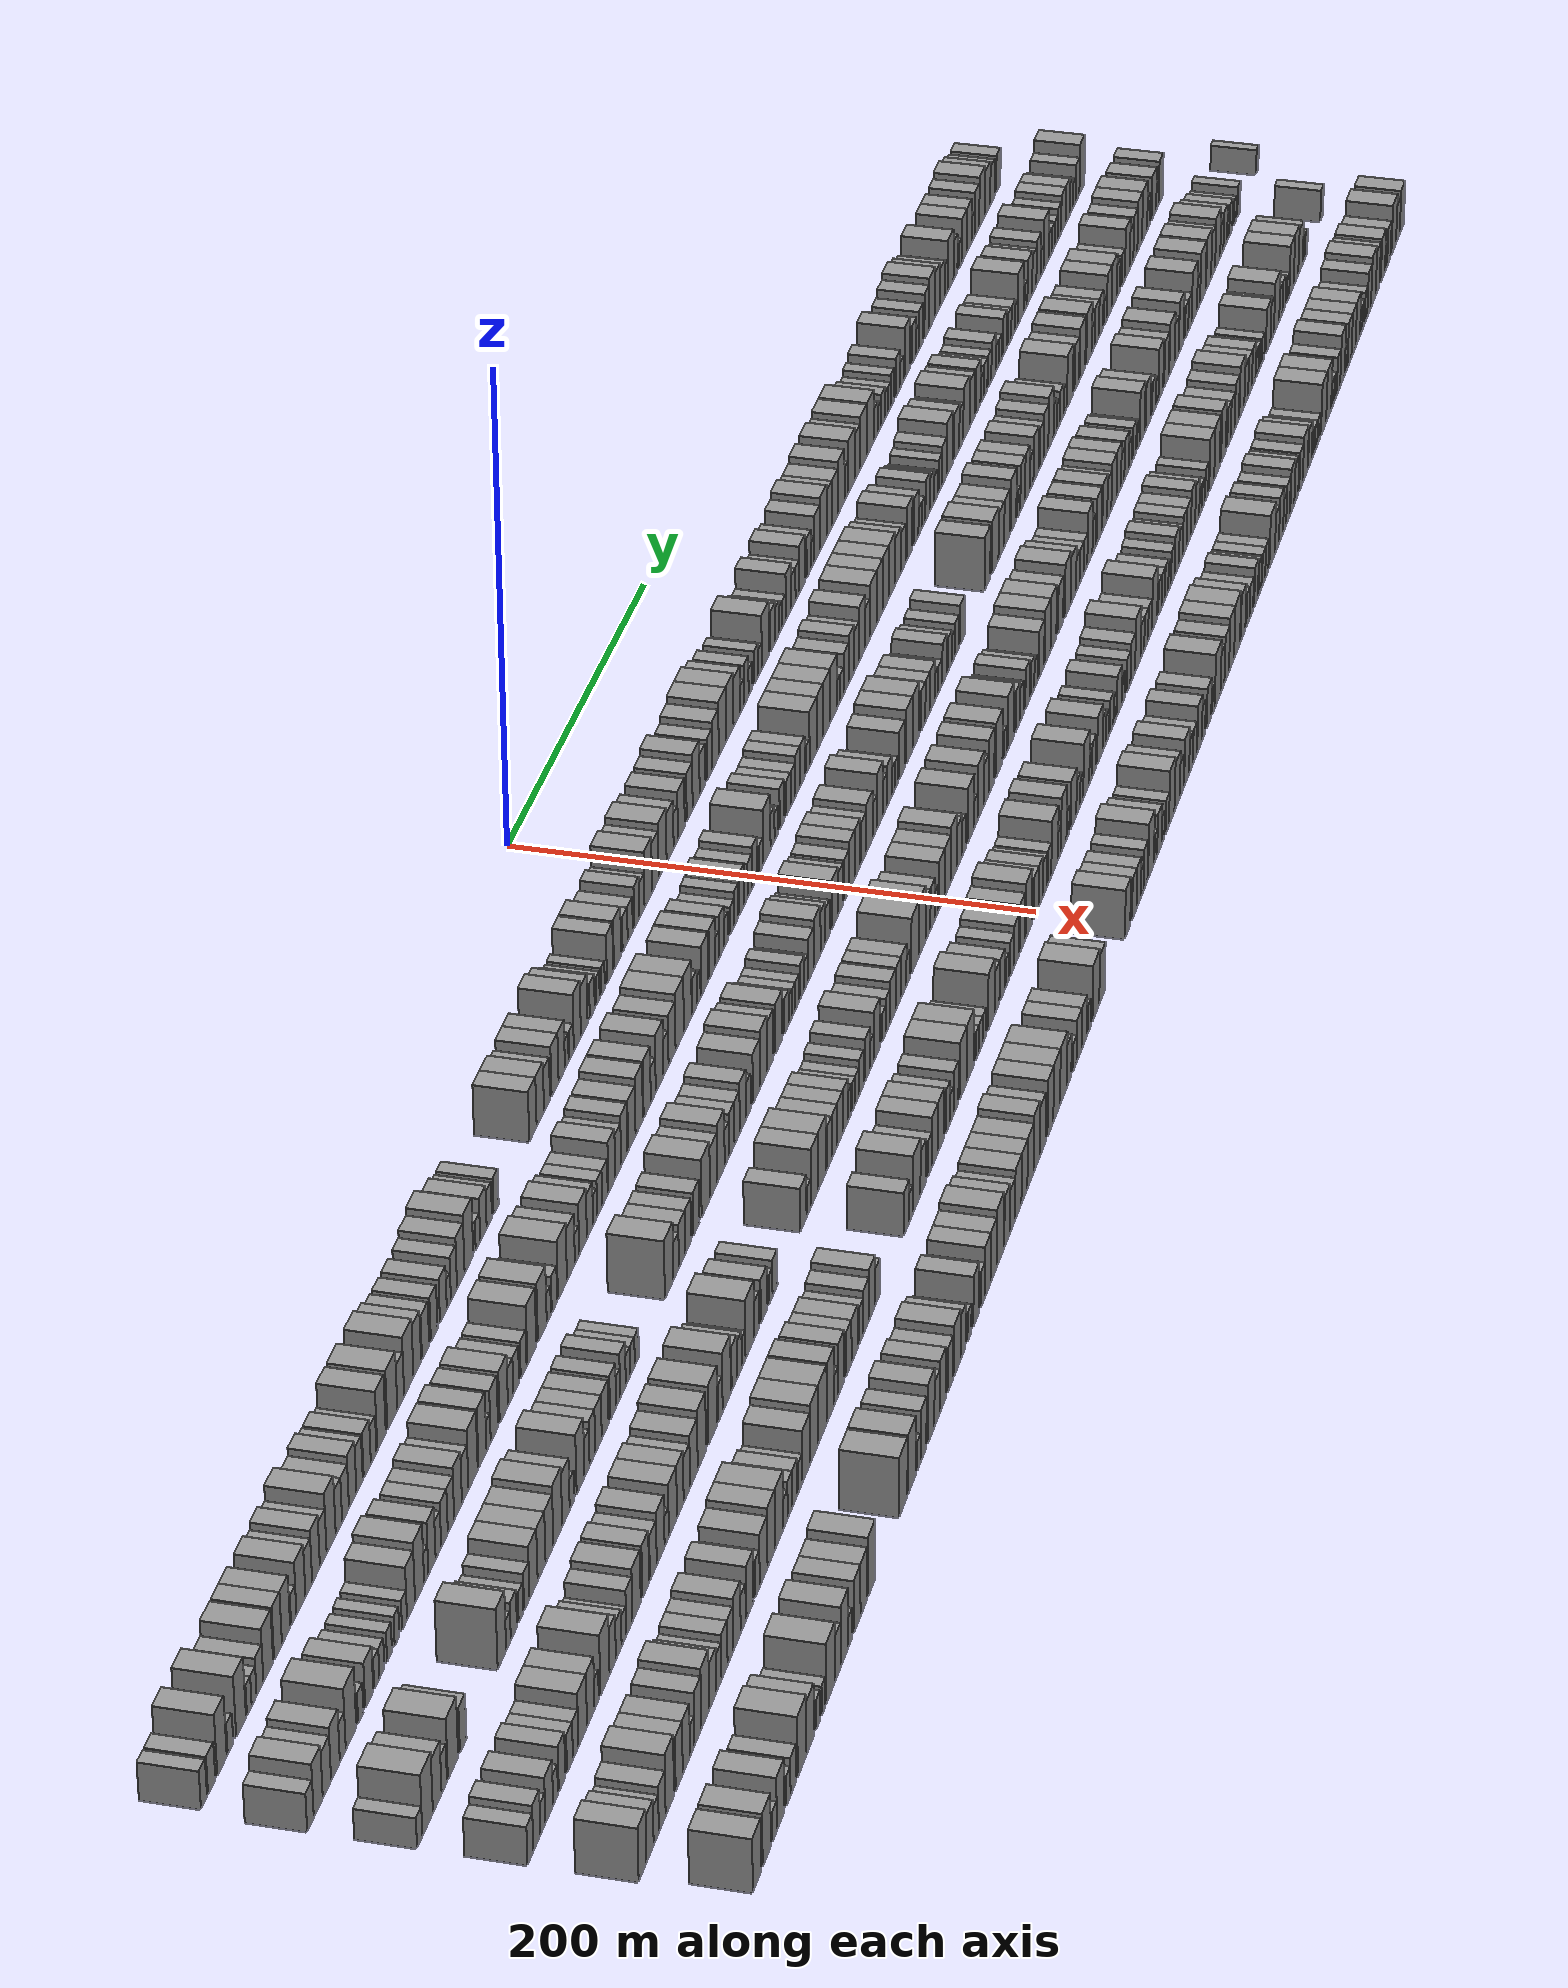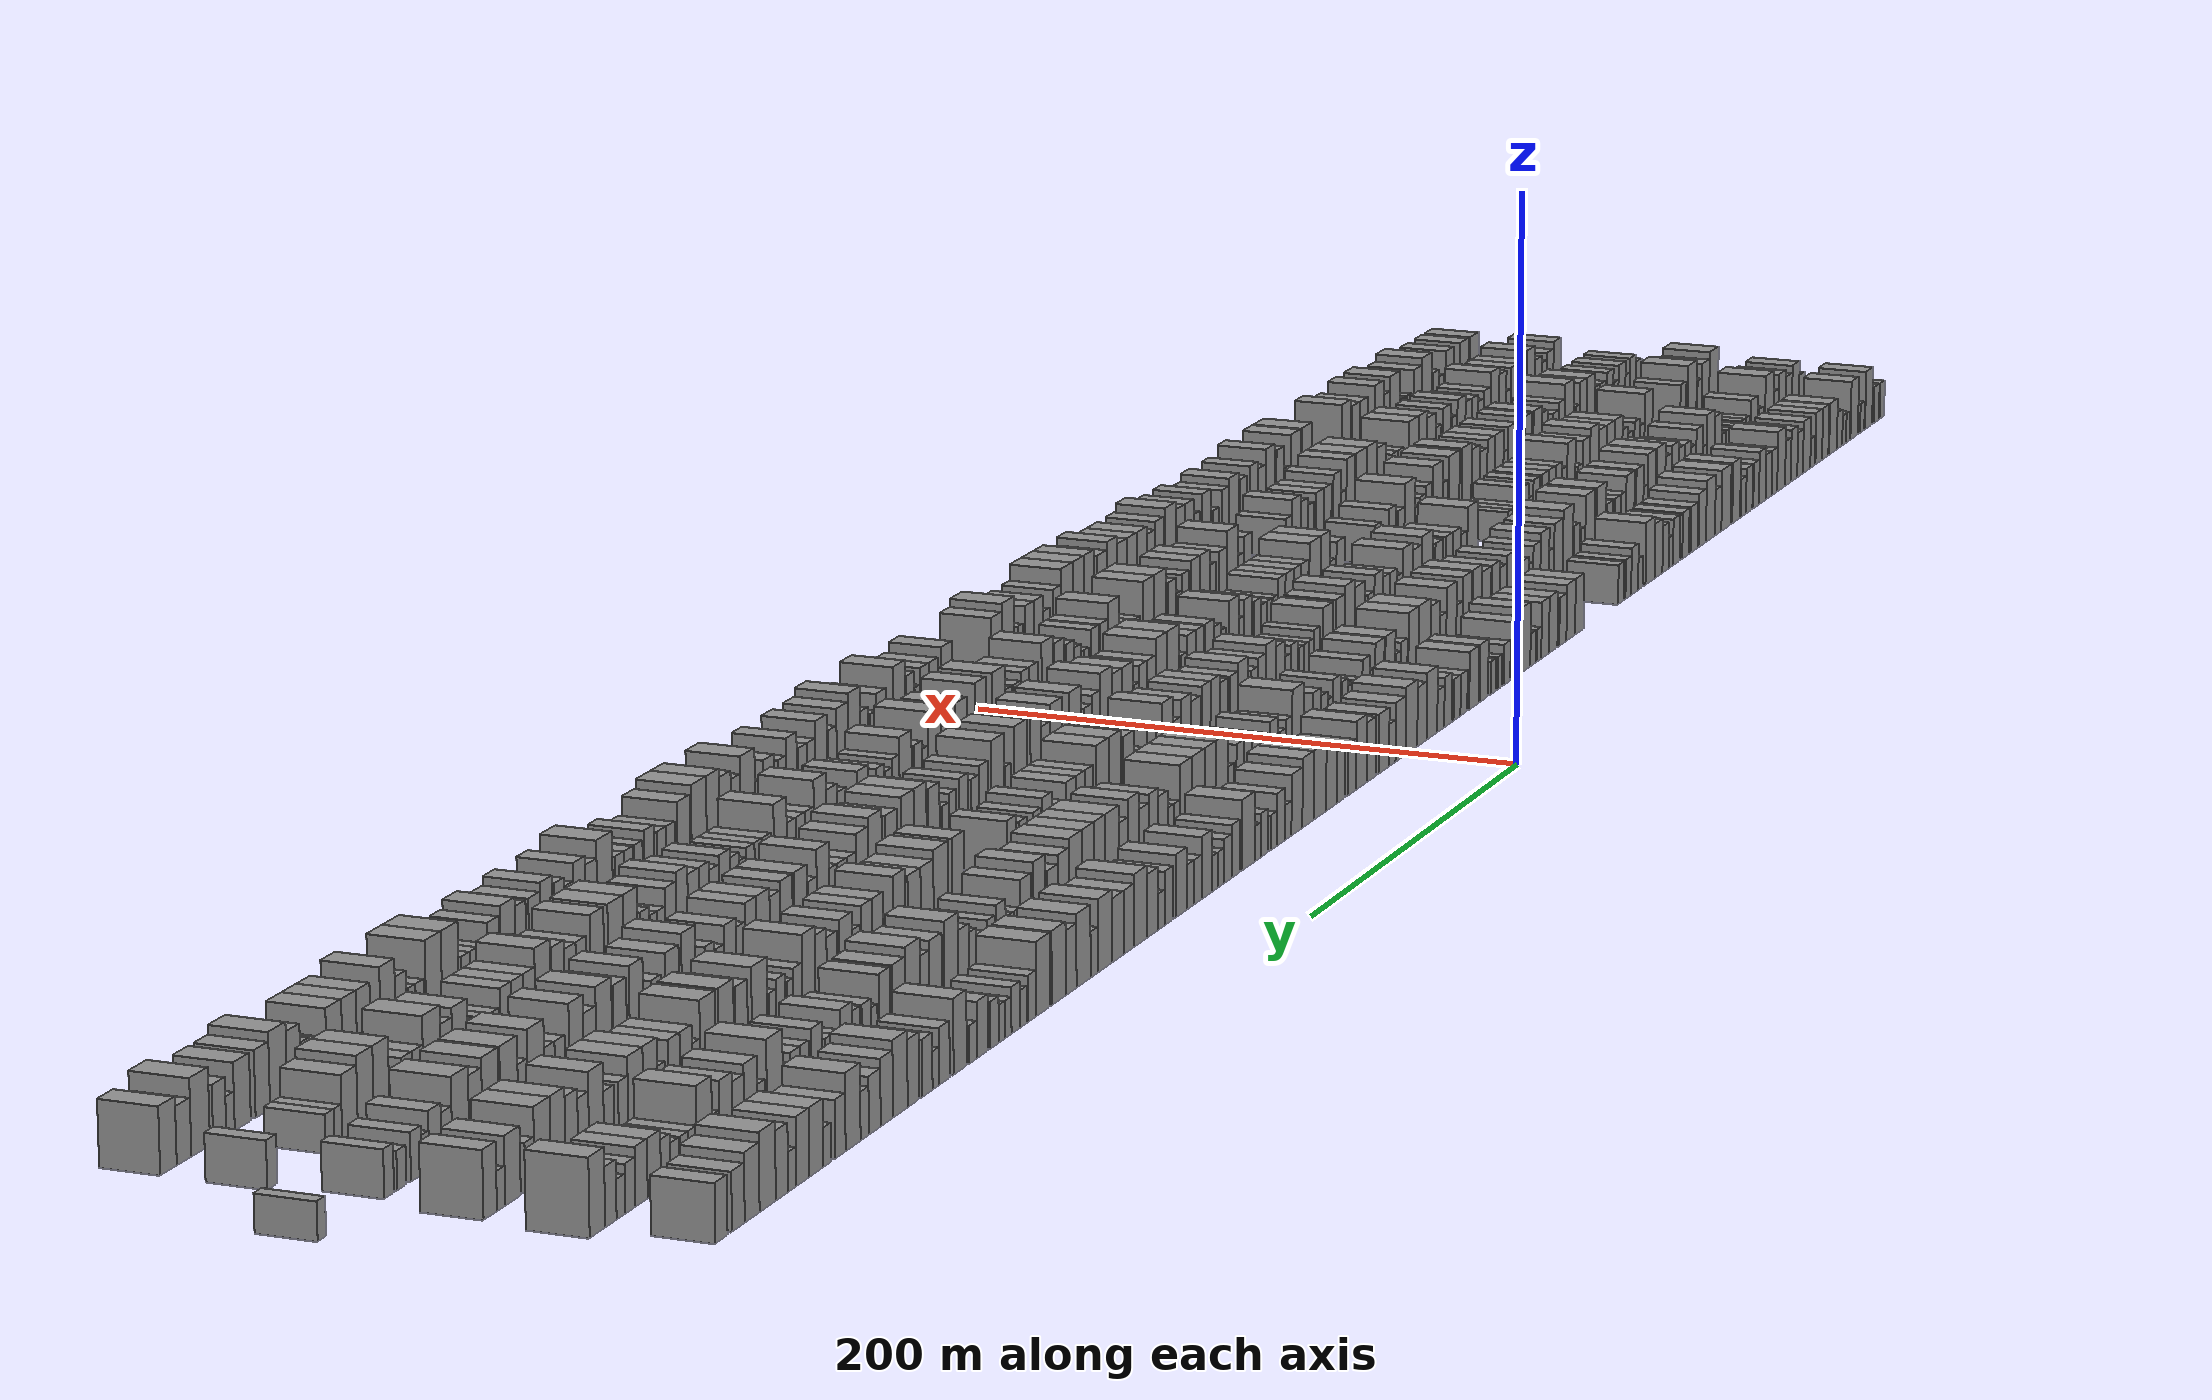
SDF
<sdf version="1.6">
 <world name="default">
  <scene>
   <sky><clouds><speed>12</speed></clouds></sky>
   <ambient>0.4 0.4 0.4 1</ambient>
   <background>0.7 0.7 0.7 1</background>
   <shadows>1</shadows>
  </scene>
  <gravity>0 0 -9.8066</gravity>
  <magnetic_field>6e-06 2.3e-05 -4.2e-05</magnetic_field>
  <physics default="0" name="default_physics" type="ode">
   <ode>
    <solver>
     <type>quick</type>
     <iters>10</iters>
     <sor>1.0</sor>
     <use_dynamic_moi_rescaling>0</use_dynamic_moi_rescaling>
    </solver>
    <constraints>
     <cfm>0</cfm>
     <erp>0.2</erp>
     <contact_max_correcting_vel>100</contact_max_correcting_vel>
     <contact_surface_layer>0.001</contact_surface_layer>
    </constraints>
   </ode>
   <max_step_size>0.004</max_step_size>
   <real_time_factor>1</real_time_factor>
   <real_time_update_rate>250</real_time_update_rate>
  </physics>
  <light name="sun" type="directional">
   <pose>0 0 10 0 0 0</pose>
   <diffuse>0.8 0.8 0.8 1</diffuse>
   <specular>0.2 0.2 0.2 1</specular>
   <attenuation>
    <range>1000</range>
    <constant>0.9</constant>
    <linear>0.01</linear>
    <quadratic>0.001</quadratic>
   </attenuation>
   <direction>-0.5 0.1 -0.9</direction>
  </light>
  <model name="building_1">
   <static>1</static>
   <pose>50.0000 -563.8621 0 0.000000 0.000000 0.000000</pose>
   <link name="link">
    <pose>0 0 7.50 0 0 0</pose>
    <collision name="collision"><geometry><box><size>20.0000 6.2758 15.0000</size></box></geometry></collision>
    <visual name="visual">
     <cast_shadows>0</cast_shadows>
     <geometry><box><size>20.0000 6.2758 15.0000</size></box></geometry>
     <material>
      <script>
       <uri>model://grey_wall/materials/scripts</uri>
       <uri>model://grey_wall/materials/textures</uri>
       <name>vrc/grey_wall</name>
      </script>
     </material>
    </visual>
   </link>
  </model>
  <model name="building_2">
   <static>1</static>
   <pose>50.0000 -555.9745 0 0.000000 0.000000 0.000000</pose>
   <link name="link">
    <pose>0 0 7.50 0 0 0</pose>
    <collision name="collision"><geometry><box><size>20.0000 7.4994 15.0000</size></box></geometry></collision>
    <visual name="visual">
     <cast_shadows>0</cast_shadows>
     <geometry><box><size>20.0000 7.4994 15.0000</size></box></geometry>
     <material>
      <script>
       <uri>model://grey_wall/materials/scripts</uri>
       <uri>model://grey_wall/materials/textures</uri>
       <name>vrc/grey_wall</name>
      </script>
     </material>
    </visual>
   </link>
  </model>
  <model name="building_3">
   <static>1</static>
   <pose>50.0000 -545.3114 0 0.000000 0.000000 0.000000</pose>
   <link name="link">
    <pose>0 0 12.00 0 0 0</pose>
    <collision name="collision"><geometry><box><size>20.0000 9.8267 24.0000</size></box></geometry></collision>
    <visual name="visual">
     <cast_shadows>0</cast_shadows>
     <geometry><box><size>20.0000 9.8267 24.0000</size></box></geometry>
     <material>
      <script>
       <uri>model://grey_wall/materials/scripts</uri>
       <uri>model://grey_wall/materials/textures</uri>
       <name>vrc/grey_wall</name>
      </script>
     </material>
    </visual>
   </link>
  </model>
  <model name="building_4">
   <static>1</static>
   <pose>50.0000 -536.4724 0 0.000000 0.000000 0.000000</pose>
   <link name="link">
    <pose>0 0 6.00 0 0 0</pose>
    <collision name="collision"><geometry><box><size>20.0000 5.8513 12.0000</size></box></geometry></collision>
    <visual name="visual">
     <cast_shadows>0</cast_shadows>
     <geometry><box><size>20.0000 5.8513 12.0000</size></box></geometry>
     <material>
      <script>
       <uri>model://grey_wall/materials/scripts</uri>
       <uri>model://grey_wall/materials/textures</uri>
       <name>vrc/grey_wall</name>
      </script>
     </material>
    </visual>
   </link>
  </model>
  <model name="building_5">
   <static>1</static>
   <pose>50.0000 -525.4141 0 0.000000 0.000000 0.000000</pose>
   <link name="link">
    <pose>0 0 12.00 0 0 0</pose>
    <collision name="collision"><geometry><box><size>20.0000 10.2654 24.0000</size></box></geometry></collision>
    <visual name="visual">
     <cast_shadows>0</cast_shadows>
     <geometry><box><size>20.0000 10.2654 24.0000</size></box></geometry>
     <material>
      <script>
       <uri>model://grey_wall/materials/scripts</uri>
       <uri>model://grey_wall/materials/textures</uri>
       <name>vrc/grey_wall</name>
      </script>
     </material>
    </visual>
   </link>
  </model>
  <model name="building_6">
   <static>1</static>
   <pose>50.0000 -516.7839 0 0.000000 0.000000 0.000000</pose>
   <link name="link">
    <pose>0 0 6.00 0 0 0</pose>
    <collision name="collision"><geometry><box><size>20.0000 4.9949 12.0000</size></box></geometry></collision>
    <visual name="visual">
     <cast_shadows>0</cast_shadows>
     <geometry><box><size>20.0000 4.9949 12.0000</size></box></geometry>
     <material>
      <script>
       <uri>model://grey_wall/materials/scripts</uri>
       <uri>model://grey_wall/materials/textures</uri>
       <name>vrc/grey_wall</name>
      </script>
     </material>
    </visual>
   </link>
  </model>
  <model name="building_7">
   <static>1</static>
   <pose>50.0000 -511.6738 0 0.000000 0.000000 0.000000</pose>
   <link name="link">
    <pose>0 0 6.00 0 0 0</pose>
    <collision name="collision"><geometry><box><size>20.0000 5.2255 12.0000</size></box></geometry></collision>
    <visual name="visual">
     <cast_shadows>0</cast_shadows>
     <geometry><box><size>20.0000 5.2255 12.0000</size></box></geometry>
     <material>
      <script>
       <uri>model://grey_wall/materials/scripts</uri>
       <uri>model://grey_wall/materials/textures</uri>
       <name>vrc/grey_wall</name>
      </script>
     </material>
    </visual>
   </link>
  </model>
  <model name="building_8">
   <static>1</static>
   <pose>50.0000 -505.4208 0 0.000000 0.000000 0.000000</pose>
   <link name="link">
    <pose>0 0 7.50 0 0 0</pose>
    <collision name="collision"><geometry><box><size>20.0000 7.2805 15.0000</size></box></geometry></collision>
    <visual name="visual">
     <cast_shadows>0</cast_shadows>
     <geometry><box><size>20.0000 7.2805 15.0000</size></box></geometry>
     <material>
      <script>
       <uri>model://grey_wall/materials/scripts</uri>
       <uri>model://grey_wall/materials/textures</uri>
       <name>vrc/grey_wall</name>
      </script>
     </material>
    </visual>
   </link>
  </model>
  <model name="building_9">
   <static>1</static>
   <pose>50.0000 -496.5619 0 0.000000 0.000000 0.000000</pose>
   <link name="link">
    <pose>0 0 10.50 0 0 0</pose>
    <collision name="collision"><geometry><box><size>20.0000 10.4373 21.0000</size></box></geometry></collision>
    <visual name="visual">
     <cast_shadows>0</cast_shadows>
     <geometry><box><size>20.0000 10.4373 21.0000</size></box></geometry>
     <material>
      <script>
       <uri>model://grey_wall/materials/scripts</uri>
       <uri>model://grey_wall/materials/textures</uri>
       <name>vrc/grey_wall</name>
      </script>
     </material>
    </visual>
   </link>
  </model>
  <model name="building_10">
   <static>1</static>
   <pose>50.0000 -486.1098 0 0.000000 0.000000 0.000000</pose>
   <link name="link">
    <pose>0 0 10.50 0 0 0</pose>
    <collision name="collision"><geometry><box><size>20.0000 8.4668 21.0000</size></box></geometry></collision>
    <visual name="visual">
     <cast_shadows>0</cast_shadows>
     <geometry><box><size>20.0000 8.4668 21.0000</size></box></geometry>
     <material>
      <script>
       <uri>model://grey_wall/materials/scripts</uri>
       <uri>model://grey_wall/materials/textures</uri>
       <name>vrc/grey_wall</name>
      </script>
     </material>
    </visual>
   </link>
  </model>
  <model name="building_11">
   <static>1</static>
   <pose>50.0000 -477.4208 0 0.000000 0.000000 0.000000</pose>
   <link name="link">
    <pose>0 0 10.50 0 0 0</pose>
    <collision name="collision"><geometry><box><size>20.0000 8.9112 21.0000</size></box></geometry></collision>
    <visual name="visual">
     <cast_shadows>0</cast_shadows>
     <geometry><box><size>20.0000 8.9112 21.0000</size></box></geometry>
     <material>
      <script>
       <uri>model://grey_wall/materials/scripts</uri>
       <uri>model://grey_wall/materials/textures</uri>
       <name>vrc/grey_wall</name>
      </script>
     </material>
    </visual>
   </link>
  </model>
  <model name="building_12">
   <static>1</static>
   <pose>50.0000 -469.0451 0 0.000000 0.000000 0.000000</pose>
   <link name="link">
    <pose>0 0 6.00 0 0 0</pose>
    <collision name="collision"><geometry><box><size>20.0000 5.8403 12.0000</size></box></geometry></collision>
    <visual name="visual">
     <cast_shadows>0</cast_shadows>
     <geometry><box><size>20.0000 5.8403 12.0000</size></box></geometry>
     <material>
      <script>
       <uri>model://grey_wall/materials/scripts</uri>
       <uri>model://grey_wall/materials/textures</uri>
       <name>vrc/grey_wall</name>
      </script>
     </material>
    </visual>
   </link>
  </model>
  <model name="building_13">
   <static>1</static>
   <pose>50.0000 -461.1967 0 0.000000 0.000000 0.000000</pose>
   <link name="link">
    <pose>0 0 10.50 0 0 0</pose>
    <collision name="collision"><geometry><box><size>20.0000 9.8566 21.0000</size></box></geometry></collision>
    <visual name="visual">
     <cast_shadows>0</cast_shadows>
     <geometry><box><size>20.0000 9.8566 21.0000</size></box></geometry>
     <material>
      <script>
       <uri>model://grey_wall/materials/scripts</uri>
       <uri>model://grey_wall/materials/textures</uri>
       <name>vrc/grey_wall</name>
      </script>
     </material>
    </visual>
   </link>
  </model>
  <model name="building_14">
   <static>1</static>
   <pose>50.0000 -452.5612 0 0.000000 0.000000 0.000000</pose>
   <link name="link">
    <pose>0 0 9.00 0 0 0</pose>
    <collision name="collision"><geometry><box><size>20.0000 7.4144 18.0000</size></box></geometry></collision>
    <visual name="visual">
     <cast_shadows>0</cast_shadows>
     <geometry><box><size>20.0000 7.4144 18.0000</size></box></geometry>
     <material>
      <script>
       <uri>model://grey_wall/materials/scripts</uri>
       <uri>model://grey_wall/materials/textures</uri>
       <name>vrc/grey_wall</name>
      </script>
     </material>
    </visual>
   </link>
  </model>
  <model name="building_15">
   <static>1</static>
   <pose>50.0000 -444.5589 0 0.000000 0.000000 0.000000</pose>
   <link name="link">
    <pose>0 0 10.50 0 0 0</pose>
    <collision name="collision"><geometry><box><size>20.0000 8.5902 21.0000</size></box></geometry></collision>
    <visual name="visual">
     <cast_shadows>0</cast_shadows>
     <geometry><box><size>20.0000 8.5902 21.0000</size></box></geometry>
     <material>
      <script>
       <uri>model://grey_wall/materials/scripts</uri>
       <uri>model://grey_wall/materials/textures</uri>
       <name>vrc/grey_wall</name>
      </script>
     </material>
    </visual>
   </link>
  </model>
  <model name="building_16">
   <static>1</static>
   <pose>50.0000 -436.5324 0 0.000000 0.000000 0.000000</pose>
   <link name="link">
    <pose>0 0 9.00 0 0 0</pose>
    <collision name="collision"><geometry><box><size>20.0000 7.4628 18.0000</size></box></geometry></collision>
    <visual name="visual">
     <cast_shadows>0</cast_shadows>
     <geometry><box><size>20.0000 7.4628 18.0000</size></box></geometry>
     <material>
      <script>
       <uri>model://grey_wall/materials/scripts</uri>
       <uri>model://grey_wall/materials/textures</uri>
       <name>vrc/grey_wall</name>
      </script>
     </material>
    </visual>
   </link>
  </model>
  <model name="building_17">
   <static>1</static>
   <pose>50.0000 -427.6935 0 0.000000 0.000000 0.000000</pose>
   <link name="link">
    <pose>0 0 12.00 0 0 0</pose>
    <collision name="collision"><geometry><box><size>20.0000 10.2148 24.0000</size></box></geometry></collision>
    <visual name="visual">
     <cast_shadows>0</cast_shadows>
     <geometry><box><size>20.0000 10.2148 24.0000</size></box></geometry>
     <material>
      <script>
       <uri>model://grey_wall/materials/scripts</uri>
       <uri>model://grey_wall/materials/textures</uri>
       <name>vrc/grey_wall</name>
      </script>
     </material>
    </visual>
   </link>
  </model>
  <model name="building_18">
   <static>1</static>
   <pose>50.0000 -418.9627 0 0.000000 0.000000 0.000000</pose>
   <link name="link">
    <pose>0 0 9.00 0 0 0</pose>
    <collision name="collision"><geometry><box><size>20.0000 7.2468 18.0000</size></box></geometry></collision>
    <visual name="visual">
     <cast_shadows>0</cast_shadows>
     <geometry><box><size>20.0000 7.2468 18.0000</size></box></geometry>
     <material>
      <script>
       <uri>model://grey_wall/materials/scripts</uri>
       <uri>model://grey_wall/materials/textures</uri>
       <name>vrc/grey_wall</name>
      </script>
     </material>
    </visual>
   </link>
  </model>
  <model name="building_19">
   <static>1</static>
   <pose>50.0000 -411.4793 0 0.000000 0.000000 0.000000</pose>
   <link name="link">
    <pose>0 0 9.00 0 0 0</pose>
    <collision name="collision"><geometry><box><size>20.0000 7.7200 18.0000</size></box></geometry></collision>
    <visual name="visual">
     <cast_shadows>0</cast_shadows>
     <geometry><box><size>20.0000 7.7200 18.0000</size></box></geometry>
     <material>
      <script>
       <uri>model://grey_wall/materials/scripts</uri>
       <uri>model://grey_wall/materials/textures</uri>
       <name>vrc/grey_wall</name>
      </script>
     </material>
    </visual>
   </link>
  </model>
  <model name="building_20">
   <static>1</static>
   <pose>50.0000 -403.3592 0 0.000000 0.000000 0.000000</pose>
   <link name="link">
    <pose>0 0 10.50 0 0 0</pose>
    <collision name="collision"><geometry><box><size>20.0000 8.5203 21.0000</size></box></geometry></collision>
    <visual name="visual">
     <cast_shadows>0</cast_shadows>
     <geometry><box><size>20.0000 8.5203 21.0000</size></box></geometry>
     <material>
      <script>
       <uri>model://grey_wall/materials/scripts</uri>
       <uri>model://grey_wall/materials/textures</uri>
       <name>vrc/grey_wall</name>
      </script>
     </material>
    </visual>
   </link>
  </model>
  <model name="building_21">
   <static>1</static>
   <pose>50.0000 -395.4574 0 0.000000 0.000000 0.000000</pose>
   <link name="link">
    <pose>0 0 9.00 0 0 0</pose>
    <collision name="collision"><geometry><box><size>20.0000 7.2833 18.0000</size></box></geometry></collision>
    <visual name="visual">
     <cast_shadows>0</cast_shadows>
     <geometry><box><size>20.0000 7.2833 18.0000</size></box></geometry>
     <material>
      <script>
       <uri>model://grey_wall/materials/scripts</uri>
       <uri>model://grey_wall/materials/textures</uri>
       <name>vrc/grey_wall</name>
      </script>
     </material>
    </visual>
   </link>
  </model>
  <model name="building_22">
   <static>1</static>
   <pose>50.0000 -386.6926 0 0.000000 0.000000 0.000000</pose>
   <link name="link">
    <pose>0 0 9.00 0 0 0</pose>
    <collision name="collision"><geometry><box><size>20.0000 8.2462 18.0000</size></box></geometry></collision>
    <visual name="visual">
     <cast_shadows>0</cast_shadows>
     <geometry><box><size>20.0000 8.2462 18.0000</size></box></geometry>
     <material>
      <script>
       <uri>model://grey_wall/materials/scripts</uri>
       <uri>model://grey_wall/materials/textures</uri>
       <name>vrc/grey_wall</name>
      </script>
     </material>
    </visual>
   </link>
  </model>
  <model name="building_23">
   <static>1</static>
   <pose>50.0000 -379.3181 0 0.000000 0.000000 0.000000</pose>
   <link name="link">
    <pose>0 0 7.50 0 0 0</pose>
    <collision name="collision"><geometry><box><size>20.0000 6.5028 15.0000</size></box></geometry></collision>
    <visual name="visual">
     <cast_shadows>0</cast_shadows>
     <geometry><box><size>20.0000 6.5028 15.0000</size></box></geometry>
     <material>
      <script>
       <uri>model://grey_wall/materials/scripts</uri>
       <uri>model://grey_wall/materials/textures</uri>
       <name>vrc/grey_wall</name>
      </script>
     </material>
    </visual>
   </link>
  </model>
  <model name="building_24">
   <static>1</static>
   <pose>50.0000 -370.1456 0 0.000000 0.000000 0.000000</pose>
   <link name="link">
    <pose>0 0 12.00 0 0 0</pose>
    <collision name="collision"><geometry><box><size>20.0000 9.8422 24.0000</size></box></geometry></collision>
    <visual name="visual">
     <cast_shadows>0</cast_shadows>
     <geometry><box><size>20.0000 9.8422 24.0000</size></box></geometry>
     <material>
      <script>
       <uri>model://grey_wall/materials/scripts</uri>
       <uri>model://grey_wall/materials/textures</uri>
       <name>vrc/grey_wall</name>
      </script>
     </material>
    </visual>
   </link>
  </model>
  <model name="building_25">
   <static>1</static>
   <pose>50.0000 -357.4346 0 0.000000 0.000000 0.000000</pose>
   <link name="link">
    <pose>0 0 12.00 0 0 0</pose>
    <collision name="collision"><geometry><box><size>20.0000 11.5797 24.0000</size></box></geometry></collision>
    <visual name="visual">
     <cast_shadows>0</cast_shadows>
     <geometry><box><size>20.0000 11.5797 24.0000</size></box></geometry>
     <material>
      <script>
       <uri>model://grey_wall/materials/scripts</uri>
       <uri>model://grey_wall/materials/textures</uri>
       <name>vrc/grey_wall</name>
      </script>
     </material>
    </visual>
   </link>
  </model>
  <model name="building_26">
   <static>1</static>
   <pose>50.0000 -347.6290 0 0.000000 0.000000 0.000000</pose>
   <link name="link">
    <pose>0 0 9.00 0 0 0</pose>
    <collision name="collision"><geometry><box><size>20.0000 8.0316 18.0000</size></box></geometry></collision>
    <visual name="visual">
     <cast_shadows>0</cast_shadows>
     <geometry><box><size>20.0000 8.0316 18.0000</size></box></geometry>
     <material>
      <script>
       <uri>model://grey_wall/materials/scripts</uri>
       <uri>model://grey_wall/materials/textures</uri>
       <name>vrc/grey_wall</name>
      </script>
     </material>
    </visual>
   </link>
  </model>
  <model name="building_27">
   <static>1</static>
   <pose>50.0000 -338.0528 0 0.000000 0.000000 0.000000</pose>
   <link name="link">
    <pose>0 0 12.00 0 0 0</pose>
    <collision name="collision"><geometry><box><size>20.0000 11.1209 24.0000</size></box></geometry></collision>
    <visual name="visual">
     <cast_shadows>0</cast_shadows>
     <geometry><box><size>20.0000 11.1209 24.0000</size></box></geometry>
     <material>
      <script>
       <uri>model://grey_wall/materials/scripts</uri>
       <uri>model://grey_wall/materials/textures</uri>
       <name>vrc/grey_wall</name>
      </script>
     </material>
    </visual>
   </link>
  </model>
  <model name="building_28">
   <static>1</static>
   <pose>50.0000 -327.9274 0 0.000000 0.000000 0.000000</pose>
   <link name="link">
    <pose>0 0 10.50 0 0 0</pose>
    <collision name="collision"><geometry><box><size>20.0000 9.1298 21.0000</size></box></geometry></collision>
    <visual name="visual">
     <cast_shadows>0</cast_shadows>
     <geometry><box><size>20.0000 9.1298 21.0000</size></box></geometry>
     <material>
      <script>
       <uri>model://grey_wall/materials/scripts</uri>
       <uri>model://grey_wall/materials/textures</uri>
       <name>vrc/grey_wall</name>
      </script>
     </material>
    </visual>
   </link>
  </model>
  <model name="building_29">
   <static>1</static>
   <pose>50.0000 -318.0149 0 0.000000 0.000000 0.000000</pose>
   <link name="link">
    <pose>0 0 9.00 0 0 0</pose>
    <collision name="collision"><geometry><box><size>20.0000 8.6952 18.0000</size></box></geometry></collision>
    <visual name="visual">
     <cast_shadows>0</cast_shadows>
     <geometry><box><size>20.0000 8.6952 18.0000</size></box></geometry>
     <material>
      <script>
       <uri>model://grey_wall/materials/scripts</uri>
       <uri>model://grey_wall/materials/textures</uri>
       <name>vrc/grey_wall</name>
      </script>
     </material>
    </visual>
   </link>
  </model>
  <model name="building_30">
   <static>1</static>
   <pose>50.0000 -307.6293 0 0.000000 0.000000 0.000000</pose>
   <link name="link">
    <pose>0 0 9.00 0 0 0</pose>
    <collision name="collision"><geometry><box><size>20.0000 8.0760 18.0000</size></box></geometry></collision>
    <visual name="visual">
     <cast_shadows>0</cast_shadows>
     <geometry><box><size>20.0000 8.0760 18.0000</size></box></geometry>
     <material>
      <script>
       <uri>model://grey_wall/materials/scripts</uri>
       <uri>model://grey_wall/materials/textures</uri>
       <name>vrc/grey_wall</name>
      </script>
     </material>
    </visual>
   </link>
  </model>
  <model name="building_31">
   <static>1</static>
   <pose>50.0000 -296.4434 0 0.000000 0.000000 0.000000</pose>
   <link name="link">
    <pose>0 0 9.00 0 0 0</pose>
    <collision name="collision"><geometry><box><size>20.0000 8.2958 18.0000</size></box></geometry></collision>
    <visual name="visual">
     <cast_shadows>0</cast_shadows>
     <geometry><box><size>20.0000 8.2958 18.0000</size></box></geometry>
     <material>
      <script>
       <uri>model://grey_wall/materials/scripts</uri>
       <uri>model://grey_wall/materials/textures</uri>
       <name>vrc/grey_wall</name>
      </script>
     </material>
    </visual>
   </link>
  </model>
  <model name="building_32">
   <static>1</static>
   <pose>50.0000 -289.7663 0 0.000000 0.000000 0.000000</pose>
   <link name="link">
    <pose>0 0 6.00 0 0 0</pose>
    <collision name="collision"><geometry><box><size>20.0000 5.0585 12.0000</size></box></geometry></collision>
    <visual name="visual">
     <cast_shadows>0</cast_shadows>
     <geometry><box><size>20.0000 5.0585 12.0000</size></box></geometry>
     <material>
      <script>
       <uri>model://grey_wall/materials/scripts</uri>
       <uri>model://grey_wall/materials/textures</uri>
       <name>vrc/grey_wall</name>
      </script>
     </material>
    </visual>
   </link>
  </model>
  <model name="building_33">
   <static>1</static>
   <pose>50.0000 -283.4682 0 0.000000 0.000000 0.000000</pose>
   <link name="link">
    <pose>0 0 9.00 0 0 0</pose>
    <collision name="collision"><geometry><box><size>20.0000 7.5378 18.0000</size></box></geometry></collision>
    <visual name="visual">
     <cast_shadows>0</cast_shadows>
     <geometry><box><size>20.0000 7.5378 18.0000</size></box></geometry>
     <material>
      <script>
       <uri>model://grey_wall/materials/scripts</uri>
       <uri>model://grey_wall/materials/textures</uri>
       <name>vrc/grey_wall</name>
      </script>
     </material>
    </visual>
   </link>
  </model>
  <model name="building_34">
   <static>1</static>
   <pose>50.0000 -275.0343 0 0.000000 0.000000 0.000000</pose>
   <link name="link">
    <pose>0 0 10.50 0 0 0</pose>
    <collision name="collision"><geometry><box><size>20.0000 9.3299 21.0000</size></box></geometry></collision>
    <visual name="visual">
     <cast_shadows>0</cast_shadows>
     <geometry><box><size>20.0000 9.3299 21.0000</size></box></geometry>
     <material>
      <script>
       <uri>model://grey_wall/materials/scripts</uri>
       <uri>model://grey_wall/materials/textures</uri>
       <name>vrc/grey_wall</name>
      </script>
     </material>
    </visual>
   </link>
  </model>
  <model name="building_35">
   <static>1</static>
   <pose>50.0000 -264.9708 0 0.000000 0.000000 0.000000</pose>
   <link name="link">
    <pose>0 0 12.00 0 0 0</pose>
    <collision name="collision"><geometry><box><size>20.0000 10.7972 24.0000</size></box></geometry></collision>
    <visual name="visual">
     <cast_shadows>0</cast_shadows>
     <geometry><box><size>20.0000 10.7972 24.0000</size></box></geometry>
     <material>
      <script>
       <uri>model://grey_wall/materials/scripts</uri>
       <uri>model://grey_wall/materials/textures</uri>
       <name>vrc/grey_wall</name>
      </script>
     </material>
    </visual>
   </link>
  </model>
  <model name="building_36">
   <static>1</static>
   <pose>50.0000 -253.7307 0 0.000000 0.000000 0.000000</pose>
   <link name="link">
    <pose>0 0 6.00 0 0 0</pose>
    <collision name="collision"><geometry><box><size>20.0000 5.6831 12.0000</size></box></geometry></collision>
    <visual name="visual">
     <cast_shadows>0</cast_shadows>
     <geometry><box><size>20.0000 5.6831 12.0000</size></box></geometry>
     <material>
      <script>
       <uri>model://grey_wall/materials/scripts</uri>
       <uri>model://grey_wall/materials/textures</uri>
       <name>vrc/grey_wall</name>
      </script>
     </material>
    </visual>
   </link>
  </model>
  <model name="building_37">
   <static>1</static>
   <pose>50.0000 -246.8134 0 0.000000 0.000000 0.000000</pose>
   <link name="link">
    <pose>0 0 9.00 0 0 0</pose>
    <collision name="collision"><geometry><box><size>20.0000 8.1516 18.0000</size></box></geometry></collision>
    <visual name="visual">
     <cast_shadows>0</cast_shadows>
     <geometry><box><size>20.0000 8.1516 18.0000</size></box></geometry>
     <material>
      <script>
       <uri>model://grey_wall/materials/scripts</uri>
       <uri>model://grey_wall/materials/textures</uri>
       <name>vrc/grey_wall</name>
      </script>
     </material>
    </visual>
   </link>
  </model>
  <model name="building_38">
   <static>1</static>
   <pose>50.0000 -239.3808 0 0.000000 0.000000 0.000000</pose>
   <link name="link">
    <pose>0 0 7.50 0 0 0</pose>
    <collision name="collision"><geometry><box><size>20.0000 6.7136 15.0000</size></box></geometry></collision>
    <visual name="visual">
     <cast_shadows>0</cast_shadows>
     <geometry><box><size>20.0000 6.7136 15.0000</size></box></geometry>
     <material>
      <script>
       <uri>model://grey_wall/materials/scripts</uri>
       <uri>model://grey_wall/materials/textures</uri>
       <name>vrc/grey_wall</name>
      </script>
     </material>
    </visual>
   </link>
  </model>
  <model name="building_39">
   <static>1</static>
   <pose>50.0000 -230.8097 0 0.000000 0.000000 0.000000</pose>
   <link name="link">
    <pose>0 0 7.50 0 0 0</pose>
    <collision name="collision"><geometry><box><size>20.0000 6.4286 15.0000</size></box></geometry></collision>
    <visual name="visual">
     <cast_shadows>0</cast_shadows>
     <geometry><box><size>20.0000 6.4286 15.0000</size></box></geometry>
     <material>
      <script>
       <uri>model://grey_wall/materials/scripts</uri>
       <uri>model://grey_wall/materials/textures</uri>
       <name>vrc/grey_wall</name>
      </script>
     </material>
    </visual>
   </link>
  </model>
  <model name="building_40">
   <static>1</static>
   <pose>50.0000 -183.2096 0 0.000000 0.000000 0.000000</pose>
   <link name="link">
    <pose>0 0 10.50 0 0 0</pose>
    <collision name="collision"><geometry><box><size>20.0000 9.5905 21.0000</size></box></geometry></collision>
    <visual name="visual">
     <cast_shadows>0</cast_shadows>
     <geometry><box><size>20.0000 9.5905 21.0000</size></box></geometry>
     <material>
      <script>
       <uri>model://grey_wall/materials/scripts</uri>
       <uri>model://grey_wall/materials/textures</uri>
       <name>vrc/grey_wall</name>
      </script>
     </material>
    </visual>
   </link>
  </model>
  <model name="building_41">
   <static>1</static>
   <pose>50.0000 -173.5254 0 0.000000 0.000000 0.000000</pose>
   <link name="link">
    <pose>0 0 10.50 0 0 0</pose>
    <collision name="collision"><geometry><box><size>20.0000 9.7779 21.0000</size></box></geometry></collision>
    <visual name="visual">
     <cast_shadows>0</cast_shadows>
     <geometry><box><size>20.0000 9.7779 21.0000</size></box></geometry>
     <material>
      <script>
       <uri>model://grey_wall/materials/scripts</uri>
       <uri>model://grey_wall/materials/textures</uri>
       <name>vrc/grey_wall</name>
      </script>
     </material>
    </visual>
   </link>
  </model>
  <model name="building_42">
   <static>1</static>
   <pose>50.0000 -164.6421 0 0.000000 0.000000 0.000000</pose>
   <link name="link">
    <pose>0 0 9.00 0 0 0</pose>
    <collision name="collision"><geometry><box><size>20.0000 7.9887 18.0000</size></box></geometry></collision>
    <visual name="visual">
     <cast_shadows>0</cast_shadows>
     <geometry><box><size>20.0000 7.9887 18.0000</size></box></geometry>
     <material>
      <script>
       <uri>model://grey_wall/materials/scripts</uri>
       <uri>model://grey_wall/materials/textures</uri>
       <name>vrc/grey_wall</name>
      </script>
     </material>
    </visual>
   </link>
  </model>
  <model name="building_43">
   <static>1</static>
   <pose>50.0000 -153.9660 0 0.000000 0.000000 0.000000</pose>
   <link name="link">
    <pose>0 0 10.50 0 0 0</pose>
    <collision name="collision"><geometry><box><size>20.0000 9.3635 21.0000</size></box></geometry></collision>
    <visual name="visual">
     <cast_shadows>0</cast_shadows>
     <geometry><box><size>20.0000 9.3635 21.0000</size></box></geometry>
     <material>
      <script>
       <uri>model://grey_wall/materials/scripts</uri>
       <uri>model://grey_wall/materials/textures</uri>
       <name>vrc/grey_wall</name>
      </script>
     </material>
    </visual>
   </link>
  </model>
  <model name="building_44">
   <static>1</static>
   <pose>50.0000 -145.0248 0 0.000000 0.000000 0.000000</pose>
   <link name="link">
    <pose>0 0 10.50 0 0 0</pose>
    <collision name="collision"><geometry><box><size>20.0000 8.5188 21.0000</size></box></geometry></collision>
    <visual name="visual">
     <cast_shadows>0</cast_shadows>
     <geometry><box><size>20.0000 8.5188 21.0000</size></box></geometry>
     <material>
      <script>
       <uri>model://grey_wall/materials/scripts</uri>
       <uri>model://grey_wall/materials/textures</uri>
       <name>vrc/grey_wall</name>
      </script>
     </material>
    </visual>
   </link>
  </model>
  <model name="building_45">
   <static>1</static>
   <pose>50.0000 -138.2439 0 0.000000 0.000000 0.000000</pose>
   <link name="link">
    <pose>0 0 6.00 0 0 0</pose>
    <collision name="collision"><geometry><box><size>20.0000 5.0429 12.0000</size></box></geometry></collision>
    <visual name="visual">
     <cast_shadows>0</cast_shadows>
     <geometry><box><size>20.0000 5.0429 12.0000</size></box></geometry>
     <material>
      <script>
       <uri>model://grey_wall/materials/scripts</uri>
       <uri>model://grey_wall/materials/textures</uri>
       <name>vrc/grey_wall</name>
      </script>
     </material>
    </visual>
   </link>
  </model>
  <model name="building_46">
   <static>1</static>
   <pose>50.0000 -131.7362 0 0.000000 0.000000 0.000000</pose>
   <link name="link">
    <pose>0 0 6.00 0 0 0</pose>
    <collision name="collision"><geometry><box><size>20.0000 5.9725 12.0000</size></box></geometry></collision>
    <visual name="visual">
     <cast_shadows>0</cast_shadows>
     <geometry><box><size>20.0000 5.9725 12.0000</size></box></geometry>
     <material>
      <script>
       <uri>model://grey_wall/materials/scripts</uri>
       <uri>model://grey_wall/materials/textures</uri>
       <name>vrc/grey_wall</name>
      </script>
     </material>
    </visual>
   </link>
  </model>
  <model name="building_47">
   <static>1</static>
   <pose>50.0000 -123.9378 0 0.000000 0.000000 0.000000</pose>
   <link name="link">
    <pose>0 0 12.00 0 0 0</pose>
    <collision name="collision"><geometry><box><size>20.0000 9.6244 24.0000</size></box></geometry></collision>
    <visual name="visual">
     <cast_shadows>0</cast_shadows>
     <geometry><box><size>20.0000 9.6244 24.0000</size></box></geometry>
     <material>
      <script>
       <uri>model://grey_wall/materials/scripts</uri>
       <uri>model://grey_wall/materials/textures</uri>
       <name>vrc/grey_wall</name>
      </script>
     </material>
    </visual>
   </link>
  </model>
  <model name="building_48">
   <static>1</static>
   <pose>50.0000 -114.5761 0 0.000000 0.000000 0.000000</pose>
   <link name="link">
    <pose>0 0 10.50 0 0 0</pose>
    <collision name="collision"><geometry><box><size>20.0000 9.0991 21.0000</size></box></geometry></collision>
    <visual name="visual">
     <cast_shadows>0</cast_shadows>
     <geometry><box><size>20.0000 9.0991 21.0000</size></box></geometry>
     <material>
      <script>
       <uri>model://grey_wall/materials/scripts</uri>
       <uri>model://grey_wall/materials/textures</uri>
       <name>vrc/grey_wall</name>
      </script>
     </material>
    </visual>
   </link>
  </model>
  <model name="building_49">
   <static>1</static>
   <pose>50.0000 -103.6058 0 0.000000 0.000000 0.000000</pose>
   <link name="link">
    <pose>0 0 7.50 0 0 0</pose>
    <collision name="collision"><geometry><box><size>20.0000 6.8415 15.0000</size></box></geometry></collision>
    <visual name="visual">
     <cast_shadows>0</cast_shadows>
     <geometry><box><size>20.0000 6.8415 15.0000</size></box></geometry>
     <material>
      <script>
       <uri>model://grey_wall/materials/scripts</uri>
       <uri>model://grey_wall/materials/textures</uri>
       <name>vrc/grey_wall</name>
      </script>
     </material>
    </visual>
   </link>
  </model>
  <model name="building_50">
   <static>1</static>
   <pose>50.0000 -95.7800 0 0.000000 0.000000 0.000000</pose>
   <link name="link">
    <pose>0 0 6.00 0 0 0</pose>
    <collision name="collision"><geometry><box><size>20.0000 4.8100 12.0000</size></box></geometry></collision>
    <visual name="visual">
     <cast_shadows>0</cast_shadows>
     <geometry><box><size>20.0000 4.8100 12.0000</size></box></geometry>
     <material>
      <script>
       <uri>model://grey_wall/materials/scripts</uri>
       <uri>model://grey_wall/materials/textures</uri>
       <name>vrc/grey_wall</name>
      </script>
     </material>
    </visual>
   </link>
  </model>
  <model name="building_51">
   <static>1</static>
   <pose>50.0000 -88.8251 0 0.000000 0.000000 0.000000</pose>
   <link name="link">
    <pose>0 0 6.00 0 0 0</pose>
    <collision name="collision"><geometry><box><size>20.0000 5.0998 12.0000</size></box></geometry></collision>
    <visual name="visual">
     <cast_shadows>0</cast_shadows>
     <geometry><box><size>20.0000 5.0998 12.0000</size></box></geometry>
     <material>
      <script>
       <uri>model://grey_wall/materials/scripts</uri>
       <uri>model://grey_wall/materials/textures</uri>
       <name>vrc/grey_wall</name>
      </script>
     </material>
    </visual>
   </link>
  </model>
  <model name="building_52">
   <static>1</static>
   <pose>50.0000 -78.9045 0 0.000000 0.000000 0.000000</pose>
   <link name="link">
    <pose>0 0 10.50 0 0 0</pose>
    <collision name="collision"><geometry><box><size>20.0000 8.7416 21.0000</size></box></geometry></collision>
    <visual name="visual">
     <cast_shadows>0</cast_shadows>
     <geometry><box><size>20.0000 8.7416 21.0000</size></box></geometry>
     <material>
      <script>
       <uri>model://grey_wall/materials/scripts</uri>
       <uri>model://grey_wall/materials/textures</uri>
       <name>vrc/grey_wall</name>
      </script>
     </material>
    </visual>
   </link>
  </model>
  <model name="building_53">
   <static>1</static>
   <pose>50.0000 -68.4530 0 0.000000 0.000000 0.000000</pose>
   <link name="link">
    <pose>0 0 10.50 0 0 0</pose>
    <collision name="collision"><geometry><box><size>20.0000 10.1614 21.0000</size></box></geometry></collision>
    <visual name="visual">
     <cast_shadows>0</cast_shadows>
     <geometry><box><size>20.0000 10.1614 21.0000</size></box></geometry>
     <material>
      <script>
       <uri>model://grey_wall/materials/scripts</uri>
       <uri>model://grey_wall/materials/textures</uri>
       <name>vrc/grey_wall</name>
      </script>
     </material>
    </visual>
   </link>
  </model>
  <model name="building_54">
   <static>1</static>
   <pose>50.0000 -57.7697 0 0.000000 0.000000 0.000000</pose>
   <link name="link">
    <pose>0 0 7.50 0 0 0</pose>
    <collision name="collision"><geometry><box><size>20.0000 7.2052 15.0000</size></box></geometry></collision>
    <visual name="visual">
     <cast_shadows>0</cast_shadows>
     <geometry><box><size>20.0000 7.2052 15.0000</size></box></geometry>
     <material>
      <script>
       <uri>model://grey_wall/materials/scripts</uri>
       <uri>model://grey_wall/materials/textures</uri>
       <name>vrc/grey_wall</name>
      </script>
     </material>
    </visual>
   </link>
  </model>
  <model name="building_55">
   <static>1</static>
   <pose>50.0000 -50.5477 0 0.000000 0.000000 0.000000</pose>
   <link name="link">
    <pose>0 0 7.50 0 0 0</pose>
    <collision name="collision"><geometry><box><size>20.0000 7.2387 15.0000</size></box></geometry></collision>
    <visual name="visual">
     <cast_shadows>0</cast_shadows>
     <geometry><box><size>20.0000 7.2387 15.0000</size></box></geometry>
     <material>
      <script>
       <uri>model://grey_wall/materials/scripts</uri>
       <uri>model://grey_wall/materials/textures</uri>
       <name>vrc/grey_wall</name>
      </script>
     </material>
    </visual>
   </link>
  </model>
  <model name="building_56">
   <static>1</static>
   <pose>50.0000 -41.1578 0 0.000000 0.000000 0.000000</pose>
   <link name="link">
    <pose>0 0 9.00 0 0 0</pose>
    <collision name="collision"><geometry><box><size>20.0000 7.5411 18.0000</size></box></geometry></collision>
    <visual name="visual">
     <cast_shadows>0</cast_shadows>
     <geometry><box><size>20.0000 7.5411 18.0000</size></box></geometry>
     <material>
      <script>
       <uri>model://grey_wall/materials/scripts</uri>
       <uri>model://grey_wall/materials/textures</uri>
       <name>vrc/grey_wall</name>
      </script>
     </material>
    </visual>
   </link>
  </model>
  <model name="building_57">
   <static>1</static>
   <pose>50.0000 -33.7795 0 0.000000 0.000000 0.000000</pose>
   <link name="link">
    <pose>0 0 7.50 0 0 0</pose>
    <collision name="collision"><geometry><box><size>20.0000 7.2155 15.0000</size></box></geometry></collision>
    <visual name="visual">
     <cast_shadows>0</cast_shadows>
     <geometry><box><size>20.0000 7.2155 15.0000</size></box></geometry>
     <material>
      <script>
       <uri>model://grey_wall/materials/scripts</uri>
       <uri>model://grey_wall/materials/textures</uri>
       <name>vrc/grey_wall</name>
      </script>
     </material>
    </visual>
   </link>
  </model>
  <model name="building_58">
   <static>1</static>
   <pose>50.0000 -24.7381 0 0.000000 0.000000 0.000000</pose>
   <link name="link">
    <pose>0 0 12.00 0 0 0</pose>
    <collision name="collision"><geometry><box><size>20.0000 10.8673 24.0000</size></box></geometry></collision>
    <visual name="visual">
     <cast_shadows>0</cast_shadows>
     <geometry><box><size>20.0000 10.8673 24.0000</size></box></geometry>
     <material>
      <script>
       <uri>model://grey_wall/materials/scripts</uri>
       <uri>model://grey_wall/materials/textures</uri>
       <name>vrc/grey_wall</name>
      </script>
     </material>
    </visual>
   </link>
  </model>
  <model name="building_59">
   <static>1</static>
   <pose>50.0000 -14.5444 0 0.000000 0.000000 0.000000</pose>
   <link name="link">
    <pose>0 0 10.50 0 0 0</pose>
    <collision name="collision"><geometry><box><size>20.0000 9.5200 21.0000</size></box></geometry></collision>
    <visual name="visual">
     <cast_shadows>0</cast_shadows>
     <geometry><box><size>20.0000 9.5200 21.0000</size></box></geometry>
     <material>
      <script>
       <uri>model://grey_wall/materials/scripts</uri>
       <uri>model://grey_wall/materials/textures</uri>
       <name>vrc/grey_wall</name>
      </script>
     </material>
    </visual>
   </link>
  </model>
  <model name="building_60">
   <static>1</static>
   <pose>50.0000 -3.9836 0 0.000000 0.000000 0.000000</pose>
   <link name="link">
    <pose>0 0 12.00 0 0 0</pose>
    <collision name="collision"><geometry><box><size>20.0000 11.6017 24.0000</size></box></geometry></collision>
    <visual name="visual">
     <cast_shadows>0</cast_shadows>
     <geometry><box><size>20.0000 11.6017 24.0000</size></box></geometry>
     <material>
      <script>
       <uri>model://grey_wall/materials/scripts</uri>
       <uri>model://grey_wall/materials/textures</uri>
       <name>vrc/grey_wall</name>
      </script>
     </material>
    </visual>
   </link>
  </model>
  <model name="building_61">
   <static>1</static>
   <pose>50.0000 6.9874 0 0.000000 0.000000 0.000000</pose>
   <link name="link">
    <pose>0 0 10.50 0 0 0</pose>
    <collision name="collision"><geometry><box><size>20.0000 10.3402 21.0000</size></box></geometry></collision>
    <visual name="visual">
     <cast_shadows>0</cast_shadows>
     <geometry><box><size>20.0000 10.3402 21.0000</size></box></geometry>
     <material>
      <script>
       <uri>model://grey_wall/materials/scripts</uri>
       <uri>model://grey_wall/materials/textures</uri>
       <name>vrc/grey_wall</name>
      </script>
     </material>
    </visual>
   </link>
  </model>
  <model name="building_62">
   <static>1</static>
   <pose>50.0000 15.3178 0 0.000000 0.000000 0.000000</pose>
   <link name="link">
    <pose>0 0 7.50 0 0 0</pose>
    <collision name="collision"><geometry><box><size>20.0000 6.3207 15.0000</size></box></geometry></collision>
    <visual name="visual">
     <cast_shadows>0</cast_shadows>
     <geometry><box><size>20.0000 6.3207 15.0000</size></box></geometry>
     <material>
      <script>
       <uri>model://grey_wall/materials/scripts</uri>
       <uri>model://grey_wall/materials/textures</uri>
       <name>vrc/grey_wall</name>
      </script>
     </material>
    </visual>
   </link>
  </model>
  <model name="building_63">
   <static>1</static>
   <pose>50.0000 23.5081 0 0.000000 0.000000 0.000000</pose>
   <link name="link">
    <pose>0 0 10.50 0 0 0</pose>
    <collision name="collision"><geometry><box><size>20.0000 10.0599 21.0000</size></box></geometry></collision>
    <visual name="visual">
     <cast_shadows>0</cast_shadows>
     <geometry><box><size>20.0000 10.0599 21.0000</size></box></geometry>
     <material>
      <script>
       <uri>model://grey_wall/materials/scripts</uri>
       <uri>model://grey_wall/materials/textures</uri>
       <name>vrc/grey_wall</name>
      </script>
     </material>
    </visual>
   </link>
  </model>
  <model name="building_64">
   <static>1</static>
   <pose>50.0000 35.9890 0 0.000000 0.000000 0.000000</pose>
   <link name="link">
    <pose>0 0 10.50 0 0 0</pose>
    <collision name="collision"><geometry><box><size>20.0000 8.9018 21.0000</size></box></geometry></collision>
    <visual name="visual">
     <cast_shadows>0</cast_shadows>
     <geometry><box><size>20.0000 8.9018 21.0000</size></box></geometry>
     <material>
      <script>
       <uri>model://grey_wall/materials/scripts</uri>
       <uri>model://grey_wall/materials/textures</uri>
       <name>vrc/grey_wall</name>
      </script>
     </material>
    </visual>
   </link>
  </model>
  <model name="building_65">
   <static>1</static>
   <pose>50.0000 45.6892 0 0.000000 0.000000 0.000000</pose>
   <link name="link">
    <pose>0 0 12.00 0 0 0</pose>
    <collision name="collision"><geometry><box><size>20.0000 10.4987 24.0000</size></box></geometry></collision>
    <visual name="visual">
     <cast_shadows>0</cast_shadows>
     <geometry><box><size>20.0000 10.4987 24.0000</size></box></geometry>
     <material>
      <script>
       <uri>model://grey_wall/materials/scripts</uri>
       <uri>model://grey_wall/materials/textures</uri>
       <name>vrc/grey_wall</name>
      </script>
     </material>
    </visual>
   </link>
  </model>
  <model name="building_66">
   <static>1</static>
   <pose>50.0000 54.9732 0 0.000000 0.000000 0.000000</pose>
   <link name="link">
    <pose>0 0 9.00 0 0 0</pose>
    <collision name="collision"><geometry><box><size>20.0000 8.0693 18.0000</size></box></geometry></collision>
    <visual name="visual">
     <cast_shadows>0</cast_shadows>
     <geometry><box><size>20.0000 8.0693 18.0000</size></box></geometry>
     <material>
      <script>
       <uri>model://grey_wall/materials/scripts</uri>
       <uri>model://grey_wall/materials/textures</uri>
       <name>vrc/grey_wall</name>
      </script>
     </material>
    </visual>
   </link>
  </model>
  <model name="building_67">
   <static>1</static>
   <pose>50.0000 66.0095 0 0.000000 0.000000 0.000000</pose>
   <link name="link">
    <pose>0 0 9.00 0 0 0</pose>
    <collision name="collision"><geometry><box><size>20.0000 8.0032 18.0000</size></box></geometry></collision>
    <visual name="visual">
     <cast_shadows>0</cast_shadows>
     <geometry><box><size>20.0000 8.0032 18.0000</size></box></geometry>
     <material>
      <script>
       <uri>model://grey_wall/materials/scripts</uri>
       <uri>model://grey_wall/materials/textures</uri>
       <name>vrc/grey_wall</name>
      </script>
     </material>
    </visual>
   </link>
  </model>
  <model name="building_68">
   <static>1</static>
   <pose>50.0000 74.9641 0 0.000000 0.000000 0.000000</pose>
   <link name="link">
    <pose>0 0 10.50 0 0 0</pose>
    <collision name="collision"><geometry><box><size>20.0000 9.9061 21.0000</size></box></geometry></collision>
    <visual name="visual">
     <cast_shadows>0</cast_shadows>
     <geometry><box><size>20.0000 9.9061 21.0000</size></box></geometry>
     <material>
      <script>
       <uri>model://grey_wall/materials/scripts</uri>
       <uri>model://grey_wall/materials/textures</uri>
       <name>vrc/grey_wall</name>
      </script>
     </material>
    </visual>
   </link>
  </model>
  <model name="building_69">
   <static>1</static>
   <pose>50.0000 85.7738 0 0.000000 0.000000 0.000000</pose>
   <link name="link">
    <pose>0 0 12.00 0 0 0</pose>
    <collision name="collision"><geometry><box><size>20.0000 11.7132 24.0000</size></box></geometry></collision>
    <visual name="visual">
     <cast_shadows>0</cast_shadows>
     <geometry><box><size>20.0000 11.7132 24.0000</size></box></geometry>
     <material>
      <script>
       <uri>model://grey_wall/materials/scripts</uri>
       <uri>model://grey_wall/materials/textures</uri>
       <name>vrc/grey_wall</name>
      </script>
     </material>
    </visual>
   </link>
  </model>
  <model name="building_70">
   <static>1</static>
   <pose>50.0000 97.0943 0 0.000000 0.000000 0.000000</pose>
   <link name="link">
    <pose>0 0 12.00 0 0 0</pose>
    <collision name="collision"><geometry><box><size>20.0000 10.9279 24.0000</size></box></geometry></collision>
    <visual name="visual">
     <cast_shadows>0</cast_shadows>
     <geometry><box><size>20.0000 10.9279 24.0000</size></box></geometry>
     <material>
      <script>
       <uri>model://grey_wall/materials/scripts</uri>
       <uri>model://grey_wall/materials/textures</uri>
       <name>vrc/grey_wall</name>
      </script>
     </material>
    </visual>
   </link>
  </model>
  <model name="building_71">
   <static>1</static>
   <pose>50.0000 107.7116 0 0.000000 0.000000 0.000000</pose>
   <link name="link">
    <pose>0 0 10.50 0 0 0</pose>
    <collision name="collision"><geometry><box><size>20.0000 10.3067 21.0000</size></box></geometry></collision>
    <visual name="visual">
     <cast_shadows>0</cast_shadows>
     <geometry><box><size>20.0000 10.3067 21.0000</size></box></geometry>
     <material>
      <script>
       <uri>model://grey_wall/materials/scripts</uri>
       <uri>model://grey_wall/materials/textures</uri>
       <name>vrc/grey_wall</name>
      </script>
     </material>
    </visual>
   </link>
  </model>
  <model name="building_72">
   <static>1</static>
   <pose>50.0000 115.8207 0 0.000000 0.000000 0.000000</pose>
   <link name="link">
    <pose>0 0 6.00 0 0 0</pose>
    <collision name="collision"><geometry><box><size>20.0000 5.9115 12.0000</size></box></geometry></collision>
    <visual name="visual">
     <cast_shadows>0</cast_shadows>
     <geometry><box><size>20.0000 5.9115 12.0000</size></box></geometry>
     <material>
      <script>
       <uri>model://grey_wall/materials/scripts</uri>
       <uri>model://grey_wall/materials/textures</uri>
       <name>vrc/grey_wall</name>
      </script>
     </material>
    </visual>
   </link>
  </model>
  <model name="building_73">
   <static>1</static>
   <pose>50.0000 122.4557 0 0.000000 0.000000 0.000000</pose>
   <link name="link">
    <pose>0 0 9.00 0 0 0</pose>
    <collision name="collision"><geometry><box><size>20.0000 7.3585 18.0000</size></box></geometry></collision>
    <visual name="visual">
     <cast_shadows>0</cast_shadows>
     <geometry><box><size>20.0000 7.3585 18.0000</size></box></geometry>
     <material>
      <script>
       <uri>model://grey_wall/materials/scripts</uri>
       <uri>model://grey_wall/materials/textures</uri>
       <name>vrc/grey_wall</name>
      </script>
     </material>
    </visual>
   </link>
  </model>
  <model name="building_74">
   <static>1</static>
   <pose>50.0000 129.1196 0 0.000000 0.000000 0.000000</pose>
   <link name="link">
    <pose>0 0 6.00 0 0 0</pose>
    <collision name="collision"><geometry><box><size>20.0000 5.9692 12.0000</size></box></geometry></collision>
    <visual name="visual">
     <cast_shadows>0</cast_shadows>
     <geometry><box><size>20.0000 5.9692 12.0000</size></box></geometry>
     <material>
      <script>
       <uri>model://grey_wall/materials/scripts</uri>
       <uri>model://grey_wall/materials/textures</uri>
       <name>vrc/grey_wall</name>
      </script>
     </material>
    </visual>
   </link>
  </model>
  <model name="building_75">
   <static>1</static>
   <pose>50.0000 138.2283 0 0.000000 0.000000 0.000000</pose>
   <link name="link">
    <pose>0 0 7.50 0 0 0</pose>
    <collision name="collision"><geometry><box><size>20.0000 6.2482 15.0000</size></box></geometry></collision>
    <visual name="visual">
     <cast_shadows>0</cast_shadows>
     <geometry><box><size>20.0000 6.2482 15.0000</size></box></geometry>
     <material>
      <script>
       <uri>model://grey_wall/materials/scripts</uri>
       <uri>model://grey_wall/materials/textures</uri>
       <name>vrc/grey_wall</name>
      </script>
     </material>
    </visual>
   </link>
  </model>
  <model name="building_76">
   <static>1</static>
   <pose>50.0000 144.1504 0 0.000000 0.000000 0.000000</pose>
   <link name="link">
    <pose>0 0 6.00 0 0 0</pose>
    <collision name="collision"><geometry><box><size>20.0000 5.5962 12.0000</size></box></geometry></collision>
    <visual name="visual">
     <cast_shadows>0</cast_shadows>
     <geometry><box><size>20.0000 5.5962 12.0000</size></box></geometry>
     <material>
      <script>
       <uri>model://grey_wall/materials/scripts</uri>
       <uri>model://grey_wall/materials/textures</uri>
       <name>vrc/grey_wall</name>
      </script>
     </material>
    </visual>
   </link>
  </model>
  <model name="building_77">
   <static>1</static>
   <pose>50.0000 152.6095 0 0.000000 0.000000 0.000000</pose>
   <link name="link">
    <pose>0 0 12.00 0 0 0</pose>
    <collision name="collision"><geometry><box><size>20.0000 11.3219 24.0000</size></box></geometry></collision>
    <visual name="visual">
     <cast_shadows>0</cast_shadows>
     <geometry><box><size>20.0000 11.3219 24.0000</size></box></geometry>
     <material>
      <script>
       <uri>model://grey_wall/materials/scripts</uri>
       <uri>model://grey_wall/materials/textures</uri>
       <name>vrc/grey_wall</name>
      </script>
     </material>
    </visual>
   </link>
  </model>
  <model name="building_78">
   <static>1</static>
   <pose>50.0000 164.0153 0 0.000000 0.000000 0.000000</pose>
   <link name="link">
    <pose>0 0 9.00 0 0 0</pose>
    <collision name="collision"><geometry><box><size>20.0000 7.4899 18.0000</size></box></geometry></collision>
    <visual name="visual">
     <cast_shadows>0</cast_shadows>
     <geometry><box><size>20.0000 7.4899 18.0000</size></box></geometry>
     <material>
      <script>
       <uri>model://grey_wall/materials/scripts</uri>
       <uri>model://grey_wall/materials/textures</uri>
       <name>vrc/grey_wall</name>
      </script>
     </material>
    </visual>
   </link>
  </model>
  <model name="building_79">
   <static>1</static>
   <pose>50.0000 171.2696 0 0.000000 0.000000 0.000000</pose>
   <link name="link">
    <pose>0 0 7.50 0 0 0</pose>
    <collision name="collision"><geometry><box><size>20.0000 7.0186 15.0000</size></box></geometry></collision>
    <visual name="visual">
     <cast_shadows>0</cast_shadows>
     <geometry><box><size>20.0000 7.0186 15.0000</size></box></geometry>
     <material>
      <script>
       <uri>model://grey_wall/materials/scripts</uri>
       <uri>model://grey_wall/materials/textures</uri>
       <name>vrc/grey_wall</name>
      </script>
     </material>
    </visual>
   </link>
  </model>
  <model name="building_80">
   <static>1</static>
   <pose>50.0000 177.4451 0 0.000000 0.000000 0.000000</pose>
   <link name="link">
    <pose>0 0 6.00 0 0 0</pose>
    <collision name="collision"><geometry><box><size>20.0000 5.3325 12.0000</size></box></geometry></collision>
    <visual name="visual">
     <cast_shadows>0</cast_shadows>
     <geometry><box><size>20.0000 5.3325 12.0000</size></box></geometry>
     <material>
      <script>
       <uri>model://grey_wall/materials/scripts</uri>
       <uri>model://grey_wall/materials/textures</uri>
       <name>vrc/grey_wall</name>
      </script>
     </material>
    </visual>
   </link>
  </model>
  <model name="building_81">
   <static>1</static>
   <pose>50.0000 182.7792 0 0.000000 0.000000 0.000000</pose>
   <link name="link">
    <pose>0 0 6.00 0 0 0</pose>
    <collision name="collision"><geometry><box><size>20.0000 5.3355 12.0000</size></box></geometry></collision>
    <visual name="visual">
     <cast_shadows>0</cast_shadows>
     <geometry><box><size>20.0000 5.3355 12.0000</size></box></geometry>
     <material>
      <script>
       <uri>model://grey_wall/materials/scripts</uri>
       <uri>model://grey_wall/materials/textures</uri>
       <name>vrc/grey_wall</name>
      </script>
     </material>
    </visual>
   </link>
  </model>
  <model name="building_82">
   <static>1</static>
   <pose>50.0000 190.0280 0 0.000000 0.000000 0.000000</pose>
   <link name="link">
    <pose>0 0 10.50 0 0 0</pose>
    <collision name="collision"><geometry><box><size>20.0000 9.1623 21.0000</size></box></geometry></collision>
    <visual name="visual">
     <cast_shadows>0</cast_shadows>
     <geometry><box><size>20.0000 9.1623 21.0000</size></box></geometry>
     <material>
      <script>
       <uri>model://grey_wall/materials/scripts</uri>
       <uri>model://grey_wall/materials/textures</uri>
       <name>vrc/grey_wall</name>
      </script>
     </material>
    </visual>
   </link>
  </model>
  <model name="building_83">
   <static>1</static>
   <pose>50.0000 197.9950 0 0.000000 0.000000 0.000000</pose>
   <link name="link">
    <pose>0 0 7.50 0 0 0</pose>
    <collision name="collision"><geometry><box><size>20.0000 6.7716 15.0000</size></box></geometry></collision>
    <visual name="visual">
     <cast_shadows>0</cast_shadows>
     <geometry><box><size>20.0000 6.7716 15.0000</size></box></geometry>
     <material>
      <script>
       <uri>model://grey_wall/materials/scripts</uri>
       <uri>model://grey_wall/materials/textures</uri>
       <name>vrc/grey_wall</name>
      </script>
     </material>
    </visual>
   </link>
  </model>
  <model name="building_84">
   <static>1</static>
   <pose>50.0000 204.6170 0 0.000000 0.000000 0.000000</pose>
   <link name="link">
    <pose>0 0 7.50 0 0 0</pose>
    <collision name="collision"><geometry><box><size>20.0000 6.4724 15.0000</size></box></geometry></collision>
    <visual name="visual">
     <cast_shadows>0</cast_shadows>
     <geometry><box><size>20.0000 6.4724 15.0000</size></box></geometry>
     <material>
      <script>
       <uri>model://grey_wall/materials/scripts</uri>
       <uri>model://grey_wall/materials/textures</uri>
       <name>vrc/grey_wall</name>
      </script>
     </material>
    </visual>
   </link>
  </model>
  <model name="building_85">
   <static>1</static>
   <pose>50.0000 212.7337 0 0.000000 0.000000 0.000000</pose>
   <link name="link">
    <pose>0 0 10.50 0 0 0</pose>
    <collision name="collision"><geometry><box><size>20.0000 9.7609 21.0000</size></box></geometry></collision>
    <visual name="visual">
     <cast_shadows>0</cast_shadows>
     <geometry><box><size>20.0000 9.7609 21.0000</size></box></geometry>
     <material>
      <script>
       <uri>model://grey_wall/materials/scripts</uri>
       <uri>model://grey_wall/materials/textures</uri>
       <name>vrc/grey_wall</name>
      </script>
     </material>
    </visual>
   </link>
  </model>
  <model name="building_86">
   <static>1</static>
   <pose>50.0000 223.4191 0 0.000000 0.000000 0.000000</pose>
   <link name="link">
    <pose>0 0 9.00 0 0 0</pose>
    <collision name="collision"><geometry><box><size>20.0000 7.6100 18.0000</size></box></geometry></collision>
    <visual name="visual">
     <cast_shadows>0</cast_shadows>
     <geometry><box><size>20.0000 7.6100 18.0000</size></box></geometry>
     <material>
      <script>
       <uri>model://grey_wall/materials/scripts</uri>
       <uri>model://grey_wall/materials/textures</uri>
       <name>vrc/grey_wall</name>
      </script>
     </material>
    </visual>
   </link>
  </model>
  <model name="building_87">
   <static>1</static>
   <pose>50.0000 229.9350 0 0.000000 0.000000 0.000000</pose>
   <link name="link">
    <pose>0 0 6.00 0 0 0</pose>
    <collision name="collision"><geometry><box><size>20.0000 5.4217 12.0000</size></box></geometry></collision>
    <visual name="visual">
     <cast_shadows>0</cast_shadows>
     <geometry><box><size>20.0000 5.4217 12.0000</size></box></geometry>
     <material>
      <script>
       <uri>model://grey_wall/materials/scripts</uri>
       <uri>model://grey_wall/materials/textures</uri>
       <name>vrc/grey_wall</name>
      </script>
     </material>
    </visual>
   </link>
  </model>
  <model name="building_88">
   <static>1</static>
   <pose>50.0000 237.3900 0 0.000000 0.000000 0.000000</pose>
   <link name="link">
    <pose>0 0 10.50 0 0 0</pose>
    <collision name="collision"><geometry><box><size>20.0000 9.4883 21.0000</size></box></geometry></collision>
    <visual name="visual">
     <cast_shadows>0</cast_shadows>
     <geometry><box><size>20.0000 9.4883 21.0000</size></box></geometry>
     <material>
      <script>
       <uri>model://grey_wall/materials/scripts</uri>
       <uri>model://grey_wall/materials/textures</uri>
       <name>vrc/grey_wall</name>
      </script>
     </material>
    </visual>
   </link>
  </model>
  <model name="building_89">
   <static>1</static>
   <pose>50.0000 247.6659 0 0.000000 0.000000 0.000000</pose>
   <link name="link">
    <pose>0 0 12.00 0 0 0</pose>
    <collision name="collision"><geometry><box><size>20.0000 11.0635 24.0000</size></box></geometry></collision>
    <visual name="visual">
     <cast_shadows>0</cast_shadows>
     <geometry><box><size>20.0000 11.0635 24.0000</size></box></geometry>
     <material>
      <script>
       <uri>model://grey_wall/materials/scripts</uri>
       <uri>model://grey_wall/materials/textures</uri>
       <name>vrc/grey_wall</name>
      </script>
     </material>
    </visual>
   </link>
  </model>
  <model name="building_90">
   <static>1</static>
   <pose>50.0000 257.7369 0 0.000000 0.000000 0.000000</pose>
   <link name="link">
    <pose>0 0 10.50 0 0 0</pose>
    <collision name="collision"><geometry><box><size>20.0000 9.0786 21.0000</size></box></geometry></collision>
    <visual name="visual">
     <cast_shadows>0</cast_shadows>
     <geometry><box><size>20.0000 9.0786 21.0000</size></box></geometry>
     <material>
      <script>
       <uri>model://grey_wall/materials/scripts</uri>
       <uri>model://grey_wall/materials/textures</uri>
       <name>vrc/grey_wall</name>
      </script>
     </material>
    </visual>
   </link>
  </model>
  <model name="building_91">
   <static>1</static>
   <pose>50.0000 267.3488 0 0.000000 0.000000 0.000000</pose>
   <link name="link">
    <pose>0 0 10.50 0 0 0</pose>
    <collision name="collision"><geometry><box><size>20.0000 10.1451 21.0000</size></box></geometry></collision>
    <visual name="visual">
     <cast_shadows>0</cast_shadows>
     <geometry><box><size>20.0000 10.1451 21.0000</size></box></geometry>
     <material>
      <script>
       <uri>model://grey_wall/materials/scripts</uri>
       <uri>model://grey_wall/materials/textures</uri>
       <name>vrc/grey_wall</name>
      </script>
     </material>
    </visual>
   </link>
  </model>
  <model name="building_92">
   <static>1</static>
   <pose>50.0000 277.9380 0 0.000000 0.000000 0.000000</pose>
   <link name="link">
    <pose>0 0 12.00 0 0 0</pose>
    <collision name="collision"><geometry><box><size>20.0000 11.0335 24.0000</size></box></geometry></collision>
    <visual name="visual">
     <cast_shadows>0</cast_shadows>
     <geometry><box><size>20.0000 11.0335 24.0000</size></box></geometry>
     <material>
      <script>
       <uri>model://grey_wall/materials/scripts</uri>
       <uri>model://grey_wall/materials/textures</uri>
       <name>vrc/grey_wall</name>
      </script>
     </material>
    </visual>
   </link>
  </model>
  <model name="building_93">
   <static>1</static>
   <pose>50.0000 286.7245 0 0.000000 0.000000 0.000000</pose>
   <link name="link">
    <pose>0 0 7.50 0 0 0</pose>
    <collision name="collision"><geometry><box><size>20.0000 6.5394 15.0000</size></box></geometry></collision>
    <visual name="visual">
     <cast_shadows>0</cast_shadows>
     <geometry><box><size>20.0000 6.5394 15.0000</size></box></geometry>
     <material>
      <script>
       <uri>model://grey_wall/materials/scripts</uri>
       <uri>model://grey_wall/materials/textures</uri>
       <name>vrc/grey_wall</name>
      </script>
     </material>
    </visual>
   </link>
  </model>
  <model name="building_94">
   <static>1</static>
   <pose>50.0000 295.7944 0 0.000000 0.000000 0.000000</pose>
   <link name="link">
    <pose>0 0 12.00 0 0 0</pose>
    <collision name="collision"><geometry><box><size>20.0000 11.6006 24.0000</size></box></geometry></collision>
    <visual name="visual">
     <cast_shadows>0</cast_shadows>
     <geometry><box><size>20.0000 11.6006 24.0000</size></box></geometry>
     <material>
      <script>
       <uri>model://grey_wall/materials/scripts</uri>
       <uri>model://grey_wall/materials/textures</uri>
       <name>vrc/grey_wall</name>
      </script>
     </material>
    </visual>
   </link>
  </model>
  <model name="building_95">
   <static>1</static>
   <pose>50.0000 306.0564 0 0.000000 0.000000 0.000000</pose>
   <link name="link">
    <pose>0 0 10.50 0 0 0</pose>
    <collision name="collision"><geometry><box><size>20.0000 8.9233 21.0000</size></box></geometry></collision>
    <visual name="visual">
     <cast_shadows>0</cast_shadows>
     <geometry><box><size>20.0000 8.9233 21.0000</size></box></geometry>
     <material>
      <script>
       <uri>model://grey_wall/materials/scripts</uri>
       <uri>model://grey_wall/materials/textures</uri>
       <name>vrc/grey_wall</name>
      </script>
     </material>
    </visual>
   </link>
  </model>
  <model name="building_96">
   <static>1</static>
   <pose>50.0000 316.2288 0 0.000000 0.000000 0.000000</pose>
   <link name="link">
    <pose>0 0 12.00 0 0 0</pose>
    <collision name="collision"><geometry><box><size>20.0000 11.4215 24.0000</size></box></geometry></collision>
    <visual name="visual">
     <cast_shadows>0</cast_shadows>
     <geometry><box><size>20.0000 11.4215 24.0000</size></box></geometry>
     <material>
      <script>
       <uri>model://grey_wall/materials/scripts</uri>
       <uri>model://grey_wall/materials/textures</uri>
       <name>vrc/grey_wall</name>
      </script>
     </material>
    </visual>
   </link>
  </model>
  <model name="building_97">
   <static>1</static>
   <pose>50.0000 328.6711 0 0.000000 0.000000 0.000000</pose>
   <link name="link">
    <pose>0 0 12.00 0 0 0</pose>
    <collision name="collision"><geometry><box><size>20.0000 11.4630 24.0000</size></box></geometry></collision>
    <visual name="visual">
     <cast_shadows>0</cast_shadows>
     <geometry><box><size>20.0000 11.4630 24.0000</size></box></geometry>
     <material>
      <script>
       <uri>model://grey_wall/materials/scripts</uri>
       <uri>model://grey_wall/materials/textures</uri>
       <name>vrc/grey_wall</name>
      </script>
     </material>
    </visual>
   </link>
  </model>
  <model name="building_98">
   <static>1</static>
   <pose>50.0000 337.6481 0 0.000000 0.000000 0.000000</pose>
   <link name="link">
    <pose>0 0 7.50 0 0 0</pose>
    <collision name="collision"><geometry><box><size>20.0000 6.4909 15.0000</size></box></geometry></collision>
    <visual name="visual">
     <cast_shadows>0</cast_shadows>
     <geometry><box><size>20.0000 6.4909 15.0000</size></box></geometry>
     <material>
      <script>
       <uri>model://grey_wall/materials/scripts</uri>
       <uri>model://grey_wall/materials/textures</uri>
       <name>vrc/grey_wall</name>
      </script>
     </material>
    </visual>
   </link>
  </model>
  <model name="building_99">
   <static>1</static>
   <pose>50.0000 344.6038 0 0.000000 0.000000 0.000000</pose>
   <link name="link">
    <pose>0 0 6.00 0 0 0</pose>
    <collision name="collision"><geometry><box><size>20.0000 5.4205 12.0000</size></box></geometry></collision>
    <visual name="visual">
     <cast_shadows>0</cast_shadows>
     <geometry><box><size>20.0000 5.4205 12.0000</size></box></geometry>
     <material>
      <script>
       <uri>model://grey_wall/materials/scripts</uri>
       <uri>model://grey_wall/materials/textures</uri>
       <name>vrc/grey_wall</name>
      </script>
     </material>
    </visual>
   </link>
  </model>
  <model name="building_100">
   <static>1</static>
   <pose>50.0000 350.7237 0 0.000000 0.000000 0.000000</pose>
   <link name="link">
    <pose>0 0 7.50 0 0 0</pose>
    <collision name="collision"><geometry><box><size>20.0000 6.8193 15.0000</size></box></geometry></collision>
    <visual name="visual">
     <cast_shadows>0</cast_shadows>
     <geometry><box><size>20.0000 6.8193 15.0000</size></box></geometry>
     <material>
      <script>
       <uri>model://grey_wall/materials/scripts</uri>
       <uri>model://grey_wall/materials/textures</uri>
       <name>vrc/grey_wall</name>
      </script>
     </material>
    </visual>
   </link>
  </model>
  <model name="building_101">
   <static>1</static>
   <pose>50.0000 356.5467 0 0.000000 0.000000 0.000000</pose>
   <link name="link">
    <pose>0 0 6.00 0 0 0</pose>
    <collision name="collision"><geometry><box><size>20.0000 4.8268 12.0000</size></box></geometry></collision>
    <visual name="visual">
     <cast_shadows>0</cast_shadows>
     <geometry><box><size>20.0000 4.8268 12.0000</size></box></geometry>
     <material>
      <script>
       <uri>model://grey_wall/materials/scripts</uri>
       <uri>model://grey_wall/materials/textures</uri>
       <name>vrc/grey_wall</name>
      </script>
     </material>
    </visual>
   </link>
  </model>
  <model name="building_102">
   <static>1</static>
   <pose>50.0000 361.6236 0 0.000000 0.000000 0.000000</pose>
   <link name="link">
    <pose>0 0 6.00 0 0 0</pose>
    <collision name="collision"><geometry><box><size>20.0000 5.3270 12.0000</size></box></geometry></collision>
    <visual name="visual">
     <cast_shadows>0</cast_shadows>
     <geometry><box><size>20.0000 5.3270 12.0000</size></box></geometry>
     <material>
      <script>
       <uri>model://grey_wall/materials/scripts</uri>
       <uri>model://grey_wall/materials/textures</uri>
       <name>vrc/grey_wall</name>
      </script>
     </material>
    </visual>
   </link>
  </model>
  <model name="building_103">
   <static>1</static>
   <pose>50.0000 367.5448 0 0.000000 0.000000 0.000000</pose>
   <link name="link">
    <pose>0 0 7.50 0 0 0</pose>
    <collision name="collision"><geometry><box><size>20.0000 6.5154 15.0000</size></box></geometry></collision>
    <visual name="visual">
     <cast_shadows>0</cast_shadows>
     <geometry><box><size>20.0000 6.5154 15.0000</size></box></geometry>
     <material>
      <script>
       <uri>model://grey_wall/materials/scripts</uri>
       <uri>model://grey_wall/materials/textures</uri>
       <name>vrc/grey_wall</name>
      </script>
     </material>
    </visual>
   </link>
  </model>
  <model name="building_104">
   <static>1</static>
   <pose>50.0000 377.0486 0 0.000000 0.000000 0.000000</pose>
   <link name="link">
    <pose>0 0 9.00 0 0 0</pose>
    <collision name="collision"><geometry><box><size>20.0000 8.4923 18.0000</size></box></geometry></collision>
    <visual name="visual">
     <cast_shadows>0</cast_shadows>
     <geometry><box><size>20.0000 8.4923 18.0000</size></box></geometry>
     <material>
      <script>
       <uri>model://grey_wall/materials/scripts</uri>
       <uri>model://grey_wall/materials/textures</uri>
       <name>vrc/grey_wall</name>
      </script>
     </material>
    </visual>
   </link>
  </model>
  <model name="building_105">
   <static>1</static>
   <pose>50.0000 384.2497 0 0.000000 0.000000 0.000000</pose>
   <link name="link">
    <pose>0 0 6.00 0 0 0</pose>
    <collision name="collision"><geometry><box><size>20.0000 5.9098 12.0000</size></box></geometry></collision>
    <visual name="visual">
     <cast_shadows>0</cast_shadows>
     <geometry><box><size>20.0000 5.9098 12.0000</size></box></geometry>
     <material>
      <script>
       <uri>model://grey_wall/materials/scripts</uri>
       <uri>model://grey_wall/materials/textures</uri>
       <name>vrc/grey_wall</name>
      </script>
     </material>
    </visual>
   </link>
  </model>
  <model name="building_106">
   <static>1</static>
   <pose>50.0000 394.2518 0 0.000000 0.000000 0.000000</pose>
   <link name="link">
    <pose>0 0 12.00 0 0 0</pose>
    <collision name="collision"><geometry><box><size>20.0000 10.0945 24.0000</size></box></geometry></collision>
    <visual name="visual">
     <cast_shadows>0</cast_shadows>
     <geometry><box><size>20.0000 10.0945 24.0000</size></box></geometry>
     <material>
      <script>
       <uri>model://grey_wall/materials/scripts</uri>
       <uri>model://grey_wall/materials/textures</uri>
       <name>vrc/grey_wall</name>
      </script>
     </material>
    </visual>
   </link>
  </model>
  <model name="building_107">
   <static>1</static>
   <pose>50.0000 406.4333 0 0.000000 0.000000 0.000000</pose>
   <link name="link">
    <pose>0 0 9.00 0 0 0</pose>
    <collision name="collision"><geometry><box><size>20.0000 8.2685 18.0000</size></box></geometry></collision>
    <visual name="visual">
     <cast_shadows>0</cast_shadows>
     <geometry><box><size>20.0000 8.2685 18.0000</size></box></geometry>
     <material>
      <script>
       <uri>model://grey_wall/materials/scripts</uri>
       <uri>model://grey_wall/materials/textures</uri>
       <name>vrc/grey_wall</name>
      </script>
     </material>
    </visual>
   </link>
  </model>
  <model name="building_108">
   <static>1</static>
   <pose>50.0000 412.9755 0 0.000000 0.000000 0.000000</pose>
   <link name="link">
    <pose>0 0 6.00 0 0 0</pose>
    <collision name="collision"><geometry><box><size>20.0000 4.8158 12.0000</size></box></geometry></collision>
    <visual name="visual">
     <cast_shadows>0</cast_shadows>
     <geometry><box><size>20.0000 4.8158 12.0000</size></box></geometry>
     <material>
      <script>
       <uri>model://grey_wall/materials/scripts</uri>
       <uri>model://grey_wall/materials/textures</uri>
       <name>vrc/grey_wall</name>
      </script>
     </material>
    </visual>
   </link>
  </model>
  <model name="building_109">
   <static>1</static>
   <pose>50.0000 419.3809 0 0.000000 0.000000 0.000000</pose>
   <link name="link">
    <pose>0 0 9.00 0 0 0</pose>
    <collision name="collision"><geometry><box><size>20.0000 7.9951 18.0000</size></box></geometry></collision>
    <visual name="visual">
     <cast_shadows>0</cast_shadows>
     <geometry><box><size>20.0000 7.9951 18.0000</size></box></geometry>
     <material>
      <script>
       <uri>model://grey_wall/materials/scripts</uri>
       <uri>model://grey_wall/materials/textures</uri>
       <name>vrc/grey_wall</name>
      </script>
     </material>
    </visual>
   </link>
  </model>
  <model name="building_110">
   <static>1</static>
   <pose>50.0000 429.7540 0 0.000000 0.000000 0.000000</pose>
   <link name="link">
    <pose>0 0 10.50 0 0 0</pose>
    <collision name="collision"><geometry><box><size>20.0000 8.7510 21.0000</size></box></geometry></collision>
    <visual name="visual">
     <cast_shadows>0</cast_shadows>
     <geometry><box><size>20.0000 8.7510 21.0000</size></box></geometry>
     <material>
      <script>
       <uri>model://grey_wall/materials/scripts</uri>
       <uri>model://grey_wall/materials/textures</uri>
       <name>vrc/grey_wall</name>
      </script>
     </material>
    </visual>
   </link>
  </model>
  <model name="building_111">
   <static>1</static>
   <pose>50.0000 439.6081 0 0.000000 0.000000 0.000000</pose>
   <link name="link">
    <pose>0 0 12.00 0 0 0</pose>
    <collision name="collision"><geometry><box><size>20.0000 10.9572 24.0000</size></box></geometry></collision>
    <visual name="visual">
     <cast_shadows>0</cast_shadows>
     <geometry><box><size>20.0000 10.9572 24.0000</size></box></geometry>
     <material>
      <script>
       <uri>model://grey_wall/materials/scripts</uri>
       <uri>model://grey_wall/materials/textures</uri>
       <name>vrc/grey_wall</name>
      </script>
     </material>
    </visual>
   </link>
  </model>
  <model name="building_112">
   <static>1</static>
   <pose>50.0000 449.6203 0 0.000000 0.000000 0.000000</pose>
   <link name="link">
    <pose>0 0 10.50 0 0 0</pose>
    <collision name="collision"><geometry><box><size>20.0000 9.0672 21.0000</size></box></geometry></collision>
    <visual name="visual">
     <cast_shadows>0</cast_shadows>
     <geometry><box><size>20.0000 9.0672 21.0000</size></box></geometry>
     <material>
      <script>
       <uri>model://grey_wall/materials/scripts</uri>
       <uri>model://grey_wall/materials/textures</uri>
       <name>vrc/grey_wall</name>
      </script>
     </material>
    </visual>
   </link>
  </model>
  <model name="building_113">
   <static>1</static>
   <pose>50.0000 458.5088 0 0.000000 0.000000 0.000000</pose>
   <link name="link">
    <pose>0 0 9.00 0 0 0</pose>
    <collision name="collision"><geometry><box><size>20.0000 8.7098 18.0000</size></box></geometry></collision>
    <visual name="visual">
     <cast_shadows>0</cast_shadows>
     <geometry><box><size>20.0000 8.7098 18.0000</size></box></geometry>
     <material>
      <script>
       <uri>model://grey_wall/materials/scripts</uri>
       <uri>model://grey_wall/materials/textures</uri>
       <name>vrc/grey_wall</name>
      </script>
     </material>
    </visual>
   </link>
  </model>
  <model name="building_114">
   <static>1</static>
   <pose>50.0000 465.8792 0 0.000000 0.000000 0.000000</pose>
   <link name="link">
    <pose>0 0 7.50 0 0 0</pose>
    <collision name="collision"><geometry><box><size>20.0000 6.0311 15.0000</size></box></geometry></collision>
    <visual name="visual">
     <cast_shadows>0</cast_shadows>
     <geometry><box><size>20.0000 6.0311 15.0000</size></box></geometry>
     <material>
      <script>
       <uri>model://grey_wall/materials/scripts</uri>
       <uri>model://grey_wall/materials/textures</uri>
       <name>vrc/grey_wall</name>
      </script>
     </material>
    </visual>
   </link>
  </model>
  <model name="building_115">
   <static>1</static>
   <pose>50.0000 474.3289 0 0.000000 0.000000 0.000000</pose>
   <link name="link">
    <pose>0 0 12.00 0 0 0</pose>
    <collision name="collision"><geometry><box><size>20.0000 10.8681 24.0000</size></box></geometry></collision>
    <visual name="visual">
     <cast_shadows>0</cast_shadows>
     <geometry><box><size>20.0000 10.8681 24.0000</size></box></geometry>
     <material>
      <script>
       <uri>model://grey_wall/materials/scripts</uri>
       <uri>model://grey_wall/materials/textures</uri>
       <name>vrc/grey_wall</name>
      </script>
     </material>
    </visual>
   </link>
  </model>
  <model name="building_116">
   <static>1</static>
   <pose>50.0000 483.5216 0 0.000000 0.000000 0.000000</pose>
   <link name="link">
    <pose>0 0 9.00 0 0 0</pose>
    <collision name="collision"><geometry><box><size>20.0000 7.5172 18.0000</size></box></geometry></collision>
    <visual name="visual">
     <cast_shadows>0</cast_shadows>
     <geometry><box><size>20.0000 7.5172 18.0000</size></box></geometry>
     <material>
      <script>
       <uri>model://grey_wall/materials/scripts</uri>
       <uri>model://grey_wall/materials/textures</uri>
       <name>vrc/grey_wall</name>
      </script>
     </material>
    </visual>
   </link>
  </model>
  <model name="building_117">
   <static>1</static>
   <pose>50.0000 493.0840 0 0.000000 0.000000 0.000000</pose>
   <link name="link">
    <pose>0 0 6.00 0 0 0</pose>
    <collision name="collision"><geometry><box><size>20.0000 5.6077 12.0000</size></box></geometry></collision>
    <visual name="visual">
     <cast_shadows>0</cast_shadows>
     <geometry><box><size>20.0000 5.6077 12.0000</size></box></geometry>
     <material>
      <script>
       <uri>model://grey_wall/materials/scripts</uri>
       <uri>model://grey_wall/materials/textures</uri>
       <name>vrc/grey_wall</name>
      </script>
     </material>
    </visual>
   </link>
  </model>
  <model name="building_118">
   <static>1</static>
   <pose>50.0000 500.8014 0 0.000000 0.000000 0.000000</pose>
   <link name="link">
    <pose>0 0 10.50 0 0 0</pose>
    <collision name="collision"><geometry><box><size>20.0000 9.8270 21.0000</size></box></geometry></collision>
    <visual name="visual">
     <cast_shadows>0</cast_shadows>
     <geometry><box><size>20.0000 9.8270 21.0000</size></box></geometry>
     <material>
      <script>
       <uri>model://grey_wall/materials/scripts</uri>
       <uri>model://grey_wall/materials/textures</uri>
       <name>vrc/grey_wall</name>
      </script>
     </material>
    </visual>
   </link>
  </model>
  <model name="building_119">
   <static>1</static>
   <pose>50.0000 510.3092 0 0.000000 0.000000 0.000000</pose>
   <link name="link">
    <pose>0 0 10.50 0 0 0</pose>
    <collision name="collision"><geometry><box><size>20.0000 9.1886 21.0000</size></box></geometry></collision>
    <visual name="visual">
     <cast_shadows>0</cast_shadows>
     <geometry><box><size>20.0000 9.1886 21.0000</size></box></geometry>
     <material>
      <script>
       <uri>model://grey_wall/materials/scripts</uri>
       <uri>model://grey_wall/materials/textures</uri>
       <name>vrc/grey_wall</name>
      </script>
     </material>
    </visual>
   </link>
  </model>
  <model name="building_120">
   <static>1</static>
   <pose>50.0000 517.8039 0 0.000000 0.000000 0.000000</pose>
   <link name="link">
    <pose>0 0 6.00 0 0 0</pose>
    <collision name="collision"><geometry><box><size>20.0000 5.8008 12.0000</size></box></geometry></collision>
    <visual name="visual">
     <cast_shadows>0</cast_shadows>
     <geometry><box><size>20.0000 5.8008 12.0000</size></box></geometry>
     <material>
      <script>
       <uri>model://grey_wall/materials/scripts</uri>
       <uri>model://grey_wall/materials/textures</uri>
       <name>vrc/grey_wall</name>
      </script>
     </material>
    </visual>
   </link>
  </model>
  <model name="building_121">
   <static>1</static>
   <pose>50.0000 524.9991 0 0.000000 0.000000 0.000000</pose>
   <link name="link">
    <pose>0 0 10.50 0 0 0</pose>
    <collision name="collision"><geometry><box><size>20.0000 8.5896 21.0000</size></box></geometry></collision>
    <visual name="visual">
     <cast_shadows>0</cast_shadows>
     <geometry><box><size>20.0000 8.5896 21.0000</size></box></geometry>
     <material>
      <script>
       <uri>model://grey_wall/materials/scripts</uri>
       <uri>model://grey_wall/materials/textures</uri>
       <name>vrc/grey_wall</name>
      </script>
     </material>
    </visual>
   </link>
  </model>
  <model name="building_122">
   <static>1</static>
   <pose>50.0000 534.9274 0 0.000000 0.000000 0.000000</pose>
   <link name="link">
    <pose>0 0 12.00 0 0 0</pose>
    <collision name="collision"><geometry><box><size>20.0000 11.2670 24.0000</size></box></geometry></collision>
    <visual name="visual">
     <cast_shadows>0</cast_shadows>
     <geometry><box><size>20.0000 11.2670 24.0000</size></box></geometry>
     <material>
      <script>
       <uri>model://grey_wall/materials/scripts</uri>
       <uri>model://grey_wall/materials/textures</uri>
       <name>vrc/grey_wall</name>
      </script>
     </material>
    </visual>
   </link>
  </model>
  <model name="building_123">
   <static>1</static>
   <pose>50.0000 545.6705 0 0.000000 0.000000 0.000000</pose>
   <link name="link">
    <pose>0 0 10.50 0 0 0</pose>
    <collision name="collision"><geometry><box><size>20.0000 10.2193 21.0000</size></box></geometry></collision>
    <visual name="visual">
     <cast_shadows>0</cast_shadows>
     <geometry><box><size>20.0000 10.2193 21.0000</size></box></geometry>
     <material>
      <script>
       <uri>model://grey_wall/materials/scripts</uri>
       <uri>model://grey_wall/materials/textures</uri>
       <name>vrc/grey_wall</name>
      </script>
     </material>
    </visual>
   </link>
  </model>
  <model name="building_124">
   <static>1</static>
   <pose>50.0000 555.1453 0 0.000000 0.000000 0.000000</pose>
   <link name="link">
    <pose>0 0 9.00 0 0 0</pose>
    <collision name="collision"><geometry><box><size>20.0000 8.7303 18.0000</size></box></geometry></collision>
    <visual name="visual">
     <cast_shadows>0</cast_shadows>
     <geometry><box><size>20.0000 8.7303 18.0000</size></box></geometry>
     <material>
      <script>
       <uri>model://grey_wall/materials/scripts</uri>
       <uri>model://grey_wall/materials/textures</uri>
       <name>vrc/grey_wall</name>
      </script>
     </material>
    </visual>
   </link>
  </model>
  <model name="building_125">
   <static>1</static>
   <pose>50.0000 566.6297 0 0.000000 0.000000 0.000000</pose>
   <link name="link">
    <pose>0 0 9.00 0 0 0</pose>
    <collision name="collision"><geometry><box><size>20.0000 8.2386 18.0000</size></box></geometry></collision>
    <visual name="visual">
     <cast_shadows>0</cast_shadows>
     <geometry><box><size>20.0000 8.2386 18.0000</size></box></geometry>
     <material>
      <script>
       <uri>model://grey_wall/materials/scripts</uri>
       <uri>model://grey_wall/materials/textures</uri>
       <name>vrc/grey_wall</name>
      </script>
     </material>
    </visual>
   </link>
  </model>
  <model name="building_126">
   <static>1</static>
   <pose>85.0000 -566.5044 0 0.000000 0.000000 0.000000</pose>
   <link name="link">
    <pose>0 0 7.50 0 0 0</pose>
    <collision name="collision"><geometry><box><size>20.0000 6.9913 15.0000</size></box></geometry></collision>
    <visual name="visual">
     <cast_shadows>0</cast_shadows>
     <geometry><box><size>20.0000 6.9913 15.0000</size></box></geometry>
     <material>
      <script>
       <uri>model://grey_wall/materials/scripts</uri>
       <uri>model://grey_wall/materials/textures</uri>
       <name>vrc/grey_wall</name>
      </script>
     </material>
    </visual>
   </link>
  </model>
  <model name="building_127">
   <static>1</static>
   <pose>85.0000 -558.2319 0 0.000000 0.000000 0.000000</pose>
   <link name="link">
    <pose>0 0 10.50 0 0 0</pose>
    <collision name="collision"><geometry><box><size>20.0000 9.5536 21.0000</size></box></geometry></collision>
    <visual name="visual">
     <cast_shadows>0</cast_shadows>
     <geometry><box><size>20.0000 9.5536 21.0000</size></box></geometry>
     <material>
      <script>
       <uri>model://grey_wall/materials/scripts</uri>
       <uri>model://grey_wall/materials/textures</uri>
       <name>vrc/grey_wall</name>
      </script>
     </material>
    </visual>
   </link>
  </model>
  <model name="building_128">
   <static>1</static>
   <pose>85.0000 -548.9827 0 0.000000 0.000000 0.000000</pose>
   <link name="link">
    <pose>0 0 9.00 0 0 0</pose>
    <collision name="collision"><geometry><box><size>20.0000 8.9449 18.0000</size></box></geometry></collision>
    <visual name="visual">
     <cast_shadows>0</cast_shadows>
     <geometry><box><size>20.0000 8.9449 18.0000</size></box></geometry>
     <material>
      <script>
       <uri>model://grey_wall/materials/scripts</uri>
       <uri>model://grey_wall/materials/textures</uri>
       <name>vrc/grey_wall</name>
      </script>
     </material>
    </visual>
   </link>
  </model>
  <model name="building_129">
   <static>1</static>
   <pose>85.0000 -539.7710 0 0.000000 0.000000 0.000000</pose>
   <link name="link">
    <pose>0 0 10.50 0 0 0</pose>
    <collision name="collision"><geometry><box><size>20.0000 9.4784 21.0000</size></box></geometry></collision>
    <visual name="visual">
     <cast_shadows>0</cast_shadows>
     <geometry><box><size>20.0000 9.4784 21.0000</size></box></geometry>
     <material>
      <script>
       <uri>model://grey_wall/materials/scripts</uri>
       <uri>model://grey_wall/materials/textures</uri>
       <name>vrc/grey_wall</name>
      </script>
     </material>
    </visual>
   </link>
  </model>
  <model name="building_130">
   <static>1</static>
   <pose>85.0000 -531.8286 0 0.000000 0.000000 0.000000</pose>
   <link name="link">
    <pose>0 0 7.50 0 0 0</pose>
    <collision name="collision"><geometry><box><size>20.0000 6.4063 15.0000</size></box></geometry></collision>
    <visual name="visual">
     <cast_shadows>0</cast_shadows>
     <geometry><box><size>20.0000 6.4063 15.0000</size></box></geometry>
     <material>
      <script>
       <uri>model://grey_wall/materials/scripts</uri>
       <uri>model://grey_wall/materials/textures</uri>
       <name>vrc/grey_wall</name>
      </script>
     </material>
    </visual>
   </link>
  </model>
  <model name="building_131">
   <static>1</static>
   <pose>85.0000 -522.8982 0 0.000000 0.000000 0.000000</pose>
   <link name="link">
    <pose>0 0 12.00 0 0 0</pose>
    <collision name="collision"><geometry><box><size>20.0000 11.4545 24.0000</size></box></geometry></collision>
    <visual name="visual">
     <cast_shadows>0</cast_shadows>
     <geometry><box><size>20.0000 11.4545 24.0000</size></box></geometry>
     <material>
      <script>
       <uri>model://grey_wall/materials/scripts</uri>
       <uri>model://grey_wall/materials/textures</uri>
       <name>vrc/grey_wall</name>
      </script>
     </material>
    </visual>
   </link>
  </model>
  <model name="building_132">
   <static>1</static>
   <pose>85.0000 -512.2588 0 0.000000 0.000000 0.000000</pose>
   <link name="link">
    <pose>0 0 6.00 0 0 0</pose>
    <collision name="collision"><geometry><box><size>20.0000 5.8243 12.0000</size></box></geometry></collision>
    <visual name="visual">
     <cast_shadows>0</cast_shadows>
     <geometry><box><size>20.0000 5.8243 12.0000</size></box></geometry>
     <material>
      <script>
       <uri>model://grey_wall/materials/scripts</uri>
       <uri>model://grey_wall/materials/textures</uri>
       <name>vrc/grey_wall</name>
      </script>
     </material>
    </visual>
   </link>
  </model>
  <model name="building_133">
   <static>1</static>
   <pose>85.0000 -502.8790 0 0.000000 0.000000 0.000000</pose>
   <link name="link">
    <pose>0 0 9.00 0 0 0</pose>
    <collision name="collision"><geometry><box><size>20.0000 8.9354 18.0000</size></box></geometry></collision>
    <visual name="visual">
     <cast_shadows>0</cast_shadows>
     <geometry><box><size>20.0000 8.9354 18.0000</size></box></geometry>
     <material>
      <script>
       <uri>model://grey_wall/materials/scripts</uri>
       <uri>model://grey_wall/materials/textures</uri>
       <name>vrc/grey_wall</name>
      </script>
     </material>
    </visual>
   </link>
  </model>
  <model name="building_134">
   <static>1</static>
   <pose>85.0000 -494.5192 0 0.000000 0.000000 0.000000</pose>
   <link name="link">
    <pose>0 0 6.00 0 0 0</pose>
    <collision name="collision"><geometry><box><size>20.0000 5.7841 12.0000</size></box></geometry></collision>
    <visual name="visual">
     <cast_shadows>0</cast_shadows>
     <geometry><box><size>20.0000 5.7841 12.0000</size></box></geometry>
     <material>
      <script>
       <uri>model://grey_wall/materials/scripts</uri>
       <uri>model://grey_wall/materials/textures</uri>
       <name>vrc/grey_wall</name>
      </script>
     </material>
    </visual>
   </link>
  </model>
  <model name="building_135">
   <static>1</static>
   <pose>85.0000 -488.8572 0 0.000000 0.000000 0.000000</pose>
   <link name="link">
    <pose>0 0 6.00 0 0 0</pose>
    <collision name="collision"><geometry><box><size>20.0000 5.5400 12.0000</size></box></geometry></collision>
    <visual name="visual">
     <cast_shadows>0</cast_shadows>
     <geometry><box><size>20.0000 5.5400 12.0000</size></box></geometry>
     <material>
      <script>
       <uri>model://grey_wall/materials/scripts</uri>
       <uri>model://grey_wall/materials/textures</uri>
       <name>vrc/grey_wall</name>
      </script>
     </material>
    </visual>
   </link>
  </model>
  <model name="building_136">
   <static>1</static>
   <pose>85.0000 -480.3335 0 0.000000 0.000000 0.000000</pose>
   <link name="link">
    <pose>0 0 6.00 0 0 0</pose>
    <collision name="collision"><geometry><box><size>20.0000 5.5074 12.0000</size></box></geometry></collision>
    <visual name="visual">
     <cast_shadows>0</cast_shadows>
     <geometry><box><size>20.0000 5.5074 12.0000</size></box></geometry>
     <material>
      <script>
       <uri>model://grey_wall/materials/scripts</uri>
       <uri>model://grey_wall/materials/textures</uri>
       <name>vrc/grey_wall</name>
      </script>
     </material>
    </visual>
   </link>
  </model>
  <model name="building_137">
   <static>1</static>
   <pose>85.0000 -471.9026 0 0.000000 0.000000 0.000000</pose>
   <link name="link">
    <pose>0 0 6.00 0 0 0</pose>
    <collision name="collision"><geometry><box><size>20.0000 5.3545 12.0000</size></box></geometry></collision>
    <visual name="visual">
     <cast_shadows>0</cast_shadows>
     <geometry><box><size>20.0000 5.3545 12.0000</size></box></geometry>
     <material>
      <script>
       <uri>model://grey_wall/materials/scripts</uri>
       <uri>model://grey_wall/materials/textures</uri>
       <name>vrc/grey_wall</name>
      </script>
     </material>
    </visual>
   </link>
  </model>
  <model name="building_138">
   <static>1</static>
   <pose>85.0000 -463.3644 0 0.000000 0.000000 0.000000</pose>
   <link name="link">
    <pose>0 0 6.00 0 0 0</pose>
    <collision name="collision"><geometry><box><size>20.0000 5.7220 12.0000</size></box></geometry></collision>
    <visual name="visual">
     <cast_shadows>0</cast_shadows>
     <geometry><box><size>20.0000 5.7220 12.0000</size></box></geometry>
     <material>
      <script>
       <uri>model://grey_wall/materials/scripts</uri>
       <uri>model://grey_wall/materials/textures</uri>
       <name>vrc/grey_wall</name>
      </script>
     </material>
    </visual>
   </link>
  </model>
  <model name="building_139">
   <static>1</static>
   <pose>85.0000 -455.9197 0 0.000000 0.000000 0.000000</pose>
   <link name="link">
    <pose>0 0 10.50 0 0 0</pose>
    <collision name="collision"><geometry><box><size>20.0000 9.1674 21.0000</size></box></geometry></collision>
    <visual name="visual">
     <cast_shadows>0</cast_shadows>
     <geometry><box><size>20.0000 9.1674 21.0000</size></box></geometry>
     <material>
      <script>
       <uri>model://grey_wall/materials/scripts</uri>
       <uri>model://grey_wall/materials/textures</uri>
       <name>vrc/grey_wall</name>
      </script>
     </material>
    </visual>
   </link>
  </model>
  <model name="building_140">
   <static>1</static>
   <pose>85.0000 -446.1445 0 0.000000 0.000000 0.000000</pose>
   <link name="link">
    <pose>0 0 12.00 0 0 0</pose>
    <collision name="collision"><geometry><box><size>20.0000 10.3828 24.0000</size></box></geometry></collision>
    <visual name="visual">
     <cast_shadows>0</cast_shadows>
     <geometry><box><size>20.0000 10.3828 24.0000</size></box></geometry>
     <material>
      <script>
       <uri>model://grey_wall/materials/scripts</uri>
       <uri>model://grey_wall/materials/textures</uri>
       <name>vrc/grey_wall</name>
      </script>
     </material>
    </visual>
   </link>
  </model>
  <model name="building_141">
   <static>1</static>
   <pose>85.0000 -438.5213 0 0.000000 0.000000 0.000000</pose>
   <link name="link">
    <pose>0 0 6.00 0 0 0</pose>
    <collision name="collision"><geometry><box><size>20.0000 4.8637 12.0000</size></box></geometry></collision>
    <visual name="visual">
     <cast_shadows>0</cast_shadows>
     <geometry><box><size>20.0000 4.8637 12.0000</size></box></geometry>
     <material>
      <script>
       <uri>model://grey_wall/materials/scripts</uri>
       <uri>model://grey_wall/materials/textures</uri>
       <name>vrc/grey_wall</name>
      </script>
     </material>
    </visual>
   </link>
  </model>
  <model name="building_142">
   <static>1</static>
   <pose>85.0000 -431.8639 0 0.000000 0.000000 0.000000</pose>
   <link name="link">
    <pose>0 0 10.50 0 0 0</pose>
    <collision name="collision"><geometry><box><size>20.0000 8.4509 21.0000</size></box></geometry></collision>
    <visual name="visual">
     <cast_shadows>0</cast_shadows>
     <geometry><box><size>20.0000 8.4509 21.0000</size></box></geometry>
     <material>
      <script>
       <uri>model://grey_wall/materials/scripts</uri>
       <uri>model://grey_wall/materials/textures</uri>
       <name>vrc/grey_wall</name>
      </script>
     </material>
    </visual>
   </link>
  </model>
  <model name="building_143">
   <static>1</static>
   <pose>85.0000 -424.4009 0 0.000000 0.000000 0.000000</pose>
   <link name="link">
    <pose>0 0 7.50 0 0 0</pose>
    <collision name="collision"><geometry><box><size>20.0000 6.4751 15.0000</size></box></geometry></collision>
    <visual name="visual">
     <cast_shadows>0</cast_shadows>
     <geometry><box><size>20.0000 6.4751 15.0000</size></box></geometry>
     <material>
      <script>
       <uri>model://grey_wall/materials/scripts</uri>
       <uri>model://grey_wall/materials/textures</uri>
       <name>vrc/grey_wall</name>
      </script>
     </material>
    </visual>
   </link>
  </model>
  <model name="building_144">
   <static>1</static>
   <pose>85.0000 -417.2740 0 0.000000 0.000000 0.000000</pose>
   <link name="link">
    <pose>0 0 9.00 0 0 0</pose>
    <collision name="collision"><geometry><box><size>20.0000 7.7787 18.0000</size></box></geometry></collision>
    <visual name="visual">
     <cast_shadows>0</cast_shadows>
     <geometry><box><size>20.0000 7.7787 18.0000</size></box></geometry>
     <material>
      <script>
       <uri>model://grey_wall/materials/scripts</uri>
       <uri>model://grey_wall/materials/textures</uri>
       <name>vrc/grey_wall</name>
      </script>
     </material>
    </visual>
   </link>
  </model>
  <model name="building_145">
   <static>1</static>
   <pose>85.0000 -409.6273 0 0.000000 0.000000 0.000000</pose>
   <link name="link">
    <pose>0 0 9.00 0 0 0</pose>
    <collision name="collision"><geometry><box><size>20.0000 7.5147 18.0000</size></box></geometry></collision>
    <visual name="visual">
     <cast_shadows>0</cast_shadows>
     <geometry><box><size>20.0000 7.5147 18.0000</size></box></geometry>
     <material>
      <script>
       <uri>model://grey_wall/materials/scripts</uri>
       <uri>model://grey_wall/materials/textures</uri>
       <name>vrc/grey_wall</name>
      </script>
     </material>
    </visual>
   </link>
  </model>
  <model name="building_146">
   <static>1</static>
   <pose>85.0000 -401.2815 0 0.000000 0.000000 0.000000</pose>
   <link name="link">
    <pose>0 0 10.50 0 0 0</pose>
    <collision name="collision"><geometry><box><size>20.0000 9.1771 21.0000</size></box></geometry></collision>
    <visual name="visual">
     <cast_shadows>0</cast_shadows>
     <geometry><box><size>20.0000 9.1771 21.0000</size></box></geometry>
     <material>
      <script>
       <uri>model://grey_wall/materials/scripts</uri>
       <uri>model://grey_wall/materials/textures</uri>
       <name>vrc/grey_wall</name>
      </script>
     </material>
    </visual>
   </link>
  </model>
  <model name="building_147">
   <static>1</static>
   <pose>85.0000 -392.8049 0 0.000000 0.000000 0.000000</pose>
   <link name="link">
    <pose>0 0 9.00 0 0 0</pose>
    <collision name="collision"><geometry><box><size>20.0000 7.7760 18.0000</size></box></geometry></collision>
    <visual name="visual">
     <cast_shadows>0</cast_shadows>
     <geometry><box><size>20.0000 7.7760 18.0000</size></box></geometry>
     <material>
      <script>
       <uri>model://grey_wall/materials/scripts</uri>
       <uri>model://grey_wall/materials/textures</uri>
       <name>vrc/grey_wall</name>
      </script>
     </material>
    </visual>
   </link>
  </model>
  <model name="building_148">
   <static>1</static>
   <pose>85.0000 -383.4002 0 0.000000 0.000000 0.000000</pose>
   <link name="link">
    <pose>0 0 12.00 0 0 0</pose>
    <collision name="collision"><geometry><box><size>20.0000 11.0335 24.0000</size></box></geometry></collision>
    <visual name="visual">
     <cast_shadows>0</cast_shadows>
     <geometry><box><size>20.0000 11.0335 24.0000</size></box></geometry>
     <material>
      <script>
       <uri>model://grey_wall/materials/scripts</uri>
       <uri>model://grey_wall/materials/textures</uri>
       <name>vrc/grey_wall</name>
      </script>
     </material>
    </visual>
   </link>
  </model>
  <model name="building_149">
   <static>1</static>
   <pose>85.0000 -372.0579 0 0.000000 0.000000 0.000000</pose>
   <link name="link">
    <pose>0 0 12.00 0 0 0</pose>
    <collision name="collision"><geometry><box><size>20.0000 9.6511 24.0000</size></box></geometry></collision>
    <visual name="visual">
     <cast_shadows>0</cast_shadows>
     <geometry><box><size>20.0000 9.6511 24.0000</size></box></geometry>
     <material>
      <script>
       <uri>model://grey_wall/materials/scripts</uri>
       <uri>model://grey_wall/materials/textures</uri>
       <name>vrc/grey_wall</name>
      </script>
     </material>
    </visual>
   </link>
  </model>
  <model name="building_150">
   <static>1</static>
   <pose>85.0000 -364.6880 0 0.000000 0.000000 0.000000</pose>
   <link name="link">
    <pose>0 0 6.00 0 0 0</pose>
    <collision name="collision"><geometry><box><size>20.0000 5.0887 12.0000</size></box></geometry></collision>
    <visual name="visual">
     <cast_shadows>0</cast_shadows>
     <geometry><box><size>20.0000 5.0887 12.0000</size></box></geometry>
     <material>
      <script>
       <uri>model://grey_wall/materials/scripts</uri>
       <uri>model://grey_wall/materials/textures</uri>
       <name>vrc/grey_wall</name>
      </script>
     </material>
    </visual>
   </link>
  </model>
  <model name="building_151">
   <static>1</static>
   <pose>85.0000 -357.6794 0 0.000000 0.000000 0.000000</pose>
   <link name="link">
    <pose>0 0 10.50 0 0 0</pose>
    <collision name="collision"><geometry><box><size>20.0000 8.9286 21.0000</size></box></geometry></collision>
    <visual name="visual">
     <cast_shadows>0</cast_shadows>
     <geometry><box><size>20.0000 8.9286 21.0000</size></box></geometry>
     <material>
      <script>
       <uri>model://grey_wall/materials/scripts</uri>
       <uri>model://grey_wall/materials/textures</uri>
       <name>vrc/grey_wall</name>
      </script>
     </material>
    </visual>
   </link>
  </model>
  <model name="building_152">
   <static>1</static>
   <pose>85.0000 -346.1560 0 0.000000 0.000000 0.000000</pose>
   <link name="link">
    <pose>0 0 10.50 0 0 0</pose>
    <collision name="collision"><geometry><box><size>20.0000 10.1183 21.0000</size></box></geometry></collision>
    <visual name="visual">
     <cast_shadows>0</cast_shadows>
     <geometry><box><size>20.0000 10.1183 21.0000</size></box></geometry>
     <material>
      <script>
       <uri>model://grey_wall/materials/scripts</uri>
       <uri>model://grey_wall/materials/textures</uri>
       <name>vrc/grey_wall</name>
      </script>
     </material>
    </visual>
   </link>
  </model>
  <model name="building_153">
   <static>1</static>
   <pose>85.0000 -337.7412 0 0.000000 0.000000 0.000000</pose>
   <link name="link">
    <pose>0 0 7.50 0 0 0</pose>
    <collision name="collision"><geometry><box><size>20.0000 6.7113 15.0000</size></box></geometry></collision>
    <visual name="visual">
     <cast_shadows>0</cast_shadows>
     <geometry><box><size>20.0000 6.7113 15.0000</size></box></geometry>
     <material>
      <script>
       <uri>model://grey_wall/materials/scripts</uri>
       <uri>model://grey_wall/materials/textures</uri>
       <name>vrc/grey_wall</name>
      </script>
     </material>
    </visual>
   </link>
  </model>
  <model name="building_154">
   <static>1</static>
   <pose>85.0000 -330.8431 0 0.000000 0.000000 0.000000</pose>
   <link name="link">
    <pose>0 0 7.50 0 0 0</pose>
    <collision name="collision"><geometry><box><size>20.0000 7.0849 15.0000</size></box></geometry></collision>
    <visual name="visual">
     <cast_shadows>0</cast_shadows>
     <geometry><box><size>20.0000 7.0849 15.0000</size></box></geometry>
     <material>
      <script>
       <uri>model://grey_wall/materials/scripts</uri>
       <uri>model://grey_wall/materials/textures</uri>
       <name>vrc/grey_wall</name>
      </script>
     </material>
    </visual>
   </link>
  </model>
  <model name="building_155">
   <static>1</static>
   <pose>85.0000 -321.6571 0 0.000000 0.000000 0.000000</pose>
   <link name="link">
    <pose>0 0 7.50 0 0 0</pose>
    <collision name="collision"><geometry><box><size>20.0000 7.2870 15.0000</size></box></geometry></collision>
    <visual name="visual">
     <cast_shadows>0</cast_shadows>
     <geometry><box><size>20.0000 7.2870 15.0000</size></box></geometry>
     <material>
      <script>
       <uri>model://grey_wall/materials/scripts</uri>
       <uri>model://grey_wall/materials/textures</uri>
       <name>vrc/grey_wall</name>
      </script>
     </material>
    </visual>
   </link>
  </model>
  <model name="building_156">
   <static>1</static>
   <pose>85.0000 -311.4103 0 0.000000 0.000000 0.000000</pose>
   <link name="link">
    <pose>0 0 12.00 0 0 0</pose>
    <collision name="collision"><geometry><box><size>20.0000 11.2068 24.0000</size></box></geometry></collision>
    <visual name="visual">
     <cast_shadows>0</cast_shadows>
     <geometry><box><size>20.0000 11.2068 24.0000</size></box></geometry>
     <material>
      <script>
       <uri>model://grey_wall/materials/scripts</uri>
       <uri>model://grey_wall/materials/textures</uri>
       <name>vrc/grey_wall</name>
      </script>
     </material>
    </visual>
   </link>
  </model>
  <model name="building_157">
   <static>1</static>
   <pose>85.0000 -298.2097 0 0.000000 0.000000 0.000000</pose>
   <link name="link">
    <pose>0 0 12.00 0 0 0</pose>
    <collision name="collision"><geometry><box><size>20.0000 11.1944 24.0000</size></box></geometry></collision>
    <visual name="visual">
     <cast_shadows>0</cast_shadows>
     <geometry><box><size>20.0000 11.1944 24.0000</size></box></geometry>
     <material>
      <script>
       <uri>model://grey_wall/materials/scripts</uri>
       <uri>model://grey_wall/materials/textures</uri>
       <name>vrc/grey_wall</name>
      </script>
     </material>
    </visual>
   </link>
  </model>
  <model name="building_158">
   <static>1</static>
   <pose>85.0000 -289.9256 0 0.000000 0.000000 0.000000</pose>
   <link name="link">
    <pose>0 0 6.00 0 0 0</pose>
    <collision name="collision"><geometry><box><size>20.0000 5.3738 12.0000</size></box></geometry></collision>
    <visual name="visual">
     <cast_shadows>0</cast_shadows>
     <geometry><box><size>20.0000 5.3738 12.0000</size></box></geometry>
     <material>
      <script>
       <uri>model://grey_wall/materials/scripts</uri>
       <uri>model://grey_wall/materials/textures</uri>
       <name>vrc/grey_wall</name>
      </script>
     </material>
    </visual>
   </link>
  </model>
  <model name="building_159">
   <static>1</static>
   <pose>85.0000 -282.7650 0 0.000000 0.000000 0.000000</pose>
   <link name="link">
    <pose>0 0 7.50 0 0 0</pose>
    <collision name="collision"><geometry><box><size>20.0000 6.9473 15.0000</size></box></geometry></collision>
    <visual name="visual">
     <cast_shadows>0</cast_shadows>
     <geometry><box><size>20.0000 6.9473 15.0000</size></box></geometry>
     <material>
      <script>
       <uri>model://grey_wall/materials/scripts</uri>
       <uri>model://grey_wall/materials/textures</uri>
       <name>vrc/grey_wall</name>
      </script>
     </material>
    </visual>
   </link>
  </model>
  <model name="building_160">
   <static>1</static>
   <pose>85.0000 -272.5068 0 0.000000 0.000000 0.000000</pose>
   <link name="link">
    <pose>0 0 12.00 0 0 0</pose>
    <collision name="collision"><geometry><box><size>20.0000 11.5691 24.0000</size></box></geometry></collision>
    <visual name="visual">
     <cast_shadows>0</cast_shadows>
     <geometry><box><size>20.0000 11.5691 24.0000</size></box></geometry>
     <material>
      <script>
       <uri>model://grey_wall/materials/scripts</uri>
       <uri>model://grey_wall/materials/textures</uri>
       <name>vrc/grey_wall</name>
      </script>
     </material>
    </visual>
   </link>
  </model>
  <model name="building_161">
   <static>1</static>
   <pose>85.0000 -261.5909 0 0.000000 0.000000 0.000000</pose>
   <link name="link">
    <pose>0 0 10.50 0 0 0</pose>
    <collision name="collision"><geometry><box><size>20.0000 10.2625 21.0000</size></box></geometry></collision>
    <visual name="visual">
     <cast_shadows>0</cast_shadows>
     <geometry><box><size>20.0000 10.2625 21.0000</size></box></geometry>
     <material>
      <script>
       <uri>model://grey_wall/materials/scripts</uri>
       <uri>model://grey_wall/materials/textures</uri>
       <name>vrc/grey_wall</name>
      </script>
     </material>
    </visual>
   </link>
  </model>
  <model name="building_162">
   <static>1</static>
   <pose>85.0000 -253.6215 0 0.000000 0.000000 0.000000</pose>
   <link name="link">
    <pose>0 0 6.00 0 0 0</pose>
    <collision name="collision"><geometry><box><size>20.0000 5.6763 12.0000</size></box></geometry></collision>
    <visual name="visual">
     <cast_shadows>0</cast_shadows>
     <geometry><box><size>20.0000 5.6763 12.0000</size></box></geometry>
     <material>
      <script>
       <uri>model://grey_wall/materials/scripts</uri>
       <uri>model://grey_wall/materials/textures</uri>
       <name>vrc/grey_wall</name>
      </script>
     </material>
    </visual>
   </link>
  </model>
  <model name="building_163">
   <static>1</static>
   <pose>85.0000 -245.7856 0 0.000000 0.000000 0.000000</pose>
   <link name="link">
    <pose>0 0 10.50 0 0 0</pose>
    <collision name="collision"><geometry><box><size>20.0000 9.9957 21.0000</size></box></geometry></collision>
    <visual name="visual">
     <cast_shadows>0</cast_shadows>
     <geometry><box><size>20.0000 9.9957 21.0000</size></box></geometry>
     <material>
      <script>
       <uri>model://grey_wall/materials/scripts</uri>
       <uri>model://grey_wall/materials/textures</uri>
       <name>vrc/grey_wall</name>
      </script>
     </material>
    </visual>
   </link>
  </model>
  <model name="building_164">
   <static>1</static>
   <pose>85.0000 -236.7009 0 0.000000 0.000000 0.000000</pose>
   <link name="link">
    <pose>0 0 9.00 0 0 0</pose>
    <collision name="collision"><geometry><box><size>20.0000 8.1736 18.0000</size></box></geometry></collision>
    <visual name="visual">
     <cast_shadows>0</cast_shadows>
     <geometry><box><size>20.0000 8.1736 18.0000</size></box></geometry>
     <material>
      <script>
       <uri>model://grey_wall/materials/scripts</uri>
       <uri>model://grey_wall/materials/textures</uri>
       <name>vrc/grey_wall</name>
      </script>
     </material>
    </visual>
   </link>
  </model>
  <model name="building_165">
   <static>1</static>
   <pose>85.0000 -229.9182 0 0.000000 0.000000 0.000000</pose>
   <link name="link">
    <pose>0 0 6.00 0 0 0</pose>
    <collision name="collision"><geometry><box><size>20.0000 5.3918 12.0000</size></box></geometry></collision>
    <visual name="visual">
     <cast_shadows>0</cast_shadows>
     <geometry><box><size>20.0000 5.3918 12.0000</size></box></geometry>
     <material>
      <script>
       <uri>model://grey_wall/materials/scripts</uri>
       <uri>model://grey_wall/materials/textures</uri>
       <name>vrc/grey_wall</name>
      </script>
     </material>
    </visual>
   </link>
  </model>
  <model name="building_166">
   <static>1</static>
   <pose>85.0000 -223.9198 0 0.000000 0.000000 0.000000</pose>
   <link name="link">
    <pose>0 0 7.50 0 0 0</pose>
    <collision name="collision"><geometry><box><size>20.0000 6.6050 15.0000</size></box></geometry></collision>
    <visual name="visual">
     <cast_shadows>0</cast_shadows>
     <geometry><box><size>20.0000 6.6050 15.0000</size></box></geometry>
     <material>
      <script>
       <uri>model://grey_wall/materials/scripts</uri>
       <uri>model://grey_wall/materials/textures</uri>
       <name>vrc/grey_wall</name>
      </script>
     </material>
    </visual>
   </link>
  </model>
  <model name="building_167">
   <static>1</static>
   <pose>85.0000 -216.9333 0 0.000000 0.000000 0.000000</pose>
   <link name="link">
    <pose>0 0 7.50 0 0 0</pose>
    <collision name="collision"><geometry><box><size>20.0000 7.3680 15.0000</size></box></geometry></collision>
    <visual name="visual">
     <cast_shadows>0</cast_shadows>
     <geometry><box><size>20.0000 7.3680 15.0000</size></box></geometry>
     <material>
      <script>
       <uri>model://grey_wall/materials/scripts</uri>
       <uri>model://grey_wall/materials/textures</uri>
       <name>vrc/grey_wall</name>
      </script>
     </material>
    </visual>
   </link>
  </model>
  <model name="building_168">
   <static>1</static>
   <pose>85.0000 -207.6670 0 0.000000 0.000000 0.000000</pose>
   <link name="link">
    <pose>0 0 10.50 0 0 0</pose>
    <collision name="collision"><geometry><box><size>20.0000 9.1646 21.0000</size></box></geometry></collision>
    <visual name="visual">
     <cast_shadows>0</cast_shadows>
     <geometry><box><size>20.0000 9.1646 21.0000</size></box></geometry>
     <material>
      <script>
       <uri>model://grey_wall/materials/scripts</uri>
       <uri>model://grey_wall/materials/textures</uri>
       <name>vrc/grey_wall</name>
      </script>
     </material>
    </visual>
   </link>
  </model>
  <model name="building_169">
   <static>1</static>
   <pose>85.0000 -199.1311 0 0.000000 0.000000 0.000000</pose>
   <link name="link">
    <pose>0 0 9.00 0 0 0</pose>
    <collision name="collision"><geometry><box><size>20.0000 7.9071 18.0000</size></box></geometry></collision>
    <visual name="visual">
     <cast_shadows>0</cast_shadows>
     <geometry><box><size>20.0000 7.9071 18.0000</size></box></geometry>
     <material>
      <script>
       <uri>model://grey_wall/materials/scripts</uri>
       <uri>model://grey_wall/materials/textures</uri>
       <name>vrc/grey_wall</name>
      </script>
     </material>
    </visual>
   </link>
  </model>
  <model name="building_170">
   <static>1</static>
   <pose>85.0000 -190.9123 0 0.000000 0.000000 0.000000</pose>
   <link name="link">
    <pose>0 0 10.50 0 0 0</pose>
    <collision name="collision"><geometry><box><size>20.0000 8.5306 21.0000</size></box></geometry></collision>
    <visual name="visual">
     <cast_shadows>0</cast_shadows>
     <geometry><box><size>20.0000 8.5306 21.0000</size></box></geometry>
     <material>
      <script>
       <uri>model://grey_wall/materials/scripts</uri>
       <uri>model://grey_wall/materials/textures</uri>
       <name>vrc/grey_wall</name>
      </script>
     </material>
    </visual>
   </link>
  </model>
  <model name="building_171">
   <static>1</static>
   <pose>85.0000 -180.6448 0 0.000000 0.000000 0.000000</pose>
   <link name="link">
    <pose>0 0 10.50 0 0 0</pose>
    <collision name="collision"><geometry><box><size>20.0000 10.0044 21.0000</size></box></geometry></collision>
    <visual name="visual">
     <cast_shadows>0</cast_shadows>
     <geometry><box><size>20.0000 10.0044 21.0000</size></box></geometry>
     <material>
      <script>
       <uri>model://grey_wall/materials/scripts</uri>
       <uri>model://grey_wall/materials/textures</uri>
       <name>vrc/grey_wall</name>
      </script>
     </material>
    </visual>
   </link>
  </model>
  <model name="building_172">
   <static>1</static>
   <pose>85.0000 -170.6055 0 0.000000 0.000000 0.000000</pose>
   <link name="link">
    <pose>0 0 12.00 0 0 0</pose>
    <collision name="collision"><geometry><box><size>20.0000 10.0742 24.0000</size></box></geometry></collision>
    <visual name="visual">
     <cast_shadows>0</cast_shadows>
     <geometry><box><size>20.0000 10.0742 24.0000</size></box></geometry>
     <material>
      <script>
       <uri>model://grey_wall/materials/scripts</uri>
       <uri>model://grey_wall/materials/textures</uri>
       <name>vrc/grey_wall</name>
      </script>
     </material>
    </visual>
   </link>
  </model>
  <model name="building_173">
   <static>1</static>
   <pose>85.0000 -159.6050 0 0.000000 0.000000 0.000000</pose>
   <link name="link">
    <pose>0 0 12.00 0 0 0</pose>
    <collision name="collision"><geometry><box><size>20.0000 9.9269 24.0000</size></box></geometry></collision>
    <visual name="visual">
     <cast_shadows>0</cast_shadows>
     <geometry><box><size>20.0000 9.9269 24.0000</size></box></geometry>
     <material>
      <script>
       <uri>model://grey_wall/materials/scripts</uri>
       <uri>model://grey_wall/materials/textures</uri>
       <name>vrc/grey_wall</name>
      </script>
     </material>
    </visual>
   </link>
  </model>
  <model name="building_174">
   <static>1</static>
   <pose>85.0000 -151.2278 0 0.000000 0.000000 0.000000</pose>
   <link name="link">
    <pose>0 0 7.50 0 0 0</pose>
    <collision name="collision"><geometry><box><size>20.0000 6.8276 15.0000</size></box></geometry></collision>
    <visual name="visual">
     <cast_shadows>0</cast_shadows>
     <geometry><box><size>20.0000 6.8276 15.0000</size></box></geometry>
     <material>
      <script>
       <uri>model://grey_wall/materials/scripts</uri>
       <uri>model://grey_wall/materials/textures</uri>
       <name>vrc/grey_wall</name>
      </script>
     </material>
    </visual>
   </link>
  </model>
  <model name="building_175">
   <static>1</static>
   <pose>85.0000 -142.4288 0 0.000000 0.000000 0.000000</pose>
   <link name="link">
    <pose>0 0 12.00 0 0 0</pose>
    <collision name="collision"><geometry><box><size>20.0000 10.7703 24.0000</size></box></geometry></collision>
    <visual name="visual">
     <cast_shadows>0</cast_shadows>
     <geometry><box><size>20.0000 10.7703 24.0000</size></box></geometry>
     <material>
      <script>
       <uri>model://grey_wall/materials/scripts</uri>
       <uri>model://grey_wall/materials/textures</uri>
       <name>vrc/grey_wall</name>
      </script>
     </material>
    </visual>
   </link>
  </model>
  <model name="building_176">
   <static>1</static>
   <pose>85.0000 -133.4857 0 0.000000 0.000000 0.000000</pose>
   <link name="link">
    <pose>0 0 7.50 0 0 0</pose>
    <collision name="collision"><geometry><box><size>20.0000 7.1160 15.0000</size></box></geometry></collision>
    <visual name="visual">
     <cast_shadows>0</cast_shadows>
     <geometry><box><size>20.0000 7.1160 15.0000</size></box></geometry>
     <material>
      <script>
       <uri>model://grey_wall/materials/scripts</uri>
       <uri>model://grey_wall/materials/textures</uri>
       <name>vrc/grey_wall</name>
      </script>
     </material>
    </visual>
   </link>
  </model>
  <model name="building_177">
   <static>1</static>
   <pose>85.0000 -125.0099 0 0.000000 0.000000 0.000000</pose>
   <link name="link">
    <pose>0 0 10.50 0 0 0</pose>
    <collision name="collision"><geometry><box><size>20.0000 9.8356 21.0000</size></box></geometry></collision>
    <visual name="visual">
     <cast_shadows>0</cast_shadows>
     <geometry><box><size>20.0000 9.8356 21.0000</size></box></geometry>
     <material>
      <script>
       <uri>model://grey_wall/materials/scripts</uri>
       <uri>model://grey_wall/materials/textures</uri>
       <name>vrc/grey_wall</name>
      </script>
     </material>
    </visual>
   </link>
  </model>
  <model name="building_178">
   <static>1</static>
   <pose>85.0000 -114.1124 0 0.000000 0.000000 0.000000</pose>
   <link name="link">
    <pose>0 0 12.00 0 0 0</pose>
    <collision name="collision"><geometry><box><size>20.0000 11.9594 24.0000</size></box></geometry></collision>
    <visual name="visual">
     <cast_shadows>0</cast_shadows>
     <geometry><box><size>20.0000 11.9594 24.0000</size></box></geometry>
     <material>
      <script>
       <uri>model://grey_wall/materials/scripts</uri>
       <uri>model://grey_wall/materials/textures</uri>
       <name>vrc/grey_wall</name>
      </script>
     </material>
    </visual>
   </link>
  </model>
  <model name="building_179">
   <static>1</static>
   <pose>85.0000 -102.5580 0 0.000000 0.000000 0.000000</pose>
   <link name="link">
    <pose>0 0 12.00 0 0 0</pose>
    <collision name="collision"><geometry><box><size>20.0000 11.1494 24.0000</size></box></geometry></collision>
    <visual name="visual">
     <cast_shadows>0</cast_shadows>
     <geometry><box><size>20.0000 11.1494 24.0000</size></box></geometry>
     <material>
      <script>
       <uri>model://grey_wall/materials/scripts</uri>
       <uri>model://grey_wall/materials/textures</uri>
       <name>vrc/grey_wall</name>
      </script>
     </material>
    </visual>
   </link>
  </model>
  <model name="building_180">
   <static>1</static>
   <pose>85.0000 -92.7846 0 0.000000 0.000000 0.000000</pose>
   <link name="link">
    <pose>0 0 7.50 0 0 0</pose>
    <collision name="collision"><geometry><box><size>20.0000 6.3975 15.0000</size></box></geometry></collision>
    <visual name="visual">
     <cast_shadows>0</cast_shadows>
     <geometry><box><size>20.0000 6.3975 15.0000</size></box></geometry>
     <material>
      <script>
       <uri>model://grey_wall/materials/scripts</uri>
       <uri>model://grey_wall/materials/textures</uri>
       <name>vrc/grey_wall</name>
      </script>
     </material>
    </visual>
   </link>
  </model>
  <model name="building_181">
   <static>1</static>
   <pose>85.0000 -86.9482 0 0.000000 0.000000 0.000000</pose>
   <link name="link">
    <pose>0 0 6.00 0 0 0</pose>
    <collision name="collision"><geometry><box><size>20.0000 5.2753 12.0000</size></box></geometry></collision>
    <visual name="visual">
     <cast_shadows>0</cast_shadows>
     <geometry><box><size>20.0000 5.2753 12.0000</size></box></geometry>
     <material>
      <script>
       <uri>model://grey_wall/materials/scripts</uri>
       <uri>model://grey_wall/materials/textures</uri>
       <name>vrc/grey_wall</name>
      </script>
     </material>
    </visual>
   </link>
  </model>
  <model name="building_182">
   <static>1</static>
   <pose>85.0000 -78.1655 0 0.000000 0.000000 0.000000</pose>
   <link name="link">
    <pose>0 0 10.50 0 0 0</pose>
    <collision name="collision"><geometry><box><size>20.0000 10.2900 21.0000</size></box></geometry></collision>
    <visual name="visual">
     <cast_shadows>0</cast_shadows>
     <geometry><box><size>20.0000 10.2900 21.0000</size></box></geometry>
     <material>
      <script>
       <uri>model://grey_wall/materials/scripts</uri>
       <uri>model://grey_wall/materials/textures</uri>
       <name>vrc/grey_wall</name>
      </script>
     </material>
    </visual>
   </link>
  </model>
  <model name="building_183">
   <static>1</static>
   <pose>85.0000 -67.3825 0 0.000000 0.000000 0.000000</pose>
   <link name="link">
    <pose>0 0 10.50 0 0 0</pose>
    <collision name="collision"><geometry><box><size>20.0000 9.2760 21.0000</size></box></geometry></collision>
    <visual name="visual">
     <cast_shadows>0</cast_shadows>
     <geometry><box><size>20.0000 9.2760 21.0000</size></box></geometry>
     <material>
      <script>
       <uri>model://grey_wall/materials/scripts</uri>
       <uri>model://grey_wall/materials/textures</uri>
       <name>vrc/grey_wall</name>
      </script>
     </material>
    </visual>
   </link>
  </model>
  <model name="building_184">
   <static>1</static>
   <pose>85.0000 -60.0213 0 0.000000 0.000000 0.000000</pose>
   <link name="link">
    <pose>0 0 6.00 0 0 0</pose>
    <collision name="collision"><geometry><box><size>20.0000 5.4463 12.0000</size></box></geometry></collision>
    <visual name="visual">
     <cast_shadows>0</cast_shadows>
     <geometry><box><size>20.0000 5.4463 12.0000</size></box></geometry>
     <material>
      <script>
       <uri>model://grey_wall/materials/scripts</uri>
       <uri>model://grey_wall/materials/textures</uri>
       <name>vrc/grey_wall</name>
      </script>
     </material>
    </visual>
   </link>
  </model>
  <model name="building_185">
   <static>1</static>
   <pose>85.0000 -53.4636 0 0.000000 0.000000 0.000000</pose>
   <link name="link">
    <pose>0 0 9.00 0 0 0</pose>
    <collision name="collision"><geometry><box><size>20.0000 7.6691 18.0000</size></box></geometry></collision>
    <visual name="visual">
     <cast_shadows>0</cast_shadows>
     <geometry><box><size>20.0000 7.6691 18.0000</size></box></geometry>
     <material>
      <script>
       <uri>model://grey_wall/materials/scripts</uri>
       <uri>model://grey_wall/materials/textures</uri>
       <name>vrc/grey_wall</name>
      </script>
     </material>
    </visual>
   </link>
  </model>
  <model name="building_186">
   <static>1</static>
   <pose>85.0000 -46.8465 0 0.000000 0.000000 0.000000</pose>
   <link name="link">
    <pose>0 0 6.00 0 0 0</pose>
    <collision name="collision"><geometry><box><size>20.0000 5.5653 12.0000</size></box></geometry></collision>
    <visual name="visual">
     <cast_shadows>0</cast_shadows>
     <geometry><box><size>20.0000 5.5653 12.0000</size></box></geometry>
     <material>
      <script>
       <uri>model://grey_wall/materials/scripts</uri>
       <uri>model://grey_wall/materials/textures</uri>
       <name>vrc/grey_wall</name>
      </script>
     </material>
    </visual>
   </link>
  </model>
  <model name="building_187">
   <static>1</static>
   <pose>85.0000 -38.1307 0 0.000000 0.000000 0.000000</pose>
   <link name="link">
    <pose>0 0 6.00 0 0 0</pose>
    <collision name="collision"><geometry><box><size>20.0000 5.8663 12.0000</size></box></geometry></collision>
    <visual name="visual">
     <cast_shadows>0</cast_shadows>
     <geometry><box><size>20.0000 5.8663 12.0000</size></box></geometry>
     <material>
      <script>
       <uri>model://grey_wall/materials/scripts</uri>
       <uri>model://grey_wall/materials/textures</uri>
       <name>vrc/grey_wall</name>
      </script>
     </material>
    </visual>
   </link>
  </model>
  <model name="building_188">
   <static>1</static>
   <pose>85.0000 -31.9822 0 0.000000 0.000000 0.000000</pose>
   <link name="link">
    <pose>0 0 7.50 0 0 0</pose>
    <collision name="collision"><geometry><box><size>20.0000 6.4308 15.0000</size></box></geometry></collision>
    <visual name="visual">
     <cast_shadows>0</cast_shadows>
     <geometry><box><size>20.0000 6.4308 15.0000</size></box></geometry>
     <material>
      <script>
       <uri>model://grey_wall/materials/scripts</uri>
       <uri>model://grey_wall/materials/textures</uri>
       <name>vrc/grey_wall</name>
      </script>
     </material>
    </visual>
   </link>
  </model>
  <model name="building_189">
   <static>1</static>
   <pose>85.0000 -24.0772 0 0.000000 0.000000 0.000000</pose>
   <link name="link">
    <pose>0 0 9.00 0 0 0</pose>
    <collision name="collision"><geometry><box><size>20.0000 7.3792 18.0000</size></box></geometry></collision>
    <visual name="visual">
     <cast_shadows>0</cast_shadows>
     <geometry><box><size>20.0000 7.3792 18.0000</size></box></geometry>
     <material>
      <script>
       <uri>model://grey_wall/materials/scripts</uri>
       <uri>model://grey_wall/materials/textures</uri>
       <name>vrc/grey_wall</name>
      </script>
     </material>
    </visual>
   </link>
  </model>
  <model name="building_190">
   <static>1</static>
   <pose>85.0000 -17.6620 0 0.000000 0.000000 0.000000</pose>
   <link name="link">
    <pose>0 0 6.00 0 0 0</pose>
    <collision name="collision"><geometry><box><size>20.0000 5.4511 12.0000</size></box></geometry></collision>
    <visual name="visual">
     <cast_shadows>0</cast_shadows>
     <geometry><box><size>20.0000 5.4511 12.0000</size></box></geometry>
     <material>
      <script>
       <uri>model://grey_wall/materials/scripts</uri>
       <uri>model://grey_wall/materials/textures</uri>
       <name>vrc/grey_wall</name>
      </script>
     </material>
    </visual>
   </link>
  </model>
  <model name="building_191">
   <static>1</static>
   <pose>85.0000 -11.6268 0 0.000000 0.000000 0.000000</pose>
   <link name="link">
    <pose>0 0 7.50 0 0 0</pose>
    <collision name="collision"><geometry><box><size>20.0000 6.6194 15.0000</size></box></geometry></collision>
    <visual name="visual">
     <cast_shadows>0</cast_shadows>
     <geometry><box><size>20.0000 6.6194 15.0000</size></box></geometry>
     <material>
      <script>
       <uri>model://grey_wall/materials/scripts</uri>
       <uri>model://grey_wall/materials/textures</uri>
       <name>vrc/grey_wall</name>
      </script>
     </material>
    </visual>
   </link>
  </model>
  <model name="building_192">
   <static>1</static>
   <pose>85.0000 -4.4633 0 0.000000 0.000000 0.000000</pose>
   <link name="link">
    <pose>0 0 9.00 0 0 0</pose>
    <collision name="collision"><geometry><box><size>20.0000 7.7076 18.0000</size></box></geometry></collision>
    <visual name="visual">
     <cast_shadows>0</cast_shadows>
     <geometry><box><size>20.0000 7.7076 18.0000</size></box></geometry>
     <material>
      <script>
       <uri>model://grey_wall/materials/scripts</uri>
       <uri>model://grey_wall/materials/textures</uri>
       <name>vrc/grey_wall</name>
      </script>
     </material>
    </visual>
   </link>
  </model>
  <model name="building_193">
   <static>1</static>
   <pose>85.0000 5.3162 0 0.000000 0.000000 0.000000</pose>
   <link name="link">
    <pose>0 0 6.00 0 0 0</pose>
    <collision name="collision"><geometry><box><size>20.0000 5.8512 12.0000</size></box></geometry></collision>
    <visual name="visual">
     <cast_shadows>0</cast_shadows>
     <geometry><box><size>20.0000 5.8512 12.0000</size></box></geometry>
     <material>
      <script>
       <uri>model://grey_wall/materials/scripts</uri>
       <uri>model://grey_wall/materials/textures</uri>
       <name>vrc/grey_wall</name>
      </script>
     </material>
    </visual>
   </link>
  </model>
  <model name="building_194">
   <static>1</static>
   <pose>85.0000 14.0239 0 0.000000 0.000000 0.000000</pose>
   <link name="link">
    <pose>0 0 12.00 0 0 0</pose>
    <collision name="collision"><geometry><box><size>20.0000 11.5642 24.0000</size></box></geometry></collision>
    <visual name="visual">
     <cast_shadows>0</cast_shadows>
     <geometry><box><size>20.0000 11.5642 24.0000</size></box></geometry>
     <material>
      <script>
       <uri>model://grey_wall/materials/scripts</uri>
       <uri>model://grey_wall/materials/textures</uri>
       <name>vrc/grey_wall</name>
      </script>
     </material>
    </visual>
   </link>
  </model>
  <model name="building_195">
   <static>1</static>
   <pose>85.0000 22.8988 0 0.000000 0.000000 0.000000</pose>
   <link name="link">
    <pose>0 0 7.50 0 0 0</pose>
    <collision name="collision"><geometry><box><size>20.0000 6.1858 15.0000</size></box></geometry></collision>
    <visual name="visual">
     <cast_shadows>0</cast_shadows>
     <geometry><box><size>20.0000 6.1858 15.0000</size></box></geometry>
     <material>
      <script>
       <uri>model://grey_wall/materials/scripts</uri>
       <uri>model://grey_wall/materials/textures</uri>
       <name>vrc/grey_wall</name>
      </script>
     </material>
    </visual>
   </link>
  </model>
  <model name="building_196">
   <static>1</static>
   <pose>85.0000 28.9388 0 0.000000 0.000000 0.000000</pose>
   <link name="link">
    <pose>0 0 6.00 0 0 0</pose>
    <collision name="collision"><geometry><box><size>20.0000 5.8942 12.0000</size></box></geometry></collision>
    <visual name="visual">
     <cast_shadows>0</cast_shadows>
     <geometry><box><size>20.0000 5.8942 12.0000</size></box></geometry>
     <material>
      <script>
       <uri>model://grey_wall/materials/scripts</uri>
       <uri>model://grey_wall/materials/textures</uri>
       <name>vrc/grey_wall</name>
      </script>
     </material>
    </visual>
   </link>
  </model>
  <model name="building_197">
   <static>1</static>
   <pose>85.0000 37.4988 0 0.000000 0.000000 0.000000</pose>
   <link name="link">
    <pose>0 0 9.00 0 0 0</pose>
    <collision name="collision"><geometry><box><size>20.0000 7.2258 18.0000</size></box></geometry></collision>
    <visual name="visual">
     <cast_shadows>0</cast_shadows>
     <geometry><box><size>20.0000 7.2258 18.0000</size></box></geometry>
     <material>
      <script>
       <uri>model://grey_wall/materials/scripts</uri>
       <uri>model://grey_wall/materials/textures</uri>
       <name>vrc/grey_wall</name>
      </script>
     </material>
    </visual>
   </link>
  </model>
  <model name="building_198">
   <static>1</static>
   <pose>85.0000 47.6861 0 0.000000 0.000000 0.000000</pose>
   <link name="link">
    <pose>0 0 7.50 0 0 0</pose>
    <collision name="collision"><geometry><box><size>20.0000 7.1488 15.0000</size></box></geometry></collision>
    <visual name="visual">
     <cast_shadows>0</cast_shadows>
     <geometry><box><size>20.0000 7.1488 15.0000</size></box></geometry>
     <material>
      <script>
       <uri>model://grey_wall/materials/scripts</uri>
       <uri>model://grey_wall/materials/textures</uri>
       <name>vrc/grey_wall</name>
      </script>
     </material>
    </visual>
   </link>
  </model>
  <model name="building_199">
   <static>1</static>
   <pose>85.0000 54.7174 0 0.000000 0.000000 0.000000</pose>
   <link name="link">
    <pose>0 0 7.50 0 0 0</pose>
    <collision name="collision"><geometry><box><size>20.0000 6.9136 15.0000</size></box></geometry></collision>
    <visual name="visual">
     <cast_shadows>0</cast_shadows>
     <geometry><box><size>20.0000 6.9136 15.0000</size></box></geometry>
     <material>
      <script>
       <uri>model://grey_wall/materials/scripts</uri>
       <uri>model://grey_wall/materials/textures</uri>
       <name>vrc/grey_wall</name>
      </script>
     </material>
    </visual>
   </link>
  </model>
  <model name="building_200">
   <static>1</static>
   <pose>85.0000 61.9534 0 0.000000 0.000000 0.000000</pose>
   <link name="link">
    <pose>0 0 9.00 0 0 0</pose>
    <collision name="collision"><geometry><box><size>20.0000 7.5585 18.0000</size></box></geometry></collision>
    <visual name="visual">
     <cast_shadows>0</cast_shadows>
     <geometry><box><size>20.0000 7.5585 18.0000</size></box></geometry>
     <material>
      <script>
       <uri>model://grey_wall/materials/scripts</uri>
       <uri>model://grey_wall/materials/textures</uri>
       <name>vrc/grey_wall</name>
      </script>
     </material>
    </visual>
   </link>
  </model>
  <model name="building_201">
   <static>1</static>
   <pose>85.0000 69.3820 0 0.000000 0.000000 0.000000</pose>
   <link name="link">
    <pose>0 0 9.00 0 0 0</pose>
    <collision name="collision"><geometry><box><size>20.0000 7.2986 18.0000</size></box></geometry></collision>
    <visual name="visual">
     <cast_shadows>0</cast_shadows>
     <geometry><box><size>20.0000 7.2986 18.0000</size></box></geometry>
     <material>
      <script>
       <uri>model://grey_wall/materials/scripts</uri>
       <uri>model://grey_wall/materials/textures</uri>
       <name>vrc/grey_wall</name>
      </script>
     </material>
    </visual>
   </link>
  </model>
  <model name="building_202">
   <static>1</static>
   <pose>85.0000 77.9362 0 0.000000 0.000000 0.000000</pose>
   <link name="link">
    <pose>0 0 6.00 0 0 0</pose>
    <collision name="collision"><geometry><box><size>20.0000 5.8098 12.0000</size></box></geometry></collision>
    <visual name="visual">
     <cast_shadows>0</cast_shadows>
     <geometry><box><size>20.0000 5.8098 12.0000</size></box></geometry>
     <material>
      <script>
       <uri>model://grey_wall/materials/scripts</uri>
       <uri>model://grey_wall/materials/textures</uri>
       <name>vrc/grey_wall</name>
      </script>
     </material>
    </visual>
   </link>
  </model>
  <model name="building_203">
   <static>1</static>
   <pose>85.0000 86.6924 0 0.000000 0.000000 0.000000</pose>
   <link name="link">
    <pose>0 0 12.00 0 0 0</pose>
    <collision name="collision"><geometry><box><size>20.0000 11.7027 24.0000</size></box></geometry></collision>
    <visual name="visual">
     <cast_shadows>0</cast_shadows>
     <geometry><box><size>20.0000 11.7027 24.0000</size></box></geometry>
     <material>
      <script>
       <uri>model://grey_wall/materials/scripts</uri>
       <uri>model://grey_wall/materials/textures</uri>
       <name>vrc/grey_wall</name>
      </script>
     </material>
    </visual>
   </link>
  </model>
  <model name="building_204">
   <static>1</static>
   <pose>85.0000 97.5682 0 0.000000 0.000000 0.000000</pose>
   <link name="link">
    <pose>0 0 12.00 0 0 0</pose>
    <collision name="collision"><geometry><box><size>20.0000 10.0490 24.0000</size></box></geometry></collision>
    <visual name="visual">
     <cast_shadows>0</cast_shadows>
     <geometry><box><size>20.0000 10.0490 24.0000</size></box></geometry>
     <material>
      <script>
       <uri>model://grey_wall/materials/scripts</uri>
       <uri>model://grey_wall/materials/textures</uri>
       <name>vrc/grey_wall</name>
      </script>
     </material>
    </visual>
   </link>
  </model>
  <model name="building_205">
   <static>1</static>
   <pose>85.0000 108.2887 0 0.000000 0.000000 0.000000</pose>
   <link name="link">
    <pose>0 0 12.00 0 0 0</pose>
    <collision name="collision"><geometry><box><size>20.0000 11.3919 24.0000</size></box></geometry></collision>
    <visual name="visual">
     <cast_shadows>0</cast_shadows>
     <geometry><box><size>20.0000 11.3919 24.0000</size></box></geometry>
     <material>
      <script>
       <uri>model://grey_wall/materials/scripts</uri>
       <uri>model://grey_wall/materials/textures</uri>
       <name>vrc/grey_wall</name>
      </script>
     </material>
    </visual>
   </link>
  </model>
  <model name="building_206">
   <static>1</static>
   <pose>85.0000 119.7215 0 0.000000 0.000000 0.000000</pose>
   <link name="link">
    <pose>0 0 12.00 0 0 0</pose>
    <collision name="collision"><geometry><box><size>20.0000 11.4736 24.0000</size></box></geometry></collision>
    <visual name="visual">
     <cast_shadows>0</cast_shadows>
     <geometry><box><size>20.0000 11.4736 24.0000</size></box></geometry>
     <material>
      <script>
       <uri>model://grey_wall/materials/scripts</uri>
       <uri>model://grey_wall/materials/textures</uri>
       <name>vrc/grey_wall</name>
      </script>
     </material>
    </visual>
   </link>
  </model>
  <model name="building_207">
   <static>1</static>
   <pose>85.0000 127.8853 0 0.000000 0.000000 0.000000</pose>
   <link name="link">
    <pose>0 0 6.00 0 0 0</pose>
    <collision name="collision"><geometry><box><size>20.0000 4.8541 12.0000</size></box></geometry></collision>
    <visual name="visual">
     <cast_shadows>0</cast_shadows>
     <geometry><box><size>20.0000 4.8541 12.0000</size></box></geometry>
     <material>
      <script>
       <uri>model://grey_wall/materials/scripts</uri>
       <uri>model://grey_wall/materials/textures</uri>
       <name>vrc/grey_wall</name>
      </script>
     </material>
    </visual>
   </link>
  </model>
  <model name="building_208">
   <static>1</static>
   <pose>85.0000 133.1812 0 0.000000 0.000000 0.000000</pose>
   <link name="link">
    <pose>0 0 6.00 0 0 0</pose>
    <collision name="collision"><geometry><box><size>20.0000 5.7376 12.0000</size></box></geometry></collision>
    <visual name="visual">
     <cast_shadows>0</cast_shadows>
     <geometry><box><size>20.0000 5.7376 12.0000</size></box></geometry>
     <material>
      <script>
       <uri>model://grey_wall/materials/scripts</uri>
       <uri>model://grey_wall/materials/textures</uri>
       <name>vrc/grey_wall</name>
      </script>
     </material>
    </visual>
   </link>
  </model>
  <model name="building_209">
   <static>1</static>
   <pose>85.0000 140.3488 0 0.000000 0.000000 0.000000</pose>
   <link name="link">
    <pose>0 0 9.00 0 0 0</pose>
    <collision name="collision"><geometry><box><size>20.0000 8.5977 18.0000</size></box></geometry></collision>
    <visual name="visual">
     <cast_shadows>0</cast_shadows>
     <geometry><box><size>20.0000 8.5977 18.0000</size></box></geometry>
     <material>
      <script>
       <uri>model://grey_wall/materials/scripts</uri>
       <uri>model://grey_wall/materials/textures</uri>
       <name>vrc/grey_wall</name>
      </script>
     </material>
    </visual>
   </link>
  </model>
  <model name="building_210">
   <static>1</static>
   <pose>85.0000 148.9091 0 0.000000 0.000000 0.000000</pose>
   <link name="link">
    <pose>0 0 10.50 0 0 0</pose>
    <collision name="collision"><geometry><box><size>20.0000 8.5228 21.0000</size></box></geometry></collision>
    <visual name="visual">
     <cast_shadows>0</cast_shadows>
     <geometry><box><size>20.0000 8.5228 21.0000</size></box></geometry>
     <material>
      <script>
       <uri>model://grey_wall/materials/scripts</uri>
       <uri>model://grey_wall/materials/textures</uri>
       <name>vrc/grey_wall</name>
      </script>
     </material>
    </visual>
   </link>
  </model>
  <model name="building_211">
   <static>1</static>
   <pose>85.0000 157.5111 0 0.000000 0.000000 0.000000</pose>
   <link name="link">
    <pose>0 0 9.00 0 0 0</pose>
    <collision name="collision"><geometry><box><size>20.0000 8.6812 18.0000</size></box></geometry></collision>
    <visual name="visual">
     <cast_shadows>0</cast_shadows>
     <geometry><box><size>20.0000 8.6812 18.0000</size></box></geometry>
     <material>
      <script>
       <uri>model://grey_wall/materials/scripts</uri>
       <uri>model://grey_wall/materials/textures</uri>
       <name>vrc/grey_wall</name>
      </script>
     </material>
    </visual>
   </link>
  </model>
  <model name="building_212">
   <static>1</static>
   <pose>85.0000 166.7705 0 0.000000 0.000000 0.000000</pose>
   <link name="link">
    <pose>0 0 12.00 0 0 0</pose>
    <collision name="collision"><geometry><box><size>20.0000 9.8376 24.0000</size></box></geometry></collision>
    <visual name="visual">
     <cast_shadows>0</cast_shadows>
     <geometry><box><size>20.0000 9.8376 24.0000</size></box></geometry>
     <material>
      <script>
       <uri>model://grey_wall/materials/scripts</uri>
       <uri>model://grey_wall/materials/textures</uri>
       <name>vrc/grey_wall</name>
      </script>
     </material>
    </visual>
   </link>
  </model>
  <model name="building_213">
   <static>1</static>
   <pose>85.0000 175.4413 0 0.000000 0.000000 0.000000</pose>
   <link name="link">
    <pose>0 0 9.00 0 0 0</pose>
    <collision name="collision"><geometry><box><size>20.0000 7.5039 18.0000</size></box></geometry></collision>
    <visual name="visual">
     <cast_shadows>0</cast_shadows>
     <geometry><box><size>20.0000 7.5039 18.0000</size></box></geometry>
     <material>
      <script>
       <uri>model://grey_wall/materials/scripts</uri>
       <uri>model://grey_wall/materials/textures</uri>
       <name>vrc/grey_wall</name>
      </script>
     </material>
    </visual>
   </link>
  </model>
  <model name="building_214">
   <static>1</static>
   <pose>85.0000 185.1753 0 0.000000 0.000000 0.000000</pose>
   <link name="link">
    <pose>0 0 12.00 0 0 0</pose>
    <collision name="collision"><geometry><box><size>20.0000 11.9642 24.0000</size></box></geometry></collision>
    <visual name="visual">
     <cast_shadows>0</cast_shadows>
     <geometry><box><size>20.0000 11.9642 24.0000</size></box></geometry>
     <material>
      <script>
       <uri>model://grey_wall/materials/scripts</uri>
       <uri>model://grey_wall/materials/textures</uri>
       <name>vrc/grey_wall</name>
      </script>
     </material>
    </visual>
   </link>
  </model>
  <model name="building_215">
   <static>1</static>
   <pose>85.0000 196.0887 0 0.000000 0.000000 0.000000</pose>
   <link name="link">
    <pose>0 0 12.00 0 0 0</pose>
    <collision name="collision"><geometry><box><size>20.0000 9.8625 24.0000</size></box></geometry></collision>
    <visual name="visual">
     <cast_shadows>0</cast_shadows>
     <geometry><box><size>20.0000 9.8625 24.0000</size></box></geometry>
     <material>
      <script>
       <uri>model://grey_wall/materials/scripts</uri>
       <uri>model://grey_wall/materials/textures</uri>
       <name>vrc/grey_wall</name>
      </script>
     </material>
    </visual>
   </link>
  </model>
  <model name="building_216">
   <static>1</static>
   <pose>85.0000 206.1308 0 0.000000 0.000000 0.000000</pose>
   <link name="link">
    <pose>0 0 12.00 0 0 0</pose>
    <collision name="collision"><geometry><box><size>20.0000 10.2217 24.0000</size></box></geometry></collision>
    <visual name="visual">
     <cast_shadows>0</cast_shadows>
     <geometry><box><size>20.0000 10.2217 24.0000</size></box></geometry>
     <material>
      <script>
       <uri>model://grey_wall/materials/scripts</uri>
       <uri>model://grey_wall/materials/textures</uri>
       <name>vrc/grey_wall</name>
      </script>
     </material>
    </visual>
   </link>
  </model>
  <model name="building_217">
   <static>1</static>
   <pose>85.0000 216.8580 0 0.000000 0.000000 0.000000</pose>
   <link name="link">
    <pose>0 0 12.00 0 0 0</pose>
    <collision name="collision"><geometry><box><size>20.0000 11.2328 24.0000</size></box></geometry></collision>
    <visual name="visual">
     <cast_shadows>0</cast_shadows>
     <geometry><box><size>20.0000 11.2328 24.0000</size></box></geometry>
     <material>
      <script>
       <uri>model://grey_wall/materials/scripts</uri>
       <uri>model://grey_wall/materials/textures</uri>
       <name>vrc/grey_wall</name>
      </script>
     </material>
    </visual>
   </link>
  </model>
  <model name="building_218">
   <static>1</static>
   <pose>85.0000 227.1788 0 0.000000 0.000000 0.000000</pose>
   <link name="link">
    <pose>0 0 10.50 0 0 0</pose>
    <collision name="collision"><geometry><box><size>20.0000 9.4088 21.0000</size></box></geometry></collision>
    <visual name="visual">
     <cast_shadows>0</cast_shadows>
     <geometry><box><size>20.0000 9.4088 21.0000</size></box></geometry>
     <material>
      <script>
       <uri>model://grey_wall/materials/scripts</uri>
       <uri>model://grey_wall/materials/textures</uri>
       <name>vrc/grey_wall</name>
      </script>
     </material>
    </visual>
   </link>
  </model>
  <model name="building_219">
   <static>1</static>
   <pose>85.0000 236.1288 0 0.000000 0.000000 0.000000</pose>
   <link name="link">
    <pose>0 0 9.00 0 0 0</pose>
    <collision name="collision"><geometry><box><size>20.0000 8.4912 18.0000</size></box></geometry></collision>
    <visual name="visual">
     <cast_shadows>0</cast_shadows>
     <geometry><box><size>20.0000 8.4912 18.0000</size></box></geometry>
     <material>
      <script>
       <uri>model://grey_wall/materials/scripts</uri>
       <uri>model://grey_wall/materials/textures</uri>
       <name>vrc/grey_wall</name>
      </script>
     </material>
    </visual>
   </link>
  </model>
  <model name="building_220">
   <static>1</static>
   <pose>85.0000 247.2409 0 0.000000 0.000000 0.000000</pose>
   <link name="link">
    <pose>0 0 12.00 0 0 0</pose>
    <collision name="collision"><geometry><box><size>20.0000 9.7332 24.0000</size></box></geometry></collision>
    <visual name="visual">
     <cast_shadows>0</cast_shadows>
     <geometry><box><size>20.0000 9.7332 24.0000</size></box></geometry>
     <material>
      <script>
       <uri>model://grey_wall/materials/scripts</uri>
       <uri>model://grey_wall/materials/textures</uri>
       <name>vrc/grey_wall</name>
      </script>
     </material>
    </visual>
   </link>
  </model>
  <model name="building_221">
   <static>1</static>
   <pose>85.0000 258.4551 0 0.000000 0.000000 0.000000</pose>
   <link name="link">
    <pose>0 0 10.50 0 0 0</pose>
    <collision name="collision"><geometry><box><size>20.0000 8.6952 21.0000</size></box></geometry></collision>
    <visual name="visual">
     <cast_shadows>0</cast_shadows>
     <geometry><box><size>20.0000 8.6952 21.0000</size></box></geometry>
     <material>
      <script>
       <uri>model://grey_wall/materials/scripts</uri>
       <uri>model://grey_wall/materials/textures</uri>
       <name>vrc/grey_wall</name>
      </script>
     </material>
    </visual>
   </link>
  </model>
  <model name="building_222">
   <static>1</static>
   <pose>85.0000 265.5883 0 0.000000 0.000000 0.000000</pose>
   <link name="link">
    <pose>0 0 6.00 0 0 0</pose>
    <collision name="collision"><geometry><box><size>20.0000 5.5711 12.0000</size></box></geometry></collision>
    <visual name="visual">
     <cast_shadows>0</cast_shadows>
     <geometry><box><size>20.0000 5.5711 12.0000</size></box></geometry>
     <material>
      <script>
       <uri>model://grey_wall/materials/scripts</uri>
       <uri>model://grey_wall/materials/textures</uri>
       <name>vrc/grey_wall</name>
      </script>
     </material>
    </visual>
   </link>
  </model>
  <model name="building_223">
   <static>1</static>
   <pose>85.0000 271.2326 0 0.000000 0.000000 0.000000</pose>
   <link name="link">
    <pose>0 0 6.00 0 0 0</pose>
    <collision name="collision"><geometry><box><size>20.0000 5.7175 12.0000</size></box></geometry></collision>
    <visual name="visual">
     <cast_shadows>0</cast_shadows>
     <geometry><box><size>20.0000 5.7175 12.0000</size></box></geometry>
     <material>
      <script>
       <uri>model://grey_wall/materials/scripts</uri>
       <uri>model://grey_wall/materials/textures</uri>
       <name>vrc/grey_wall</name>
      </script>
     </material>
    </visual>
   </link>
  </model>
  <model name="building_224">
   <static>1</static>
   <pose>85.0000 278.9251 0 0.000000 0.000000 0.000000</pose>
   <link name="link">
    <pose>0 0 9.00 0 0 0</pose>
    <collision name="collision"><geometry><box><size>20.0000 7.6675 18.0000</size></box></geometry></collision>
    <visual name="visual">
     <cast_shadows>0</cast_shadows>
     <geometry><box><size>20.0000 7.6675 18.0000</size></box></geometry>
     <material>
      <script>
       <uri>model://grey_wall/materials/scripts</uri>
       <uri>model://grey_wall/materials/textures</uri>
       <name>vrc/grey_wall</name>
      </script>
     </material>
    </visual>
   </link>
  </model>
  <model name="building_225">
   <static>1</static>
   <pose>85.0000 286.7745 0 0.000000 0.000000 0.000000</pose>
   <link name="link">
    <pose>0 0 7.50 0 0 0</pose>
    <collision name="collision"><geometry><box><size>20.0000 6.0314 15.0000</size></box></geometry></collision>
    <visual name="visual">
     <cast_shadows>0</cast_shadows>
     <geometry><box><size>20.0000 6.0314 15.0000</size></box></geometry>
     <material>
      <script>
       <uri>model://grey_wall/materials/scripts</uri>
       <uri>model://grey_wall/materials/textures</uri>
       <name>vrc/grey_wall</name>
      </script>
     </material>
    </visual>
   </link>
  </model>
  <model name="building_226">
   <static>1</static>
   <pose>85.0000 293.7346 0 0.000000 0.000000 0.000000</pose>
   <link name="link">
    <pose>0 0 6.00 0 0 0</pose>
    <collision name="collision"><geometry><box><size>20.0000 5.8886 12.0000</size></box></geometry></collision>
    <visual name="visual">
     <cast_shadows>0</cast_shadows>
     <geometry><box><size>20.0000 5.8886 12.0000</size></box></geometry>
     <material>
      <script>
       <uri>model://grey_wall/materials/scripts</uri>
       <uri>model://grey_wall/materials/textures</uri>
       <name>vrc/grey_wall</name>
      </script>
     </material>
    </visual>
   </link>
  </model>
  <model name="building_227">
   <static>1</static>
   <pose>85.0000 301.7947 0 0.000000 0.000000 0.000000</pose>
   <link name="link">
    <pose>0 0 7.50 0 0 0</pose>
    <collision name="collision"><geometry><box><size>20.0000 6.2318 15.0000</size></box></geometry></collision>
    <visual name="visual">
     <cast_shadows>0</cast_shadows>
     <geometry><box><size>20.0000 6.2318 15.0000</size></box></geometry>
     <material>
      <script>
       <uri>model://grey_wall/materials/scripts</uri>
       <uri>model://grey_wall/materials/textures</uri>
       <name>vrc/grey_wall</name>
      </script>
     </material>
    </visual>
   </link>
  </model>
  <model name="building_228">
   <static>1</static>
   <pose>85.0000 309.1147 0 0.000000 0.000000 0.000000</pose>
   <link name="link">
    <pose>0 0 9.00 0 0 0</pose>
    <collision name="collision"><geometry><box><size>20.0000 8.4080 18.0000</size></box></geometry></collision>
    <visual name="visual">
     <cast_shadows>0</cast_shadows>
     <geometry><box><size>20.0000 8.4080 18.0000</size></box></geometry>
     <material>
      <script>
       <uri>model://grey_wall/materials/scripts</uri>
       <uri>model://grey_wall/materials/textures</uri>
       <name>vrc/grey_wall</name>
      </script>
     </material>
    </visual>
   </link>
  </model>
  <model name="building_229">
   <static>1</static>
   <pose>85.0000 318.8465 0 0.000000 0.000000 0.000000</pose>
   <link name="link">
    <pose>0 0 12.00 0 0 0</pose>
    <collision name="collision"><geometry><box><size>20.0000 11.0558 24.0000</size></box></geometry></collision>
    <visual name="visual">
     <cast_shadows>0</cast_shadows>
     <geometry><box><size>20.0000 11.0558 24.0000</size></box></geometry>
     <material>
      <script>
       <uri>model://grey_wall/materials/scripts</uri>
       <uri>model://grey_wall/materials/textures</uri>
       <name>vrc/grey_wall</name>
      </script>
     </material>
    </visual>
   </link>
  </model>
  <model name="building_230">
   <static>1</static>
   <pose>85.0000 331.2265 0 0.000000 0.000000 0.000000</pose>
   <link name="link">
    <pose>0 0 10.50 0 0 0</pose>
    <collision name="collision"><geometry><box><size>20.0000 9.7042 21.0000</size></box></geometry></collision>
    <visual name="visual">
     <cast_shadows>0</cast_shadows>
     <geometry><box><size>20.0000 9.7042 21.0000</size></box></geometry>
     <material>
      <script>
       <uri>model://grey_wall/materials/scripts</uri>
       <uri>model://grey_wall/materials/textures</uri>
       <name>vrc/grey_wall</name>
      </script>
     </material>
    </visual>
   </link>
  </model>
  <model name="building_231">
   <static>1</static>
   <pose>85.0000 339.7064 0 0.000000 0.000000 0.000000</pose>
   <link name="link">
    <pose>0 0 9.00 0 0 0</pose>
    <collision name="collision"><geometry><box><size>20.0000 7.2556 18.0000</size></box></geometry></collision>
    <visual name="visual">
     <cast_shadows>0</cast_shadows>
     <geometry><box><size>20.0000 7.2556 18.0000</size></box></geometry>
     <material>
      <script>
       <uri>model://grey_wall/materials/scripts</uri>
       <uri>model://grey_wall/materials/textures</uri>
       <name>vrc/grey_wall</name>
      </script>
     </material>
    </visual>
   </link>
  </model>
  <model name="building_232">
   <static>1</static>
   <pose>85.0000 349.0855 0 0.000000 0.000000 0.000000</pose>
   <link name="link">
    <pose>0 0 12.00 0 0 0</pose>
    <collision name="collision"><geometry><box><size>20.0000 11.5025 24.0000</size></box></geometry></collision>
    <visual name="visual">
     <cast_shadows>0</cast_shadows>
     <geometry><box><size>20.0000 11.5025 24.0000</size></box></geometry>
     <material>
      <script>
       <uri>model://grey_wall/materials/scripts</uri>
       <uri>model://grey_wall/materials/textures</uri>
       <name>vrc/grey_wall</name>
      </script>
     </material>
    </visual>
   </link>
  </model>
  <model name="building_233">
   <static>1</static>
   <pose>85.0000 359.7250 0 0.000000 0.000000 0.000000</pose>
   <link name="link">
    <pose>0 0 10.50 0 0 0</pose>
    <collision name="collision"><geometry><box><size>20.0000 9.7765 21.0000</size></box></geometry></collision>
    <visual name="visual">
     <cast_shadows>0</cast_shadows>
     <geometry><box><size>20.0000 9.7765 21.0000</size></box></geometry>
     <material>
      <script>
       <uri>model://grey_wall/materials/scripts</uri>
       <uri>model://grey_wall/materials/textures</uri>
       <name>vrc/grey_wall</name>
      </script>
     </material>
    </visual>
   </link>
  </model>
  <model name="building_234">
   <static>1</static>
   <pose>85.0000 370.8704 0 0.000000 0.000000 0.000000</pose>
   <link name="link">
    <pose>0 0 10.50 0 0 0</pose>
    <collision name="collision"><geometry><box><size>20.0000 8.5143 21.0000</size></box></geometry></collision>
    <visual name="visual">
     <cast_shadows>0</cast_shadows>
     <geometry><box><size>20.0000 8.5143 21.0000</size></box></geometry>
     <material>
      <script>
       <uri>model://grey_wall/materials/scripts</uri>
       <uri>model://grey_wall/materials/textures</uri>
       <name>vrc/grey_wall</name>
      </script>
     </material>
    </visual>
   </link>
  </model>
  <model name="building_235">
   <static>1</static>
   <pose>85.0000 378.5329 0 0.000000 0.000000 0.000000</pose>
   <link name="link">
    <pose>0 0 6.00 0 0 0</pose>
    <collision name="collision"><geometry><box><size>20.0000 4.8106 12.0000</size></box></geometry></collision>
    <visual name="visual">
     <cast_shadows>0</cast_shadows>
     <geometry><box><size>20.0000 4.8106 12.0000</size></box></geometry>
     <material>
      <script>
       <uri>model://grey_wall/materials/scripts</uri>
       <uri>model://grey_wall/materials/textures</uri>
       <name>vrc/grey_wall</name>
      </script>
     </material>
    </visual>
   </link>
  </model>
  <model name="building_236">
   <static>1</static>
   <pose>85.0000 384.5483 0 0.000000 0.000000 0.000000</pose>
   <link name="link">
    <pose>0 0 7.50 0 0 0</pose>
    <collision name="collision"><geometry><box><size>20.0000 7.2202 15.0000</size></box></geometry></collision>
    <visual name="visual">
     <cast_shadows>0</cast_shadows>
     <geometry><box><size>20.0000 7.2202 15.0000</size></box></geometry>
     <material>
      <script>
       <uri>model://grey_wall/materials/scripts</uri>
       <uri>model://grey_wall/materials/textures</uri>
       <name>vrc/grey_wall</name>
      </script>
     </material>
    </visual>
   </link>
  </model>
  <model name="building_237">
   <static>1</static>
   <pose>85.0000 392.3690 0 0.000000 0.000000 0.000000</pose>
   <link name="link">
    <pose>0 0 7.50 0 0 0</pose>
    <collision name="collision"><geometry><box><size>20.0000 6.4212 15.0000</size></box></geometry></collision>
    <visual name="visual">
     <cast_shadows>0</cast_shadows>
     <geometry><box><size>20.0000 6.4212 15.0000</size></box></geometry>
     <material>
      <script>
       <uri>model://grey_wall/materials/scripts</uri>
       <uri>model://grey_wall/materials/textures</uri>
       <name>vrc/grey_wall</name>
      </script>
     </material>
    </visual>
   </link>
  </model>
  <model name="building_238">
   <static>1</static>
   <pose>85.0000 400.0465 0 0.000000 0.000000 0.000000</pose>
   <link name="link">
    <pose>0 0 9.00 0 0 0</pose>
    <collision name="collision"><geometry><box><size>20.0000 8.9338 18.0000</size></box></geometry></collision>
    <visual name="visual">
     <cast_shadows>0</cast_shadows>
     <geometry><box><size>20.0000 8.9338 18.0000</size></box></geometry>
     <material>
      <script>
       <uri>model://grey_wall/materials/scripts</uri>
       <uri>model://grey_wall/materials/textures</uri>
       <name>vrc/grey_wall</name>
      </script>
     </material>
    </visual>
   </link>
  </model>
  <model name="building_239">
   <static>1</static>
   <pose>85.0000 407.0414 0 0.000000 0.000000 0.000000</pose>
   <link name="link">
    <pose>0 0 6.00 0 0 0</pose>
    <collision name="collision"><geometry><box><size>20.0000 5.0562 12.0000</size></box></geometry></collision>
    <visual name="visual">
     <cast_shadows>0</cast_shadows>
     <geometry><box><size>20.0000 5.0562 12.0000</size></box></geometry>
     <material>
      <script>
       <uri>model://grey_wall/materials/scripts</uri>
       <uri>model://grey_wall/materials/textures</uri>
       <name>vrc/grey_wall</name>
      </script>
     </material>
    </visual>
   </link>
  </model>
  <model name="building_240">
   <static>1</static>
   <pose>85.0000 412.5258 0 0.000000 0.000000 0.000000</pose>
   <link name="link">
    <pose>0 0 6.00 0 0 0</pose>
    <collision name="collision"><geometry><box><size>20.0000 5.9125 12.0000</size></box></geometry></collision>
    <visual name="visual">
     <cast_shadows>0</cast_shadows>
     <geometry><box><size>20.0000 5.9125 12.0000</size></box></geometry>
     <material>
      <script>
       <uri>model://grey_wall/materials/scripts</uri>
       <uri>model://grey_wall/materials/textures</uri>
       <name>vrc/grey_wall</name>
      </script>
     </material>
    </visual>
   </link>
  </model>
  <model name="building_241">
   <static>1</static>
   <pose>85.0000 421.4862 0 0.000000 0.000000 0.000000</pose>
   <link name="link">
    <pose>0 0 9.00 0 0 0</pose>
    <collision name="collision"><geometry><box><size>20.0000 8.0084 18.0000</size></box></geometry></collision>
    <visual name="visual">
     <cast_shadows>0</cast_shadows>
     <geometry><box><size>20.0000 8.0084 18.0000</size></box></geometry>
     <material>
      <script>
       <uri>model://grey_wall/materials/scripts</uri>
       <uri>model://grey_wall/materials/textures</uri>
       <name>vrc/grey_wall</name>
      </script>
     </material>
    </visual>
   </link>
  </model>
  <model name="building_242">
   <static>1</static>
   <pose>85.0000 430.5448 0 0.000000 0.000000 0.000000</pose>
   <link name="link">
    <pose>0 0 7.50 0 0 0</pose>
    <collision name="collision"><geometry><box><size>20.0000 6.1088 15.0000</size></box></geometry></collision>
    <visual name="visual">
     <cast_shadows>0</cast_shadows>
     <geometry><box><size>20.0000 6.1088 15.0000</size></box></geometry>
     <material>
      <script>
       <uri>model://grey_wall/materials/scripts</uri>
       <uri>model://grey_wall/materials/textures</uri>
       <name>vrc/grey_wall</name>
      </script>
     </material>
    </visual>
   </link>
  </model>
  <model name="building_243">
   <static>1</static>
   <pose>85.0000 437.2988 0 0.000000 0.000000 0.000000</pose>
   <link name="link">
    <pose>0 0 7.50 0 0 0</pose>
    <collision name="collision"><geometry><box><size>20.0000 7.3991 15.0000</size></box></geometry></collision>
    <visual name="visual">
     <cast_shadows>0</cast_shadows>
     <geometry><box><size>20.0000 7.3991 15.0000</size></box></geometry>
     <material>
      <script>
       <uri>model://grey_wall/materials/scripts</uri>
       <uri>model://grey_wall/materials/textures</uri>
       <name>vrc/grey_wall</name>
      </script>
     </material>
    </visual>
   </link>
  </model>
  <model name="building_244">
   <static>1</static>
   <pose>85.0000 443.6974 0 0.000000 0.000000 0.000000</pose>
   <link name="link">
    <pose>0 0 6.00 0 0 0</pose>
    <collision name="collision"><geometry><box><size>20.0000 5.3982 12.0000</size></box></geometry></collision>
    <visual name="visual">
     <cast_shadows>0</cast_shadows>
     <geometry><box><size>20.0000 5.3982 12.0000</size></box></geometry>
     <material>
      <script>
       <uri>model://grey_wall/materials/scripts</uri>
       <uri>model://grey_wall/materials/textures</uri>
       <name>vrc/grey_wall</name>
      </script>
     </material>
    </visual>
   </link>
  </model>
  <model name="building_245">
   <static>1</static>
   <pose>85.0000 452.1818 0 0.000000 0.000000 0.000000</pose>
   <link name="link">
    <pose>0 0 12.00 0 0 0</pose>
    <collision name="collision"><geometry><box><size>20.0000 11.5706 24.0000</size></box></geometry></collision>
    <visual name="visual">
     <cast_shadows>0</cast_shadows>
     <geometry><box><size>20.0000 11.5706 24.0000</size></box></geometry>
     <material>
      <script>
       <uri>model://grey_wall/materials/scripts</uri>
       <uri>model://grey_wall/materials/textures</uri>
       <name>vrc/grey_wall</name>
      </script>
     </material>
    </visual>
   </link>
  </model>
  <model name="building_246">
   <static>1</static>
   <pose>85.0000 461.8833 0 0.000000 0.000000 0.000000</pose>
   <link name="link">
    <pose>0 0 6.00 0 0 0</pose>
    <collision name="collision"><geometry><box><size>20.0000 5.8324 12.0000</size></box></geometry></collision>
    <visual name="visual">
     <cast_shadows>0</cast_shadows>
     <geometry><box><size>20.0000 5.8324 12.0000</size></box></geometry>
     <material>
      <script>
       <uri>model://grey_wall/materials/scripts</uri>
       <uri>model://grey_wall/materials/textures</uri>
       <name>vrc/grey_wall</name>
      </script>
     </material>
    </visual>
   </link>
  </model>
  <model name="building_247">
   <static>1</static>
   <pose>85.0000 469.5184 0 0.000000 0.000000 0.000000</pose>
   <link name="link">
    <pose>0 0 10.50 0 0 0</pose>
    <collision name="collision"><geometry><box><size>20.0000 9.4377 21.0000</size></box></geometry></collision>
    <visual name="visual">
     <cast_shadows>0</cast_shadows>
     <geometry><box><size>20.0000 9.4377 21.0000</size></box></geometry>
     <material>
      <script>
       <uri>model://grey_wall/materials/scripts</uri>
       <uri>model://grey_wall/materials/textures</uri>
       <name>vrc/grey_wall</name>
      </script>
     </material>
    </visual>
   </link>
  </model>
  <model name="building_248">
   <static>1</static>
   <pose>85.0000 478.3432 0 0.000000 0.000000 0.000000</pose>
   <link name="link">
    <pose>0 0 9.00 0 0 0</pose>
    <collision name="collision"><geometry><box><size>20.0000 8.2118 18.0000</size></box></geometry></collision>
    <visual name="visual">
     <cast_shadows>0</cast_shadows>
     <geometry><box><size>20.0000 8.2118 18.0000</size></box></geometry>
     <material>
      <script>
       <uri>model://grey_wall/materials/scripts</uri>
       <uri>model://grey_wall/materials/textures</uri>
       <name>vrc/grey_wall</name>
      </script>
     </material>
    </visual>
   </link>
  </model>
  <model name="building_249">
   <static>1</static>
   <pose>85.0000 486.9014 0 0.000000 0.000000 0.000000</pose>
   <link name="link">
    <pose>0 0 10.50 0 0 0</pose>
    <collision name="collision"><geometry><box><size>20.0000 8.9047 21.0000</size></box></geometry></collision>
    <visual name="visual">
     <cast_shadows>0</cast_shadows>
     <geometry><box><size>20.0000 8.9047 21.0000</size></box></geometry>
     <material>
      <script>
       <uri>model://grey_wall/materials/scripts</uri>
       <uri>model://grey_wall/materials/textures</uri>
       <name>vrc/grey_wall</name>
      </script>
     </material>
    </visual>
   </link>
  </model>
  <model name="building_250">
   <static>1</static>
   <pose>85.0000 494.0122 0 0.000000 0.000000 0.000000</pose>
   <link name="link">
    <pose>0 0 6.00 0 0 0</pose>
    <collision name="collision"><geometry><box><size>20.0000 5.3167 12.0000</size></box></geometry></collision>
    <visual name="visual">
     <cast_shadows>0</cast_shadows>
     <geometry><box><size>20.0000 5.3167 12.0000</size></box></geometry>
     <material>
      <script>
       <uri>model://grey_wall/materials/scripts</uri>
       <uri>model://grey_wall/materials/textures</uri>
       <name>vrc/grey_wall</name>
      </script>
     </material>
    </visual>
   </link>
  </model>
  <model name="building_251">
   <static>1</static>
   <pose>85.0000 501.9636 0 0.000000 0.000000 0.000000</pose>
   <link name="link">
    <pose>0 0 12.00 0 0 0</pose>
    <collision name="collision"><geometry><box><size>20.0000 10.5862 24.0000</size></box></geometry></collision>
    <visual name="visual">
     <cast_shadows>0</cast_shadows>
     <geometry><box><size>20.0000 10.5862 24.0000</size></box></geometry>
     <material>
      <script>
       <uri>model://grey_wall/materials/scripts</uri>
       <uri>model://grey_wall/materials/textures</uri>
       <name>vrc/grey_wall</name>
      </script>
     </material>
    </visual>
   </link>
  </model>
  <model name="building_252">
   <static>1</static>
   <pose>85.0000 510.1905 0 0.000000 0.000000 0.000000</pose>
   <link name="link">
    <pose>0 0 6.00 0 0 0</pose>
    <collision name="collision"><geometry><box><size>20.0000 5.8675 12.0000</size></box></geometry></collision>
    <visual name="visual">
     <cast_shadows>0</cast_shadows>
     <geometry><box><size>20.0000 5.8675 12.0000</size></box></geometry>
     <material>
      <script>
       <uri>model://grey_wall/materials/scripts</uri>
       <uri>model://grey_wall/materials/textures</uri>
       <name>vrc/grey_wall</name>
      </script>
     </material>
    </visual>
   </link>
  </model>
  <model name="building_253">
   <static>1</static>
   <pose>85.0000 515.8932 0 0.000000 0.000000 0.000000</pose>
   <link name="link">
    <pose>0 0 6.00 0 0 0</pose>
    <collision name="collision"><geometry><box><size>20.0000 5.5378 12.0000</size></box></geometry></collision>
    <visual name="visual">
     <cast_shadows>0</cast_shadows>
     <geometry><box><size>20.0000 5.5378 12.0000</size></box></geometry>
     <material>
      <script>
       <uri>model://grey_wall/materials/scripts</uri>
       <uri>model://grey_wall/materials/textures</uri>
       <name>vrc/grey_wall</name>
      </script>
     </material>
    </visual>
   </link>
  </model>
  <model name="building_254">
   <static>1</static>
   <pose>85.0000 522.6562 0 0.000000 0.000000 0.000000</pose>
   <link name="link">
    <pose>0 0 6.00 0 0 0</pose>
    <collision name="collision"><geometry><box><size>20.0000 5.9884 12.0000</size></box></geometry></collision>
    <visual name="visual">
     <cast_shadows>0</cast_shadows>
     <geometry><box><size>20.0000 5.9884 12.0000</size></box></geometry>
     <material>
      <script>
       <uri>model://grey_wall/materials/scripts</uri>
       <uri>model://grey_wall/materials/textures</uri>
       <name>vrc/grey_wall</name>
      </script>
     </material>
    </visual>
   </link>
  </model>
  <model name="building_255">
   <static>1</static>
   <pose>85.0000 528.7964 0 0.000000 0.000000 0.000000</pose>
   <link name="link">
    <pose>0 0 7.50 0 0 0</pose>
    <collision name="collision"><geometry><box><size>20.0000 6.2919 15.0000</size></box></geometry></collision>
    <visual name="visual">
     <cast_shadows>0</cast_shadows>
     <geometry><box><size>20.0000 6.2919 15.0000</size></box></geometry>
     <material>
      <script>
       <uri>model://grey_wall/materials/scripts</uri>
       <uri>model://grey_wall/materials/textures</uri>
       <name>vrc/grey_wall</name>
      </script>
     </material>
    </visual>
   </link>
  </model>
  <model name="building_256">
   <static>1</static>
   <pose>85.0000 536.4302 0 0.000000 0.000000 0.000000</pose>
   <link name="link">
    <pose>0 0 9.00 0 0 0</pose>
    <collision name="collision"><geometry><box><size>20.0000 8.9757 18.0000</size></box></geometry></collision>
    <visual name="visual">
     <cast_shadows>0</cast_shadows>
     <geometry><box><size>20.0000 8.9757 18.0000</size></box></geometry>
     <material>
      <script>
       <uri>model://grey_wall/materials/scripts</uri>
       <uri>model://grey_wall/materials/textures</uri>
       <name>vrc/grey_wall</name>
      </script>
     </material>
    </visual>
   </link>
  </model>
  <model name="building_257">
   <static>1</static>
   <pose>85.0000 545.0692 0 0.000000 0.000000 0.000000</pose>
   <link name="link">
    <pose>0 0 9.00 0 0 0</pose>
    <collision name="collision"><geometry><box><size>20.0000 8.3023 18.0000</size></box></geometry></collision>
    <visual name="visual">
     <cast_shadows>0</cast_shadows>
     <geometry><box><size>20.0000 8.3023 18.0000</size></box></geometry>
     <material>
      <script>
       <uri>model://grey_wall/materials/scripts</uri>
       <uri>model://grey_wall/materials/textures</uri>
       <name>vrc/grey_wall</name>
      </script>
     </material>
    </visual>
   </link>
  </model>
  <model name="building_258">
   <static>1</static>
   <pose>85.0000 552.6063 0 0.000000 0.000000 0.000000</pose>
   <link name="link">
    <pose>0 0 7.50 0 0 0</pose>
    <collision name="collision"><geometry><box><size>20.0000 6.7719 15.0000</size></box></geometry></collision>
    <visual name="visual">
     <cast_shadows>0</cast_shadows>
     <geometry><box><size>20.0000 6.7719 15.0000</size></box></geometry>
     <material>
      <script>
       <uri>model://grey_wall/materials/scripts</uri>
       <uri>model://grey_wall/materials/textures</uri>
       <name>vrc/grey_wall</name>
      </script>
     </material>
    </visual>
   </link>
  </model>
  <model name="building_259">
   <static>1</static>
   <pose>85.0000 558.8656 0 0.000000 0.000000 0.000000</pose>
   <link name="link">
    <pose>0 0 6.00 0 0 0</pose>
    <collision name="collision"><geometry><box><size>20.0000 5.7467 12.0000</size></box></geometry></collision>
    <visual name="visual">
     <cast_shadows>0</cast_shadows>
     <geometry><box><size>20.0000 5.7467 12.0000</size></box></geometry>
     <material>
      <script>
       <uri>model://grey_wall/materials/scripts</uri>
       <uri>model://grey_wall/materials/textures</uri>
       <name>vrc/grey_wall</name>
      </script>
     </material>
    </visual>
   </link>
  </model>
  <model name="building_260">
   <static>1</static>
   <pose>85.0000 565.5076 0 0.000000 0.000000 0.000000</pose>
   <link name="link">
    <pose>0 0 9.00 0 0 0</pose>
    <collision name="collision"><geometry><box><size>20.0000 7.5373 18.0000</size></box></geometry></collision>
    <visual name="visual">
     <cast_shadows>0</cast_shadows>
     <geometry><box><size>20.0000 7.5373 18.0000</size></box></geometry>
     <material>
      <script>
       <uri>model://grey_wall/materials/scripts</uri>
       <uri>model://grey_wall/materials/textures</uri>
       <name>vrc/grey_wall</name>
      </script>
     </material>
    </visual>
   </link>
  </model>
  <model name="building_261">
   <static>1</static>
   <pose>85.0000 574.3885 0 0.000000 0.000000 0.000000</pose>
   <link name="link">
    <pose>0 0 12.00 0 0 0</pose>
    <collision name="collision"><geometry><box><size>20.0000 10.2246 24.0000</size></box></geometry></collision>
    <visual name="visual">
     <cast_shadows>0</cast_shadows>
     <geometry><box><size>20.0000 10.2246 24.0000</size></box></geometry>
     <material>
      <script>
       <uri>model://grey_wall/materials/scripts</uri>
       <uri>model://grey_wall/materials/textures</uri>
       <name>vrc/grey_wall</name>
      </script>
     </material>
    </visual>
   </link>
  </model>
  <model name="building_262">
   <static>1</static>
   <pose>120.0000 -567.0557 0 0.000000 0.000000 0.000000</pose>
   <link name="link">
    <pose>0 0 6.00 0 0 0</pose>
    <collision name="collision"><geometry><box><size>20.0000 5.8886 12.0000</size></box></geometry></collision>
    <visual name="visual">
     <cast_shadows>0</cast_shadows>
     <geometry><box><size>20.0000 5.8886 12.0000</size></box></geometry>
     <material>
      <script>
       <uri>model://grey_wall/materials/scripts</uri>
       <uri>model://grey_wall/materials/textures</uri>
       <name>vrc/grey_wall</name>
      </script>
     </material>
    </visual>
   </link>
  </model>
  <model name="building_263">
   <static>1</static>
   <pose>120.0000 -558.2851 0 0.000000 0.000000 0.000000</pose>
   <link name="link">
    <pose>0 0 12.00 0 0 0</pose>
    <collision name="collision"><geometry><box><size>20.0000 11.6525 24.0000</size></box></geometry></collision>
    <visual name="visual">
     <cast_shadows>0</cast_shadows>
     <geometry><box><size>20.0000 11.6525 24.0000</size></box></geometry>
     <material>
      <script>
       <uri>model://grey_wall/materials/scripts</uri>
       <uri>model://grey_wall/materials/textures</uri>
       <name>vrc/grey_wall</name>
      </script>
     </material>
    </visual>
   </link>
  </model>
  <model name="building_264">
   <static>1</static>
   <pose>120.0000 -547.6098 0 0.000000 0.000000 0.000000</pose>
   <link name="link">
    <pose>0 0 10.50 0 0 0</pose>
    <collision name="collision"><geometry><box><size>20.0000 9.6982 21.0000</size></box></geometry></collision>
    <visual name="visual">
     <cast_shadows>0</cast_shadows>
     <geometry><box><size>20.0000 9.6982 21.0000</size></box></geometry>
     <material>
      <script>
       <uri>model://grey_wall/materials/scripts</uri>
       <uri>model://grey_wall/materials/textures</uri>
       <name>vrc/grey_wall</name>
      </script>
     </material>
    </visual>
   </link>
  </model>
  <model name="building_265">
   <static>1</static>
   <pose>120.0000 -539.7354 0 0.000000 0.000000 0.000000</pose>
   <link name="link">
    <pose>0 0 7.50 0 0 0</pose>
    <collision name="collision"><geometry><box><size>20.0000 6.0506 15.0000</size></box></geometry></collision>
    <visual name="visual">
     <cast_shadows>0</cast_shadows>
     <geometry><box><size>20.0000 6.0506 15.0000</size></box></geometry>
     <material>
      <script>
       <uri>model://grey_wall/materials/scripts</uri>
       <uri>model://grey_wall/materials/textures</uri>
       <name>vrc/grey_wall</name>
      </script>
     </material>
    </visual>
   </link>
  </model>
  <model name="building_266">
   <static>1</static>
   <pose>120.0000 -529.9247 0 0.000000 0.000000 0.000000</pose>
   <link name="link">
    <pose>0 0 12.00 0 0 0</pose>
    <collision name="collision"><geometry><box><size>20.0000 11.5708 24.0000</size></box></geometry></collision>
    <visual name="visual">
     <cast_shadows>0</cast_shadows>
     <geometry><box><size>20.0000 11.5708 24.0000</size></box></geometry>
     <material>
      <script>
       <uri>model://grey_wall/materials/scripts</uri>
       <uri>model://grey_wall/materials/textures</uri>
       <name>vrc/grey_wall</name>
      </script>
     </material>
    </visual>
   </link>
  </model>
  <model name="building_267">
   <static>1</static>
   <pose>120.0000 -518.3968 0 0.000000 0.000000 0.000000</pose>
   <link name="link">
    <pose>0 0 9.00 0 0 0</pose>
    <collision name="collision"><geometry><box><size>20.0000 7.4851 18.0000</size></box></geometry></collision>
    <visual name="visual">
     <cast_shadows>0</cast_shadows>
     <geometry><box><size>20.0000 7.4851 18.0000</size></box></geometry>
     <material>
      <script>
       <uri>model://grey_wall/materials/scripts</uri>
       <uri>model://grey_wall/materials/textures</uri>
       <name>vrc/grey_wall</name>
      </script>
     </material>
    </visual>
   </link>
  </model>
  <model name="building_268">
   <static>1</static>
   <pose>120.0000 -473.7348 0 0.000000 0.000000 0.000000</pose>
   <link name="link">
    <pose>0 0 12.00 0 0 0</pose>
    <collision name="collision"><geometry><box><size>20.0000 9.9463 24.0000</size></box></geometry></collision>
    <visual name="visual">
     <cast_shadows>0</cast_shadows>
     <geometry><box><size>20.0000 9.9463 24.0000</size></box></geometry>
     <material>
      <script>
       <uri>model://grey_wall/materials/scripts</uri>
       <uri>model://grey_wall/materials/textures</uri>
       <name>vrc/grey_wall</name>
      </script>
     </material>
    </visual>
   </link>
  </model>
  <model name="building_269">
   <static>1</static>
   <pose>120.0000 -466.0131 0 0.000000 0.000000 0.000000</pose>
   <link name="link">
    <pose>0 0 6.00 0 0 0</pose>
    <collision name="collision"><geometry><box><size>20.0000 5.4969 12.0000</size></box></geometry></collision>
    <visual name="visual">
     <cast_shadows>0</cast_shadows>
     <geometry><box><size>20.0000 5.4969 12.0000</size></box></geometry>
     <material>
      <script>
       <uri>model://grey_wall/materials/scripts</uri>
       <uri>model://grey_wall/materials/textures</uri>
       <name>vrc/grey_wall</name>
      </script>
     </material>
    </visual>
   </link>
  </model>
  <model name="building_270">
   <static>1</static>
   <pose>120.0000 -459.6366 0 0.000000 0.000000 0.000000</pose>
   <link name="link">
    <pose>0 0 7.50 0 0 0</pose>
    <collision name="collision"><geometry><box><size>20.0000 7.2560 15.0000</size></box></geometry></collision>
    <visual name="visual">
     <cast_shadows>0</cast_shadows>
     <geometry><box><size>20.0000 7.2560 15.0000</size></box></geometry>
     <material>
      <script>
       <uri>model://grey_wall/materials/scripts</uri>
       <uri>model://grey_wall/materials/textures</uri>
       <name>vrc/grey_wall</name>
      </script>
     </material>
    </visual>
   </link>
  </model>
  <model name="building_271">
   <static>1</static>
   <pose>120.0000 -451.2441 0 0.000000 0.000000 0.000000</pose>
   <link name="link">
    <pose>0 0 6.00 0 0 0</pose>
    <collision name="collision"><geometry><box><size>20.0000 5.5291 12.0000</size></box></geometry></collision>
    <visual name="visual">
     <cast_shadows>0</cast_shadows>
     <geometry><box><size>20.0000 5.5291 12.0000</size></box></geometry>
     <material>
      <script>
       <uri>model://grey_wall/materials/scripts</uri>
       <uri>model://grey_wall/materials/textures</uri>
       <name>vrc/grey_wall</name>
      </script>
     </material>
    </visual>
   </link>
  </model>
  <model name="building_272">
   <static>1</static>
   <pose>120.0000 -444.2374 0 0.000000 0.000000 0.000000</pose>
   <link name="link">
    <pose>0 0 7.50 0 0 0</pose>
    <collision name="collision"><geometry><box><size>20.0000 6.4841 15.0000</size></box></geometry></collision>
    <visual name="visual">
     <cast_shadows>0</cast_shadows>
     <geometry><box><size>20.0000 6.4841 15.0000</size></box></geometry>
     <material>
      <script>
       <uri>model://grey_wall/materials/scripts</uri>
       <uri>model://grey_wall/materials/textures</uri>
       <name>vrc/grey_wall</name>
      </script>
     </material>
    </visual>
   </link>
  </model>
  <model name="building_273">
   <static>1</static>
   <pose>120.0000 -436.1201 0 0.000000 0.000000 0.000000</pose>
   <link name="link">
    <pose>0 0 10.50 0 0 0</pose>
    <collision name="collision"><geometry><box><size>20.0000 9.7506 21.0000</size></box></geometry></collision>
    <visual name="visual">
     <cast_shadows>0</cast_shadows>
     <geometry><box><size>20.0000 9.7506 21.0000</size></box></geometry>
     <material>
      <script>
       <uri>model://grey_wall/materials/scripts</uri>
       <uri>model://grey_wall/materials/textures</uri>
       <name>vrc/grey_wall</name>
      </script>
     </material>
    </visual>
   </link>
  </model>
  <model name="building_274">
   <static>1</static>
   <pose>120.0000 -426.4396 0 0.000000 0.000000 0.000000</pose>
   <link name="link">
    <pose>0 0 10.50 0 0 0</pose>
    <collision name="collision"><geometry><box><size>20.0000 9.6103 21.0000</size></box></geometry></collision>
    <visual name="visual">
     <cast_shadows>0</cast_shadows>
     <geometry><box><size>20.0000 9.6103 21.0000</size></box></geometry>
     <material>
      <script>
       <uri>model://grey_wall/materials/scripts</uri>
       <uri>model://grey_wall/materials/textures</uri>
       <name>vrc/grey_wall</name>
      </script>
     </material>
    </visual>
   </link>
  </model>
  <model name="building_275">
   <static>1</static>
   <pose>120.0000 -416.8525 0 0.000000 0.000000 0.000000</pose>
   <link name="link">
    <pose>0 0 10.50 0 0 0</pose>
    <collision name="collision"><geometry><box><size>20.0000 9.5639 21.0000</size></box></geometry></collision>
    <visual name="visual">
     <cast_shadows>0</cast_shadows>
     <geometry><box><size>20.0000 9.5639 21.0000</size></box></geometry>
     <material>
      <script>
       <uri>model://grey_wall/materials/scripts</uri>
       <uri>model://grey_wall/materials/textures</uri>
       <name>vrc/grey_wall</name>
      </script>
     </material>
    </visual>
   </link>
  </model>
  <model name="building_276">
   <static>1</static>
   <pose>120.0000 -406.6873 0 0.000000 0.000000 0.000000</pose>
   <link name="link">
    <pose>0 0 12.00 0 0 0</pose>
    <collision name="collision"><geometry><box><size>20.0000 10.7666 24.0000</size></box></geometry></collision>
    <visual name="visual">
     <cast_shadows>0</cast_shadows>
     <geometry><box><size>20.0000 10.7666 24.0000</size></box></geometry>
     <material>
      <script>
       <uri>model://grey_wall/materials/scripts</uri>
       <uri>model://grey_wall/materials/textures</uri>
       <name>vrc/grey_wall</name>
      </script>
     </material>
    </visual>
   </link>
  </model>
  <model name="building_277">
   <static>1</static>
   <pose>120.0000 -396.6855 0 0.000000 0.000000 0.000000</pose>
   <link name="link">
    <pose>0 0 10.50 0 0 0</pose>
    <collision name="collision"><geometry><box><size>20.0000 9.2370 21.0000</size></box></geometry></collision>
    <visual name="visual">
     <cast_shadows>0</cast_shadows>
     <geometry><box><size>20.0000 9.2370 21.0000</size></box></geometry>
     <material>
      <script>
       <uri>model://grey_wall/materials/scripts</uri>
       <uri>model://grey_wall/materials/textures</uri>
       <name>vrc/grey_wall</name>
      </script>
     </material>
    </visual>
   </link>
  </model>
  <model name="building_278">
   <static>1</static>
   <pose>120.0000 -389.2551 0 0.000000 0.000000 0.000000</pose>
   <link name="link">
    <pose>0 0 6.00 0 0 0</pose>
    <collision name="collision"><geometry><box><size>20.0000 5.6236 12.0000</size></box></geometry></collision>
    <visual name="visual">
     <cast_shadows>0</cast_shadows>
     <geometry><box><size>20.0000 5.6236 12.0000</size></box></geometry>
     <material>
      <script>
       <uri>model://grey_wall/materials/scripts</uri>
       <uri>model://grey_wall/materials/textures</uri>
       <name>vrc/grey_wall</name>
      </script>
     </material>
    </visual>
   </link>
  </model>
  <model name="building_279">
   <static>1</static>
   <pose>120.0000 -378.5336 0 0.000000 0.000000 0.000000</pose>
   <link name="link">
    <pose>0 0 12.00 0 0 0</pose>
    <collision name="collision"><geometry><box><size>20.0000 9.8194 24.0000</size></box></geometry></collision>
    <visual name="visual">
     <cast_shadows>0</cast_shadows>
     <geometry><box><size>20.0000 9.8194 24.0000</size></box></geometry>
     <material>
      <script>
       <uri>model://grey_wall/materials/scripts</uri>
       <uri>model://grey_wall/materials/textures</uri>
       <name>vrc/grey_wall</name>
      </script>
     </material>
    </visual>
   </link>
  </model>
  <model name="building_280">
   <static>1</static>
   <pose>120.0000 -370.4428 0 0.000000 0.000000 0.000000</pose>
   <link name="link">
    <pose>0 0 7.50 0 0 0</pose>
    <collision name="collision"><geometry><box><size>20.0000 6.3622 15.0000</size></box></geometry></collision>
    <visual name="visual">
     <cast_shadows>0</cast_shadows>
     <geometry><box><size>20.0000 6.3622 15.0000</size></box></geometry>
     <material>
      <script>
       <uri>model://grey_wall/materials/scripts</uri>
       <uri>model://grey_wall/materials/textures</uri>
       <name>vrc/grey_wall</name>
      </script>
     </material>
    </visual>
   </link>
  </model>
  <model name="building_281">
   <static>1</static>
   <pose>120.0000 -363.6497 0 0.000000 0.000000 0.000000</pose>
   <link name="link">
    <pose>0 0 9.00 0 0 0</pose>
    <collision name="collision"><geometry><box><size>20.0000 7.2240 18.0000</size></box></geometry></collision>
    <visual name="visual">
     <cast_shadows>0</cast_shadows>
     <geometry><box><size>20.0000 7.2240 18.0000</size></box></geometry>
     <material>
      <script>
       <uri>model://grey_wall/materials/scripts</uri>
       <uri>model://grey_wall/materials/textures</uri>
       <name>vrc/grey_wall</name>
      </script>
     </material>
    </visual>
   </link>
  </model>
  <model name="building_282">
   <static>1</static>
   <pose>120.0000 -355.9414 0 0.000000 0.000000 0.000000</pose>
   <link name="link">
    <pose>0 0 9.00 0 0 0</pose>
    <collision name="collision"><geometry><box><size>20.0000 8.1925 18.0000</size></box></geometry></collision>
    <visual name="visual">
     <cast_shadows>0</cast_shadows>
     <geometry><box><size>20.0000 8.1925 18.0000</size></box></geometry>
     <material>
      <script>
       <uri>model://grey_wall/materials/scripts</uri>
       <uri>model://grey_wall/materials/textures</uri>
       <name>vrc/grey_wall</name>
      </script>
     </material>
    </visual>
   </link>
  </model>
  <model name="building_283">
   <static>1</static>
   <pose>120.0000 -347.5058 0 0.000000 0.000000 0.000000</pose>
   <link name="link">
    <pose>0 0 9.00 0 0 0</pose>
    <collision name="collision"><geometry><box><size>20.0000 8.6788 18.0000</size></box></geometry></collision>
    <visual name="visual">
     <cast_shadows>0</cast_shadows>
     <geometry><box><size>20.0000 8.6788 18.0000</size></box></geometry>
     <material>
      <script>
       <uri>model://grey_wall/materials/scripts</uri>
       <uri>model://grey_wall/materials/textures</uri>
       <name>vrc/grey_wall</name>
      </script>
     </material>
    </visual>
   </link>
  </model>
  <model name="building_284">
   <static>1</static>
   <pose>120.0000 -337.3315 0 0.000000 0.000000 0.000000</pose>
   <link name="link">
    <pose>0 0 9.00 0 0 0</pose>
    <collision name="collision"><geometry><box><size>20.0000 7.6699 18.0000</size></box></geometry></collision>
    <visual name="visual">
     <cast_shadows>0</cast_shadows>
     <geometry><box><size>20.0000 7.6699 18.0000</size></box></geometry>
     <material>
      <script>
       <uri>model://grey_wall/materials/scripts</uri>
       <uri>model://grey_wall/materials/textures</uri>
       <name>vrc/grey_wall</name>
      </script>
     </material>
    </visual>
   </link>
  </model>
  <model name="building_285">
   <static>1</static>
   <pose>120.0000 -330.8963 0 0.000000 0.000000 0.000000</pose>
   <link name="link">
    <pose>0 0 6.00 0 0 0</pose>
    <collision name="collision"><geometry><box><size>20.0000 5.2005 12.0000</size></box></geometry></collision>
    <visual name="visual">
     <cast_shadows>0</cast_shadows>
     <geometry><box><size>20.0000 5.2005 12.0000</size></box></geometry>
     <material>
      <script>
       <uri>model://grey_wall/materials/scripts</uri>
       <uri>model://grey_wall/materials/textures</uri>
       <name>vrc/grey_wall</name>
      </script>
     </material>
    </visual>
   </link>
  </model>
  <model name="building_286">
   <static>1</static>
   <pose>120.0000 -324.6515 0 0.000000 0.000000 0.000000</pose>
   <link name="link">
    <pose>0 0 9.00 0 0 0</pose>
    <collision name="collision"><geometry><box><size>20.0000 7.2892 18.0000</size></box></geometry></collision>
    <visual name="visual">
     <cast_shadows>0</cast_shadows>
     <geometry><box><size>20.0000 7.2892 18.0000</size></box></geometry>
     <material>
      <script>
       <uri>model://grey_wall/materials/scripts</uri>
       <uri>model://grey_wall/materials/textures</uri>
       <name>vrc/grey_wall</name>
      </script>
     </material>
    </visual>
   </link>
  </model>
  <model name="building_287">
   <static>1</static>
   <pose>120.0000 -318.0149 0 0.000000 0.000000 0.000000</pose>
   <link name="link">
    <pose>0 0 6.00 0 0 0</pose>
    <collision name="collision"><geometry><box><size>20.0000 5.9840 12.0000</size></box></geometry></collision>
    <visual name="visual">
     <cast_shadows>0</cast_shadows>
     <geometry><box><size>20.0000 5.9840 12.0000</size></box></geometry>
     <material>
      <script>
       <uri>model://grey_wall/materials/scripts</uri>
       <uri>model://grey_wall/materials/textures</uri>
       <name>vrc/grey_wall</name>
      </script>
     </material>
    </visual>
   </link>
  </model>
  <model name="building_288">
   <static>1</static>
   <pose>120.0000 -312.1714 0 0.000000 0.000000 0.000000</pose>
   <link name="link">
    <pose>0 0 6.00 0 0 0</pose>
    <collision name="collision"><geometry><box><size>20.0000 5.7029 12.0000</size></box></geometry></collision>
    <visual name="visual">
     <cast_shadows>0</cast_shadows>
     <geometry><box><size>20.0000 5.7029 12.0000</size></box></geometry>
     <material>
      <script>
       <uri>model://grey_wall/materials/scripts</uri>
       <uri>model://grey_wall/materials/textures</uri>
       <name>vrc/grey_wall</name>
      </script>
     </material>
    </visual>
   </link>
  </model>
  <model name="building_289">
   <static>1</static>
   <pose>120.0000 -306.6632 0 0.000000 0.000000 0.000000</pose>
   <link name="link">
    <pose>0 0 6.00 0 0 0</pose>
    <collision name="collision"><geometry><box><size>20.0000 5.3135 12.0000</size></box></geometry></collision>
    <visual name="visual">
     <cast_shadows>0</cast_shadows>
     <geometry><box><size>20.0000 5.3135 12.0000</size></box></geometry>
     <material>
      <script>
       <uri>model://grey_wall/materials/scripts</uri>
       <uri>model://grey_wall/materials/textures</uri>
       <name>vrc/grey_wall</name>
      </script>
     </material>
    </visual>
   </link>
  </model>
  <model name="building_290">
   <static>1</static>
   <pose>120.0000 -263.7652 0 0.000000 0.000000 0.000000</pose>
   <link name="link">
    <pose>0 0 12.00 0 0 0</pose>
    <collision name="collision"><geometry><box><size>20.0000 11.4942 24.0000</size></box></geometry></collision>
    <visual name="visual">
     <cast_shadows>0</cast_shadows>
     <geometry><box><size>20.0000 11.4942 24.0000</size></box></geometry>
     <material>
      <script>
       <uri>model://grey_wall/materials/scripts</uri>
       <uri>model://grey_wall/materials/textures</uri>
       <name>vrc/grey_wall</name>
      </script>
     </material>
    </visual>
   </link>
  </model>
  <model name="building_291">
   <static>1</static>
   <pose>120.0000 -254.3070 0 0.000000 0.000000 0.000000</pose>
   <link name="link">
    <pose>0 0 7.50 0 0 0</pose>
    <collision name="collision"><geometry><box><size>20.0000 7.4222 15.0000</size></box></geometry></collision>
    <visual name="visual">
     <cast_shadows>0</cast_shadows>
     <geometry><box><size>20.0000 7.4222 15.0000</size></box></geometry>
     <material>
      <script>
       <uri>model://grey_wall/materials/scripts</uri>
       <uri>model://grey_wall/materials/textures</uri>
       <name>vrc/grey_wall</name>
      </script>
     </material>
    </visual>
   </link>
  </model>
  <model name="building_292">
   <static>1</static>
   <pose>120.0000 -246.1906 0 0.000000 0.000000 0.000000</pose>
   <link name="link">
    <pose>0 0 9.00 0 0 0</pose>
    <collision name="collision"><geometry><box><size>20.0000 8.8105 18.0000</size></box></geometry></collision>
    <visual name="visual">
     <cast_shadows>0</cast_shadows>
     <geometry><box><size>20.0000 8.8105 18.0000</size></box></geometry>
     <material>
      <script>
       <uri>model://grey_wall/materials/scripts</uri>
       <uri>model://grey_wall/materials/textures</uri>
       <name>vrc/grey_wall</name>
      </script>
     </material>
    </visual>
   </link>
  </model>
  <model name="building_293">
   <static>1</static>
   <pose>120.0000 -237.9178 0 0.000000 0.000000 0.000000</pose>
   <link name="link">
    <pose>0 0 9.00 0 0 0</pose>
    <collision name="collision"><geometry><box><size>20.0000 7.7353 18.0000</size></box></geometry></collision>
    <visual name="visual">
     <cast_shadows>0</cast_shadows>
     <geometry><box><size>20.0000 7.7353 18.0000</size></box></geometry>
     <material>
      <script>
       <uri>model://grey_wall/materials/scripts</uri>
       <uri>model://grey_wall/materials/textures</uri>
       <name>vrc/grey_wall</name>
      </script>
     </material>
    </visual>
   </link>
  </model>
  <model name="building_294">
   <static>1</static>
   <pose>120.0000 -226.7708 0 0.000000 0.000000 0.000000</pose>
   <link name="link">
    <pose>0 0 9.00 0 0 0</pose>
    <collision name="collision"><geometry><box><size>20.0000 8.5586 18.0000</size></box></geometry></collision>
    <visual name="visual">
     <cast_shadows>0</cast_shadows>
     <geometry><box><size>20.0000 8.5586 18.0000</size></box></geometry>
     <material>
      <script>
       <uri>model://grey_wall/materials/scripts</uri>
       <uri>model://grey_wall/materials/textures</uri>
       <name>vrc/grey_wall</name>
      </script>
     </material>
    </visual>
   </link>
  </model>
  <model name="building_295">
   <static>1</static>
   <pose>120.0000 -213.6636 0 0.000000 0.000000 0.000000</pose>
   <link name="link">
    <pose>0 0 12.00 0 0 0</pose>
    <collision name="collision"><geometry><box><size>20.0000 11.6559 24.0000</size></box></geometry></collision>
    <visual name="visual">
     <cast_shadows>0</cast_shadows>
     <geometry><box><size>20.0000 11.6559 24.0000</size></box></geometry>
     <material>
      <script>
       <uri>model://grey_wall/materials/scripts</uri>
       <uri>model://grey_wall/materials/textures</uri>
       <name>vrc/grey_wall</name>
      </script>
     </material>
    </visual>
   </link>
  </model>
  <model name="building_296">
   <static>1</static>
   <pose>120.0000 -202.7503 0 0.000000 0.000000 0.000000</pose>
   <link name="link">
    <pose>0 0 10.50 0 0 0</pose>
    <collision name="collision"><geometry><box><size>20.0000 10.1706 21.0000</size></box></geometry></collision>
    <visual name="visual">
     <cast_shadows>0</cast_shadows>
     <geometry><box><size>20.0000 10.1706 21.0000</size></box></geometry>
     <material>
      <script>
       <uri>model://grey_wall/materials/scripts</uri>
       <uri>model://grey_wall/materials/textures</uri>
       <name>vrc/grey_wall</name>
      </script>
     </material>
    </visual>
   </link>
  </model>
  <model name="building_297">
   <static>1</static>
   <pose>120.0000 -192.4606 0 0.000000 0.000000 0.000000</pose>
   <link name="link">
    <pose>0 0 12.00 0 0 0</pose>
    <collision name="collision"><geometry><box><size>20.0000 10.4089 24.0000</size></box></geometry></collision>
    <visual name="visual">
     <cast_shadows>0</cast_shadows>
     <geometry><box><size>20.0000 10.4089 24.0000</size></box></geometry>
     <material>
      <script>
       <uri>model://grey_wall/materials/scripts</uri>
       <uri>model://grey_wall/materials/textures</uri>
       <name>vrc/grey_wall</name>
      </script>
     </material>
    </visual>
   </link>
  </model>
  <model name="building_298">
   <static>1</static>
   <pose>120.0000 -184.2060 0 0.000000 0.000000 0.000000</pose>
   <link name="link">
    <pose>0 0 7.50 0 0 0</pose>
    <collision name="collision"><geometry><box><size>20.0000 6.1002 15.0000</size></box></geometry></collision>
    <visual name="visual">
     <cast_shadows>0</cast_shadows>
     <geometry><box><size>20.0000 6.1002 15.0000</size></box></geometry>
     <material>
      <script>
       <uri>model://grey_wall/materials/scripts</uri>
       <uri>model://grey_wall/materials/textures</uri>
       <name>vrc/grey_wall</name>
      </script>
     </material>
    </visual>
   </link>
  </model>
  <model name="building_299">
   <static>1</static>
   <pose>120.0000 -177.2683 0 0.000000 0.000000 0.000000</pose>
   <link name="link">
    <pose>0 0 9.00 0 0 0</pose>
    <collision name="collision"><geometry><box><size>20.0000 7.7753 18.0000</size></box></geometry></collision>
    <visual name="visual">
     <cast_shadows>0</cast_shadows>
     <geometry><box><size>20.0000 7.7753 18.0000</size></box></geometry>
     <material>
      <script>
       <uri>model://grey_wall/materials/scripts</uri>
       <uri>model://grey_wall/materials/textures</uri>
       <name>vrc/grey_wall</name>
      </script>
     </material>
    </visual>
   </link>
  </model>
  <model name="building_300">
   <static>1</static>
   <pose>120.0000 -169.6016 0 0.000000 0.000000 0.000000</pose>
   <link name="link">
    <pose>0 0 9.00 0 0 0</pose>
    <collision name="collision"><geometry><box><size>20.0000 7.5580 18.0000</size></box></geometry></collision>
    <visual name="visual">
     <cast_shadows>0</cast_shadows>
     <geometry><box><size>20.0000 7.5580 18.0000</size></box></geometry>
     <material>
      <script>
       <uri>model://grey_wall/materials/scripts</uri>
       <uri>model://grey_wall/materials/textures</uri>
       <name>vrc/grey_wall</name>
      </script>
     </material>
    </visual>
   </link>
  </model>
  <model name="building_301">
   <static>1</static>
   <pose>120.0000 -161.3523 0 0.000000 0.000000 0.000000</pose>
   <link name="link">
    <pose>0 0 10.50 0 0 0</pose>
    <collision name="collision"><geometry><box><size>20.0000 8.9405 21.0000</size></box></geometry></collision>
    <visual name="visual">
     <cast_shadows>0</cast_shadows>
     <geometry><box><size>20.0000 8.9405 21.0000</size></box></geometry>
     <material>
      <script>
       <uri>model://grey_wall/materials/scripts</uri>
       <uri>model://grey_wall/materials/textures</uri>
       <name>vrc/grey_wall</name>
      </script>
     </material>
    </visual>
   </link>
  </model>
  <model name="building_302">
   <static>1</static>
   <pose>120.0000 -153.4699 0 0.000000 0.000000 0.000000</pose>
   <link name="link">
    <pose>0 0 7.50 0 0 0</pose>
    <collision name="collision"><geometry><box><size>20.0000 6.8245 15.0000</size></box></geometry></collision>
    <visual name="visual">
     <cast_shadows>0</cast_shadows>
     <geometry><box><size>20.0000 6.8245 15.0000</size></box></geometry>
     <material>
      <script>
       <uri>model://grey_wall/materials/scripts</uri>
       <uri>model://grey_wall/materials/textures</uri>
       <name>vrc/grey_wall</name>
      </script>
     </material>
    </visual>
   </link>
  </model>
  <model name="building_303">
   <static>1</static>
   <pose>120.0000 -141.8685 0 0.000000 0.000000 0.000000</pose>
   <link name="link">
    <pose>0 0 10.50 0 0 0</pose>
    <collision name="collision"><geometry><box><size>20.0000 10.3783 21.0000</size></box></geometry></collision>
    <visual name="visual">
     <cast_shadows>0</cast_shadows>
     <geometry><box><size>20.0000 10.3783 21.0000</size></box></geometry>
     <material>
      <script>
       <uri>model://grey_wall/materials/scripts</uri>
       <uri>model://grey_wall/materials/textures</uri>
       <name>vrc/grey_wall</name>
      </script>
     </material>
    </visual>
   </link>
  </model>
  <model name="building_304">
   <static>1</static>
   <pose>120.0000 -131.4698 0 0.000000 0.000000 0.000000</pose>
   <link name="link">
    <pose>0 0 12.00 0 0 0</pose>
    <collision name="collision"><geometry><box><size>20.0000 10.4191 24.0000</size></box></geometry></collision>
    <visual name="visual">
     <cast_shadows>0</cast_shadows>
     <geometry><box><size>20.0000 10.4191 24.0000</size></box></geometry>
     <material>
      <script>
       <uri>model://grey_wall/materials/scripts</uri>
       <uri>model://grey_wall/materials/textures</uri>
       <name>vrc/grey_wall</name>
      </script>
     </material>
    </visual>
   </link>
  </model>
  <model name="building_305">
   <static>1</static>
   <pose>120.0000 -121.6467 0 0.000000 0.000000 0.000000</pose>
   <link name="link">
    <pose>0 0 10.50 0 0 0</pose>
    <collision name="collision"><geometry><box><size>20.0000 9.2270 21.0000</size></box></geometry></collision>
    <visual name="visual">
     <cast_shadows>0</cast_shadows>
     <geometry><box><size>20.0000 9.2270 21.0000</size></box></geometry>
     <material>
      <script>
       <uri>model://grey_wall/materials/scripts</uri>
       <uri>model://grey_wall/materials/textures</uri>
       <name>vrc/grey_wall</name>
      </script>
     </material>
    </visual>
   </link>
  </model>
  <model name="building_306">
   <static>1</static>
   <pose>120.0000 -108.8775 0 0.000000 0.000000 0.000000</pose>
   <link name="link">
    <pose>0 0 10.50 0 0 0</pose>
    <collision name="collision"><geometry><box><size>20.0000 10.3116 21.0000</size></box></geometry></collision>
    <visual name="visual">
     <cast_shadows>0</cast_shadows>
     <geometry><box><size>20.0000 10.3116 21.0000</size></box></geometry>
     <material>
      <script>
       <uri>model://grey_wall/materials/scripts</uri>
       <uri>model://grey_wall/materials/textures</uri>
       <name>vrc/grey_wall</name>
      </script>
     </material>
    </visual>
   </link>
  </model>
  <model name="building_307">
   <static>1</static>
   <pose>120.0000 -97.4882 0 0.000000 0.000000 0.000000</pose>
   <link name="link">
    <pose>0 0 7.50 0 0 0</pose>
    <collision name="collision"><geometry><box><size>20.0000 6.4670 15.0000</size></box></geometry></collision>
    <visual name="visual">
     <cast_shadows>0</cast_shadows>
     <geometry><box><size>20.0000 6.4670 15.0000</size></box></geometry>
     <material>
      <script>
       <uri>model://grey_wall/materials/scripts</uri>
       <uri>model://grey_wall/materials/textures</uri>
       <name>vrc/grey_wall</name>
      </script>
     </material>
    </visual>
   </link>
  </model>
  <model name="building_308">
   <static>1</static>
   <pose>120.0000 -91.7593 0 0.000000 0.000000 0.000000</pose>
   <link name="link">
    <pose>0 0 6.00 0 0 0</pose>
    <collision name="collision"><geometry><box><size>20.0000 4.9907 12.0000</size></box></geometry></collision>
    <visual name="visual">
     <cast_shadows>0</cast_shadows>
     <geometry><box><size>20.0000 4.9907 12.0000</size></box></geometry>
     <material>
      <script>
       <uri>model://grey_wall/materials/scripts</uri>
       <uri>model://grey_wall/materials/textures</uri>
       <name>vrc/grey_wall</name>
      </script>
     </material>
    </visual>
   </link>
  </model>
  <model name="building_309">
   <static>1</static>
   <pose>120.0000 -86.7746 0 0.000000 0.000000 0.000000</pose>
   <link name="link">
    <pose>0 0 6.00 0 0 0</pose>
    <collision name="collision"><geometry><box><size>20.0000 4.9787 12.0000</size></box></geometry></collision>
    <visual name="visual">
     <cast_shadows>0</cast_shadows>
     <geometry><box><size>20.0000 4.9787 12.0000</size></box></geometry>
     <material>
      <script>
       <uri>model://grey_wall/materials/scripts</uri>
       <uri>model://grey_wall/materials/textures</uri>
       <name>vrc/grey_wall</name>
      </script>
     </material>
    </visual>
   </link>
  </model>
  <model name="building_310">
   <static>1</static>
   <pose>120.0000 -81.5745 0 0.000000 0.000000 0.000000</pose>
   <link name="link">
    <pose>0 0 6.00 0 0 0</pose>
    <collision name="collision"><geometry><box><size>20.0000 5.4217 12.0000</size></box></geometry></collision>
    <visual name="visual">
     <cast_shadows>0</cast_shadows>
     <geometry><box><size>20.0000 5.4217 12.0000</size></box></geometry>
     <material>
      <script>
       <uri>model://grey_wall/materials/scripts</uri>
       <uri>model://grey_wall/materials/textures</uri>
       <name>vrc/grey_wall</name>
      </script>
     </material>
    </visual>
   </link>
  </model>
  <model name="building_311">
   <static>1</static>
   <pose>120.0000 -74.3457 0 0.000000 0.000000 0.000000</pose>
   <link name="link">
    <pose>0 0 7.50 0 0 0</pose>
    <collision name="collision"><geometry><box><size>20.0000 7.0358 15.0000</size></box></geometry></collision>
    <visual name="visual">
     <cast_shadows>0</cast_shadows>
     <geometry><box><size>20.0000 7.0358 15.0000</size></box></geometry>
     <material>
      <script>
       <uri>model://grey_wall/materials/scripts</uri>
       <uri>model://grey_wall/materials/textures</uri>
       <name>vrc/grey_wall</name>
      </script>
     </material>
    </visual>
   </link>
  </model>
  <model name="building_312">
   <static>1</static>
   <pose>120.0000 -67.9034 0 0.000000 0.000000 0.000000</pose>
   <link name="link">
    <pose>0 0 6.00 0 0 0</pose>
    <collision name="collision"><geometry><box><size>20.0000 5.8489 12.0000</size></box></geometry></collision>
    <visual name="visual">
     <cast_shadows>0</cast_shadows>
     <geometry><box><size>20.0000 5.8489 12.0000</size></box></geometry>
     <material>
      <script>
       <uri>model://grey_wall/materials/scripts</uri>
       <uri>model://grey_wall/materials/textures</uri>
       <name>vrc/grey_wall</name>
      </script>
     </material>
    </visual>
   </link>
  </model>
  <model name="building_313">
   <static>1</static>
   <pose>120.0000 -60.7712 0 0.000000 0.000000 0.000000</pose>
   <link name="link">
    <pose>0 0 9.00 0 0 0</pose>
    <collision name="collision"><geometry><box><size>20.0000 8.4154 18.0000</size></box></geometry></collision>
    <visual name="visual">
     <cast_shadows>0</cast_shadows>
     <geometry><box><size>20.0000 8.4154 18.0000</size></box></geometry>
     <material>
      <script>
       <uri>model://grey_wall/materials/scripts</uri>
       <uri>model://grey_wall/materials/textures</uri>
       <name>vrc/grey_wall</name>
      </script>
     </material>
    </visual>
   </link>
  </model>
  <model name="building_314">
   <static>1</static>
   <pose>120.0000 -51.3506 0 0.000000 0.000000 0.000000</pose>
   <link name="link">
    <pose>0 0 10.50 0 0 0</pose>
    <collision name="collision"><geometry><box><size>20.0000 10.4258 21.0000</size></box></geometry></collision>
    <visual name="visual">
     <cast_shadows>0</cast_shadows>
     <geometry><box><size>20.0000 10.4258 21.0000</size></box></geometry>
     <material>
      <script>
       <uri>model://grey_wall/materials/scripts</uri>
       <uri>model://grey_wall/materials/textures</uri>
       <name>vrc/grey_wall</name>
      </script>
     </material>
    </visual>
   </link>
  </model>
  <model name="building_315">
   <static>1</static>
   <pose>120.0000 -42.3791 0 0.000000 0.000000 0.000000</pose>
   <link name="link">
    <pose>0 0 9.00 0 0 0</pose>
    <collision name="collision"><geometry><box><size>20.0000 7.5172 18.0000</size></box></geometry></collision>
    <visual name="visual">
     <cast_shadows>0</cast_shadows>
     <geometry><box><size>20.0000 7.5172 18.0000</size></box></geometry>
     <material>
      <script>
       <uri>model://grey_wall/materials/scripts</uri>
       <uri>model://grey_wall/materials/textures</uri>
       <name>vrc/grey_wall</name>
      </script>
     </material>
    </visual>
   </link>
  </model>
  <model name="building_316">
   <static>1</static>
   <pose>120.0000 -35.3237 0 0.000000 0.000000 0.000000</pose>
   <link name="link">
    <pose>0 0 7.50 0 0 0</pose>
    <collision name="collision"><geometry><box><size>20.0000 6.5937 15.0000</size></box></geometry></collision>
    <visual name="visual">
     <cast_shadows>0</cast_shadows>
     <geometry><box><size>20.0000 6.5937 15.0000</size></box></geometry>
     <material>
      <script>
       <uri>model://grey_wall/materials/scripts</uri>
       <uri>model://grey_wall/materials/textures</uri>
       <name>vrc/grey_wall</name>
      </script>
     </material>
    </visual>
   </link>
  </model>
  <model name="building_317">
   <static>1</static>
   <pose>120.0000 -24.1386 0 0.000000 0.000000 0.000000</pose>
   <link name="link">
    <pose>0 0 10.50 0 0 0</pose>
    <collision name="collision"><geometry><box><size>20.0000 9.7765 21.0000</size></box></geometry></collision>
    <visual name="visual">
     <cast_shadows>0</cast_shadows>
     <geometry><box><size>20.0000 9.7765 21.0000</size></box></geometry>
     <material>
      <script>
       <uri>model://grey_wall/materials/scripts</uri>
       <uri>model://grey_wall/materials/textures</uri>
       <name>vrc/grey_wall</name>
      </script>
     </material>
    </visual>
   </link>
  </model>
  <model name="building_318">
   <static>1</static>
   <pose>120.0000 -15.2830 0 0.000000 0.000000 0.000000</pose>
   <link name="link">
    <pose>0 0 9.00 0 0 0</pose>
    <collision name="collision"><geometry><box><size>20.0000 7.9347 18.0000</size></box></geometry></collision>
    <visual name="visual">
     <cast_shadows>0</cast_shadows>
     <geometry><box><size>20.0000 7.9347 18.0000</size></box></geometry>
     <material>
      <script>
       <uri>model://grey_wall/materials/scripts</uri>
       <uri>model://grey_wall/materials/textures</uri>
       <name>vrc/grey_wall</name>
      </script>
     </material>
    </visual>
   </link>
  </model>
  <model name="building_319">
   <static>1</static>
   <pose>120.0000 -5.3021 0 0.000000 0.000000 0.000000</pose>
   <link name="link">
    <pose>0 0 9.00 0 0 0</pose>
    <collision name="collision"><geometry><box><size>20.0000 8.0272 18.0000</size></box></geometry></collision>
    <visual name="visual">
     <cast_shadows>0</cast_shadows>
     <geometry><box><size>20.0000 8.0272 18.0000</size></box></geometry>
     <material>
      <script>
       <uri>model://grey_wall/materials/scripts</uri>
       <uri>model://grey_wall/materials/textures</uri>
       <name>vrc/grey_wall</name>
      </script>
     </material>
    </visual>
   </link>
  </model>
  <model name="building_320">
   <static>1</static>
   <pose>120.0000 3.0778 0 0.000000 0.000000 0.000000</pose>
   <link name="link">
    <pose>0 0 10.50 0 0 0</pose>
    <collision name="collision"><geometry><box><size>20.0000 8.7325 21.0000</size></box></geometry></collision>
    <visual name="visual">
     <cast_shadows>0</cast_shadows>
     <geometry><box><size>20.0000 8.7325 21.0000</size></box></geometry>
     <material>
      <script>
       <uri>model://grey_wall/materials/scripts</uri>
       <uri>model://grey_wall/materials/textures</uri>
       <name>vrc/grey_wall</name>
      </script>
     </material>
    </visual>
   </link>
  </model>
  <model name="building_321">
   <static>1</static>
   <pose>120.0000 11.6708 0 0.000000 0.000000 0.000000</pose>
   <link name="link">
    <pose>0 0 10.50 0 0 0</pose>
    <collision name="collision"><geometry><box><size>20.0000 8.4535 21.0000</size></box></geometry></collision>
    <visual name="visual">
     <cast_shadows>0</cast_shadows>
     <geometry><box><size>20.0000 8.4535 21.0000</size></box></geometry>
     <material>
      <script>
       <uri>model://grey_wall/materials/scripts</uri>
       <uri>model://grey_wall/materials/textures</uri>
       <name>vrc/grey_wall</name>
      </script>
     </material>
    </visual>
   </link>
  </model>
  <model name="building_322">
   <static>1</static>
   <pose>120.0000 21.2271 0 0.000000 0.000000 0.000000</pose>
   <link name="link">
    <pose>0 0 9.00 0 0 0</pose>
    <collision name="collision"><geometry><box><size>20.0000 8.6592 18.0000</size></box></geometry></collision>
    <visual name="visual">
     <cast_shadows>0</cast_shadows>
     <geometry><box><size>20.0000 8.6592 18.0000</size></box></geometry>
     <material>
      <script>
       <uri>model://grey_wall/materials/scripts</uri>
       <uri>model://grey_wall/materials/textures</uri>
       <name>vrc/grey_wall</name>
      </script>
     </material>
    </visual>
   </link>
  </model>
  <model name="building_323">
   <static>1</static>
   <pose>120.0000 30.6602 0 0.000000 0.000000 0.000000</pose>
   <link name="link">
    <pose>0 0 10.50 0 0 0</pose>
    <collision name="collision"><geometry><box><size>20.0000 10.2070 21.0000</size></box></geometry></collision>
    <visual name="visual">
     <cast_shadows>0</cast_shadows>
     <geometry><box><size>20.0000 10.2070 21.0000</size></box></geometry>
     <material>
      <script>
       <uri>model://grey_wall/materials/scripts</uri>
       <uri>model://grey_wall/materials/textures</uri>
       <name>vrc/grey_wall</name>
      </script>
     </material>
    </visual>
   </link>
  </model>
  <model name="building_324">
   <static>1</static>
   <pose>120.0000 39.3857 0 0.000000 0.000000 0.000000</pose>
   <link name="link">
    <pose>0 0 7.50 0 0 0</pose>
    <collision name="collision"><geometry><box><size>20.0000 7.2439 15.0000</size></box></geometry></collision>
    <visual name="visual">
     <cast_shadows>0</cast_shadows>
     <geometry><box><size>20.0000 7.2439 15.0000</size></box></geometry>
     <material>
      <script>
       <uri>model://grey_wall/materials/scripts</uri>
       <uri>model://grey_wall/materials/textures</uri>
       <name>vrc/grey_wall</name>
      </script>
     </material>
    </visual>
   </link>
  </model>
  <model name="building_325">
   <static>1</static>
   <pose>120.0000 47.8680 0 0.000000 0.000000 0.000000</pose>
   <link name="link">
    <pose>0 0 12.00 0 0 0</pose>
    <collision name="collision"><geometry><box><size>20.0000 9.7207 24.0000</size></box></geometry></collision>
    <visual name="visual">
     <cast_shadows>0</cast_shadows>
     <geometry><box><size>20.0000 9.7207 24.0000</size></box></geometry>
     <material>
      <script>
       <uri>model://grey_wall/materials/scripts</uri>
       <uri>model://grey_wall/materials/textures</uri>
       <name>vrc/grey_wall</name>
      </script>
     </material>
    </visual>
   </link>
  </model>
  <model name="building_326">
   <static>1</static>
   <pose>120.0000 55.8173 0 0.000000 0.000000 0.000000</pose>
   <link name="link">
    <pose>0 0 7.50 0 0 0</pose>
    <collision name="collision"><geometry><box><size>20.0000 6.1780 15.0000</size></box></geometry></collision>
    <visual name="visual">
     <cast_shadows>0</cast_shadows>
     <geometry><box><size>20.0000 6.1780 15.0000</size></box></geometry>
     <material>
      <script>
       <uri>model://grey_wall/materials/scripts</uri>
       <uri>model://grey_wall/materials/textures</uri>
       <name>vrc/grey_wall</name>
      </script>
     </material>
    </visual>
   </link>
  </model>
  <model name="building_327">
   <static>1</static>
   <pose>120.0000 62.7513 0 0.000000 0.000000 0.000000</pose>
   <link name="link">
    <pose>0 0 9.00 0 0 0</pose>
    <collision name="collision"><geometry><box><size>20.0000 7.6900 18.0000</size></box></geometry></collision>
    <visual name="visual">
     <cast_shadows>0</cast_shadows>
     <geometry><box><size>20.0000 7.6900 18.0000</size></box></geometry>
     <material>
      <script>
       <uri>model://grey_wall/materials/scripts</uri>
       <uri>model://grey_wall/materials/textures</uri>
       <name>vrc/grey_wall</name>
      </script>
     </material>
    </visual>
   </link>
  </model>
  <model name="building_328">
   <static>1</static>
   <pose>120.0000 69.0967 0 0.000000 0.000000 0.000000</pose>
   <link name="link">
    <pose>0 0 6.00 0 0 0</pose>
    <collision name="collision"><geometry><box><size>20.0000 5.0007 12.0000</size></box></geometry></collision>
    <visual name="visual">
     <cast_shadows>0</cast_shadows>
     <geometry><box><size>20.0000 5.0007 12.0000</size></box></geometry>
     <material>
      <script>
       <uri>model://grey_wall/materials/scripts</uri>
       <uri>model://grey_wall/materials/textures</uri>
       <name>vrc/grey_wall</name>
      </script>
     </material>
    </visual>
   </link>
  </model>
  <model name="building_329">
   <static>1</static>
   <pose>120.0000 74.1972 0 0.000000 0.000000 0.000000</pose>
   <link name="link">
    <pose>0 0 6.00 0 0 0</pose>
    <collision name="collision"><geometry><box><size>20.0000 5.2003 12.0000</size></box></geometry></collision>
    <visual name="visual">
     <cast_shadows>0</cast_shadows>
     <geometry><box><size>20.0000 5.2003 12.0000</size></box></geometry>
     <material>
      <script>
       <uri>model://grey_wall/materials/scripts</uri>
       <uri>model://grey_wall/materials/textures</uri>
       <name>vrc/grey_wall</name>
      </script>
     </material>
    </visual>
   </link>
  </model>
  <model name="building_330">
   <static>1</static>
   <pose>120.0000 83.7045 0 0.000000 0.000000 0.000000</pose>
   <link name="link">
    <pose>0 0 10.50 0 0 0</pose>
    <collision name="collision"><geometry><box><size>20.0000 9.8144 21.0000</size></box></geometry></collision>
    <visual name="visual">
     <cast_shadows>0</cast_shadows>
     <geometry><box><size>20.0000 9.8144 21.0000</size></box></geometry>
     <material>
      <script>
       <uri>model://grey_wall/materials/scripts</uri>
       <uri>model://grey_wall/materials/textures</uri>
       <name>vrc/grey_wall</name>
      </script>
     </material>
    </visual>
   </link>
  </model>
  <model name="building_331">
   <static>1</static>
   <pose>120.0000 96.0286 0 0.000000 0.000000 0.000000</pose>
   <link name="link">
    <pose>0 0 12.00 0 0 0</pose>
    <collision name="collision"><geometry><box><size>20.0000 10.8338 24.0000</size></box></geometry></collision>
    <visual name="visual">
     <cast_shadows>0</cast_shadows>
     <geometry><box><size>20.0000 10.8338 24.0000</size></box></geometry>
     <material>
      <script>
       <uri>model://grey_wall/materials/scripts</uri>
       <uri>model://grey_wall/materials/textures</uri>
       <name>vrc/grey_wall</name>
      </script>
     </material>
    </visual>
   </link>
  </model>
  <model name="building_332">
   <static>1</static>
   <pose>120.0000 106.9835 0 0.000000 0.000000 0.000000</pose>
   <link name="link">
    <pose>0 0 12.00 0 0 0</pose>
    <collision name="collision"><geometry><box><size>20.0000 11.0759 24.0000</size></box></geometry></collision>
    <visual name="visual">
     <cast_shadows>0</cast_shadows>
     <geometry><box><size>20.0000 11.0759 24.0000</size></box></geometry>
     <material>
      <script>
       <uri>model://grey_wall/materials/scripts</uri>
       <uri>model://grey_wall/materials/textures</uri>
       <name>vrc/grey_wall</name>
      </script>
     </material>
    </visual>
   </link>
  </model>
  <model name="building_333">
   <static>1</static>
   <pose>120.0000 119.2204 0 0.000000 0.000000 0.000000</pose>
   <link name="link">
    <pose>0 0 9.00 0 0 0</pose>
    <collision name="collision"><geometry><box><size>20.0000 7.3979 18.0000</size></box></geometry></collision>
    <visual name="visual">
     <cast_shadows>0</cast_shadows>
     <geometry><box><size>20.0000 7.3979 18.0000</size></box></geometry>
     <material>
      <script>
       <uri>model://grey_wall/materials/scripts</uri>
       <uri>model://grey_wall/materials/textures</uri>
       <name>vrc/grey_wall</name>
      </script>
     </material>
    </visual>
   </link>
  </model>
  <model name="building_334">
   <static>1</static>
   <pose>120.0000 126.6015 0 0.000000 0.000000 0.000000</pose>
   <link name="link">
    <pose>0 0 9.00 0 0 0</pose>
    <collision name="collision"><geometry><box><size>20.0000 7.3642 18.0000</size></box></geometry></collision>
    <visual name="visual">
     <cast_shadows>0</cast_shadows>
     <geometry><box><size>20.0000 7.3642 18.0000</size></box></geometry>
     <material>
      <script>
       <uri>model://grey_wall/materials/scripts</uri>
       <uri>model://grey_wall/materials/textures</uri>
       <name>vrc/grey_wall</name>
      </script>
     </material>
    </visual>
   </link>
  </model>
  <model name="building_335">
   <static>1</static>
   <pose>120.0000 134.7657 0 0.000000 0.000000 0.000000</pose>
   <link name="link">
    <pose>0 0 9.00 0 0 0</pose>
    <collision name="collision"><geometry><box><size>20.0000 8.9643 18.0000</size></box></geometry></collision>
    <visual name="visual">
     <cast_shadows>0</cast_shadows>
     <geometry><box><size>20.0000 8.9643 18.0000</size></box></geometry>
     <material>
      <script>
       <uri>model://grey_wall/materials/scripts</uri>
       <uri>model://grey_wall/materials/textures</uri>
       <name>vrc/grey_wall</name>
      </script>
     </material>
    </visual>
   </link>
  </model>
  <model name="building_336">
   <static>1</static>
   <pose>120.0000 142.0929 0 0.000000 0.000000 0.000000</pose>
   <link name="link">
    <pose>0 0 6.00 0 0 0</pose>
    <collision name="collision"><geometry><box><size>20.0000 5.6899 12.0000</size></box></geometry></collision>
    <visual name="visual">
     <cast_shadows>0</cast_shadows>
     <geometry><box><size>20.0000 5.6899 12.0000</size></box></geometry>
     <material>
      <script>
       <uri>model://grey_wall/materials/scripts</uri>
       <uri>model://grey_wall/materials/textures</uri>
       <name>vrc/grey_wall</name>
      </script>
     </material>
    </visual>
   </link>
  </model>
  <model name="building_337">
   <static>1</static>
   <pose>120.0000 147.8552 0 0.000000 0.000000 0.000000</pose>
   <link name="link">
    <pose>0 0 6.00 0 0 0</pose>
    <collision name="collision"><geometry><box><size>20.0000 5.8348 12.0000</size></box></geometry></collision>
    <visual name="visual">
     <cast_shadows>0</cast_shadows>
     <geometry><box><size>20.0000 5.8348 12.0000</size></box></geometry>
     <material>
      <script>
       <uri>model://grey_wall/materials/scripts</uri>
       <uri>model://grey_wall/materials/textures</uri>
       <name>vrc/grey_wall</name>
      </script>
     </material>
    </visual>
   </link>
  </model>
  <model name="building_338">
   <static>1</static>
   <pose>120.0000 155.8587 0 0.000000 0.000000 0.000000</pose>
   <link name="link">
    <pose>0 0 9.00 0 0 0</pose>
    <collision name="collision"><geometry><box><size>20.0000 8.1721 18.0000</size></box></geometry></collision>
    <visual name="visual">
     <cast_shadows>0</cast_shadows>
     <geometry><box><size>20.0000 8.1721 18.0000</size></box></geometry>
     <material>
      <script>
       <uri>model://grey_wall/materials/scripts</uri>
       <uri>model://grey_wall/materials/textures</uri>
       <name>vrc/grey_wall</name>
      </script>
     </material>
    </visual>
   </link>
  </model>
  <model name="building_339">
   <static>1</static>
   <pose>120.0000 164.5496 0 0.000000 0.000000 0.000000</pose>
   <link name="link">
    <pose>0 0 7.50 0 0 0</pose>
    <collision name="collision"><geometry><box><size>20.0000 7.2098 15.0000</size></box></geometry></collision>
    <visual name="visual">
     <cast_shadows>0</cast_shadows>
     <geometry><box><size>20.0000 7.2098 15.0000</size></box></geometry>
     <material>
      <script>
       <uri>model://grey_wall/materials/scripts</uri>
       <uri>model://grey_wall/materials/textures</uri>
       <name>vrc/grey_wall</name>
      </script>
     </material>
    </visual>
   </link>
  </model>
  <model name="building_340">
   <static>1</static>
   <pose>120.0000 170.6771 0 0.000000 0.000000 0.000000</pose>
   <link name="link">
    <pose>0 0 6.00 0 0 0</pose>
    <collision name="collision"><geometry><box><size>20.0000 5.0451 12.0000</size></box></geometry></collision>
    <visual name="visual">
     <cast_shadows>0</cast_shadows>
     <geometry><box><size>20.0000 5.0451 12.0000</size></box></geometry>
     <material>
      <script>
       <uri>model://grey_wall/materials/scripts</uri>
       <uri>model://grey_wall/materials/textures</uri>
       <name>vrc/grey_wall</name>
      </script>
     </material>
    </visual>
   </link>
  </model>
  <model name="building_341">
   <static>1</static>
   <pose>120.0000 176.7974 0 0.000000 0.000000 0.000000</pose>
   <link name="link">
    <pose>0 0 7.50 0 0 0</pose>
    <collision name="collision"><geometry><box><size>20.0000 7.1956 15.0000</size></box></geometry></collision>
    <visual name="visual">
     <cast_shadows>0</cast_shadows>
     <geometry><box><size>20.0000 7.1956 15.0000</size></box></geometry>
     <material>
      <script>
       <uri>model://grey_wall/materials/scripts</uri>
       <uri>model://grey_wall/materials/textures</uri>
       <name>vrc/grey_wall</name>
      </script>
     </material>
    </visual>
   </link>
  </model>
  <model name="building_342">
   <static>1</static>
   <pose>120.0000 186.4738 0 0.000000 0.000000 0.000000</pose>
   <link name="link">
    <pose>0 0 9.00 0 0 0</pose>
    <collision name="collision"><geometry><box><size>20.0000 8.1570 18.0000</size></box></geometry></collision>
    <visual name="visual">
     <cast_shadows>0</cast_shadows>
     <geometry><box><size>20.0000 8.1570 18.0000</size></box></geometry>
     <material>
      <script>
       <uri>model://grey_wall/materials/scripts</uri>
       <uri>model://grey_wall/materials/textures</uri>
       <name>vrc/grey_wall</name>
      </script>
     </material>
    </visual>
   </link>
  </model>
  <model name="building_343">
   <static>1</static>
   <pose>120.0000 231.0684 0 0.000000 0.000000 0.000000</pose>
   <link name="link">
    <pose>0 0 12.00 0 0 0</pose>
    <collision name="collision"><geometry><box><size>20.0000 10.3441 24.0000</size></box></geometry></collision>
    <visual name="visual">
     <cast_shadows>0</cast_shadows>
     <geometry><box><size>20.0000 10.3441 24.0000</size></box></geometry>
     <material>
      <script>
       <uri>model://grey_wall/materials/scripts</uri>
       <uri>model://grey_wall/materials/textures</uri>
       <name>vrc/grey_wall</name>
      </script>
     </material>
    </visual>
   </link>
  </model>
  <model name="building_344">
   <static>1</static>
   <pose>120.0000 245.1687 0 0.000000 0.000000 0.000000</pose>
   <link name="link">
    <pose>0 0 12.00 0 0 0</pose>
    <collision name="collision"><geometry><box><size>20.0000 11.8566 24.0000</size></box></geometry></collision>
    <visual name="visual">
     <cast_shadows>0</cast_shadows>
     <geometry><box><size>20.0000 11.8566 24.0000</size></box></geometry>
     <material>
      <script>
       <uri>model://grey_wall/materials/scripts</uri>
       <uri>model://grey_wall/materials/textures</uri>
       <name>vrc/grey_wall</name>
      </script>
     </material>
    </visual>
   </link>
  </model>
  <model name="building_345">
   <static>1</static>
   <pose>120.0000 256.3021 0 0.000000 0.000000 0.000000</pose>
   <link name="link">
    <pose>0 0 10.50 0 0 0</pose>
    <collision name="collision"><geometry><box><size>20.0000 10.4101 21.0000</size></box></geometry></collision>
    <visual name="visual">
     <cast_shadows>0</cast_shadows>
     <geometry><box><size>20.0000 10.4101 21.0000</size></box></geometry>
     <material>
      <script>
       <uri>model://grey_wall/materials/scripts</uri>
       <uri>model://grey_wall/materials/textures</uri>
       <name>vrc/grey_wall</name>
      </script>
     </material>
    </visual>
   </link>
  </model>
  <model name="building_346">
   <static>1</static>
   <pose>120.0000 266.7120 0 0.000000 0.000000 0.000000</pose>
   <link name="link">
    <pose>0 0 10.50 0 0 0</pose>
    <collision name="collision"><geometry><box><size>20.0000 10.4098 21.0000</size></box></geometry></collision>
    <visual name="visual">
     <cast_shadows>0</cast_shadows>
     <geometry><box><size>20.0000 10.4098 21.0000</size></box></geometry>
     <material>
      <script>
       <uri>model://grey_wall/materials/scripts</uri>
       <uri>model://grey_wall/materials/textures</uri>
       <name>vrc/grey_wall</name>
      </script>
     </material>
    </visual>
   </link>
  </model>
  <model name="building_347">
   <static>1</static>
   <pose>120.0000 278.8351 0 0.000000 0.000000 0.000000</pose>
   <link name="link">
    <pose>0 0 12.00 0 0 0</pose>
    <collision name="collision"><geometry><box><size>20.0000 9.8363 24.0000</size></box></geometry></collision>
    <visual name="visual">
     <cast_shadows>0</cast_shadows>
     <geometry><box><size>20.0000 9.8363 24.0000</size></box></geometry>
     <material>
      <script>
       <uri>model://grey_wall/materials/scripts</uri>
       <uri>model://grey_wall/materials/textures</uri>
       <name>vrc/grey_wall</name>
      </script>
     </material>
    </visual>
   </link>
  </model>
  <model name="building_348">
   <static>1</static>
   <pose>120.0000 288.5019 0 0.000000 0.000000 0.000000</pose>
   <link name="link">
    <pose>0 0 6.00 0 0 0</pose>
    <collision name="collision"><geometry><box><size>20.0000 5.4974 12.0000</size></box></geometry></collision>
    <visual name="visual">
     <cast_shadows>0</cast_shadows>
     <geometry><box><size>20.0000 5.4974 12.0000</size></box></geometry>
     <material>
      <script>
       <uri>model://grey_wall/materials/scripts</uri>
       <uri>model://grey_wall/materials/textures</uri>
       <name>vrc/grey_wall</name>
      </script>
     </material>
    </visual>
   </link>
  </model>
  <model name="building_349">
   <static>1</static>
   <pose>120.0000 295.6792 0 0.000000 0.000000 0.000000</pose>
   <link name="link">
    <pose>0 0 10.50 0 0 0</pose>
    <collision name="collision"><geometry><box><size>20.0000 8.8571 21.0000</size></box></geometry></collision>
    <visual name="visual">
     <cast_shadows>0</cast_shadows>
     <geometry><box><size>20.0000 8.8571 21.0000</size></box></geometry>
     <material>
      <script>
       <uri>model://grey_wall/materials/scripts</uri>
       <uri>model://grey_wall/materials/textures</uri>
       <name>vrc/grey_wall</name>
      </script>
     </material>
    </visual>
   </link>
  </model>
  <model name="building_350">
   <static>1</static>
   <pose>120.0000 304.3675 0 0.000000 0.000000 0.000000</pose>
   <link name="link">
    <pose>0 0 10.50 0 0 0</pose>
    <collision name="collision"><geometry><box><size>20.0000 8.5195 21.0000</size></box></geometry></collision>
    <visual name="visual">
     <cast_shadows>0</cast_shadows>
     <geometry><box><size>20.0000 8.5195 21.0000</size></box></geometry>
     <material>
      <script>
       <uri>model://grey_wall/materials/scripts</uri>
       <uri>model://grey_wall/materials/textures</uri>
       <name>vrc/grey_wall</name>
      </script>
     </material>
    </visual>
   </link>
  </model>
  <model name="building_351">
   <static>1</static>
   <pose>120.0000 312.7283 0 0.000000 0.000000 0.000000</pose>
   <link name="link">
    <pose>0 0 7.50 0 0 0</pose>
    <collision name="collision"><geometry><box><size>20.0000 6.2019 15.0000</size></box></geometry></collision>
    <visual name="visual">
     <cast_shadows>0</cast_shadows>
     <geometry><box><size>20.0000 6.2019 15.0000</size></box></geometry>
     <material>
      <script>
       <uri>model://grey_wall/materials/scripts</uri>
       <uri>model://grey_wall/materials/textures</uri>
       <name>vrc/grey_wall</name>
      </script>
     </material>
    </visual>
   </link>
  </model>
  <model name="building_352">
   <static>1</static>
   <pose>120.0000 320.6445 0 0.000000 0.000000 0.000000</pose>
   <link name="link">
    <pose>0 0 10.50 0 0 0</pose>
    <collision name="collision"><geometry><box><size>20.0000 9.6306 21.0000</size></box></geometry></collision>
    <visual name="visual">
     <cast_shadows>0</cast_shadows>
     <geometry><box><size>20.0000 9.6306 21.0000</size></box></geometry>
     <material>
      <script>
       <uri>model://grey_wall/materials/scripts</uri>
       <uri>model://grey_wall/materials/textures</uri>
       <name>vrc/grey_wall</name>
      </script>
     </material>
    </visual>
   </link>
  </model>
  <model name="building_353">
   <static>1</static>
   <pose>120.0000 331.4124 0 0.000000 0.000000 0.000000</pose>
   <link name="link">
    <pose>0 0 9.00 0 0 0</pose>
    <collision name="collision"><geometry><box><size>20.0000 7.9052 18.0000</size></box></geometry></collision>
    <visual name="visual">
     <cast_shadows>0</cast_shadows>
     <geometry><box><size>20.0000 7.9052 18.0000</size></box></geometry>
     <material>
      <script>
       <uri>model://grey_wall/materials/scripts</uri>
       <uri>model://grey_wall/materials/textures</uri>
       <name>vrc/grey_wall</name>
      </script>
     </material>
    </visual>
   </link>
  </model>
  <model name="building_354">
   <static>1</static>
   <pose>120.0000 339.6916 0 0.000000 0.000000 0.000000</pose>
   <link name="link">
    <pose>0 0 10.50 0 0 0</pose>
    <collision name="collision"><geometry><box><size>20.0000 8.6532 21.0000</size></box></geometry></collision>
    <visual name="visual">
     <cast_shadows>0</cast_shadows>
     <geometry><box><size>20.0000 8.6532 21.0000</size></box></geometry>
     <material>
      <script>
       <uri>model://grey_wall/materials/scripts</uri>
       <uri>model://grey_wall/materials/textures</uri>
       <name>vrc/grey_wall</name>
      </script>
     </material>
    </visual>
   </link>
  </model>
  <model name="building_355">
   <static>1</static>
   <pose>120.0000 348.9845 0 0.000000 0.000000 0.000000</pose>
   <link name="link">
    <pose>0 0 12.00 0 0 0</pose>
    <collision name="collision"><geometry><box><size>20.0000 9.9327 24.0000</size></box></geometry></collision>
    <visual name="visual">
     <cast_shadows>0</cast_shadows>
     <geometry><box><size>20.0000 9.9327 24.0000</size></box></geometry>
     <material>
      <script>
       <uri>model://grey_wall/materials/scripts</uri>
       <uri>model://grey_wall/materials/textures</uri>
       <name>vrc/grey_wall</name>
      </script>
     </material>
    </visual>
   </link>
  </model>
  <model name="building_356">
   <static>1</static>
   <pose>120.0000 357.3111 0 0.000000 0.000000 0.000000</pose>
   <link name="link">
    <pose>0 0 7.50 0 0 0</pose>
    <collision name="collision"><geometry><box><size>20.0000 6.7205 15.0000</size></box></geometry></collision>
    <visual name="visual">
     <cast_shadows>0</cast_shadows>
     <geometry><box><size>20.0000 6.7205 15.0000</size></box></geometry>
     <material>
      <script>
       <uri>model://grey_wall/materials/scripts</uri>
       <uri>model://grey_wall/materials/textures</uri>
       <name>vrc/grey_wall</name>
      </script>
     </material>
    </visual>
   </link>
  </model>
  <model name="building_357">
   <static>1</static>
   <pose>120.0000 363.1300 0 0.000000 0.000000 0.000000</pose>
   <link name="link">
    <pose>0 0 6.00 0 0 0</pose>
    <collision name="collision"><geometry><box><size>20.0000 4.9174 12.0000</size></box></geometry></collision>
    <visual name="visual">
     <cast_shadows>0</cast_shadows>
     <geometry><box><size>20.0000 4.9174 12.0000</size></box></geometry>
     <material>
      <script>
       <uri>model://grey_wall/materials/scripts</uri>
       <uri>model://grey_wall/materials/textures</uri>
       <name>vrc/grey_wall</name>
      </script>
     </material>
    </visual>
   </link>
  </model>
  <model name="building_358">
   <static>1</static>
   <pose>120.0000 370.0274 0 0.000000 0.000000 0.000000</pose>
   <link name="link">
    <pose>0 0 7.50 0 0 0</pose>
    <collision name="collision"><geometry><box><size>20.0000 6.8775 15.0000</size></box></geometry></collision>
    <visual name="visual">
     <cast_shadows>0</cast_shadows>
     <geometry><box><size>20.0000 6.8775 15.0000</size></box></geometry>
     <material>
      <script>
       <uri>model://grey_wall/materials/scripts</uri>
       <uri>model://grey_wall/materials/textures</uri>
       <name>vrc/grey_wall</name>
      </script>
     </material>
    </visual>
   </link>
  </model>
  <model name="building_359">
   <static>1</static>
   <pose>120.0000 376.2782 0 0.000000 0.000000 0.000000</pose>
   <link name="link">
    <pose>0 0 6.00 0 0 0</pose>
    <collision name="collision"><geometry><box><size>20.0000 5.6240 12.0000</size></box></geometry></collision>
    <visual name="visual">
     <cast_shadows>0</cast_shadows>
     <geometry><box><size>20.0000 5.6240 12.0000</size></box></geometry>
     <material>
      <script>
       <uri>model://grey_wall/materials/scripts</uri>
       <uri>model://grey_wall/materials/textures</uri>
       <name>vrc/grey_wall</name>
      </script>
     </material>
    </visual>
   </link>
  </model>
  <model name="building_360">
   <static>1</static>
   <pose>120.0000 385.8438 0 0.000000 0.000000 0.000000</pose>
   <link name="link">
    <pose>0 0 12.00 0 0 0</pose>
    <collision name="collision"><geometry><box><size>20.0000 11.5074 24.0000</size></box></geometry></collision>
    <visual name="visual">
     <cast_shadows>0</cast_shadows>
     <geometry><box><size>20.0000 11.5074 24.0000</size></box></geometry>
     <material>
      <script>
       <uri>model://grey_wall/materials/scripts</uri>
       <uri>model://grey_wall/materials/textures</uri>
       <name>vrc/grey_wall</name>
      </script>
     </material>
    </visual>
   </link>
  </model>
  <model name="building_361">
   <static>1</static>
   <pose>120.0000 399.1513 0 0.000000 0.000000 0.000000</pose>
   <link name="link">
    <pose>0 0 10.50 0 0 0</pose>
    <collision name="collision"><geometry><box><size>20.0000 9.1075 21.0000</size></box></geometry></collision>
    <visual name="visual">
     <cast_shadows>0</cast_shadows>
     <geometry><box><size>20.0000 9.1075 21.0000</size></box></geometry>
     <material>
      <script>
       <uri>model://grey_wall/materials/scripts</uri>
       <uri>model://grey_wall/materials/textures</uri>
       <name>vrc/grey_wall</name>
      </script>
     </material>
    </visual>
   </link>
  </model>
  <model name="building_362">
   <static>1</static>
   <pose>120.0000 410.3198 0 0.000000 0.000000 0.000000</pose>
   <link name="link">
    <pose>0 0 12.00 0 0 0</pose>
    <collision name="collision"><geometry><box><size>20.0000 11.2294 24.0000</size></box></geometry></collision>
    <visual name="visual">
     <cast_shadows>0</cast_shadows>
     <geometry><box><size>20.0000 11.2294 24.0000</size></box></geometry>
     <material>
      <script>
       <uri>model://grey_wall/materials/scripts</uri>
       <uri>model://grey_wall/materials/textures</uri>
       <name>vrc/grey_wall</name>
      </script>
     </material>
    </visual>
   </link>
  </model>
  <model name="building_363">
   <static>1</static>
   <pose>120.0000 423.5250 0 0.000000 0.000000 0.000000</pose>
   <link name="link">
    <pose>0 0 12.00 0 0 0</pose>
    <collision name="collision"><geometry><box><size>20.0000 11.1811 24.0000</size></box></geometry></collision>
    <visual name="visual">
     <cast_shadows>0</cast_shadows>
     <geometry><box><size>20.0000 11.1811 24.0000</size></box></geometry>
     <material>
      <script>
       <uri>model://grey_wall/materials/scripts</uri>
       <uri>model://grey_wall/materials/textures</uri>
       <name>vrc/grey_wall</name>
      </script>
     </material>
    </visual>
   </link>
  </model>
  <model name="building_364">
   <static>1</static>
   <pose>120.0000 432.0103 0 0.000000 0.000000 0.000000</pose>
   <link name="link">
    <pose>0 0 6.00 0 0 0</pose>
    <collision name="collision"><geometry><box><size>20.0000 5.7895 12.0000</size></box></geometry></collision>
    <visual name="visual">
     <cast_shadows>0</cast_shadows>
     <geometry><box><size>20.0000 5.7895 12.0000</size></box></geometry>
     <material>
      <script>
       <uri>model://grey_wall/materials/scripts</uri>
       <uri>model://grey_wall/materials/textures</uri>
       <name>vrc/grey_wall</name>
      </script>
     </material>
    </visual>
   </link>
  </model>
  <model name="building_365">
   <static>1</static>
   <pose>120.0000 439.1686 0 0.000000 0.000000 0.000000</pose>
   <link name="link">
    <pose>0 0 9.00 0 0 0</pose>
    <collision name="collision"><geometry><box><size>20.0000 8.5270 18.0000</size></box></geometry></collision>
    <visual name="visual">
     <cast_shadows>0</cast_shadows>
     <geometry><box><size>20.0000 8.5270 18.0000</size></box></geometry>
     <material>
      <script>
       <uri>model://grey_wall/materials/scripts</uri>
       <uri>model://grey_wall/materials/textures</uri>
       <name>vrc/grey_wall</name>
      </script>
     </material>
    </visual>
   </link>
  </model>
  <model name="building_366">
   <static>1</static>
   <pose>120.0000 447.5796 0 0.000000 0.000000 0.000000</pose>
   <link name="link">
    <pose>0 0 9.00 0 0 0</pose>
    <collision name="collision"><geometry><box><size>20.0000 8.2950 18.0000</size></box></geometry></collision>
    <visual name="visual">
     <cast_shadows>0</cast_shadows>
     <geometry><box><size>20.0000 8.2950 18.0000</size></box></geometry>
     <material>
      <script>
       <uri>model://grey_wall/materials/scripts</uri>
       <uri>model://grey_wall/materials/textures</uri>
       <name>vrc/grey_wall</name>
      </script>
     </material>
    </visual>
   </link>
  </model>
  <model name="building_367">
   <static>1</static>
   <pose>120.0000 456.5414 0 0.000000 0.000000 0.000000</pose>
   <link name="link">
    <pose>0 0 6.00 0 0 0</pose>
    <collision name="collision"><geometry><box><size>20.0000 5.6285 12.0000</size></box></geometry></collision>
    <visual name="visual">
     <cast_shadows>0</cast_shadows>
     <geometry><box><size>20.0000 5.6285 12.0000</size></box></geometry>
     <material>
      <script>
       <uri>model://grey_wall/materials/scripts</uri>
       <uri>model://grey_wall/materials/textures</uri>
       <name>vrc/grey_wall</name>
      </script>
     </material>
    </visual>
   </link>
  </model>
  <model name="building_368">
   <static>1</static>
   <pose>120.0000 464.3218 0 0.000000 0.000000 0.000000</pose>
   <link name="link">
    <pose>0 0 10.50 0 0 0</pose>
    <collision name="collision"><geometry><box><size>20.0000 9.9324 21.0000</size></box></geometry></collision>
    <visual name="visual">
     <cast_shadows>0</cast_shadows>
     <geometry><box><size>20.0000 9.9324 21.0000</size></box></geometry>
     <material>
      <script>
       <uri>model://grey_wall/materials/scripts</uri>
       <uri>model://grey_wall/materials/textures</uri>
       <name>vrc/grey_wall</name>
      </script>
     </material>
    </visual>
   </link>
  </model>
  <model name="building_369">
   <static>1</static>
   <pose>120.0000 474.5361 0 0.000000 0.000000 0.000000</pose>
   <link name="link">
    <pose>0 0 10.50 0 0 0</pose>
    <collision name="collision"><geometry><box><size>20.0000 10.4964 21.0000</size></box></geometry></collision>
    <visual name="visual">
     <cast_shadows>0</cast_shadows>
     <geometry><box><size>20.0000 10.4964 21.0000</size></box></geometry>
     <material>
      <script>
       <uri>model://grey_wall/materials/scripts</uri>
       <uri>model://grey_wall/materials/textures</uri>
       <name>vrc/grey_wall</name>
      </script>
     </material>
    </visual>
   </link>
  </model>
  <model name="building_370">
   <static>1</static>
   <pose>120.0000 483.0600 0 0.000000 0.000000 0.000000</pose>
   <link name="link">
    <pose>0 0 7.50 0 0 0</pose>
    <collision name="collision"><geometry><box><size>20.0000 6.5514 15.0000</size></box></geometry></collision>
    <visual name="visual">
     <cast_shadows>0</cast_shadows>
     <geometry><box><size>20.0000 6.5514 15.0000</size></box></geometry>
     <material>
      <script>
       <uri>model://grey_wall/materials/scripts</uri>
       <uri>model://grey_wall/materials/textures</uri>
       <name>vrc/grey_wall</name>
      </script>
     </material>
    </visual>
   </link>
  </model>
  <model name="building_371">
   <static>1</static>
   <pose>120.0000 492.8618 0 0.000000 0.000000 0.000000</pose>
   <link name="link">
    <pose>0 0 7.50 0 0 0</pose>
    <collision name="collision"><geometry><box><size>20.0000 7.0521 15.0000</size></box></geometry></collision>
    <visual name="visual">
     <cast_shadows>0</cast_shadows>
     <geometry><box><size>20.0000 7.0521 15.0000</size></box></geometry>
     <material>
      <script>
       <uri>model://grey_wall/materials/scripts</uri>
       <uri>model://grey_wall/materials/textures</uri>
       <name>vrc/grey_wall</name>
      </script>
     </material>
    </visual>
   </link>
  </model>
  <model name="building_372">
   <static>1</static>
   <pose>120.0000 501.4267 0 0.000000 0.000000 0.000000</pose>
   <link name="link">
    <pose>0 0 12.00 0 0 0</pose>
    <collision name="collision"><geometry><box><size>20.0000 10.0778 24.0000</size></box></geometry></collision>
    <visual name="visual">
     <cast_shadows>0</cast_shadows>
     <geometry><box><size>20.0000 10.0778 24.0000</size></box></geometry>
     <material>
      <script>
       <uri>model://grey_wall/materials/scripts</uri>
       <uri>model://grey_wall/materials/textures</uri>
       <name>vrc/grey_wall</name>
      </script>
     </material>
    </visual>
   </link>
  </model>
  <model name="building_373">
   <static>1</static>
   <pose>120.0000 510.1527 0 0.000000 0.000000 0.000000</pose>
   <link name="link">
    <pose>0 0 9.00 0 0 0</pose>
    <collision name="collision"><geometry><box><size>20.0000 7.3742 18.0000</size></box></geometry></collision>
    <visual name="visual">
     <cast_shadows>0</cast_shadows>
     <geometry><box><size>20.0000 7.3742 18.0000</size></box></geometry>
     <material>
      <script>
       <uri>model://grey_wall/materials/scripts</uri>
       <uri>model://grey_wall/materials/textures</uri>
       <name>vrc/grey_wall</name>
      </script>
     </material>
    </visual>
   </link>
  </model>
  <model name="building_374">
   <static>1</static>
   <pose>120.0000 518.0558 0 0.000000 0.000000 0.000000</pose>
   <link name="link">
    <pose>0 0 10.50 0 0 0</pose>
    <collision name="collision"><geometry><box><size>20.0000 8.4321 21.0000</size></box></geometry></collision>
    <visual name="visual">
     <cast_shadows>0</cast_shadows>
     <geometry><box><size>20.0000 8.4321 21.0000</size></box></geometry>
     <material>
      <script>
       <uri>model://grey_wall/materials/scripts</uri>
       <uri>model://grey_wall/materials/textures</uri>
       <name>vrc/grey_wall</name>
      </script>
     </material>
    </visual>
   </link>
  </model>
  <model name="building_375">
   <static>1</static>
   <pose>120.0000 527.1910 0 0.000000 0.000000 0.000000</pose>
   <link name="link">
    <pose>0 0 12.00 0 0 0</pose>
    <collision name="collision"><geometry><box><size>20.0000 9.8383 24.0000</size></box></geometry></collision>
    <visual name="visual">
     <cast_shadows>0</cast_shadows>
     <geometry><box><size>20.0000 9.8383 24.0000</size></box></geometry>
     <material>
      <script>
       <uri>model://grey_wall/materials/scripts</uri>
       <uri>model://grey_wall/materials/textures</uri>
       <name>vrc/grey_wall</name>
      </script>
     </material>
    </visual>
   </link>
  </model>
  <model name="building_376">
   <static>1</static>
   <pose>120.0000 537.4657 0 0.000000 0.000000 0.000000</pose>
   <link name="link">
    <pose>0 0 12.00 0 0 0</pose>
    <collision name="collision"><geometry><box><size>20.0000 10.7111 24.0000</size></box></geometry></collision>
    <visual name="visual">
     <cast_shadows>0</cast_shadows>
     <geometry><box><size>20.0000 10.7111 24.0000</size></box></geometry>
     <material>
      <script>
       <uri>model://grey_wall/materials/scripts</uri>
       <uri>model://grey_wall/materials/textures</uri>
       <name>vrc/grey_wall</name>
      </script>
     </material>
    </visual>
   </link>
  </model>
  <model name="building_377">
   <static>1</static>
   <pose>120.0000 545.8925 0 0.000000 0.000000 0.000000</pose>
   <link name="link">
    <pose>0 0 7.50 0 0 0</pose>
    <collision name="collision"><geometry><box><size>20.0000 6.1425 15.0000</size></box></geometry></collision>
    <visual name="visual">
     <cast_shadows>0</cast_shadows>
     <geometry><box><size>20.0000 6.1425 15.0000</size></box></geometry>
     <material>
      <script>
       <uri>model://grey_wall/materials/scripts</uri>
       <uri>model://grey_wall/materials/textures</uri>
       <name>vrc/grey_wall</name>
      </script>
     </material>
    </visual>
   </link>
  </model>
  <model name="building_378">
   <static>1</static>
   <pose>120.0000 557.0140 0 0.000000 0.000000 0.000000</pose>
   <link name="link">
    <pose>0 0 10.50 0 0 0</pose>
    <collision name="collision"><geometry><box><size>20.0000 10.1005 21.0000</size></box></geometry></collision>
    <visual name="visual">
     <cast_shadows>0</cast_shadows>
     <geometry><box><size>20.0000 10.1005 21.0000</size></box></geometry>
     <material>
      <script>
       <uri>model://grey_wall/materials/scripts</uri>
       <uri>model://grey_wall/materials/textures</uri>
       <name>vrc/grey_wall</name>
      </script>
     </material>
    </visual>
   </link>
  </model>
  <model name="building_379">
   <static>1</static>
   <pose>120.0000 564.7549 0 0.000000 0.000000 0.000000</pose>
   <link name="link">
    <pose>0 0 6.00 0 0 0</pose>
    <collision name="collision"><geometry><box><size>20.0000 5.3813 12.0000</size></box></geometry></collision>
    <visual name="visual">
     <cast_shadows>0</cast_shadows>
     <geometry><box><size>20.0000 5.3813 12.0000</size></box></geometry>
     <material>
      <script>
       <uri>model://grey_wall/materials/scripts</uri>
       <uri>model://grey_wall/materials/textures</uri>
       <name>vrc/grey_wall</name>
      </script>
     </material>
    </visual>
   </link>
  </model>
  <model name="building_380">
   <static>1</static>
   <pose>120.0000 571.7618 0 0.000000 0.000000 0.000000</pose>
   <link name="link">
    <pose>0 0 10.50 0 0 0</pose>
    <collision name="collision"><geometry><box><size>20.0000 8.6325 21.0000</size></box></geometry></collision>
    <visual name="visual">
     <cast_shadows>0</cast_shadows>
     <geometry><box><size>20.0000 8.6325 21.0000</size></box></geometry>
     <material>
      <script>
       <uri>model://grey_wall/materials/scripts</uri>
       <uri>model://grey_wall/materials/textures</uri>
       <name>vrc/grey_wall</name>
      </script>
     </material>
    </visual>
   </link>
  </model>
  <model name="building_381">
   <static>1</static>
   <pose>155.0000 -566.6282 0 0.000000 0.000000 0.000000</pose>
   <link name="link">
    <pose>0 0 7.50 0 0 0</pose>
    <collision name="collision"><geometry><box><size>20.0000 6.7436 15.0000</size></box></geometry></collision>
    <visual name="visual">
     <cast_shadows>0</cast_shadows>
     <geometry><box><size>20.0000 6.7436 15.0000</size></box></geometry>
     <material>
      <script>
       <uri>model://grey_wall/materials/scripts</uri>
       <uri>model://grey_wall/materials/textures</uri>
       <name>vrc/grey_wall</name>
      </script>
     </material>
    </visual>
   </link>
  </model>
  <model name="building_382">
   <static>1</static>
   <pose>155.0000 -559.1929 0 0.000000 0.000000 0.000000</pose>
   <link name="link">
    <pose>0 0 9.00 0 0 0</pose>
    <collision name="collision"><geometry><box><size>20.0000 8.1270 18.0000</size></box></geometry></collision>
    <visual name="visual">
     <cast_shadows>0</cast_shadows>
     <geometry><box><size>20.0000 8.1270 18.0000</size></box></geometry>
     <material>
      <script>
       <uri>model://grey_wall/materials/scripts</uri>
       <uri>model://grey_wall/materials/textures</uri>
       <name>vrc/grey_wall</name>
      </script>
     </material>
    </visual>
   </link>
  </model>
  <model name="building_383">
   <static>1</static>
   <pose>155.0000 -552.2431 0 0.000000 0.000000 0.000000</pose>
   <link name="link">
    <pose>0 0 6.00 0 0 0</pose>
    <collision name="collision"><geometry><box><size>20.0000 5.7726 12.0000</size></box></geometry></collision>
    <visual name="visual">
     <cast_shadows>0</cast_shadows>
     <geometry><box><size>20.0000 5.7726 12.0000</size></box></geometry>
     <material>
      <script>
       <uri>model://grey_wall/materials/scripts</uri>
       <uri>model://grey_wall/materials/textures</uri>
       <name>vrc/grey_wall</name>
      </script>
     </material>
    </visual>
   </link>
  </model>
  <model name="building_384">
   <static>1</static>
   <pose>155.0000 -544.8765 0 0.000000 0.000000 0.000000</pose>
   <link name="link">
    <pose>0 0 9.00 0 0 0</pose>
    <collision name="collision"><geometry><box><size>20.0000 8.9606 18.0000</size></box></geometry></collision>
    <visual name="visual">
     <cast_shadows>0</cast_shadows>
     <geometry><box><size>20.0000 8.9606 18.0000</size></box></geometry>
     <material>
      <script>
       <uri>model://grey_wall/materials/scripts</uri>
       <uri>model://grey_wall/materials/textures</uri>
       <name>vrc/grey_wall</name>
      </script>
     </material>
    </visual>
   </link>
  </model>
  <model name="building_385">
   <static>1</static>
   <pose>155.0000 -537.5911 0 0.000000 0.000000 0.000000</pose>
   <link name="link">
    <pose>0 0 6.00 0 0 0</pose>
    <collision name="collision"><geometry><box><size>20.0000 5.6103 12.0000</size></box></geometry></collision>
    <visual name="visual">
     <cast_shadows>0</cast_shadows>
     <geometry><box><size>20.0000 5.6103 12.0000</size></box></geometry>
     <material>
      <script>
       <uri>model://grey_wall/materials/scripts</uri>
       <uri>model://grey_wall/materials/textures</uri>
       <name>vrc/grey_wall</name>
      </script>
     </material>
    </visual>
   </link>
  </model>
  <model name="building_386">
   <static>1</static>
   <pose>155.0000 -529.9286 0 0.000000 0.000000 0.000000</pose>
   <link name="link">
    <pose>0 0 9.00 0 0 0</pose>
    <collision name="collision"><geometry><box><size>20.0000 7.7147 18.0000</size></box></geometry></collision>
    <visual name="visual">
     <cast_shadows>0</cast_shadows>
     <geometry><box><size>20.0000 7.7147 18.0000</size></box></geometry>
     <material>
      <script>
       <uri>model://grey_wall/materials/scripts</uri>
       <uri>model://grey_wall/materials/textures</uri>
       <name>vrc/grey_wall</name>
      </script>
     </material>
    </visual>
   </link>
  </model>
  <model name="building_387">
   <static>1</static>
   <pose>155.0000 -520.5790 0 0.000000 0.000000 0.000000</pose>
   <link name="link">
    <pose>0 0 7.50 0 0 0</pose>
    <collision name="collision"><geometry><box><size>20.0000 6.9844 15.0000</size></box></geometry></collision>
    <visual name="visual">
     <cast_shadows>0</cast_shadows>
     <geometry><box><size>20.0000 6.9844 15.0000</size></box></geometry>
     <material>
      <script>
       <uri>model://grey_wall/materials/scripts</uri>
       <uri>model://grey_wall/materials/textures</uri>
       <name>vrc/grey_wall</name>
      </script>
     </material>
    </visual>
   </link>
  </model>
  <model name="building_388">
   <static>1</static>
   <pose>155.0000 -513.8232 0 0.000000 0.000000 0.000000</pose>
   <link name="link">
    <pose>0 0 7.50 0 0 0</pose>
    <collision name="collision"><geometry><box><size>20.0000 6.5274 15.0000</size></box></geometry></collision>
    <visual name="visual">
     <cast_shadows>0</cast_shadows>
     <geometry><box><size>20.0000 6.5274 15.0000</size></box></geometry>
     <material>
      <script>
       <uri>model://grey_wall/materials/scripts</uri>
       <uri>model://grey_wall/materials/textures</uri>
       <name>vrc/grey_wall</name>
      </script>
     </material>
    </visual>
   </link>
  </model>
  <model name="building_389">
   <static>1</static>
   <pose>155.0000 -505.4355 0 0.000000 0.000000 0.000000</pose>
   <link name="link">
    <pose>0 0 10.50 0 0 0</pose>
    <collision name="collision"><geometry><box><size>20.0000 10.2479 21.0000</size></box></geometry></collision>
    <visual name="visual">
     <cast_shadows>0</cast_shadows>
     <geometry><box><size>20.0000 10.2479 21.0000</size></box></geometry>
     <material>
      <script>
       <uri>model://grey_wall/materials/scripts</uri>
       <uri>model://grey_wall/materials/textures</uri>
       <name>vrc/grey_wall</name>
      </script>
     </material>
    </visual>
   </link>
  </model>
  <model name="building_390">
   <static>1</static>
   <pose>155.0000 -495.7943 0 0.000000 0.000000 0.000000</pose>
   <link name="link">
    <pose>0 0 10.50 0 0 0</pose>
    <collision name="collision"><geometry><box><size>20.0000 9.0345 21.0000</size></box></geometry></collision>
    <visual name="visual">
     <cast_shadows>0</cast_shadows>
     <geometry><box><size>20.0000 9.0345 21.0000</size></box></geometry>
     <material>
      <script>
       <uri>model://grey_wall/materials/scripts</uri>
       <uri>model://grey_wall/materials/textures</uri>
       <name>vrc/grey_wall</name>
      </script>
     </material>
    </visual>
   </link>
  </model>
  <model name="building_391">
   <static>1</static>
   <pose>155.0000 -488.7137 0 0.000000 0.000000 0.000000</pose>
   <link name="link">
    <pose>0 0 6.00 0 0 0</pose>
    <collision name="collision"><geometry><box><size>20.0000 5.1267 12.0000</size></box></geometry></collision>
    <visual name="visual">
     <cast_shadows>0</cast_shadows>
     <geometry><box><size>20.0000 5.1267 12.0000</size></box></geometry>
     <material>
      <script>
       <uri>model://grey_wall/materials/scripts</uri>
       <uri>model://grey_wall/materials/textures</uri>
       <name>vrc/grey_wall</name>
      </script>
     </material>
    </visual>
   </link>
  </model>
  <model name="building_392">
   <static>1</static>
   <pose>155.0000 -478.6050 0 0.000000 0.000000 0.000000</pose>
   <link name="link">
    <pose>0 0 12.00 0 0 0</pose>
    <collision name="collision"><geometry><box><size>20.0000 11.0906 24.0000</size></box></geometry></collision>
    <visual name="visual">
     <cast_shadows>0</cast_shadows>
     <geometry><box><size>20.0000 11.0906 24.0000</size></box></geometry>
     <material>
      <script>
       <uri>model://grey_wall/materials/scripts</uri>
       <uri>model://grey_wall/materials/textures</uri>
       <name>vrc/grey_wall</name>
      </script>
     </material>
    </visual>
   </link>
  </model>
  <model name="building_393">
   <static>1</static>
   <pose>155.0000 -469.1867 0 0.000000 0.000000 0.000000</pose>
   <link name="link">
    <pose>0 0 9.00 0 0 0</pose>
    <collision name="collision"><geometry><box><size>20.0000 7.7460 18.0000</size></box></geometry></collision>
    <visual name="visual">
     <cast_shadows>0</cast_shadows>
     <geometry><box><size>20.0000 7.7460 18.0000</size></box></geometry>
     <material>
      <script>
       <uri>model://grey_wall/materials/scripts</uri>
       <uri>model://grey_wall/materials/textures</uri>
       <name>vrc/grey_wall</name>
      </script>
     </material>
    </visual>
   </link>
  </model>
  <model name="building_394">
   <static>1</static>
   <pose>155.0000 -461.7981 0 0.000000 0.000000 0.000000</pose>
   <link name="link">
    <pose>0 0 7.50 0 0 0</pose>
    <collision name="collision"><geometry><box><size>20.0000 7.0312 15.0000</size></box></geometry></collision>
    <visual name="visual">
     <cast_shadows>0</cast_shadows>
     <geometry><box><size>20.0000 7.0312 15.0000</size></box></geometry>
     <material>
      <script>
       <uri>model://grey_wall/materials/scripts</uri>
       <uri>model://grey_wall/materials/textures</uri>
       <name>vrc/grey_wall</name>
      </script>
     </material>
    </visual>
   </link>
  </model>
  <model name="building_395">
   <static>1</static>
   <pose>155.0000 -455.3655 0 0.000000 0.000000 0.000000</pose>
   <link name="link">
    <pose>0 0 6.00 0 0 0</pose>
    <collision name="collision"><geometry><box><size>20.0000 5.8339 12.0000</size></box></geometry></collision>
    <visual name="visual">
     <cast_shadows>0</cast_shadows>
     <geometry><box><size>20.0000 5.8339 12.0000</size></box></geometry>
     <material>
      <script>
       <uri>model://grey_wall/materials/scripts</uri>
       <uri>model://grey_wall/materials/textures</uri>
       <name>vrc/grey_wall</name>
      </script>
     </material>
    </visual>
   </link>
  </model>
  <model name="building_396">
   <static>1</static>
   <pose>155.0000 -448.6544 0 0.000000 0.000000 0.000000</pose>
   <link name="link">
    <pose>0 0 9.00 0 0 0</pose>
    <collision name="collision"><geometry><box><size>20.0000 7.5885 18.0000</size></box></geometry></collision>
    <visual name="visual">
     <cast_shadows>0</cast_shadows>
     <geometry><box><size>20.0000 7.5885 18.0000</size></box></geometry>
     <material>
      <script>
       <uri>model://grey_wall/materials/scripts</uri>
       <uri>model://grey_wall/materials/textures</uri>
       <name>vrc/grey_wall</name>
      </script>
     </material>
    </visual>
   </link>
  </model>
  <model name="building_397">
   <static>1</static>
   <pose>155.0000 -439.6676 0 0.000000 0.000000 0.000000</pose>
   <link name="link">
    <pose>0 0 10.50 0 0 0</pose>
    <collision name="collision"><geometry><box><size>20.0000 10.3851 21.0000</size></box></geometry></collision>
    <visual name="visual">
     <cast_shadows>0</cast_shadows>
     <geometry><box><size>20.0000 10.3851 21.0000</size></box></geometry>
     <material>
      <script>
       <uri>model://grey_wall/materials/scripts</uri>
       <uri>model://grey_wall/materials/textures</uri>
       <name>vrc/grey_wall</name>
      </script>
     </material>
    </visual>
   </link>
  </model>
  <model name="building_398">
   <static>1</static>
   <pose>155.0000 -428.1927 0 0.000000 0.000000 0.000000</pose>
   <link name="link">
    <pose>0 0 10.50 0 0 0</pose>
    <collision name="collision"><geometry><box><size>20.0000 8.5646 21.0000</size></box></geometry></collision>
    <visual name="visual">
     <cast_shadows>0</cast_shadows>
     <geometry><box><size>20.0000 8.5646 21.0000</size></box></geometry>
     <material>
      <script>
       <uri>model://grey_wall/materials/scripts</uri>
       <uri>model://grey_wall/materials/textures</uri>
       <name>vrc/grey_wall</name>
      </script>
     </material>
    </visual>
   </link>
  </model>
  <model name="building_399">
   <static>1</static>
   <pose>155.0000 -418.5856 0 0.000000 0.000000 0.000000</pose>
   <link name="link">
    <pose>0 0 9.00 0 0 0</pose>
    <collision name="collision"><geometry><box><size>20.0000 8.6497 18.0000</size></box></geometry></collision>
    <visual name="visual">
     <cast_shadows>0</cast_shadows>
     <geometry><box><size>20.0000 8.6497 18.0000</size></box></geometry>
     <material>
      <script>
       <uri>model://grey_wall/materials/scripts</uri>
       <uri>model://grey_wall/materials/textures</uri>
       <name>vrc/grey_wall</name>
      </script>
     </material>
    </visual>
   </link>
  </model>
  <model name="building_400">
   <static>1</static>
   <pose>155.0000 -409.2649 0 0.000000 0.000000 0.000000</pose>
   <link name="link">
    <pose>0 0 10.50 0 0 0</pose>
    <collision name="collision"><geometry><box><size>20.0000 9.9916 21.0000</size></box></geometry></collision>
    <visual name="visual">
     <cast_shadows>0</cast_shadows>
     <geometry><box><size>20.0000 9.9916 21.0000</size></box></geometry>
     <material>
      <script>
       <uri>model://grey_wall/materials/scripts</uri>
       <uri>model://grey_wall/materials/textures</uri>
       <name>vrc/grey_wall</name>
      </script>
     </material>
    </visual>
   </link>
  </model>
  <model name="building_401">
   <static>1</static>
   <pose>155.0000 -401.5192 0 0.000000 0.000000 0.000000</pose>
   <link name="link">
    <pose>0 0 6.00 0 0 0</pose>
    <collision name="collision"><geometry><box><size>20.0000 5.4997 12.0000</size></box></geometry></collision>
    <visual name="visual">
     <cast_shadows>0</cast_shadows>
     <geometry><box><size>20.0000 5.4997 12.0000</size></box></geometry>
     <material>
      <script>
       <uri>model://grey_wall/materials/scripts</uri>
       <uri>model://grey_wall/materials/textures</uri>
       <name>vrc/grey_wall</name>
      </script>
     </material>
    </visual>
   </link>
  </model>
  <model name="building_402">
   <static>1</static>
   <pose>155.0000 -393.5481 0 0.000000 0.000000 0.000000</pose>
   <link name="link">
    <pose>0 0 10.50 0 0 0</pose>
    <collision name="collision"><geometry><box><size>20.0000 10.4426 21.0000</size></box></geometry></collision>
    <visual name="visual">
     <cast_shadows>0</cast_shadows>
     <geometry><box><size>20.0000 10.4426 21.0000</size></box></geometry>
     <material>
      <script>
       <uri>model://grey_wall/materials/scripts</uri>
       <uri>model://grey_wall/materials/textures</uri>
       <name>vrc/grey_wall</name>
      </script>
     </material>
    </visual>
   </link>
  </model>
  <model name="building_403">
   <static>1</static>
   <pose>155.0000 -384.0100 0 0.000000 0.000000 0.000000</pose>
   <link name="link">
    <pose>0 0 10.50 0 0 0</pose>
    <collision name="collision"><geometry><box><size>20.0000 8.6336 21.0000</size></box></geometry></collision>
    <visual name="visual">
     <cast_shadows>0</cast_shadows>
     <geometry><box><size>20.0000 8.6336 21.0000</size></box></geometry>
     <material>
      <script>
       <uri>model://grey_wall/materials/scripts</uri>
       <uri>model://grey_wall/materials/textures</uri>
       <name>vrc/grey_wall</name>
      </script>
     </material>
    </visual>
   </link>
  </model>
  <model name="building_404">
   <static>1</static>
   <pose>155.0000 -375.5225 0 0.000000 0.000000 0.000000</pose>
   <link name="link">
    <pose>0 0 9.00 0 0 0</pose>
    <collision name="collision"><geometry><box><size>20.0000 8.3415 18.0000</size></box></geometry></collision>
    <visual name="visual">
     <cast_shadows>0</cast_shadows>
     <geometry><box><size>20.0000 8.3415 18.0000</size></box></geometry>
     <material>
      <script>
       <uri>model://grey_wall/materials/scripts</uri>
       <uri>model://grey_wall/materials/textures</uri>
       <name>vrc/grey_wall</name>
      </script>
     </material>
    </visual>
   </link>
  </model>
  <model name="building_405">
   <static>1</static>
   <pose>155.0000 -366.3197 0 0.000000 0.000000 0.000000</pose>
   <link name="link">
    <pose>0 0 10.50 0 0 0</pose>
    <collision name="collision"><geometry><box><size>20.0000 10.0641 21.0000</size></box></geometry></collision>
    <visual name="visual">
     <cast_shadows>0</cast_shadows>
     <geometry><box><size>20.0000 10.0641 21.0000</size></box></geometry>
     <material>
      <script>
       <uri>model://grey_wall/materials/scripts</uri>
       <uri>model://grey_wall/materials/textures</uri>
       <name>vrc/grey_wall</name>
      </script>
     </material>
    </visual>
   </link>
  </model>
  <model name="building_406">
   <static>1</static>
   <pose>155.0000 -355.8126 0 0.000000 0.000000 0.000000</pose>
   <link name="link">
    <pose>0 0 12.00 0 0 0</pose>
    <collision name="collision"><geometry><box><size>20.0000 10.9500 24.0000</size></box></geometry></collision>
    <visual name="visual">
     <cast_shadows>0</cast_shadows>
     <geometry><box><size>20.0000 10.9500 24.0000</size></box></geometry>
     <material>
      <script>
       <uri>model://grey_wall/materials/scripts</uri>
       <uri>model://grey_wall/materials/textures</uri>
       <name>vrc/grey_wall</name>
      </script>
     </material>
    </visual>
   </link>
  </model>
  <model name="building_407">
   <static>1</static>
   <pose>155.0000 -341.3794 0 0.000000 0.000000 0.000000</pose>
   <link name="link">
    <pose>0 0 12.00 0 0 0</pose>
    <collision name="collision"><geometry><box><size>20.0000 11.9165 24.0000</size></box></geometry></collision>
    <visual name="visual">
     <cast_shadows>0</cast_shadows>
     <geometry><box><size>20.0000 11.9165 24.0000</size></box></geometry>
     <material>
      <script>
       <uri>model://grey_wall/materials/scripts</uri>
       <uri>model://grey_wall/materials/textures</uri>
       <name>vrc/grey_wall</name>
      </script>
     </material>
    </visual>
   </link>
  </model>
  <model name="building_408">
   <static>1</static>
   <pose>155.0000 -331.2889 0 0.000000 0.000000 0.000000</pose>
   <link name="link">
    <pose>0 0 7.50 0 0 0</pose>
    <collision name="collision"><geometry><box><size>20.0000 6.2644 15.0000</size></box></geometry></collision>
    <visual name="visual">
     <cast_shadows>0</cast_shadows>
     <geometry><box><size>20.0000 6.2644 15.0000</size></box></geometry>
     <material>
      <script>
       <uri>model://grey_wall/materials/scripts</uri>
       <uri>model://grey_wall/materials/textures</uri>
       <name>vrc/grey_wall</name>
      </script>
     </material>
    </visual>
   </link>
  </model>
  <model name="building_409">
   <static>1</static>
   <pose>155.0000 -322.5983 0 0.000000 0.000000 0.000000</pose>
   <link name="link">
    <pose>0 0 12.00 0 0 0</pose>
    <collision name="collision"><geometry><box><size>20.0000 11.1167 24.0000</size></box></geometry></collision>
    <visual name="visual">
     <cast_shadows>0</cast_shadows>
     <geometry><box><size>20.0000 11.1167 24.0000</size></box></geometry>
     <material>
      <script>
       <uri>model://grey_wall/materials/scripts</uri>
       <uri>model://grey_wall/materials/textures</uri>
       <name>vrc/grey_wall</name>
      </script>
     </material>
    </visual>
   </link>
  </model>
  <model name="building_410">
   <static>1</static>
   <pose>155.0000 -312.4249 0 0.000000 0.000000 0.000000</pose>
   <link name="link">
    <pose>0 0 9.00 0 0 0</pose>
    <collision name="collision"><geometry><box><size>20.0000 7.2303 18.0000</size></box></geometry></collision>
    <visual name="visual">
     <cast_shadows>0</cast_shadows>
     <geometry><box><size>20.0000 7.2303 18.0000</size></box></geometry>
     <material>
      <script>
       <uri>model://grey_wall/materials/scripts</uri>
       <uri>model://grey_wall/materials/textures</uri>
       <name>vrc/grey_wall</name>
      </script>
     </material>
    </visual>
   </link>
  </model>
  <model name="building_411">
   <static>1</static>
   <pose>155.0000 -305.5166 0 0.000000 0.000000 0.000000</pose>
   <link name="link">
    <pose>0 0 7.50 0 0 0</pose>
    <collision name="collision"><geometry><box><size>20.0000 6.5864 15.0000</size></box></geometry></collision>
    <visual name="visual">
     <cast_shadows>0</cast_shadows>
     <geometry><box><size>20.0000 6.5864 15.0000</size></box></geometry>
     <material>
      <script>
       <uri>model://grey_wall/materials/scripts</uri>
       <uri>model://grey_wall/materials/textures</uri>
       <name>vrc/grey_wall</name>
      </script>
     </material>
    </visual>
   </link>
  </model>
  <model name="building_412">
   <static>1</static>
   <pose>155.0000 -299.6690 0 0.000000 0.000000 0.000000</pose>
   <link name="link">
    <pose>0 0 6.00 0 0 0</pose>
    <collision name="collision"><geometry><box><size>20.0000 5.1088 12.0000</size></box></geometry></collision>
    <visual name="visual">
     <cast_shadows>0</cast_shadows>
     <geometry><box><size>20.0000 5.1088 12.0000</size></box></geometry>
     <material>
      <script>
       <uri>model://grey_wall/materials/scripts</uri>
       <uri>model://grey_wall/materials/textures</uri>
       <name>vrc/grey_wall</name>
      </script>
     </material>
    </visual>
   </link>
  </model>
  <model name="building_413">
   <static>1</static>
   <pose>155.0000 -291.1438 0 0.000000 0.000000 0.000000</pose>
   <link name="link">
    <pose>0 0 12.00 0 0 0</pose>
    <collision name="collision"><geometry><box><size>20.0000 11.9416 24.0000</size></box></geometry></collision>
    <visual name="visual">
     <cast_shadows>0</cast_shadows>
     <geometry><box><size>20.0000 11.9416 24.0000</size></box></geometry>
     <material>
      <script>
       <uri>model://grey_wall/materials/scripts</uri>
       <uri>model://grey_wall/materials/textures</uri>
       <name>vrc/grey_wall</name>
      </script>
     </material>
    </visual>
   </link>
  </model>
  <model name="building_414">
   <static>1</static>
   <pose>155.0000 -281.6075 0 0.000000 0.000000 0.000000</pose>
   <link name="link">
    <pose>0 0 7.50 0 0 0</pose>
    <collision name="collision"><geometry><box><size>20.0000 7.1310 15.0000</size></box></geometry></collision>
    <visual name="visual">
     <cast_shadows>0</cast_shadows>
     <geometry><box><size>20.0000 7.1310 15.0000</size></box></geometry>
     <material>
      <script>
       <uri>model://grey_wall/materials/scripts</uri>
       <uri>model://grey_wall/materials/textures</uri>
       <name>vrc/grey_wall</name>
      </script>
     </material>
    </visual>
   </link>
  </model>
  <model name="building_415">
   <static>1</static>
   <pose>155.0000 -271.8062 0 0.000000 0.000000 0.000000</pose>
   <link name="link">
    <pose>0 0 9.00 0 0 0</pose>
    <collision name="collision"><geometry><box><size>20.0000 8.4717 18.0000</size></box></geometry></collision>
    <visual name="visual">
     <cast_shadows>0</cast_shadows>
     <geometry><box><size>20.0000 8.4717 18.0000</size></box></geometry>
     <material>
      <script>
       <uri>model://grey_wall/materials/scripts</uri>
       <uri>model://grey_wall/materials/textures</uri>
       <name>vrc/grey_wall</name>
      </script>
     </material>
    </visual>
   </link>
  </model>
  <model name="building_416">
   <static>1</static>
   <pose>155.0000 -262.1059 0 0.000000 0.000000 0.000000</pose>
   <link name="link">
    <pose>0 0 6.00 0 0 0</pose>
    <collision name="collision"><geometry><box><size>20.0000 4.9289 12.0000</size></box></geometry></collision>
    <visual name="visual">
     <cast_shadows>0</cast_shadows>
     <geometry><box><size>20.0000 4.9289 12.0000</size></box></geometry>
     <material>
      <script>
       <uri>model://grey_wall/materials/scripts</uri>
       <uri>model://grey_wall/materials/textures</uri>
       <name>vrc/grey_wall</name>
      </script>
     </material>
    </visual>
   </link>
  </model>
  <model name="building_417">
   <static>1</static>
   <pose>155.0000 -256.1446 0 0.000000 0.000000 0.000000</pose>
   <link name="link">
    <pose>0 0 7.50 0 0 0</pose>
    <collision name="collision"><geometry><box><size>20.0000 6.9936 15.0000</size></box></geometry></collision>
    <visual name="visual">
     <cast_shadows>0</cast_shadows>
     <geometry><box><size>20.0000 6.9936 15.0000</size></box></geometry>
     <material>
      <script>
       <uri>model://grey_wall/materials/scripts</uri>
       <uri>model://grey_wall/materials/textures</uri>
       <name>vrc/grey_wall</name>
      </script>
     </material>
    </visual>
   </link>
  </model>
  <model name="building_418">
   <static>1</static>
   <pose>155.0000 -215.5293 0 0.000000 0.000000 0.000000</pose>
   <link name="link">
    <pose>0 0 9.00 0 0 0</pose>
    <collision name="collision"><geometry><box><size>20.0000 8.7457 18.0000</size></box></geometry></collision>
    <visual name="visual">
     <cast_shadows>0</cast_shadows>
     <geometry><box><size>20.0000 8.7457 18.0000</size></box></geometry>
     <material>
      <script>
       <uri>model://grey_wall/materials/scripts</uri>
       <uri>model://grey_wall/materials/textures</uri>
       <name>vrc/grey_wall</name>
      </script>
     </material>
    </visual>
   </link>
  </model>
  <model name="building_419">
   <static>1</static>
   <pose>155.0000 -207.3340 0 0.000000 0.000000 0.000000</pose>
   <link name="link">
    <pose>0 0 6.00 0 0 0</pose>
    <collision name="collision"><geometry><box><size>20.0000 5.6449 12.0000</size></box></geometry></collision>
    <visual name="visual">
     <cast_shadows>0</cast_shadows>
     <geometry><box><size>20.0000 5.6449 12.0000</size></box></geometry>
     <material>
      <script>
       <uri>model://grey_wall/materials/scripts</uri>
       <uri>model://grey_wall/materials/textures</uri>
       <name>vrc/grey_wall</name>
      </script>
     </material>
    </visual>
   </link>
  </model>
  <model name="building_420">
   <static>1</static>
   <pose>155.0000 -199.4985 0 0.000000 0.000000 0.000000</pose>
   <link name="link">
    <pose>0 0 12.00 0 0 0</pose>
    <collision name="collision"><geometry><box><size>20.0000 10.0261 24.0000</size></box></geometry></collision>
    <visual name="visual">
     <cast_shadows>0</cast_shadows>
     <geometry><box><size>20.0000 10.0261 24.0000</size></box></geometry>
     <material>
      <script>
       <uri>model://grey_wall/materials/scripts</uri>
       <uri>model://grey_wall/materials/textures</uri>
       <name>vrc/grey_wall</name>
      </script>
     </material>
    </visual>
   </link>
  </model>
  <model name="building_421">
   <static>1</static>
   <pose>155.0000 -188.5542 0 0.000000 0.000000 0.000000</pose>
   <link name="link">
    <pose>0 0 12.00 0 0 0</pose>
    <collision name="collision"><geometry><box><size>20.0000 11.8624 24.0000</size></box></geometry></collision>
    <visual name="visual">
     <cast_shadows>0</cast_shadows>
     <geometry><box><size>20.0000 11.8624 24.0000</size></box></geometry>
     <material>
      <script>
       <uri>model://grey_wall/materials/scripts</uri>
       <uri>model://grey_wall/materials/textures</uri>
       <name>vrc/grey_wall</name>
      </script>
     </material>
    </visual>
   </link>
  </model>
  <model name="building_422">
   <static>1</static>
   <pose>155.0000 -177.9218 0 0.000000 0.000000 0.000000</pose>
   <link name="link">
    <pose>0 0 9.00 0 0 0</pose>
    <collision name="collision"><geometry><box><size>20.0000 7.4024 18.0000</size></box></geometry></collision>
    <visual name="visual">
     <cast_shadows>0</cast_shadows>
     <geometry><box><size>20.0000 7.4024 18.0000</size></box></geometry>
     <material>
      <script>
       <uri>model://grey_wall/materials/scripts</uri>
       <uri>model://grey_wall/materials/textures</uri>
       <name>vrc/grey_wall</name>
      </script>
     </material>
    </visual>
   </link>
  </model>
  <model name="building_423">
   <static>1</static>
   <pose>155.0000 -170.1767 0 0.000000 0.000000 0.000000</pose>
   <link name="link">
    <pose>0 0 9.00 0 0 0</pose>
    <collision name="collision"><geometry><box><size>20.0000 8.0877 18.0000</size></box></geometry></collision>
    <visual name="visual">
     <cast_shadows>0</cast_shadows>
     <geometry><box><size>20.0000 8.0877 18.0000</size></box></geometry>
     <material>
      <script>
       <uri>model://grey_wall/materials/scripts</uri>
       <uri>model://grey_wall/materials/textures</uri>
       <name>vrc/grey_wall</name>
      </script>
     </material>
    </visual>
   </link>
  </model>
  <model name="building_424">
   <static>1</static>
   <pose>155.0000 -161.9340 0 0.000000 0.000000 0.000000</pose>
   <link name="link">
    <pose>0 0 9.00 0 0 0</pose>
    <collision name="collision"><geometry><box><size>20.0000 8.3976 18.0000</size></box></geometry></collision>
    <visual name="visual">
     <cast_shadows>0</cast_shadows>
     <geometry><box><size>20.0000 8.3976 18.0000</size></box></geometry>
     <material>
      <script>
       <uri>model://grey_wall/materials/scripts</uri>
       <uri>model://grey_wall/materials/textures</uri>
       <name>vrc/grey_wall</name>
      </script>
     </material>
    </visual>
   </link>
  </model>
  <model name="building_425">
   <static>1</static>
   <pose>155.0000 -153.9166 0 0.000000 0.000000 0.000000</pose>
   <link name="link">
    <pose>0 0 9.00 0 0 0</pose>
    <collision name="collision"><geometry><box><size>20.0000 7.6372 18.0000</size></box></geometry></collision>
    <visual name="visual">
     <cast_shadows>0</cast_shadows>
     <geometry><box><size>20.0000 7.6372 18.0000</size></box></geometry>
     <material>
      <script>
       <uri>model://grey_wall/materials/scripts</uri>
       <uri>model://grey_wall/materials/textures</uri>
       <name>vrc/grey_wall</name>
      </script>
     </material>
    </visual>
   </link>
  </model>
  <model name="building_426">
   <static>1</static>
   <pose>155.0000 -147.4269 0 0.000000 0.000000 0.000000</pose>
   <link name="link">
    <pose>0 0 6.00 0 0 0</pose>
    <collision name="collision"><geometry><box><size>20.0000 5.3420 12.0000</size></box></geometry></collision>
    <visual name="visual">
     <cast_shadows>0</cast_shadows>
     <geometry><box><size>20.0000 5.3420 12.0000</size></box></geometry>
     <material>
      <script>
       <uri>model://grey_wall/materials/scripts</uri>
       <uri>model://grey_wall/materials/textures</uri>
       <name>vrc/grey_wall</name>
      </script>
     </material>
    </visual>
   </link>
  </model>
  <model name="building_427">
   <static>1</static>
   <pose>155.0000 -141.2250 0 0.000000 0.000000 0.000000</pose>
   <link name="link">
    <pose>0 0 6.00 0 0 0</pose>
    <collision name="collision"><geometry><box><size>20.0000 5.0619 12.0000</size></box></geometry></collision>
    <visual name="visual">
     <cast_shadows>0</cast_shadows>
     <geometry><box><size>20.0000 5.0619 12.0000</size></box></geometry>
     <material>
      <script>
       <uri>model://grey_wall/materials/scripts</uri>
       <uri>model://grey_wall/materials/textures</uri>
       <name>vrc/grey_wall</name>
      </script>
     </material>
    </visual>
   </link>
  </model>
  <model name="building_428">
   <static>1</static>
   <pose>155.0000 -135.9075 0 0.000000 0.000000 0.000000</pose>
   <link name="link">
    <pose>0 0 6.00 0 0 0</pose>
    <collision name="collision"><geometry><box><size>20.0000 5.5730 12.0000</size></box></geometry></collision>
    <visual name="visual">
     <cast_shadows>0</cast_shadows>
     <geometry><box><size>20.0000 5.5730 12.0000</size></box></geometry>
     <material>
      <script>
       <uri>model://grey_wall/materials/scripts</uri>
       <uri>model://grey_wall/materials/textures</uri>
       <name>vrc/grey_wall</name>
      </script>
     </material>
    </visual>
   </link>
  </model>
  <model name="building_429">
   <static>1</static>
   <pose>155.0000 -129.5724 0 0.000000 0.000000 0.000000</pose>
   <link name="link">
    <pose>0 0 7.50 0 0 0</pose>
    <collision name="collision"><geometry><box><size>20.0000 7.0973 15.0000</size></box></geometry></collision>
    <visual name="visual">
     <cast_shadows>0</cast_shadows>
     <geometry><box><size>20.0000 7.0973 15.0000</size></box></geometry>
     <material>
      <script>
       <uri>model://grey_wall/materials/scripts</uri>
       <uri>model://grey_wall/materials/textures</uri>
       <name>vrc/grey_wall</name>
      </script>
     </material>
    </visual>
   </link>
  </model>
  <model name="building_430">
   <static>1</static>
   <pose>155.0000 -119.9799 0 0.000000 0.000000 0.000000</pose>
   <link name="link">
    <pose>0 0 9.00 0 0 0</pose>
    <collision name="collision"><geometry><box><size>20.0000 8.0877 18.0000</size></box></geometry></collision>
    <visual name="visual">
     <cast_shadows>0</cast_shadows>
     <geometry><box><size>20.0000 8.0877 18.0000</size></box></geometry>
     <material>
      <script>
       <uri>model://grey_wall/materials/scripts</uri>
       <uri>model://grey_wall/materials/textures</uri>
       <name>vrc/grey_wall</name>
      </script>
     </material>
    </visual>
   </link>
  </model>
  <model name="building_431">
   <static>1</static>
   <pose>155.0000 -113.4479 0 0.000000 0.000000 0.000000</pose>
   <link name="link">
    <pose>0 0 6.00 0 0 0</pose>
    <collision name="collision"><geometry><box><size>20.0000 4.9764 12.0000</size></box></geometry></collision>
    <visual name="visual">
     <cast_shadows>0</cast_shadows>
     <geometry><box><size>20.0000 4.9764 12.0000</size></box></geometry>
     <material>
      <script>
       <uri>model://grey_wall/materials/scripts</uri>
       <uri>model://grey_wall/materials/textures</uri>
       <name>vrc/grey_wall</name>
      </script>
     </material>
    </visual>
   </link>
  </model>
  <model name="building_432">
   <static>1</static>
   <pose>155.0000 -105.9214 0 0.000000 0.000000 0.000000</pose>
   <link name="link">
    <pose>0 0 10.50 0 0 0</pose>
    <collision name="collision"><geometry><box><size>20.0000 10.0765 21.0000</size></box></geometry></collision>
    <visual name="visual">
     <cast_shadows>0</cast_shadows>
     <geometry><box><size>20.0000 10.0765 21.0000</size></box></geometry>
     <material>
      <script>
       <uri>model://grey_wall/materials/scripts</uri>
       <uri>model://grey_wall/materials/textures</uri>
       <name>vrc/grey_wall</name>
      </script>
     </material>
    </visual>
   </link>
  </model>
  <model name="building_433">
   <static>1</static>
   <pose>155.0000 -95.0357 0 0.000000 0.000000 0.000000</pose>
   <link name="link">
    <pose>0 0 6.00 0 0 0</pose>
    <collision name="collision"><geometry><box><size>20.0000 5.6950 12.0000</size></box></geometry></collision>
    <visual name="visual">
     <cast_shadows>0</cast_shadows>
     <geometry><box><size>20.0000 5.6950 12.0000</size></box></geometry>
     <material>
      <script>
       <uri>model://grey_wall/materials/scripts</uri>
       <uri>model://grey_wall/materials/textures</uri>
       <name>vrc/grey_wall</name>
      </script>
     </material>
    </visual>
   </link>
  </model>
  <model name="building_434">
   <static>1</static>
   <pose>155.0000 -88.9055 0 0.000000 0.000000 0.000000</pose>
   <link name="link">
    <pose>0 0 7.50 0 0 0</pose>
    <collision name="collision"><geometry><box><size>20.0000 6.5654 15.0000</size></box></geometry></collision>
    <visual name="visual">
     <cast_shadows>0</cast_shadows>
     <geometry><box><size>20.0000 6.5654 15.0000</size></box></geometry>
     <material>
      <script>
       <uri>model://grey_wall/materials/scripts</uri>
       <uri>model://grey_wall/materials/textures</uri>
       <name>vrc/grey_wall</name>
      </script>
     </material>
    </visual>
   </link>
  </model>
  <model name="building_435">
   <static>1</static>
   <pose>155.0000 -81.2386 0 0.000000 0.000000 0.000000</pose>
   <link name="link">
    <pose>0 0 9.00 0 0 0</pose>
    <collision name="collision"><geometry><box><size>20.0000 8.7684 18.0000</size></box></geometry></collision>
    <visual name="visual">
     <cast_shadows>0</cast_shadows>
     <geometry><box><size>20.0000 8.7684 18.0000</size></box></geometry>
     <material>
      <script>
       <uri>model://grey_wall/materials/scripts</uri>
       <uri>model://grey_wall/materials/textures</uri>
       <name>vrc/grey_wall</name>
      </script>
     </material>
    </visual>
   </link>
  </model>
  <model name="building_436">
   <static>1</static>
   <pose>155.0000 -72.0785 0 0.000000 0.000000 0.000000</pose>
   <link name="link">
    <pose>0 0 9.00 0 0 0</pose>
    <collision name="collision"><geometry><box><size>20.0000 7.5517 18.0000</size></box></geometry></collision>
    <visual name="visual">
     <cast_shadows>0</cast_shadows>
     <geometry><box><size>20.0000 7.5517 18.0000</size></box></geometry>
     <material>
      <script>
       <uri>model://grey_wall/materials/scripts</uri>
       <uri>model://grey_wall/materials/textures</uri>
       <name>vrc/grey_wall</name>
      </script>
     </material>
    </visual>
   </link>
  </model>
  <model name="building_437">
   <static>1</static>
   <pose>155.0000 -63.9809 0 0.000000 0.000000 0.000000</pose>
   <link name="link">
    <pose>0 0 9.00 0 0 0</pose>
    <collision name="collision"><geometry><box><size>20.0000 8.6435 18.0000</size></box></geometry></collision>
    <visual name="visual">
     <cast_shadows>0</cast_shadows>
     <geometry><box><size>20.0000 8.6435 18.0000</size></box></geometry>
     <material>
      <script>
       <uri>model://grey_wall/materials/scripts</uri>
       <uri>model://grey_wall/materials/textures</uri>
       <name>vrc/grey_wall</name>
      </script>
     </material>
    </visual>
   </link>
  </model>
  <model name="building_438">
   <static>1</static>
   <pose>155.0000 -56.7512 0 0.000000 0.000000 0.000000</pose>
   <link name="link">
    <pose>0 0 6.00 0 0 0</pose>
    <collision name="collision"><geometry><box><size>20.0000 5.8159 12.0000</size></box></geometry></collision>
    <visual name="visual">
     <cast_shadows>0</cast_shadows>
     <geometry><box><size>20.0000 5.8159 12.0000</size></box></geometry>
     <material>
      <script>
       <uri>model://grey_wall/materials/scripts</uri>
       <uri>model://grey_wall/materials/textures</uri>
       <name>vrc/grey_wall</name>
      </script>
     </material>
    </visual>
   </link>
  </model>
  <model name="building_439">
   <static>1</static>
   <pose>155.0000 -46.0939 0 0.000000 0.000000 0.000000</pose>
   <link name="link">
    <pose>0 0 12.00 0 0 0</pose>
    <collision name="collision"><geometry><box><size>20.0000 11.4987 24.0000</size></box></geometry></collision>
    <visual name="visual">
     <cast_shadows>0</cast_shadows>
     <geometry><box><size>20.0000 11.4987 24.0000</size></box></geometry>
     <material>
      <script>
       <uri>model://grey_wall/materials/scripts</uri>
       <uri>model://grey_wall/materials/textures</uri>
       <name>vrc/grey_wall</name>
      </script>
     </material>
    </visual>
   </link>
  </model>
  <model name="building_440">
   <static>1</static>
   <pose>155.0000 -34.6879 0 0.000000 0.000000 0.000000</pose>
   <link name="link">
    <pose>0 0 12.00 0 0 0</pose>
    <collision name="collision"><geometry><box><size>20.0000 11.3133 24.0000</size></box></geometry></collision>
    <visual name="visual">
     <cast_shadows>0</cast_shadows>
     <geometry><box><size>20.0000 11.3133 24.0000</size></box></geometry>
     <material>
      <script>
       <uri>model://grey_wall/materials/scripts</uri>
       <uri>model://grey_wall/materials/textures</uri>
       <name>vrc/grey_wall</name>
      </script>
     </material>
    </visual>
   </link>
  </model>
  <model name="building_441">
   <static>1</static>
   <pose>155.0000 -25.0882 0 0.000000 0.000000 0.000000</pose>
   <link name="link">
    <pose>0 0 9.00 0 0 0</pose>
    <collision name="collision"><geometry><box><size>20.0000 7.8861 18.0000</size></box></geometry></collision>
    <visual name="visual">
     <cast_shadows>0</cast_shadows>
     <geometry><box><size>20.0000 7.8861 18.0000</size></box></geometry>
     <material>
      <script>
       <uri>model://grey_wall/materials/scripts</uri>
       <uri>model://grey_wall/materials/textures</uri>
       <name>vrc/grey_wall</name>
      </script>
     </material>
    </visual>
   </link>
  </model>
  <model name="building_442">
   <static>1</static>
   <pose>155.0000 -17.3175 0 0.000000 0.000000 0.000000</pose>
   <link name="link">
    <pose>0 0 9.00 0 0 0</pose>
    <collision name="collision"><geometry><box><size>20.0000 7.6551 18.0000</size></box></geometry></collision>
    <visual name="visual">
     <cast_shadows>0</cast_shadows>
     <geometry><box><size>20.0000 7.6551 18.0000</size></box></geometry>
     <material>
      <script>
       <uri>model://grey_wall/materials/scripts</uri>
       <uri>model://grey_wall/materials/textures</uri>
       <name>vrc/grey_wall</name>
      </script>
     </material>
    </visual>
   </link>
  </model>
  <model name="building_443">
   <static>1</static>
   <pose>155.0000 -11.0124 0 0.000000 0.000000 0.000000</pose>
   <link name="link">
    <pose>0 0 6.00 0 0 0</pose>
    <collision name="collision"><geometry><box><size>20.0000 4.9551 12.0000</size></box></geometry></collision>
    <visual name="visual">
     <cast_shadows>0</cast_shadows>
     <geometry><box><size>20.0000 4.9551 12.0000</size></box></geometry>
     <material>
      <script>
       <uri>model://grey_wall/materials/scripts</uri>
       <uri>model://grey_wall/materials/textures</uri>
       <name>vrc/grey_wall</name>
      </script>
     </material>
    </visual>
   </link>
  </model>
  <model name="building_444">
   <static>1</static>
   <pose>155.0000 -2.3592 0 0.000000 0.000000 0.000000</pose>
   <link name="link">
    <pose>0 0 10.50 0 0 0</pose>
    <collision name="collision"><geometry><box><size>20.0000 10.3512 21.0000</size></box></geometry></collision>
    <visual name="visual">
     <cast_shadows>0</cast_shadows>
     <geometry><box><size>20.0000 10.3512 21.0000</size></box></geometry>
     <material>
      <script>
       <uri>model://grey_wall/materials/scripts</uri>
       <uri>model://grey_wall/materials/textures</uri>
       <name>vrc/grey_wall</name>
      </script>
     </material>
    </visual>
   </link>
  </model>
  <model name="building_445">
   <static>1</static>
   <pose>155.0000 7.5524 0 0.000000 0.000000 0.000000</pose>
   <link name="link">
    <pose>0 0 10.50 0 0 0</pose>
    <collision name="collision"><geometry><box><size>20.0000 9.4721 21.0000</size></box></geometry></collision>
    <visual name="visual">
     <cast_shadows>0</cast_shadows>
     <geometry><box><size>20.0000 9.4721 21.0000</size></box></geometry>
     <material>
      <script>
       <uri>model://grey_wall/materials/scripts</uri>
       <uri>model://grey_wall/materials/textures</uri>
       <name>vrc/grey_wall</name>
      </script>
     </material>
    </visual>
   </link>
  </model>
  <model name="building_446">
   <static>1</static>
   <pose>155.0000 17.5526 0 0.000000 0.000000 0.000000</pose>
   <link name="link">
    <pose>0 0 12.00 0 0 0</pose>
    <collision name="collision"><geometry><box><size>20.0000 10.5283 24.0000</size></box></geometry></collision>
    <visual name="visual">
     <cast_shadows>0</cast_shadows>
     <geometry><box><size>20.0000 10.5283 24.0000</size></box></geometry>
     <material>
      <script>
       <uri>model://grey_wall/materials/scripts</uri>
       <uri>model://grey_wall/materials/textures</uri>
       <name>vrc/grey_wall</name>
      </script>
     </material>
    </visual>
   </link>
  </model>
  <model name="building_447">
   <static>1</static>
   <pose>155.0000 26.7485 0 0.000000 0.000000 0.000000</pose>
   <link name="link">
    <pose>0 0 9.00 0 0 0</pose>
    <collision name="collision"><geometry><box><size>20.0000 7.8636 18.0000</size></box></geometry></collision>
    <visual name="visual">
     <cast_shadows>0</cast_shadows>
     <geometry><box><size>20.0000 7.8636 18.0000</size></box></geometry>
     <material>
      <script>
       <uri>model://grey_wall/materials/scripts</uri>
       <uri>model://grey_wall/materials/textures</uri>
       <name>vrc/grey_wall</name>
      </script>
     </material>
    </visual>
   </link>
  </model>
  <model name="building_448">
   <static>1</static>
   <pose>155.0000 34.0949 0 0.000000 0.000000 0.000000</pose>
   <link name="link">
    <pose>0 0 7.50 0 0 0</pose>
    <collision name="collision"><geometry><box><size>20.0000 6.8292 15.0000</size></box></geometry></collision>
    <visual name="visual">
     <cast_shadows>0</cast_shadows>
     <geometry><box><size>20.0000 6.8292 15.0000</size></box></geometry>
     <material>
      <script>
       <uri>model://grey_wall/materials/scripts</uri>
       <uri>model://grey_wall/materials/textures</uri>
       <name>vrc/grey_wall</name>
      </script>
     </material>
    </visual>
   </link>
  </model>
  <model name="building_449">
   <static>1</static>
   <pose>155.0000 45.9140 0 0.000000 0.000000 0.000000</pose>
   <link name="link">
    <pose>0 0 12.00 0 0 0</pose>
    <collision name="collision"><geometry><box><size>20.0000 10.8089 24.0000</size></box></geometry></collision>
    <visual name="visual">
     <cast_shadows>0</cast_shadows>
     <geometry><box><size>20.0000 10.8089 24.0000</size></box></geometry>
     <material>
      <script>
       <uri>model://grey_wall/materials/scripts</uri>
       <uri>model://grey_wall/materials/textures</uri>
       <name>vrc/grey_wall</name>
      </script>
     </material>
    </visual>
   </link>
  </model>
  <model name="building_450">
   <static>1</static>
   <pose>155.0000 54.2992 0 0.000000 0.000000 0.000000</pose>
   <link name="link">
    <pose>0 0 6.00 0 0 0</pose>
    <collision name="collision"><geometry><box><size>20.0000 5.9615 12.0000</size></box></geometry></collision>
    <visual name="visual">
     <cast_shadows>0</cast_shadows>
     <geometry><box><size>20.0000 5.9615 12.0000</size></box></geometry>
     <material>
      <script>
       <uri>model://grey_wall/materials/scripts</uri>
       <uri>model://grey_wall/materials/textures</uri>
       <name>vrc/grey_wall</name>
      </script>
     </material>
    </visual>
   </link>
  </model>
  <model name="building_451">
   <static>1</static>
   <pose>155.0000 62.8240 0 0.000000 0.000000 0.000000</pose>
   <link name="link">
    <pose>0 0 12.00 0 0 0</pose>
    <collision name="collision"><geometry><box><size>20.0000 11.0880 24.0000</size></box></geometry></collision>
    <visual name="visual">
     <cast_shadows>0</cast_shadows>
     <geometry><box><size>20.0000 11.0880 24.0000</size></box></geometry>
     <material>
      <script>
       <uri>model://grey_wall/materials/scripts</uri>
       <uri>model://grey_wall/materials/textures</uri>
       <name>vrc/grey_wall</name>
      </script>
     </material>
    </visual>
   </link>
  </model>
  <model name="building_452">
   <static>1</static>
   <pose>155.0000 72.2311 0 0.000000 0.000000 0.000000</pose>
   <link name="link">
    <pose>0 0 9.00 0 0 0</pose>
    <collision name="collision"><geometry><box><size>20.0000 7.7263 18.0000</size></box></geometry></collision>
    <visual name="visual">
     <cast_shadows>0</cast_shadows>
     <geometry><box><size>20.0000 7.7263 18.0000</size></box></geometry>
     <material>
      <script>
       <uri>model://grey_wall/materials/scripts</uri>
       <uri>model://grey_wall/materials/textures</uri>
       <name>vrc/grey_wall</name>
      </script>
     </material>
    </visual>
   </link>
  </model>
  <model name="building_453">
   <static>1</static>
   <pose>155.0000 80.9639 0 0.000000 0.000000 0.000000</pose>
   <link name="link">
    <pose>0 0 12.00 0 0 0</pose>
    <collision name="collision"><geometry><box><size>20.0000 9.7393 24.0000</size></box></geometry></collision>
    <visual name="visual">
     <cast_shadows>0</cast_shadows>
     <geometry><box><size>20.0000 9.7393 24.0000</size></box></geometry>
     <material>
      <script>
       <uri>model://grey_wall/materials/scripts</uri>
       <uri>model://grey_wall/materials/textures</uri>
       <name>vrc/grey_wall</name>
      </script>
     </material>
    </visual>
   </link>
  </model>
  <model name="building_454">
   <static>1</static>
   <pose>155.0000 94.4647 0 0.000000 0.000000 0.000000</pose>
   <link name="link">
    <pose>0 0 12.00 0 0 0</pose>
    <collision name="collision"><geometry><box><size>20.0000 11.2622 24.0000</size></box></geometry></collision>
    <visual name="visual">
     <cast_shadows>0</cast_shadows>
     <geometry><box><size>20.0000 11.2622 24.0000</size></box></geometry>
     <material>
      <script>
       <uri>model://grey_wall/materials/scripts</uri>
       <uri>model://grey_wall/materials/textures</uri>
       <name>vrc/grey_wall</name>
      </script>
     </material>
    </visual>
   </link>
  </model>
  <model name="building_455">
   <static>1</static>
   <pose>155.0000 105.5414 0 0.000000 0.000000 0.000000</pose>
   <link name="link">
    <pose>0 0 6.00 0 0 0</pose>
    <collision name="collision"><geometry><box><size>20.0000 4.8913 12.0000</size></box></geometry></collision>
    <visual name="visual">
     <cast_shadows>0</cast_shadows>
     <geometry><box><size>20.0000 4.8913 12.0000</size></box></geometry>
     <material>
      <script>
       <uri>model://grey_wall/materials/scripts</uri>
       <uri>model://grey_wall/materials/textures</uri>
       <name>vrc/grey_wall</name>
      </script>
     </material>
    </visual>
   </link>
  </model>
  <model name="building_456">
   <static>1</static>
   <pose>155.0000 114.5159 0 0.000000 0.000000 0.000000</pose>
   <link name="link">
    <pose>0 0 12.00 0 0 0</pose>
    <collision name="collision"><geometry><box><size>20.0000 11.0577 24.0000</size></box></geometry></collision>
    <visual name="visual">
     <cast_shadows>0</cast_shadows>
     <geometry><box><size>20.0000 11.0577 24.0000</size></box></geometry>
     <material>
      <script>
       <uri>model://grey_wall/materials/scripts</uri>
       <uri>model://grey_wall/materials/textures</uri>
       <name>vrc/grey_wall</name>
      </script>
     </material>
    </visual>
   </link>
  </model>
  <model name="building_457">
   <static>1</static>
   <pose>155.0000 126.8664 0 0.000000 0.000000 0.000000</pose>
   <link name="link">
    <pose>0 0 9.00 0 0 0</pose>
    <collision name="collision"><geometry><box><size>20.0000 7.6432 18.0000</size></box></geometry></collision>
    <visual name="visual">
     <cast_shadows>0</cast_shadows>
     <geometry><box><size>20.0000 7.6432 18.0000</size></box></geometry>
     <material>
      <script>
       <uri>model://grey_wall/materials/scripts</uri>
       <uri>model://grey_wall/materials/textures</uri>
       <name>vrc/grey_wall</name>
      </script>
     </material>
    </visual>
   </link>
  </model>
  <model name="building_458">
   <static>1</static>
   <pose>155.0000 133.9882 0 0.000000 0.000000 0.000000</pose>
   <link name="link">
    <pose>0 0 7.50 0 0 0</pose>
    <collision name="collision"><geometry><box><size>20.0000 6.6005 15.0000</size></box></geometry></collision>
    <visual name="visual">
     <cast_shadows>0</cast_shadows>
     <geometry><box><size>20.0000 6.6005 15.0000</size></box></geometry>
     <material>
      <script>
       <uri>model://grey_wall/materials/scripts</uri>
       <uri>model://grey_wall/materials/textures</uri>
       <name>vrc/grey_wall</name>
      </script>
     </material>
    </visual>
   </link>
  </model>
  <model name="building_459">
   <static>1</static>
   <pose>155.0000 144.2292 0 0.000000 0.000000 0.000000</pose>
   <link name="link">
    <pose>0 0 9.00 0 0 0</pose>
    <collision name="collision"><geometry><box><size>20.0000 7.8814 18.0000</size></box></geometry></collision>
    <visual name="visual">
     <cast_shadows>0</cast_shadows>
     <geometry><box><size>20.0000 7.8814 18.0000</size></box></geometry>
     <material>
      <script>
       <uri>model://grey_wall/materials/scripts</uri>
       <uri>model://grey_wall/materials/textures</uri>
       <name>vrc/grey_wall</name>
      </script>
     </material>
    </visual>
   </link>
  </model>
  <model name="building_460">
   <static>1</static>
   <pose>155.0000 153.3386 0 0.000000 0.000000 0.000000</pose>
   <link name="link">
    <pose>0 0 7.50 0 0 0</pose>
    <collision name="collision"><geometry><box><size>20.0000 6.3374 15.0000</size></box></geometry></collision>
    <visual name="visual">
     <cast_shadows>0</cast_shadows>
     <geometry><box><size>20.0000 6.3374 15.0000</size></box></geometry>
     <material>
      <script>
       <uri>model://grey_wall/materials/scripts</uri>
       <uri>model://grey_wall/materials/textures</uri>
       <name>vrc/grey_wall</name>
      </script>
     </material>
    </visual>
   </link>
  </model>
  <model name="building_461">
   <static>1</static>
   <pose>155.0000 159.4187 0 0.000000 0.000000 0.000000</pose>
   <link name="link">
    <pose>0 0 6.00 0 0 0</pose>
    <collision name="collision"><geometry><box><size>20.0000 5.8229 12.0000</size></box></geometry></collision>
    <visual name="visual">
     <cast_shadows>0</cast_shadows>
     <geometry><box><size>20.0000 5.8229 12.0000</size></box></geometry>
     <material>
      <script>
       <uri>model://grey_wall/materials/scripts</uri>
       <uri>model://grey_wall/materials/textures</uri>
       <name>vrc/grey_wall</name>
      </script>
     </material>
    </visual>
   </link>
  </model>
  <model name="building_462">
   <static>1</static>
   <pose>155.0000 169.2779 0 0.000000 0.000000 0.000000</pose>
   <link name="link">
    <pose>0 0 10.50 0 0 0</pose>
    <collision name="collision"><geometry><box><size>20.0000 9.8955 21.0000</size></box></geometry></collision>
    <visual name="visual">
     <cast_shadows>0</cast_shadows>
     <geometry><box><size>20.0000 9.8955 21.0000</size></box></geometry>
     <material>
      <script>
       <uri>model://grey_wall/materials/scripts</uri>
       <uri>model://grey_wall/materials/textures</uri>
       <name>vrc/grey_wall</name>
      </script>
     </material>
    </visual>
   </link>
  </model>
  <model name="building_463">
   <static>1</static>
   <pose>155.0000 180.5474 0 0.000000 0.000000 0.000000</pose>
   <link name="link">
    <pose>0 0 12.00 0 0 0</pose>
    <collision name="collision"><geometry><box><size>20.0000 10.6436 24.0000</size></box></geometry></collision>
    <visual name="visual">
     <cast_shadows>0</cast_shadows>
     <geometry><box><size>20.0000 10.6436 24.0000</size></box></geometry>
     <material>
      <script>
       <uri>model://grey_wall/materials/scripts</uri>
       <uri>model://grey_wall/materials/textures</uri>
       <name>vrc/grey_wall</name>
      </script>
     </material>
    </visual>
   </link>
  </model>
  <model name="building_464">
   <static>1</static>
   <pose>155.0000 191.2137 0 0.000000 0.000000 0.000000</pose>
   <link name="link">
    <pose>0 0 12.00 0 0 0</pose>
    <collision name="collision"><geometry><box><size>20.0000 10.6891 24.0000</size></box></geometry></collision>
    <visual name="visual">
     <cast_shadows>0</cast_shadows>
     <geometry><box><size>20.0000 10.6891 24.0000</size></box></geometry>
     <material>
      <script>
       <uri>model://grey_wall/materials/scripts</uri>
       <uri>model://grey_wall/materials/textures</uri>
       <name>vrc/grey_wall</name>
      </script>
     </material>
    </visual>
   </link>
  </model>
  <model name="building_465">
   <static>1</static>
   <pose>155.0000 204.3678 0 0.000000 0.000000 0.000000</pose>
   <link name="link">
    <pose>0 0 10.50 0 0 0</pose>
    <collision name="collision"><geometry><box><size>20.0000 9.6191 21.0000</size></box></geometry></collision>
    <visual name="visual">
     <cast_shadows>0</cast_shadows>
     <geometry><box><size>20.0000 9.6191 21.0000</size></box></geometry>
     <material>
      <script>
       <uri>model://grey_wall/materials/scripts</uri>
       <uri>model://grey_wall/materials/textures</uri>
       <name>vrc/grey_wall</name>
      </script>
     </material>
    </visual>
   </link>
  </model>
  <model name="building_466">
   <static>1</static>
   <pose>155.0000 217.7143 0 0.000000 0.000000 0.000000</pose>
   <link name="link">
    <pose>0 0 12.00 0 0 0</pose>
    <collision name="collision"><geometry><box><size>20.0000 11.0740 24.0000</size></box></geometry></collision>
    <visual name="visual">
     <cast_shadows>0</cast_shadows>
     <geometry><box><size>20.0000 11.0740 24.0000</size></box></geometry>
     <material>
      <script>
       <uri>model://grey_wall/materials/scripts</uri>
       <uri>model://grey_wall/materials/textures</uri>
       <name>vrc/grey_wall</name>
      </script>
     </material>
    </visual>
   </link>
  </model>
  <model name="building_467">
   <static>1</static>
   <pose>155.0000 228.2185 0 0.000000 0.000000 0.000000</pose>
   <link name="link">
    <pose>0 0 10.50 0 0 0</pose>
    <collision name="collision"><geometry><box><size>20.0000 9.9343 21.0000</size></box></geometry></collision>
    <visual name="visual">
     <cast_shadows>0</cast_shadows>
     <geometry><box><size>20.0000 9.9343 21.0000</size></box></geometry>
     <material>
      <script>
       <uri>model://grey_wall/materials/scripts</uri>
       <uri>model://grey_wall/materials/textures</uri>
       <name>vrc/grey_wall</name>
      </script>
     </material>
    </visual>
   </link>
  </model>
  <model name="building_468">
   <static>1</static>
   <pose>155.0000 236.8538 0 0.000000 0.000000 0.000000</pose>
   <link name="link">
    <pose>0 0 7.50 0 0 0</pose>
    <collision name="collision"><geometry><box><size>20.0000 7.3363 15.0000</size></box></geometry></collision>
    <visual name="visual">
     <cast_shadows>0</cast_shadows>
     <geometry><box><size>20.0000 7.3363 15.0000</size></box></geometry>
     <material>
      <script>
       <uri>model://grey_wall/materials/scripts</uri>
       <uri>model://grey_wall/materials/textures</uri>
       <name>vrc/grey_wall</name>
      </script>
     </material>
    </visual>
   </link>
  </model>
  <model name="building_469">
   <static>1</static>
   <pose>155.0000 244.1714 0 0.000000 0.000000 0.000000</pose>
   <link name="link">
    <pose>0 0 7.50 0 0 0</pose>
    <collision name="collision"><geometry><box><size>20.0000 7.2989 15.0000</size></box></geometry></collision>
    <visual name="visual">
     <cast_shadows>0</cast_shadows>
     <geometry><box><size>20.0000 7.2989 15.0000</size></box></geometry>
     <material>
      <script>
       <uri>model://grey_wall/materials/scripts</uri>
       <uri>model://grey_wall/materials/textures</uri>
       <name>vrc/grey_wall</name>
      </script>
     </material>
    </visual>
   </link>
  </model>
  <model name="building_470">
   <static>1</static>
   <pose>155.0000 251.1694 0 0.000000 0.000000 0.000000</pose>
   <link name="link">
    <pose>0 0 7.50 0 0 0</pose>
    <collision name="collision"><geometry><box><size>20.0000 6.6970 15.0000</size></box></geometry></collision>
    <visual name="visual">
     <cast_shadows>0</cast_shadows>
     <geometry><box><size>20.0000 6.6970 15.0000</size></box></geometry>
     <material>
      <script>
       <uri>model://grey_wall/materials/scripts</uri>
       <uri>model://grey_wall/materials/textures</uri>
       <name>vrc/grey_wall</name>
      </script>
     </material>
    </visual>
   </link>
  </model>
  <model name="building_471">
   <static>1</static>
   <pose>155.0000 259.3707 0 0.000000 0.000000 0.000000</pose>
   <link name="link">
    <pose>0 0 12.00 0 0 0</pose>
    <collision name="collision"><geometry><box><size>20.0000 9.7055 24.0000</size></box></geometry></collision>
    <visual name="visual">
     <cast_shadows>0</cast_shadows>
     <geometry><box><size>20.0000 9.7055 24.0000</size></box></geometry>
     <material>
      <script>
       <uri>model://grey_wall/materials/scripts</uri>
       <uri>model://grey_wall/materials/textures</uri>
       <name>vrc/grey_wall</name>
      </script>
     </material>
    </visual>
   </link>
  </model>
  <model name="building_472">
   <static>1</static>
   <pose>155.0000 267.5530 0 0.000000 0.000000 0.000000</pose>
   <link name="link">
    <pose>0 0 7.50 0 0 0</pose>
    <collision name="collision"><geometry><box><size>20.0000 6.6593 15.0000</size></box></geometry></collision>
    <visual name="visual">
     <cast_shadows>0</cast_shadows>
     <geometry><box><size>20.0000 6.6593 15.0000</size></box></geometry>
     <material>
      <script>
       <uri>model://grey_wall/materials/scripts</uri>
       <uri>model://grey_wall/materials/textures</uri>
       <name>vrc/grey_wall</name>
      </script>
     </material>
    </visual>
   </link>
  </model>
  <model name="building_473">
   <static>1</static>
   <pose>155.0000 276.9858 0 0.000000 0.000000 0.000000</pose>
   <link name="link">
    <pose>0 0 10.50 0 0 0</pose>
    <collision name="collision"><geometry><box><size>20.0000 10.2063 21.0000</size></box></geometry></collision>
    <visual name="visual">
     <cast_shadows>0</cast_shadows>
     <geometry><box><size>20.0000 10.2063 21.0000</size></box></geometry>
     <material>
      <script>
       <uri>model://grey_wall/materials/scripts</uri>
       <uri>model://grey_wall/materials/textures</uri>
       <name>vrc/grey_wall</name>
      </script>
     </material>
    </visual>
   </link>
  </model>
  <model name="building_474">
   <static>1</static>
   <pose>155.0000 287.8307 0 0.000000 0.000000 0.000000</pose>
   <link name="link">
    <pose>0 0 10.50 0 0 0</pose>
    <collision name="collision"><geometry><box><size>20.0000 9.4836 21.0000</size></box></geometry></collision>
    <visual name="visual">
     <cast_shadows>0</cast_shadows>
     <geometry><box><size>20.0000 9.4836 21.0000</size></box></geometry>
     <material>
      <script>
       <uri>model://grey_wall/materials/scripts</uri>
       <uri>model://grey_wall/materials/textures</uri>
       <name>vrc/grey_wall</name>
      </script>
     </material>
    </visual>
   </link>
  </model>
  <model name="building_475">
   <static>1</static>
   <pose>155.0000 296.6466 0 0.000000 0.000000 0.000000</pose>
   <link name="link">
    <pose>0 0 9.00 0 0 0</pose>
    <collision name="collision"><geometry><box><size>20.0000 8.1480 18.0000</size></box></geometry></collision>
    <visual name="visual">
     <cast_shadows>0</cast_shadows>
     <geometry><box><size>20.0000 8.1480 18.0000</size></box></geometry>
     <material>
      <script>
       <uri>model://grey_wall/materials/scripts</uri>
       <uri>model://grey_wall/materials/textures</uri>
       <name>vrc/grey_wall</name>
      </script>
     </material>
    </visual>
   </link>
  </model>
  <model name="building_476">
   <static>1</static>
   <pose>155.0000 305.7759 0 0.000000 0.000000 0.000000</pose>
   <link name="link">
    <pose>0 0 10.50 0 0 0</pose>
    <collision name="collision"><geometry><box><size>20.0000 10.1106 21.0000</size></box></geometry></collision>
    <visual name="visual">
     <cast_shadows>0</cast_shadows>
     <geometry><box><size>20.0000 10.1106 21.0000</size></box></geometry>
     <material>
      <script>
       <uri>model://grey_wall/materials/scripts</uri>
       <uri>model://grey_wall/materials/textures</uri>
       <name>vrc/grey_wall</name>
      </script>
     </material>
    </visual>
   </link>
  </model>
  <model name="building_477">
   <static>1</static>
   <pose>155.0000 315.2015 0 0.000000 0.000000 0.000000</pose>
   <link name="link">
    <pose>0 0 10.50 0 0 0</pose>
    <collision name="collision"><geometry><box><size>20.0000 8.7406 21.0000</size></box></geometry></collision>
    <visual name="visual">
     <cast_shadows>0</cast_shadows>
     <geometry><box><size>20.0000 8.7406 21.0000</size></box></geometry>
     <material>
      <script>
       <uri>model://grey_wall/materials/scripts</uri>
       <uri>model://grey_wall/materials/textures</uri>
       <name>vrc/grey_wall</name>
      </script>
     </material>
    </visual>
   </link>
  </model>
  <model name="building_478">
   <static>1</static>
   <pose>155.0000 322.8687 0 0.000000 0.000000 0.000000</pose>
   <link name="link">
    <pose>0 0 7.50 0 0 0</pose>
    <collision name="collision"><geometry><box><size>20.0000 6.5939 15.0000</size></box></geometry></collision>
    <visual name="visual">
     <cast_shadows>0</cast_shadows>
     <geometry><box><size>20.0000 6.5939 15.0000</size></box></geometry>
     <material>
      <script>
       <uri>model://grey_wall/materials/scripts</uri>
       <uri>model://grey_wall/materials/textures</uri>
       <name>vrc/grey_wall</name>
      </script>
     </material>
    </visual>
   </link>
  </model>
  <model name="building_479">
   <static>1</static>
   <pose>155.0000 330.6109 0 0.000000 0.000000 0.000000</pose>
   <link name="link">
    <pose>0 0 9.00 0 0 0</pose>
    <collision name="collision"><geometry><box><size>20.0000 8.8905 18.0000</size></box></geometry></collision>
    <visual name="visual">
     <cast_shadows>0</cast_shadows>
     <geometry><box><size>20.0000 8.8905 18.0000</size></box></geometry>
     <material>
      <script>
       <uri>model://grey_wall/materials/scripts</uri>
       <uri>model://grey_wall/materials/textures</uri>
       <name>vrc/grey_wall</name>
      </script>
     </material>
    </visual>
   </link>
  </model>
  <model name="building_480">
   <static>1</static>
   <pose>155.0000 338.0350 0 0.000000 0.000000 0.000000</pose>
   <link name="link">
    <pose>0 0 6.00 0 0 0</pose>
    <collision name="collision"><geometry><box><size>20.0000 5.9577 12.0000</size></box></geometry></collision>
    <visual name="visual">
     <cast_shadows>0</cast_shadows>
     <geometry><box><size>20.0000 5.9577 12.0000</size></box></geometry>
     <material>
      <script>
       <uri>model://grey_wall/materials/scripts</uri>
       <uri>model://grey_wall/materials/textures</uri>
       <name>vrc/grey_wall</name>
      </script>
     </material>
    </visual>
   </link>
  </model>
  <model name="building_481">
   <static>1</static>
   <pose>155.0000 346.3625 0 0.000000 0.000000 0.000000</pose>
   <link name="link">
    <pose>0 0 7.50 0 0 0</pose>
    <collision name="collision"><geometry><box><size>20.0000 6.6973 15.0000</size></box></geometry></collision>
    <visual name="visual">
     <cast_shadows>0</cast_shadows>
     <geometry><box><size>20.0000 6.6973 15.0000</size></box></geometry>
     <material>
      <script>
       <uri>model://grey_wall/materials/scripts</uri>
       <uri>model://grey_wall/materials/textures</uri>
       <name>vrc/grey_wall</name>
      </script>
     </material>
    </visual>
   </link>
  </model>
  <model name="building_482">
   <static>1</static>
   <pose>155.0000 354.1279 0 0.000000 0.000000 0.000000</pose>
   <link name="link">
    <pose>0 0 6.00 0 0 0</pose>
    <collision name="collision"><geometry><box><size>20.0000 4.8336 12.0000</size></box></geometry></collision>
    <visual name="visual">
     <cast_shadows>0</cast_shadows>
     <geometry><box><size>20.0000 4.8336 12.0000</size></box></geometry>
     <material>
      <script>
       <uri>model://grey_wall/materials/scripts</uri>
       <uri>model://grey_wall/materials/textures</uri>
       <name>vrc/grey_wall</name>
      </script>
     </material>
    </visual>
   </link>
  </model>
  <model name="building_483">
   <static>1</static>
   <pose>155.0000 361.6229 0 0.000000 0.000000 0.000000</pose>
   <link name="link">
    <pose>0 0 12.00 0 0 0</pose>
    <collision name="collision"><geometry><box><size>20.0000 10.1564 24.0000</size></box></geometry></collision>
    <visual name="visual">
     <cast_shadows>0</cast_shadows>
     <geometry><box><size>20.0000 10.1564 24.0000</size></box></geometry>
     <material>
      <script>
       <uri>model://grey_wall/materials/scripts</uri>
       <uri>model://grey_wall/materials/textures</uri>
       <name>vrc/grey_wall</name>
      </script>
     </material>
    </visual>
   </link>
  </model>
  <model name="building_484">
   <static>1</static>
   <pose>155.0000 373.6735 0 0.000000 0.000000 0.000000</pose>
   <link name="link">
    <pose>0 0 10.50 0 0 0</pose>
    <collision name="collision"><geometry><box><size>20.0000 9.9449 21.0000</size></box></geometry></collision>
    <visual name="visual">
     <cast_shadows>0</cast_shadows>
     <geometry><box><size>20.0000 9.9449 21.0000</size></box></geometry>
     <material>
      <script>
       <uri>model://grey_wall/materials/scripts</uri>
       <uri>model://grey_wall/materials/textures</uri>
       <name>vrc/grey_wall</name>
      </script>
     </material>
    </visual>
   </link>
  </model>
  <model name="building_485">
   <static>1</static>
   <pose>155.0000 385.2960 0 0.000000 0.000000 0.000000</pose>
   <link name="link">
    <pose>0 0 7.50 0 0 0</pose>
    <collision name="collision"><geometry><box><size>20.0000 7.3001 15.0000</size></box></geometry></collision>
    <visual name="visual">
     <cast_shadows>0</cast_shadows>
     <geometry><box><size>20.0000 7.3001 15.0000</size></box></geometry>
     <material>
      <script>
       <uri>model://grey_wall/materials/scripts</uri>
       <uri>model://grey_wall/materials/textures</uri>
       <name>vrc/grey_wall</name>
      </script>
     </material>
    </visual>
   </link>
  </model>
  <model name="building_486">
   <static>1</static>
   <pose>155.0000 391.7962 0 0.000000 0.000000 0.000000</pose>
   <link name="link">
    <pose>0 0 6.00 0 0 0</pose>
    <collision name="collision"><geometry><box><size>20.0000 5.7002 12.0000</size></box></geometry></collision>
    <visual name="visual">
     <cast_shadows>0</cast_shadows>
     <geometry><box><size>20.0000 5.7002 12.0000</size></box></geometry>
     <material>
      <script>
       <uri>model://grey_wall/materials/scripts</uri>
       <uri>model://grey_wall/materials/textures</uri>
       <name>vrc/grey_wall</name>
      </script>
     </material>
    </visual>
   </link>
  </model>
  <model name="building_487">
   <static>1</static>
   <pose>155.0000 399.5409 0 0.000000 0.000000 0.000000</pose>
   <link name="link">
    <pose>0 0 12.00 0 0 0</pose>
    <collision name="collision"><geometry><box><size>20.0000 9.7892 24.0000</size></box></geometry></collision>
    <visual name="visual">
     <cast_shadows>0</cast_shadows>
     <geometry><box><size>20.0000 9.7892 24.0000</size></box></geometry>
     <material>
      <script>
       <uri>model://grey_wall/materials/scripts</uri>
       <uri>model://grey_wall/materials/textures</uri>
       <name>vrc/grey_wall</name>
      </script>
     </material>
    </visual>
   </link>
  </model>
  <model name="building_488">
   <static>1</static>
   <pose>155.0000 411.1669 0 0.000000 0.000000 0.000000</pose>
   <link name="link">
    <pose>0 0 10.50 0 0 0</pose>
    <collision name="collision"><geometry><box><size>20.0000 9.4628 21.0000</size></box></geometry></collision>
    <visual name="visual">
     <cast_shadows>0</cast_shadows>
     <geometry><box><size>20.0000 9.4628 21.0000</size></box></geometry>
     <material>
      <script>
       <uri>model://grey_wall/materials/scripts</uri>
       <uri>model://grey_wall/materials/textures</uri>
       <name>vrc/grey_wall</name>
      </script>
     </material>
    </visual>
   </link>
  </model>
  <model name="building_489">
   <static>1</static>
   <pose>155.0000 422.4805 0 0.000000 0.000000 0.000000</pose>
   <link name="link">
    <pose>0 0 12.00 0 0 0</pose>
    <collision name="collision"><geometry><box><size>20.0000 11.1645 24.0000</size></box></geometry></collision>
    <visual name="visual">
     <cast_shadows>0</cast_shadows>
     <geometry><box><size>20.0000 11.1645 24.0000</size></box></geometry>
     <material>
      <script>
       <uri>model://grey_wall/materials/scripts</uri>
       <uri>model://grey_wall/materials/textures</uri>
       <name>vrc/grey_wall</name>
      </script>
     </material>
    </visual>
   </link>
  </model>
  <model name="building_490">
   <static>1</static>
   <pose>155.0000 432.4189 0 0.000000 0.000000 0.000000</pose>
   <link name="link">
    <pose>0 0 9.00 0 0 0</pose>
    <collision name="collision"><geometry><box><size>20.0000 8.7122 18.0000</size></box></geometry></collision>
    <visual name="visual">
     <cast_shadows>0</cast_shadows>
     <geometry><box><size>20.0000 8.7122 18.0000</size></box></geometry>
     <material>
      <script>
       <uri>model://grey_wall/materials/scripts</uri>
       <uri>model://grey_wall/materials/textures</uri>
       <name>vrc/grey_wall</name>
      </script>
     </material>
    </visual>
   </link>
  </model>
  <model name="building_491">
   <static>1</static>
   <pose>155.0000 441.7450 0 0.000000 0.000000 0.000000</pose>
   <link name="link">
    <pose>0 0 12.00 0 0 0</pose>
    <collision name="collision"><geometry><box><size>20.0000 9.9401 24.0000</size></box></geometry></collision>
    <visual name="visual">
     <cast_shadows>0</cast_shadows>
     <geometry><box><size>20.0000 9.9401 24.0000</size></box></geometry>
     <material>
      <script>
       <uri>model://grey_wall/materials/scripts</uri>
       <uri>model://grey_wall/materials/textures</uri>
       <name>vrc/grey_wall</name>
      </script>
     </material>
    </visual>
   </link>
  </model>
  <model name="building_492">
   <static>1</static>
   <pose>155.0000 453.1913 0 0.000000 0.000000 0.000000</pose>
   <link name="link">
    <pose>0 0 7.50 0 0 0</pose>
    <collision name="collision"><geometry><box><size>20.0000 6.9524 15.0000</size></box></geometry></collision>
    <visual name="visual">
     <cast_shadows>0</cast_shadows>
     <geometry><box><size>20.0000 6.9524 15.0000</size></box></geometry>
     <material>
      <script>
       <uri>model://grey_wall/materials/scripts</uri>
       <uri>model://grey_wall/materials/textures</uri>
       <name>vrc/grey_wall</name>
      </script>
     </material>
    </visual>
   </link>
  </model>
  <model name="building_493">
   <static>1</static>
   <pose>155.0000 460.2563 0 0.000000 0.000000 0.000000</pose>
   <link name="link">
    <pose>0 0 7.50 0 0 0</pose>
    <collision name="collision"><geometry><box><size>20.0000 7.1775 15.0000</size></box></geometry></collision>
    <visual name="visual">
     <cast_shadows>0</cast_shadows>
     <geometry><box><size>20.0000 7.1775 15.0000</size></box></geometry>
     <material>
      <script>
       <uri>model://grey_wall/materials/scripts</uri>
       <uri>model://grey_wall/materials/textures</uri>
       <name>vrc/grey_wall</name>
      </script>
     </material>
    </visual>
   </link>
  </model>
  <model name="building_494">
   <static>1</static>
   <pose>155.0000 469.5306 0 0.000000 0.000000 0.000000</pose>
   <link name="link">
    <pose>0 0 12.00 0 0 0</pose>
    <collision name="collision"><geometry><box><size>20.0000 11.3711 24.0000</size></box></geometry></collision>
    <visual name="visual">
     <cast_shadows>0</cast_shadows>
     <geometry><box><size>20.0000 11.3711 24.0000</size></box></geometry>
     <material>
      <script>
       <uri>model://grey_wall/materials/scripts</uri>
       <uri>model://grey_wall/materials/textures</uri>
       <name>vrc/grey_wall</name>
      </script>
     </material>
    </visual>
   </link>
  </model>
  <model name="building_495">
   <static>1</static>
   <pose>155.0000 478.5108 0 0.000000 0.000000 0.000000</pose>
   <link name="link">
    <pose>0 0 7.50 0 0 0</pose>
    <collision name="collision"><geometry><box><size>20.0000 6.5893 15.0000</size></box></geometry></collision>
    <visual name="visual">
     <cast_shadows>0</cast_shadows>
     <geometry><box><size>20.0000 6.5893 15.0000</size></box></geometry>
     <material>
      <script>
       <uri>model://grey_wall/materials/scripts</uri>
       <uri>model://grey_wall/materials/textures</uri>
       <name>vrc/grey_wall</name>
      </script>
     </material>
    </visual>
   </link>
  </model>
  <model name="building_496">
   <static>1</static>
   <pose>155.0000 487.7105 0 0.000000 0.000000 0.000000</pose>
   <link name="link">
    <pose>0 0 12.00 0 0 0</pose>
    <collision name="collision"><geometry><box><size>20.0000 11.8101 24.0000</size></box></geometry></collision>
    <visual name="visual">
     <cast_shadows>0</cast_shadows>
     <geometry><box><size>20.0000 11.8101 24.0000</size></box></geometry>
     <material>
      <script>
       <uri>model://grey_wall/materials/scripts</uri>
       <uri>model://grey_wall/materials/textures</uri>
       <name>vrc/grey_wall</name>
      </script>
     </material>
    </visual>
   </link>
  </model>
  <model name="building_497">
   <static>1</static>
   <pose>155.0000 500.1315 0 0.000000 0.000000 0.000000</pose>
   <link name="link">
    <pose>0 0 12.00 0 0 0</pose>
    <collision name="collision"><geometry><box><size>20.0000 11.0320 24.0000</size></box></geometry></collision>
    <visual name="visual">
     <cast_shadows>0</cast_shadows>
     <geometry><box><size>20.0000 11.0320 24.0000</size></box></geometry>
     <material>
      <script>
       <uri>model://grey_wall/materials/scripts</uri>
       <uri>model://grey_wall/materials/textures</uri>
       <name>vrc/grey_wall</name>
      </script>
     </material>
    </visual>
   </link>
  </model>
  <model name="building_498">
   <static>1</static>
   <pose>155.0000 510.0110 0 0.000000 0.000000 0.000000</pose>
   <link name="link">
    <pose>0 0 10.50 0 0 0</pose>
    <collision name="collision"><geometry><box><size>20.0000 8.7270 21.0000</size></box></geometry></collision>
    <visual name="visual">
     <cast_shadows>0</cast_shadows>
     <geometry><box><size>20.0000 8.7270 21.0000</size></box></geometry>
     <material>
      <script>
       <uri>model://grey_wall/materials/scripts</uri>
       <uri>model://grey_wall/materials/textures</uri>
       <name>vrc/grey_wall</name>
      </script>
     </material>
    </visual>
   </link>
  </model>
  <model name="building_499">
   <static>1</static>
   <pose>155.0000 519.9448 0 0.000000 0.000000 0.000000</pose>
   <link name="link">
    <pose>0 0 12.00 0 0 0</pose>
    <collision name="collision"><geometry><box><size>20.0000 11.1406 24.0000</size></box></geometry></collision>
    <visual name="visual">
     <cast_shadows>0</cast_shadows>
     <geometry><box><size>20.0000 11.1406 24.0000</size></box></geometry>
     <material>
      <script>
       <uri>model://grey_wall/materials/scripts</uri>
       <uri>model://grey_wall/materials/textures</uri>
       <name>vrc/grey_wall</name>
      </script>
     </material>
    </visual>
   </link>
  </model>
  <model name="building_500">
   <static>1</static>
   <pose>155.0000 528.9995 0 0.000000 0.000000 0.000000</pose>
   <link name="link">
    <pose>0 0 7.50 0 0 0</pose>
    <collision name="collision"><geometry><box><size>20.0000 6.9689 15.0000</size></box></geometry></collision>
    <visual name="visual">
     <cast_shadows>0</cast_shadows>
     <geometry><box><size>20.0000 6.9689 15.0000</size></box></geometry>
     <material>
      <script>
       <uri>model://grey_wall/materials/scripts</uri>
       <uri>model://grey_wall/materials/textures</uri>
       <name>vrc/grey_wall</name>
      </script>
     </material>
    </visual>
   </link>
  </model>
  <model name="building_501">
   <static>1</static>
   <pose>155.0000 536.4758 0 0.000000 0.000000 0.000000</pose>
   <link name="link">
    <pose>0 0 9.00 0 0 0</pose>
    <collision name="collision"><geometry><box><size>20.0000 7.9837 18.0000</size></box></geometry></collision>
    <visual name="visual">
     <cast_shadows>0</cast_shadows>
     <geometry><box><size>20.0000 7.9837 18.0000</size></box></geometry>
     <material>
      <script>
       <uri>model://grey_wall/materials/scripts</uri>
       <uri>model://grey_wall/materials/textures</uri>
       <name>vrc/grey_wall</name>
      </script>
     </material>
    </visual>
   </link>
  </model>
  <model name="building_502">
   <static>1</static>
   <pose>155.0000 542.8813 0 0.000000 0.000000 0.000000</pose>
   <link name="link">
    <pose>0 0 6.00 0 0 0</pose>
    <collision name="collision"><geometry><box><size>20.0000 4.8272 12.0000</size></box></geometry></collision>
    <visual name="visual">
     <cast_shadows>0</cast_shadows>
     <geometry><box><size>20.0000 4.8272 12.0000</size></box></geometry>
     <material>
      <script>
       <uri>model://grey_wall/materials/scripts</uri>
       <uri>model://grey_wall/materials/textures</uri>
       <name>vrc/grey_wall</name>
      </script>
     </material>
    </visual>
   </link>
  </model>
  <model name="building_503">
   <static>1</static>
   <pose>155.0000 548.7630 0 0.000000 0.000000 0.000000</pose>
   <link name="link">
    <pose>0 0 7.50 0 0 0</pose>
    <collision name="collision"><geometry><box><size>20.0000 6.9361 15.0000</size></box></geometry></collision>
    <visual name="visual">
     <cast_shadows>0</cast_shadows>
     <geometry><box><size>20.0000 6.9361 15.0000</size></box></geometry>
     <material>
      <script>
       <uri>model://grey_wall/materials/scripts</uri>
       <uri>model://grey_wall/materials/textures</uri>
       <name>vrc/grey_wall</name>
      </script>
     </material>
    </visual>
   </link>
  </model>
  <model name="building_504">
   <static>1</static>
   <pose>155.0000 558.1350 0 0.000000 0.000000 0.000000</pose>
   <link name="link">
    <pose>0 0 6.00 0 0 0</pose>
    <collision name="collision"><geometry><box><size>20.0000 5.8079 12.0000</size></box></geometry></collision>
    <visual name="visual">
     <cast_shadows>0</cast_shadows>
     <geometry><box><size>20.0000 5.8079 12.0000</size></box></geometry>
     <material>
      <script>
       <uri>model://grey_wall/materials/scripts</uri>
       <uri>model://grey_wall/materials/textures</uri>
       <name>vrc/grey_wall</name>
      </script>
     </material>
    </visual>
   </link>
  </model>
  <model name="building_505">
   <static>1</static>
   <pose>155.0000 566.1421 0 0.000000 0.000000 0.000000</pose>
   <link name="link">
    <pose>0 0 7.50 0 0 0</pose>
    <collision name="collision"><geometry><box><size>20.0000 6.2062 15.0000</size></box></geometry></collision>
    <visual name="visual">
     <cast_shadows>0</cast_shadows>
     <geometry><box><size>20.0000 6.2062 15.0000</size></box></geometry>
     <material>
      <script>
       <uri>model://grey_wall/materials/scripts</uri>
       <uri>model://grey_wall/materials/textures</uri>
       <name>vrc/grey_wall</name>
      </script>
     </material>
    </visual>
   </link>
  </model>
  <model name="building_506">
   <static>1</static>
   <pose>155.0000 608.0205 0 0.000000 0.000000 0.000000</pose>
   <link name="link">
    <pose>0 0 6.00 0 0 0</pose>
    <collision name="collision"><geometry><box><size>20.0000 5.1836 12.0000</size></box></geometry></collision>
    <visual name="visual">
     <cast_shadows>0</cast_shadows>
     <geometry><box><size>20.0000 5.1836 12.0000</size></box></geometry>
     <material>
      <script>
       <uri>model://grey_wall/materials/scripts</uri>
       <uri>model://grey_wall/materials/textures</uri>
       <name>vrc/grey_wall</name>
      </script>
     </material>
    </visual>
   </link>
  </model>
  <model name="building_507">
   <static>1</static>
   <pose>190.0000 -565.3014 0 0.000000 0.000000 0.000000</pose>
   <link name="link">
    <pose>0 0 10.50 0 0 0</pose>
    <collision name="collision"><geometry><box><size>20.0000 9.3972 21.0000</size></box></geometry></collision>
    <visual name="visual">
     <cast_shadows>0</cast_shadows>
     <geometry><box><size>20.0000 9.3972 21.0000</size></box></geometry>
     <material>
      <script>
       <uri>model://grey_wall/materials/scripts</uri>
       <uri>model://grey_wall/materials/textures</uri>
       <name>vrc/grey_wall</name>
      </script>
     </material>
    </visual>
   </link>
  </model>
  <model name="building_508">
   <static>1</static>
   <pose>190.0000 -556.2827 0 0.000000 0.000000 0.000000</pose>
   <link name="link">
    <pose>0 0 9.00 0 0 0</pose>
    <collision name="collision"><geometry><box><size>20.0000 8.6401 18.0000</size></box></geometry></collision>
    <visual name="visual">
     <cast_shadows>0</cast_shadows>
     <geometry><box><size>20.0000 8.6401 18.0000</size></box></geometry>
     <material>
      <script>
       <uri>model://grey_wall/materials/scripts</uri>
       <uri>model://grey_wall/materials/textures</uri>
       <name>vrc/grey_wall</name>
      </script>
     </material>
    </visual>
   </link>
  </model>
  <model name="building_509">
   <static>1</static>
   <pose>190.0000 -548.8218 0 0.000000 0.000000 0.000000</pose>
   <link name="link">
    <pose>0 0 7.50 0 0 0</pose>
    <collision name="collision"><geometry><box><size>20.0000 6.2819 15.0000</size></box></geometry></collision>
    <visual name="visual">
     <cast_shadows>0</cast_shadows>
     <geometry><box><size>20.0000 6.2819 15.0000</size></box></geometry>
     <material>
      <script>
       <uri>model://grey_wall/materials/scripts</uri>
       <uri>model://grey_wall/materials/textures</uri>
       <name>vrc/grey_wall</name>
      </script>
     </material>
    </visual>
   </link>
  </model>
  <model name="building_510">
   <static>1</static>
   <pose>190.0000 -541.5488 0 0.000000 0.000000 0.000000</pose>
   <link name="link">
    <pose>0 0 9.00 0 0 0</pose>
    <collision name="collision"><geometry><box><size>20.0000 8.2641 18.0000</size></box></geometry></collision>
    <visual name="visual">
     <cast_shadows>0</cast_shadows>
     <geometry><box><size>20.0000 8.2641 18.0000</size></box></geometry>
     <material>
      <script>
       <uri>model://grey_wall/materials/scripts</uri>
       <uri>model://grey_wall/materials/textures</uri>
       <name>vrc/grey_wall</name>
      </script>
     </material>
    </visual>
   </link>
  </model>
  <model name="building_511">
   <static>1</static>
   <pose>190.0000 -532.2472 0 0.000000 0.000000 0.000000</pose>
   <link name="link">
    <pose>0 0 12.00 0 0 0</pose>
    <collision name="collision"><geometry><box><size>20.0000 10.3391 24.0000</size></box></geometry></collision>
    <visual name="visual">
     <cast_shadows>0</cast_shadows>
     <geometry><box><size>20.0000 10.3391 24.0000</size></box></geometry>
     <material>
      <script>
       <uri>model://grey_wall/materials/scripts</uri>
       <uri>model://grey_wall/materials/textures</uri>
       <name>vrc/grey_wall</name>
      </script>
     </material>
    </visual>
   </link>
  </model>
  <model name="building_512">
   <static>1</static>
   <pose>190.0000 -520.7125 0 0.000000 0.000000 0.000000</pose>
   <link name="link">
    <pose>0 0 10.50 0 0 0</pose>
    <collision name="collision"><geometry><box><size>20.0000 8.7301 21.0000</size></box></geometry></collision>
    <visual name="visual">
     <cast_shadows>0</cast_shadows>
     <geometry><box><size>20.0000 8.7301 21.0000</size></box></geometry>
     <material>
      <script>
       <uri>model://grey_wall/materials/scripts</uri>
       <uri>model://grey_wall/materials/textures</uri>
       <name>vrc/grey_wall</name>
      </script>
     </material>
    </visual>
   </link>
  </model>
  <model name="building_513">
   <static>1</static>
   <pose>190.0000 -511.8805 0 0.000000 0.000000 0.000000</pose>
   <link name="link">
    <pose>0 0 10.50 0 0 0</pose>
    <collision name="collision"><geometry><box><size>20.0000 8.9339 21.0000</size></box></geometry></collision>
    <visual name="visual">
     <cast_shadows>0</cast_shadows>
     <geometry><box><size>20.0000 8.9339 21.0000</size></box></geometry>
     <material>
      <script>
       <uri>model://grey_wall/materials/scripts</uri>
       <uri>model://grey_wall/materials/textures</uri>
       <name>vrc/grey_wall</name>
      </script>
     </material>
    </visual>
   </link>
  </model>
  <model name="building_514">
   <static>1</static>
   <pose>190.0000 -504.6506 0 0.000000 0.000000 0.000000</pose>
   <link name="link">
    <pose>0 0 6.00 0 0 0</pose>
    <collision name="collision"><geometry><box><size>20.0000 5.5259 12.0000</size></box></geometry></collision>
    <visual name="visual">
     <cast_shadows>0</cast_shadows>
     <geometry><box><size>20.0000 5.5259 12.0000</size></box></geometry>
     <material>
      <script>
       <uri>model://grey_wall/materials/scripts</uri>
       <uri>model://grey_wall/materials/textures</uri>
       <name>vrc/grey_wall</name>
      </script>
     </material>
    </visual>
   </link>
  </model>
  <model name="building_515">
   <static>1</static>
   <pose>190.0000 -497.5865 0 0.000000 0.000000 0.000000</pose>
   <link name="link">
    <pose>0 0 10.50 0 0 0</pose>
    <collision name="collision"><geometry><box><size>20.0000 8.6024 21.0000</size></box></geometry></collision>
    <visual name="visual">
     <cast_shadows>0</cast_shadows>
     <geometry><box><size>20.0000 8.6024 21.0000</size></box></geometry>
     <material>
      <script>
       <uri>model://grey_wall/materials/scripts</uri>
       <uri>model://grey_wall/materials/textures</uri>
       <name>vrc/grey_wall</name>
      </script>
     </material>
    </visual>
   </link>
  </model>
  <model name="building_516">
   <static>1</static>
   <pose>190.0000 -488.3154 0 0.000000 0.000000 0.000000</pose>
   <link name="link">
    <pose>0 0 12.00 0 0 0</pose>
    <collision name="collision"><geometry><box><size>20.0000 9.9398 24.0000</size></box></geometry></collision>
    <visual name="visual">
     <cast_shadows>0</cast_shadows>
     <geometry><box><size>20.0000 9.9398 24.0000</size></box></geometry>
     <material>
      <script>
       <uri>model://grey_wall/materials/scripts</uri>
       <uri>model://grey_wall/materials/textures</uri>
       <name>vrc/grey_wall</name>
      </script>
     </material>
    </visual>
   </link>
  </model>
  <model name="building_517">
   <static>1</static>
   <pose>190.0000 -478.9128 0 0.000000 0.000000 0.000000</pose>
   <link name="link">
    <pose>0 0 9.00 0 0 0</pose>
    <collision name="collision"><geometry><box><size>20.0000 8.8654 18.0000</size></box></geometry></collision>
    <visual name="visual">
     <cast_shadows>0</cast_shadows>
     <geometry><box><size>20.0000 8.8654 18.0000</size></box></geometry>
     <material>
      <script>
       <uri>model://grey_wall/materials/scripts</uri>
       <uri>model://grey_wall/materials/textures</uri>
       <name>vrc/grey_wall</name>
      </script>
     </material>
    </visual>
   </link>
  </model>
  <model name="building_518">
   <static>1</static>
   <pose>190.0000 -471.0413 0 0.000000 0.000000 0.000000</pose>
   <link name="link">
    <pose>0 0 7.50 0 0 0</pose>
    <collision name="collision"><geometry><box><size>20.0000 6.8776 15.0000</size></box></geometry></collision>
    <visual name="visual">
     <cast_shadows>0</cast_shadows>
     <geometry><box><size>20.0000 6.8776 15.0000</size></box></geometry>
     <material>
      <script>
       <uri>model://grey_wall/materials/scripts</uri>
       <uri>model://grey_wall/materials/textures</uri>
       <name>vrc/grey_wall</name>
      </script>
     </material>
    </visual>
   </link>
  </model>
  <model name="building_519">
   <static>1</static>
   <pose>190.0000 -463.7201 0 0.000000 0.000000 0.000000</pose>
   <link name="link">
    <pose>0 0 9.00 0 0 0</pose>
    <collision name="collision"><geometry><box><size>20.0000 7.7649 18.0000</size></box></geometry></collision>
    <visual name="visual">
     <cast_shadows>0</cast_shadows>
     <geometry><box><size>20.0000 7.7649 18.0000</size></box></geometry>
     <material>
      <script>
       <uri>model://grey_wall/materials/scripts</uri>
       <uri>model://grey_wall/materials/textures</uri>
       <name>vrc/grey_wall</name>
      </script>
     </material>
    </visual>
   </link>
  </model>
  <model name="building_520">
   <static>1</static>
   <pose>190.0000 -456.1910 0 0.000000 0.000000 0.000000</pose>
   <link name="link">
    <pose>0 0 9.00 0 0 0</pose>
    <collision name="collision"><geometry><box><size>20.0000 7.2932 18.0000</size></box></geometry></collision>
    <visual name="visual">
     <cast_shadows>0</cast_shadows>
     <geometry><box><size>20.0000 7.2932 18.0000</size></box></geometry>
     <material>
      <script>
       <uri>model://grey_wall/materials/scripts</uri>
       <uri>model://grey_wall/materials/textures</uri>
       <name>vrc/grey_wall</name>
      </script>
     </material>
    </visual>
   </link>
  </model>
  <model name="building_521">
   <static>1</static>
   <pose>190.0000 -447.7251 0 0.000000 0.000000 0.000000</pose>
   <link name="link">
    <pose>0 0 10.50 0 0 0</pose>
    <collision name="collision"><geometry><box><size>20.0000 9.6387 21.0000</size></box></geometry></collision>
    <visual name="visual">
     <cast_shadows>0</cast_shadows>
     <geometry><box><size>20.0000 9.6387 21.0000</size></box></geometry>
     <material>
      <script>
       <uri>model://grey_wall/materials/scripts</uri>
       <uri>model://grey_wall/materials/textures</uri>
       <name>vrc/grey_wall</name>
      </script>
     </material>
    </visual>
   </link>
  </model>
  <model name="building_522">
   <static>1</static>
   <pose>190.0000 -439.5773 0 0.000000 0.000000 0.000000</pose>
   <link name="link">
    <pose>0 0 7.50 0 0 0</pose>
    <collision name="collision"><geometry><box><size>20.0000 6.6569 15.0000</size></box></geometry></collision>
    <visual name="visual">
     <cast_shadows>0</cast_shadows>
     <geometry><box><size>20.0000 6.6569 15.0000</size></box></geometry>
     <material>
      <script>
       <uri>model://grey_wall/materials/scripts</uri>
       <uri>model://grey_wall/materials/textures</uri>
       <name>vrc/grey_wall</name>
      </script>
     </material>
    </visual>
   </link>
  </model>
  <model name="building_523">
   <static>1</static>
   <pose>190.0000 -430.6900 0 0.000000 0.000000 0.000000</pose>
   <link name="link">
    <pose>0 0 10.50 0 0 0</pose>
    <collision name="collision"><geometry><box><size>20.0000 9.1177 21.0000</size></box></geometry></collision>
    <visual name="visual">
     <cast_shadows>0</cast_shadows>
     <geometry><box><size>20.0000 9.1177 21.0000</size></box></geometry>
     <material>
      <script>
       <uri>model://grey_wall/materials/scripts</uri>
       <uri>model://grey_wall/materials/textures</uri>
       <name>vrc/grey_wall</name>
      </script>
     </material>
    </visual>
   </link>
  </model>
  <model name="building_524">
   <static>1</static>
   <pose>190.0000 -421.0310 0 0.000000 0.000000 0.000000</pose>
   <link name="link">
    <pose>0 0 7.50 0 0 0</pose>
    <collision name="collision"><geometry><box><size>20.0000 6.2001 15.0000</size></box></geometry></collision>
    <visual name="visual">
     <cast_shadows>0</cast_shadows>
     <geometry><box><size>20.0000 6.2001 15.0000</size></box></geometry>
     <material>
      <script>
       <uri>model://grey_wall/materials/scripts</uri>
       <uri>model://grey_wall/materials/textures</uri>
       <name>vrc/grey_wall</name>
      </script>
     </material>
    </visual>
   </link>
  </model>
  <model name="building_525">
   <static>1</static>
   <pose>190.0000 -412.7400 0 0.000000 0.000000 0.000000</pose>
   <link name="link">
    <pose>0 0 10.50 0 0 0</pose>
    <collision name="collision"><geometry><box><size>20.0000 10.3819 21.0000</size></box></geometry></collision>
    <visual name="visual">
     <cast_shadows>0</cast_shadows>
     <geometry><box><size>20.0000 10.3819 21.0000</size></box></geometry>
     <material>
      <script>
       <uri>model://grey_wall/materials/scripts</uri>
       <uri>model://grey_wall/materials/textures</uri>
       <name>vrc/grey_wall</name>
      </script>
     </material>
    </visual>
   </link>
  </model>
  <model name="building_526">
   <static>1</static>
   <pose>190.0000 -402.5072 0 0.000000 0.000000 0.000000</pose>
   <link name="link">
    <pose>0 0 12.00 0 0 0</pose>
    <collision name="collision"><geometry><box><size>20.0000 10.0837 24.0000</size></box></geometry></collision>
    <visual name="visual">
     <cast_shadows>0</cast_shadows>
     <geometry><box><size>20.0000 10.0837 24.0000</size></box></geometry>
     <material>
      <script>
       <uri>model://grey_wall/materials/scripts</uri>
       <uri>model://grey_wall/materials/textures</uri>
       <name>vrc/grey_wall</name>
      </script>
     </material>
    </visual>
   </link>
  </model>
  <model name="building_527">
   <static>1</static>
   <pose>190.0000 -391.9709 0 0.000000 0.000000 0.000000</pose>
   <link name="link">
    <pose>0 0 12.00 0 0 0</pose>
    <collision name="collision"><geometry><box><size>20.0000 10.9888 24.0000</size></box></geometry></collision>
    <visual name="visual">
     <cast_shadows>0</cast_shadows>
     <geometry><box><size>20.0000 10.9888 24.0000</size></box></geometry>
     <material>
      <script>
       <uri>model://grey_wall/materials/scripts</uri>
       <uri>model://grey_wall/materials/textures</uri>
       <name>vrc/grey_wall</name>
      </script>
     </material>
    </visual>
   </link>
  </model>
  <model name="building_528">
   <static>1</static>
   <pose>190.0000 -383.4885 0 0.000000 0.000000 0.000000</pose>
   <link name="link">
    <pose>0 0 6.00 0 0 0</pose>
    <collision name="collision"><geometry><box><size>20.0000 5.9760 12.0000</size></box></geometry></collision>
    <visual name="visual">
     <cast_shadows>0</cast_shadows>
     <geometry><box><size>20.0000 5.9760 12.0000</size></box></geometry>
     <material>
      <script>
       <uri>model://grey_wall/materials/scripts</uri>
       <uri>model://grey_wall/materials/textures</uri>
       <name>vrc/grey_wall</name>
      </script>
     </material>
    </visual>
   </link>
  </model>
  <model name="building_529">
   <static>1</static>
   <pose>190.0000 -377.3010 0 0.000000 0.000000 0.000000</pose>
   <link name="link">
    <pose>0 0 7.50 0 0 0</pose>
    <collision name="collision"><geometry><box><size>20.0000 6.3991 15.0000</size></box></geometry></collision>
    <visual name="visual">
     <cast_shadows>0</cast_shadows>
     <geometry><box><size>20.0000 6.3991 15.0000</size></box></geometry>
     <material>
      <script>
       <uri>model://grey_wall/materials/scripts</uri>
       <uri>model://grey_wall/materials/textures</uri>
       <name>vrc/grey_wall</name>
      </script>
     </material>
    </visual>
   </link>
  </model>
  <model name="building_530">
   <static>1</static>
   <pose>190.0000 -370.5979 0 0.000000 0.000000 0.000000</pose>
   <link name="link">
    <pose>0 0 7.50 0 0 0</pose>
    <collision name="collision"><geometry><box><size>20.0000 7.0071 15.0000</size></box></geometry></collision>
    <visual name="visual">
     <cast_shadows>0</cast_shadows>
     <geometry><box><size>20.0000 7.0071 15.0000</size></box></geometry>
     <material>
      <script>
       <uri>model://grey_wall/materials/scripts</uri>
       <uri>model://grey_wall/materials/textures</uri>
       <name>vrc/grey_wall</name>
      </script>
     </material>
    </visual>
   </link>
  </model>
  <model name="building_531">
   <static>1</static>
   <pose>190.0000 -363.1615 0 0.000000 0.000000 0.000000</pose>
   <link name="link">
    <pose>0 0 6.00 0 0 0</pose>
    <collision name="collision"><geometry><box><size>20.0000 5.8656 12.0000</size></box></geometry></collision>
    <visual name="visual">
     <cast_shadows>0</cast_shadows>
     <geometry><box><size>20.0000 5.8656 12.0000</size></box></geometry>
     <material>
      <script>
       <uri>model://grey_wall/materials/scripts</uri>
       <uri>model://grey_wall/materials/textures</uri>
       <name>vrc/grey_wall</name>
      </script>
     </material>
    </visual>
   </link>
  </model>
  <model name="building_532">
   <static>1</static>
   <pose>190.0000 -355.0699 0 0.000000 0.000000 0.000000</pose>
   <link name="link">
    <pose>0 0 10.50 0 0 0</pose>
    <collision name="collision"><geometry><box><size>20.0000 10.3176 21.0000</size></box></geometry></collision>
    <visual name="visual">
     <cast_shadows>0</cast_shadows>
     <geometry><box><size>20.0000 10.3176 21.0000</size></box></geometry>
     <material>
      <script>
       <uri>model://grey_wall/materials/scripts</uri>
       <uri>model://grey_wall/materials/textures</uri>
       <name>vrc/grey_wall</name>
      </script>
     </material>
    </visual>
   </link>
  </model>
  <model name="building_533">
   <static>1</static>
   <pose>190.0000 -344.1907 0 0.000000 0.000000 0.000000</pose>
   <link name="link">
    <pose>0 0 12.00 0 0 0</pose>
    <collision name="collision"><geometry><box><size>20.0000 11.4408 24.0000</size></box></geometry></collision>
    <visual name="visual">
     <cast_shadows>0</cast_shadows>
     <geometry><box><size>20.0000 11.4408 24.0000</size></box></geometry>
     <material>
      <script>
       <uri>model://grey_wall/materials/scripts</uri>
       <uri>model://grey_wall/materials/textures</uri>
       <name>vrc/grey_wall</name>
      </script>
     </material>
    </visual>
   </link>
  </model>
  <model name="building_534">
   <static>1</static>
   <pose>190.0000 -332.5465 0 0.000000 0.000000 0.000000</pose>
   <link name="link">
    <pose>0 0 12.00 0 0 0</pose>
    <collision name="collision"><geometry><box><size>20.0000 11.8475 24.0000</size></box></geometry></collision>
    <visual name="visual">
     <cast_shadows>0</cast_shadows>
     <geometry><box><size>20.0000 11.8475 24.0000</size></box></geometry>
     <material>
      <script>
       <uri>model://grey_wall/materials/scripts</uri>
       <uri>model://grey_wall/materials/textures</uri>
       <name>vrc/grey_wall</name>
      </script>
     </material>
    </visual>
   </link>
  </model>
  <model name="building_535">
   <static>1</static>
   <pose>190.0000 -320.8013 0 0.000000 0.000000 0.000000</pose>
   <link name="link">
    <pose>0 0 12.00 0 0 0</pose>
    <collision name="collision"><geometry><box><size>20.0000 9.6429 24.0000</size></box></geometry></collision>
    <visual name="visual">
     <cast_shadows>0</cast_shadows>
     <geometry><box><size>20.0000 9.6429 24.0000</size></box></geometry>
     <material>
      <script>
       <uri>model://grey_wall/materials/scripts</uri>
       <uri>model://grey_wall/materials/textures</uri>
       <name>vrc/grey_wall</name>
      </script>
     </material>
    </visual>
   </link>
  </model>
  <model name="building_536">
   <static>1</static>
   <pose>190.0000 -313.0587 0 0.000000 0.000000 0.000000</pose>
   <link name="link">
    <pose>0 0 6.00 0 0 0</pose>
    <collision name="collision"><geometry><box><size>20.0000 5.8421 12.0000</size></box></geometry></collision>
    <visual name="visual">
     <cast_shadows>0</cast_shadows>
     <geometry><box><size>20.0000 5.8421 12.0000</size></box></geometry>
     <material>
      <script>
       <uri>model://grey_wall/materials/scripts</uri>
       <uri>model://grey_wall/materials/textures</uri>
       <name>vrc/grey_wall</name>
      </script>
     </material>
    </visual>
   </link>
  </model>
  <model name="building_537">
   <static>1</static>
   <pose>190.0000 -305.8584 0 0.000000 0.000000 0.000000</pose>
   <link name="link">
    <pose>0 0 10.50 0 0 0</pose>
    <collision name="collision"><geometry><box><size>20.0000 8.5586 21.0000</size></box></geometry></collision>
    <visual name="visual">
     <cast_shadows>0</cast_shadows>
     <geometry><box><size>20.0000 8.5586 21.0000</size></box></geometry>
     <material>
      <script>
       <uri>model://grey_wall/materials/scripts</uri>
       <uri>model://grey_wall/materials/textures</uri>
       <name>vrc/grey_wall</name>
      </script>
     </material>
    </visual>
   </link>
  </model>
  <model name="building_538">
   <static>1</static>
   <pose>190.0000 -295.4440 0 0.000000 0.000000 0.000000</pose>
   <link name="link">
    <pose>0 0 9.00 0 0 0</pose>
    <collision name="collision"><geometry><box><size>20.0000 8.2702 18.0000</size></box></geometry></collision>
    <visual name="visual">
     <cast_shadows>0</cast_shadows>
     <geometry><box><size>20.0000 8.2702 18.0000</size></box></geometry>
     <material>
      <script>
       <uri>model://grey_wall/materials/scripts</uri>
       <uri>model://grey_wall/materials/textures</uri>
       <name>vrc/grey_wall</name>
      </script>
     </material>
    </visual>
   </link>
  </model>
  <model name="building_539">
   <static>1</static>
   <pose>190.0000 -286.8564 0 0.000000 0.000000 0.000000</pose>
   <link name="link">
    <pose>0 0 9.00 0 0 0</pose>
    <collision name="collision"><geometry><box><size>20.0000 8.9049 18.0000</size></box></geometry></collision>
    <visual name="visual">
     <cast_shadows>0</cast_shadows>
     <geometry><box><size>20.0000 8.9049 18.0000</size></box></geometry>
     <material>
      <script>
       <uri>model://grey_wall/materials/scripts</uri>
       <uri>model://grey_wall/materials/textures</uri>
       <name>vrc/grey_wall</name>
      </script>
     </material>
    </visual>
   </link>
  </model>
  <model name="building_540">
   <static>1</static>
   <pose>190.0000 -277.2260 0 0.000000 0.000000 0.000000</pose>
   <link name="link">
    <pose>0 0 7.50 0 0 0</pose>
    <collision name="collision"><geometry><box><size>20.0000 6.3559 15.0000</size></box></geometry></collision>
    <visual name="visual">
     <cast_shadows>0</cast_shadows>
     <geometry><box><size>20.0000 6.3559 15.0000</size></box></geometry>
     <material>
      <script>
       <uri>model://grey_wall/materials/scripts</uri>
       <uri>model://grey_wall/materials/textures</uri>
       <name>vrc/grey_wall</name>
      </script>
     </material>
    </visual>
   </link>
  </model>
  <model name="building_541">
   <static>1</static>
   <pose>190.0000 -270.0399 0 0.000000 0.000000 0.000000</pose>
   <link name="link">
    <pose>0 0 9.00 0 0 0</pose>
    <collision name="collision"><geometry><box><size>20.0000 8.0163 18.0000</size></box></geometry></collision>
    <visual name="visual">
     <cast_shadows>0</cast_shadows>
     <geometry><box><size>20.0000 8.0163 18.0000</size></box></geometry>
     <material>
      <script>
       <uri>model://grey_wall/materials/scripts</uri>
       <uri>model://grey_wall/materials/textures</uri>
       <name>vrc/grey_wall</name>
      </script>
     </material>
    </visual>
   </link>
  </model>
  <model name="building_542">
   <static>1</static>
   <pose>190.0000 -261.5253 0 0.000000 0.000000 0.000000</pose>
   <link name="link">
    <pose>0 0 10.50 0 0 0</pose>
    <collision name="collision"><geometry><box><size>20.0000 9.0129 21.0000</size></box></geometry></collision>
    <visual name="visual">
     <cast_shadows>0</cast_shadows>
     <geometry><box><size>20.0000 9.0129 21.0000</size></box></geometry>
     <material>
      <script>
       <uri>model://grey_wall/materials/scripts</uri>
       <uri>model://grey_wall/materials/textures</uri>
       <name>vrc/grey_wall</name>
      </script>
     </material>
    </visual>
   </link>
  </model>
  <model name="building_543">
   <static>1</static>
   <pose>190.0000 -253.5126 0 0.000000 0.000000 0.000000</pose>
   <link name="link">
    <pose>0 0 7.50 0 0 0</pose>
    <collision name="collision"><geometry><box><size>20.0000 7.0124 15.0000</size></box></geometry></collision>
    <visual name="visual">
     <cast_shadows>0</cast_shadows>
     <geometry><box><size>20.0000 7.0124 15.0000</size></box></geometry>
     <material>
      <script>
       <uri>model://grey_wall/materials/scripts</uri>
       <uri>model://grey_wall/materials/textures</uri>
       <name>vrc/grey_wall</name>
      </script>
     </material>
    </visual>
   </link>
  </model>
  <model name="building_544">
   <static>1</static>
   <pose>190.0000 -210.1868 0 0.000000 0.000000 0.000000</pose>
   <link name="link">
    <pose>0 0 9.00 0 0 0</pose>
    <collision name="collision"><geometry><box><size>20.0000 8.5464 18.0000</size></box></geometry></collision>
    <visual name="visual">
     <cast_shadows>0</cast_shadows>
     <geometry><box><size>20.0000 8.5464 18.0000</size></box></geometry>
     <material>
      <script>
       <uri>model://grey_wall/materials/scripts</uri>
       <uri>model://grey_wall/materials/textures</uri>
       <name>vrc/grey_wall</name>
      </script>
     </material>
    </visual>
   </link>
  </model>
  <model name="building_545">
   <static>1</static>
   <pose>190.0000 -203.1999 0 0.000000 0.000000 0.000000</pose>
   <link name="link">
    <pose>0 0 6.00 0 0 0</pose>
    <collision name="collision"><geometry><box><size>20.0000 5.4275 12.0000</size></box></geometry></collision>
    <visual name="visual">
     <cast_shadows>0</cast_shadows>
     <geometry><box><size>20.0000 5.4275 12.0000</size></box></geometry>
     <material>
      <script>
       <uri>model://grey_wall/materials/scripts</uri>
       <uri>model://grey_wall/materials/textures</uri>
       <name>vrc/grey_wall</name>
      </script>
     </material>
    </visual>
   </link>
  </model>
  <model name="building_546">
   <static>1</static>
   <pose>190.0000 -194.7645 0 0.000000 0.000000 0.000000</pose>
   <link name="link">
    <pose>0 0 12.00 0 0 0</pose>
    <collision name="collision"><geometry><box><size>20.0000 11.4432 24.0000</size></box></geometry></collision>
    <visual name="visual">
     <cast_shadows>0</cast_shadows>
     <geometry><box><size>20.0000 11.4432 24.0000</size></box></geometry>
     <material>
      <script>
       <uri>model://grey_wall/materials/scripts</uri>
       <uri>model://grey_wall/materials/textures</uri>
       <name>vrc/grey_wall</name>
      </script>
     </material>
    </visual>
   </link>
  </model>
  <model name="building_547">
   <static>1</static>
   <pose>190.0000 -184.7644 0 0.000000 0.000000 0.000000</pose>
   <link name="link">
    <pose>0 0 9.00 0 0 0</pose>
    <collision name="collision"><geometry><box><size>20.0000 8.5569 18.0000</size></box></geometry></collision>
    <visual name="visual">
     <cast_shadows>0</cast_shadows>
     <geometry><box><size>20.0000 8.5569 18.0000</size></box></geometry>
     <material>
      <script>
       <uri>model://grey_wall/materials/scripts</uri>
       <uri>model://grey_wall/materials/textures</uri>
       <name>vrc/grey_wall</name>
      </script>
     </material>
    </visual>
   </link>
  </model>
  <model name="building_548">
   <static>1</static>
   <pose>190.0000 -174.3987 0 0.000000 0.000000 0.000000</pose>
   <link name="link">
    <pose>0 0 7.50 0 0 0</pose>
    <collision name="collision"><geometry><box><size>20.0000 6.1747 15.0000</size></box></geometry></collision>
    <visual name="visual">
     <cast_shadows>0</cast_shadows>
     <geometry><box><size>20.0000 6.1747 15.0000</size></box></geometry>
     <material>
      <script>
       <uri>model://grey_wall/materials/scripts</uri>
       <uri>model://grey_wall/materials/textures</uri>
       <name>vrc/grey_wall</name>
      </script>
     </material>
    </visual>
   </link>
  </model>
  <model name="building_549">
   <static>1</static>
   <pose>190.0000 -166.4724 0 0.000000 0.000000 0.000000</pose>
   <link name="link">
    <pose>0 0 10.50 0 0 0</pose>
    <collision name="collision"><geometry><box><size>20.0000 9.6780 21.0000</size></box></geometry></collision>
    <visual name="visual">
     <cast_shadows>0</cast_shadows>
     <geometry><box><size>20.0000 9.6780 21.0000</size></box></geometry>
     <material>
      <script>
       <uri>model://grey_wall/materials/scripts</uri>
       <uri>model://grey_wall/materials/textures</uri>
       <name>vrc/grey_wall</name>
      </script>
     </material>
    </visual>
   </link>
  </model>
  <model name="building_550">
   <static>1</static>
   <pose>190.0000 -156.8782 0 0.000000 0.000000 0.000000</pose>
   <link name="link">
    <pose>0 0 10.50 0 0 0</pose>
    <collision name="collision"><geometry><box><size>20.0000 9.5103 21.0000</size></box></geometry></collision>
    <visual name="visual">
     <cast_shadows>0</cast_shadows>
     <geometry><box><size>20.0000 9.5103 21.0000</size></box></geometry>
     <material>
      <script>
       <uri>model://grey_wall/materials/scripts</uri>
       <uri>model://grey_wall/materials/textures</uri>
       <name>vrc/grey_wall</name>
      </script>
     </material>
    </visual>
   </link>
  </model>
  <model name="building_551">
   <static>1</static>
   <pose>190.0000 -146.4702 0 0.000000 0.000000 0.000000</pose>
   <link name="link">
    <pose>0 0 9.00 0 0 0</pose>
    <collision name="collision"><geometry><box><size>20.0000 7.3059 18.0000</size></box></geometry></collision>
    <visual name="visual">
     <cast_shadows>0</cast_shadows>
     <geometry><box><size>20.0000 7.3059 18.0000</size></box></geometry>
     <material>
      <script>
       <uri>model://grey_wall/materials/scripts</uri>
       <uri>model://grey_wall/materials/textures</uri>
       <name>vrc/grey_wall</name>
      </script>
     </material>
    </visual>
   </link>
  </model>
  <model name="building_552">
   <static>1</static>
   <pose>190.0000 -140.0600 0 0.000000 0.000000 0.000000</pose>
   <link name="link">
    <pose>0 0 6.00 0 0 0</pose>
    <collision name="collision"><geometry><box><size>20.0000 5.5146 12.0000</size></box></geometry></collision>
    <visual name="visual">
     <cast_shadows>0</cast_shadows>
     <geometry><box><size>20.0000 5.5146 12.0000</size></box></geometry>
     <material>
      <script>
       <uri>model://grey_wall/materials/scripts</uri>
       <uri>model://grey_wall/materials/textures</uri>
       <name>vrc/grey_wall</name>
      </script>
     </material>
    </visual>
   </link>
  </model>
  <model name="building_553">
   <static>1</static>
   <pose>190.0000 -133.5269 0 0.000000 0.000000 0.000000</pose>
   <link name="link">
    <pose>0 0 9.00 0 0 0</pose>
    <collision name="collision"><geometry><box><size>20.0000 7.5515 18.0000</size></box></geometry></collision>
    <visual name="visual">
     <cast_shadows>0</cast_shadows>
     <geometry><box><size>20.0000 7.5515 18.0000</size></box></geometry>
     <material>
      <script>
       <uri>model://grey_wall/materials/scripts</uri>
       <uri>model://grey_wall/materials/textures</uri>
       <name>vrc/grey_wall</name>
      </script>
     </material>
    </visual>
   </link>
  </model>
  <model name="building_554">
   <static>1</static>
   <pose>190.0000 -121.8619 0 0.000000 0.000000 0.000000</pose>
   <link name="link">
    <pose>0 0 12.00 0 0 0</pose>
    <collision name="collision"><geometry><box><size>20.0000 11.7784 24.0000</size></box></geometry></collision>
    <visual name="visual">
     <cast_shadows>0</cast_shadows>
     <geometry><box><size>20.0000 11.7784 24.0000</size></box></geometry>
     <material>
      <script>
       <uri>model://grey_wall/materials/scripts</uri>
       <uri>model://grey_wall/materials/textures</uri>
       <name>vrc/grey_wall</name>
      </script>
     </material>
    </visual>
   </link>
  </model>
  <model name="building_555">
   <static>1</static>
   <pose>190.0000 -110.6012 0 0.000000 0.000000 0.000000</pose>
   <link name="link">
    <pose>0 0 12.00 0 0 0</pose>
    <collision name="collision"><geometry><box><size>20.0000 10.7430 24.0000</size></box></geometry></collision>
    <visual name="visual">
     <cast_shadows>0</cast_shadows>
     <geometry><box><size>20.0000 10.7430 24.0000</size></box></geometry>
     <material>
      <script>
       <uri>model://grey_wall/materials/scripts</uri>
       <uri>model://grey_wall/materials/textures</uri>
       <name>vrc/grey_wall</name>
      </script>
     </material>
    </visual>
   </link>
  </model>
  <model name="building_556">
   <static>1</static>
   <pose>190.0000 -99.4077 0 0.000000 0.000000 0.000000</pose>
   <link name="link">
    <pose>0 0 6.00 0 0 0</pose>
    <collision name="collision"><geometry><box><size>20.0000 5.6441 12.0000</size></box></geometry></collision>
    <visual name="visual">
     <cast_shadows>0</cast_shadows>
     <geometry><box><size>20.0000 5.6441 12.0000</size></box></geometry>
     <material>
      <script>
       <uri>model://grey_wall/materials/scripts</uri>
       <uri>model://grey_wall/materials/textures</uri>
       <name>vrc/grey_wall</name>
      </script>
     </material>
    </visual>
   </link>
  </model>
  <model name="building_557">
   <static>1</static>
   <pose>190.0000 -93.6508 0 0.000000 0.000000 0.000000</pose>
   <link name="link">
    <pose>0 0 6.00 0 0 0</pose>
    <collision name="collision"><geometry><box><size>20.0000 5.8696 12.0000</size></box></geometry></collision>
    <visual name="visual">
     <cast_shadows>0</cast_shadows>
     <geometry><box><size>20.0000 5.8696 12.0000</size></box></geometry>
     <material>
      <script>
       <uri>model://grey_wall/materials/scripts</uri>
       <uri>model://grey_wall/materials/textures</uri>
       <name>vrc/grey_wall</name>
      </script>
     </material>
    </visual>
   </link>
  </model>
  <model name="building_558">
   <static>1</static>
   <pose>190.0000 -87.8318 0 0.000000 0.000000 0.000000</pose>
   <link name="link">
    <pose>0 0 6.00 0 0 0</pose>
    <collision name="collision"><geometry><box><size>20.0000 5.7685 12.0000</size></box></geometry></collision>
    <visual name="visual">
     <cast_shadows>0</cast_shadows>
     <geometry><box><size>20.0000 5.7685 12.0000</size></box></geometry>
     <material>
      <script>
       <uri>model://grey_wall/materials/scripts</uri>
       <uri>model://grey_wall/materials/textures</uri>
       <name>vrc/grey_wall</name>
      </script>
     </material>
    </visual>
   </link>
  </model>
  <model name="building_559">
   <static>1</static>
   <pose>190.0000 -76.4436 0 0.000000 0.000000 0.000000</pose>
   <link name="link">
    <pose>0 0 12.00 0 0 0</pose>
    <collision name="collision"><geometry><box><size>20.0000 11.0079 24.0000</size></box></geometry></collision>
    <visual name="visual">
     <cast_shadows>0</cast_shadows>
     <geometry><box><size>20.0000 11.0079 24.0000</size></box></geometry>
     <material>
      <script>
       <uri>model://grey_wall/materials/scripts</uri>
       <uri>model://grey_wall/materials/textures</uri>
       <name>vrc/grey_wall</name>
      </script>
     </material>
    </visual>
   </link>
  </model>
  <model name="building_560">
   <static>1</static>
   <pose>190.0000 -67.0376 0 0.000000 0.000000 0.000000</pose>
   <link name="link">
    <pose>0 0 9.00 0 0 0</pose>
    <collision name="collision"><geometry><box><size>20.0000 7.8041 18.0000</size></box></geometry></collision>
    <visual name="visual">
     <cast_shadows>0</cast_shadows>
     <geometry><box><size>20.0000 7.8041 18.0000</size></box></geometry>
     <material>
      <script>
       <uri>model://grey_wall/materials/scripts</uri>
       <uri>model://grey_wall/materials/textures</uri>
       <name>vrc/grey_wall</name>
      </script>
     </material>
    </visual>
   </link>
  </model>
  <model name="building_561">
   <static>1</static>
   <pose>190.0000 -58.4469 0 0.000000 0.000000 0.000000</pose>
   <link name="link">
    <pose>0 0 9.00 0 0 0</pose>
    <collision name="collision"><geometry><box><size>20.0000 7.3773 18.0000</size></box></geometry></collision>
    <visual name="visual">
     <cast_shadows>0</cast_shadows>
     <geometry><box><size>20.0000 7.3773 18.0000</size></box></geometry>
     <material>
      <script>
       <uri>model://grey_wall/materials/scripts</uri>
       <uri>model://grey_wall/materials/textures</uri>
       <name>vrc/grey_wall</name>
      </script>
     </material>
    </visual>
   </link>
  </model>
  <model name="building_562">
   <static>1</static>
   <pose>190.0000 -50.2645 0 0.000000 0.000000 0.000000</pose>
   <link name="link">
    <pose>0 0 6.00 0 0 0</pose>
    <collision name="collision"><geometry><box><size>20.0000 4.9876 12.0000</size></box></geometry></collision>
    <visual name="visual">
     <cast_shadows>0</cast_shadows>
     <geometry><box><size>20.0000 4.9876 12.0000</size></box></geometry>
     <material>
      <script>
       <uri>model://grey_wall/materials/scripts</uri>
       <uri>model://grey_wall/materials/textures</uri>
       <name>vrc/grey_wall</name>
      </script>
     </material>
    </visual>
   </link>
  </model>
  <model name="building_563">
   <static>1</static>
   <pose>190.0000 -42.2841 0 0.000000 0.000000 0.000000</pose>
   <link name="link">
    <pose>0 0 7.50 0 0 0</pose>
    <collision name="collision"><geometry><box><size>20.0000 6.9733 15.0000</size></box></geometry></collision>
    <visual name="visual">
     <cast_shadows>0</cast_shadows>
     <geometry><box><size>20.0000 6.9733 15.0000</size></box></geometry>
     <material>
      <script>
       <uri>model://grey_wall/materials/scripts</uri>
       <uri>model://grey_wall/materials/textures</uri>
       <name>vrc/grey_wall</name>
      </script>
     </material>
    </visual>
   </link>
  </model>
  <model name="building_564">
   <static>1</static>
   <pose>190.0000 -34.9416 0 0.000000 0.000000 0.000000</pose>
   <link name="link">
    <pose>0 0 9.00 0 0 0</pose>
    <collision name="collision"><geometry><box><size>20.0000 7.7117 18.0000</size></box></geometry></collision>
    <visual name="visual">
     <cast_shadows>0</cast_shadows>
     <geometry><box><size>20.0000 7.7117 18.0000</size></box></geometry>
     <material>
      <script>
       <uri>model://grey_wall/materials/scripts</uri>
       <uri>model://grey_wall/materials/textures</uri>
       <name>vrc/grey_wall</name>
      </script>
     </material>
    </visual>
   </link>
  </model>
  <model name="building_565">
   <static>1</static>
   <pose>190.0000 -24.8154 0 0.000000 0.000000 0.000000</pose>
   <link name="link">
    <pose>0 0 10.50 0 0 0</pose>
    <collision name="collision"><geometry><box><size>20.0000 8.5407 21.0000</size></box></geometry></collision>
    <visual name="visual">
     <cast_shadows>0</cast_shadows>
     <geometry><box><size>20.0000 8.5407 21.0000</size></box></geometry>
     <material>
      <script>
       <uri>model://grey_wall/materials/scripts</uri>
       <uri>model://grey_wall/materials/textures</uri>
       <name>vrc/grey_wall</name>
      </script>
     </material>
    </visual>
   </link>
  </model>
  <model name="building_566">
   <static>1</static>
   <pose>190.0000 -14.1067 0 0.000000 0.000000 0.000000</pose>
   <link name="link">
    <pose>0 0 12.00 0 0 0</pose>
    <collision name="collision"><geometry><box><size>20.0000 10.8768 24.0000</size></box></geometry></collision>
    <visual name="visual">
     <cast_shadows>0</cast_shadows>
     <geometry><box><size>20.0000 10.8768 24.0000</size></box></geometry>
     <material>
      <script>
       <uri>model://grey_wall/materials/scripts</uri>
       <uri>model://grey_wall/materials/textures</uri>
       <name>vrc/grey_wall</name>
      </script>
     </material>
    </visual>
   </link>
  </model>
  <model name="building_567">
   <static>1</static>
   <pose>190.0000 -1.3482 0 0.000000 0.000000 0.000000</pose>
   <link name="link">
    <pose>0 0 9.00 0 0 0</pose>
    <collision name="collision"><geometry><box><size>20.0000 8.6400 18.0000</size></box></geometry></collision>
    <visual name="visual">
     <cast_shadows>0</cast_shadows>
     <geometry><box><size>20.0000 8.6400 18.0000</size></box></geometry>
     <material>
      <script>
       <uri>model://grey_wall/materials/scripts</uri>
       <uri>model://grey_wall/materials/textures</uri>
       <name>vrc/grey_wall</name>
      </script>
     </material>
    </visual>
   </link>
  </model>
  <model name="building_568">
   <static>1</static>
   <pose>190.0000 6.5801 0 0.000000 0.000000 0.000000</pose>
   <link name="link">
    <pose>0 0 9.00 0 0 0</pose>
    <collision name="collision"><geometry><box><size>20.0000 7.2166 18.0000</size></box></geometry></collision>
    <visual name="visual">
     <cast_shadows>0</cast_shadows>
     <geometry><box><size>20.0000 7.2166 18.0000</size></box></geometry>
     <material>
      <script>
       <uri>model://grey_wall/materials/scripts</uri>
       <uri>model://grey_wall/materials/textures</uri>
       <name>vrc/grey_wall</name>
      </script>
     </material>
    </visual>
   </link>
  </model>
  <model name="building_569">
   <static>1</static>
   <pose>190.0000 13.7321 0 0.000000 0.000000 0.000000</pose>
   <link name="link">
    <pose>0 0 7.50 0 0 0</pose>
    <collision name="collision"><geometry><box><size>20.0000 7.0875 15.0000</size></box></geometry></collision>
    <visual name="visual">
     <cast_shadows>0</cast_shadows>
     <geometry><box><size>20.0000 7.0875 15.0000</size></box></geometry>
     <material>
      <script>
       <uri>model://grey_wall/materials/scripts</uri>
       <uri>model://grey_wall/materials/textures</uri>
       <name>vrc/grey_wall</name>
      </script>
     </material>
    </visual>
   </link>
  </model>
  <model name="building_570">
   <static>1</static>
   <pose>190.0000 21.5777 0 0.000000 0.000000 0.000000</pose>
   <link name="link">
    <pose>0 0 7.50 0 0 0</pose>
    <collision name="collision"><geometry><box><size>20.0000 6.6036 15.0000</size></box></geometry></collision>
    <visual name="visual">
     <cast_shadows>0</cast_shadows>
     <geometry><box><size>20.0000 6.6036 15.0000</size></box></geometry>
     <material>
      <script>
       <uri>model://grey_wall/materials/scripts</uri>
       <uri>model://grey_wall/materials/textures</uri>
       <name>vrc/grey_wall</name>
      </script>
     </material>
    </visual>
   </link>
  </model>
  <model name="building_571">
   <static>1</static>
   <pose>190.0000 30.7127 0 0.000000 0.000000 0.000000</pose>
   <link name="link">
    <pose>0 0 12.00 0 0 0</pose>
    <collision name="collision"><geometry><box><size>20.0000 11.6665 24.0000</size></box></geometry></collision>
    <visual name="visual">
     <cast_shadows>0</cast_shadows>
     <geometry><box><size>20.0000 11.6665 24.0000</size></box></geometry>
     <material>
      <script>
       <uri>model://grey_wall/materials/scripts</uri>
       <uri>model://grey_wall/materials/textures</uri>
       <name>vrc/grey_wall</name>
      </script>
     </material>
    </visual>
   </link>
  </model>
  <model name="building_572">
   <static>1</static>
   <pose>190.0000 39.1361 0 0.000000 0.000000 0.000000</pose>
   <link name="link">
    <pose>0 0 6.00 0 0 0</pose>
    <collision name="collision"><geometry><box><size>20.0000 5.1804 12.0000</size></box></geometry></collision>
    <visual name="visual">
     <cast_shadows>0</cast_shadows>
     <geometry><box><size>20.0000 5.1804 12.0000</size></box></geometry>
     <material>
      <script>
       <uri>model://grey_wall/materials/scripts</uri>
       <uri>model://grey_wall/materials/textures</uri>
       <name>vrc/grey_wall</name>
      </script>
     </material>
    </visual>
   </link>
  </model>
  <model name="building_573">
   <static>1</static>
   <pose>190.0000 46.6629 0 0.000000 0.000000 0.000000</pose>
   <link name="link">
    <pose>0 0 12.00 0 0 0</pose>
    <collision name="collision"><geometry><box><size>20.0000 9.8731 24.0000</size></box></geometry></collision>
    <visual name="visual">
     <cast_shadows>0</cast_shadows>
     <geometry><box><size>20.0000 9.8731 24.0000</size></box></geometry>
     <material>
      <script>
       <uri>model://grey_wall/materials/scripts</uri>
       <uri>model://grey_wall/materials/textures</uri>
       <name>vrc/grey_wall</name>
      </script>
     </material>
    </visual>
   </link>
  </model>
  <model name="building_574">
   <static>1</static>
   <pose>190.0000 54.1485 0 0.000000 0.000000 0.000000</pose>
   <link name="link">
    <pose>0 0 6.00 0 0 0</pose>
    <collision name="collision"><geometry><box><size>20.0000 5.0982 12.0000</size></box></geometry></collision>
    <visual name="visual">
     <cast_shadows>0</cast_shadows>
     <geometry><box><size>20.0000 5.0982 12.0000</size></box></geometry>
     <material>
      <script>
       <uri>model://grey_wall/materials/scripts</uri>
       <uri>model://grey_wall/materials/textures</uri>
       <name>vrc/grey_wall</name>
      </script>
     </material>
    </visual>
   </link>
  </model>
  <model name="building_575">
   <static>1</static>
   <pose>190.0000 63.8779 0 0.000000 0.000000 0.000000</pose>
   <link name="link">
    <pose>0 0 10.50 0 0 0</pose>
    <collision name="collision"><geometry><box><size>20.0000 10.3606 21.0000</size></box></geometry></collision>
    <visual name="visual">
     <cast_shadows>0</cast_shadows>
     <geometry><box><size>20.0000 10.3606 21.0000</size></box></geometry>
     <material>
      <script>
       <uri>model://grey_wall/materials/scripts</uri>
       <uri>model://grey_wall/materials/textures</uri>
       <name>vrc/grey_wall</name>
      </script>
     </material>
    </visual>
   </link>
  </model>
  <model name="building_576">
   <static>1</static>
   <pose>190.0000 72.5031 0 0.000000 0.000000 0.000000</pose>
   <link name="link">
    <pose>0 0 7.50 0 0 0</pose>
    <collision name="collision"><geometry><box><size>20.0000 6.8897 15.0000</size></box></geometry></collision>
    <visual name="visual">
     <cast_shadows>0</cast_shadows>
     <geometry><box><size>20.0000 6.8897 15.0000</size></box></geometry>
     <material>
      <script>
       <uri>model://grey_wall/materials/scripts</uri>
       <uri>model://grey_wall/materials/textures</uri>
       <name>vrc/grey_wall</name>
      </script>
     </material>
    </visual>
   </link>
  </model>
  <model name="building_577">
   <static>1</static>
   <pose>190.0000 78.6983 0 0.000000 0.000000 0.000000</pose>
   <link name="link">
    <pose>0 0 6.00 0 0 0</pose>
    <collision name="collision"><geometry><box><size>20.0000 5.5007 12.0000</size></box></geometry></collision>
    <visual name="visual">
     <cast_shadows>0</cast_shadows>
     <geometry><box><size>20.0000 5.5007 12.0000</size></box></geometry>
     <material>
      <script>
       <uri>model://grey_wall/materials/scripts</uri>
       <uri>model://grey_wall/materials/textures</uri>
       <name>vrc/grey_wall</name>
      </script>
     </material>
    </visual>
   </link>
  </model>
  <model name="building_578">
   <static>1</static>
   <pose>190.0000 86.9355 0 0.000000 0.000000 0.000000</pose>
   <link name="link">
    <pose>0 0 12.00 0 0 0</pose>
    <collision name="collision"><geometry><box><size>20.0000 10.9738 24.0000</size></box></geometry></collision>
    <visual name="visual">
     <cast_shadows>0</cast_shadows>
     <geometry><box><size>20.0000 10.9738 24.0000</size></box></geometry>
     <material>
      <script>
       <uri>model://grey_wall/materials/scripts</uri>
       <uri>model://grey_wall/materials/textures</uri>
       <name>vrc/grey_wall</name>
      </script>
     </material>
    </visual>
   </link>
  </model>
  <model name="building_579">
   <static>1</static>
   <pose>190.0000 94.9170 0 0.000000 0.000000 0.000000</pose>
   <link name="link">
    <pose>0 0 6.00 0 0 0</pose>
    <collision name="collision"><geometry><box><size>20.0000 4.9892 12.0000</size></box></geometry></collision>
    <visual name="visual">
     <cast_shadows>0</cast_shadows>
     <geometry><box><size>20.0000 4.9892 12.0000</size></box></geometry>
     <material>
      <script>
       <uri>model://grey_wall/materials/scripts</uri>
       <uri>model://grey_wall/materials/textures</uri>
       <name>vrc/grey_wall</name>
      </script>
     </material>
    </visual>
   </link>
  </model>
  <model name="building_580">
   <static>1</static>
   <pose>190.0000 100.9817 0 0.000000 0.000000 0.000000</pose>
   <link name="link">
    <pose>0 0 7.50 0 0 0</pose>
    <collision name="collision"><geometry><box><size>20.0000 7.1401 15.0000</size></box></geometry></collision>
    <visual name="visual">
     <cast_shadows>0</cast_shadows>
     <geometry><box><size>20.0000 7.1401 15.0000</size></box></geometry>
     <material>
      <script>
       <uri>model://grey_wall/materials/scripts</uri>
       <uri>model://grey_wall/materials/textures</uri>
       <name>vrc/grey_wall</name>
      </script>
     </material>
    </visual>
   </link>
  </model>
  <model name="building_581">
   <static>1</static>
   <pose>190.0000 111.7265 0 0.000000 0.000000 0.000000</pose>
   <link name="link">
    <pose>0 0 10.50 0 0 0</pose>
    <collision name="collision"><geometry><box><size>20.0000 10.3494 21.0000</size></box></geometry></collision>
    <visual name="visual">
     <cast_shadows>0</cast_shadows>
     <geometry><box><size>20.0000 10.3494 21.0000</size></box></geometry>
     <material>
      <script>
       <uri>model://grey_wall/materials/scripts</uri>
       <uri>model://grey_wall/materials/textures</uri>
       <name>vrc/grey_wall</name>
      </script>
     </material>
    </visual>
   </link>
  </model>
  <model name="building_582">
   <static>1</static>
   <pose>190.0000 119.9091 0 0.000000 0.000000 0.000000</pose>
   <link name="link">
    <pose>0 0 7.50 0 0 0</pose>
    <collision name="collision"><geometry><box><size>20.0000 6.0157 15.0000</size></box></geometry></collision>
    <visual name="visual">
     <cast_shadows>0</cast_shadows>
     <geometry><box><size>20.0000 6.0157 15.0000</size></box></geometry>
     <material>
      <script>
       <uri>model://grey_wall/materials/scripts</uri>
       <uri>model://grey_wall/materials/textures</uri>
       <name>vrc/grey_wall</name>
      </script>
     </material>
    </visual>
   </link>
  </model>
  <model name="building_583">
   <static>1</static>
   <pose>190.0000 125.8890 0 0.000000 0.000000 0.000000</pose>
   <link name="link">
    <pose>0 0 6.00 0 0 0</pose>
    <collision name="collision"><geometry><box><size>20.0000 5.9442 12.0000</size></box></geometry></collision>
    <visual name="visual">
     <cast_shadows>0</cast_shadows>
     <geometry><box><size>20.0000 5.9442 12.0000</size></box></geometry>
     <material>
      <script>
       <uri>model://grey_wall/materials/scripts</uri>
       <uri>model://grey_wall/materials/textures</uri>
       <name>vrc/grey_wall</name>
      </script>
     </material>
    </visual>
   </link>
  </model>
  <model name="building_584">
   <static>1</static>
   <pose>190.0000 133.3104 0 0.000000 0.000000 0.000000</pose>
   <link name="link">
    <pose>0 0 7.50 0 0 0</pose>
    <collision name="collision"><geometry><box><size>20.0000 6.8986 15.0000</size></box></geometry></collision>
    <visual name="visual">
     <cast_shadows>0</cast_shadows>
     <geometry><box><size>20.0000 6.8986 15.0000</size></box></geometry>
     <material>
      <script>
       <uri>model://grey_wall/materials/scripts</uri>
       <uri>model://grey_wall/materials/textures</uri>
       <name>vrc/grey_wall</name>
      </script>
     </material>
    </visual>
   </link>
  </model>
  <model name="building_585">
   <static>1</static>
   <pose>190.0000 139.4452 0 0.000000 0.000000 0.000000</pose>
   <link name="link">
    <pose>0 0 6.00 0 0 0</pose>
    <collision name="collision"><geometry><box><size>20.0000 5.3711 12.0000</size></box></geometry></collision>
    <visual name="visual">
     <cast_shadows>0</cast_shadows>
     <geometry><box><size>20.0000 5.3711 12.0000</size></box></geometry>
     <material>
      <script>
       <uri>model://grey_wall/materials/scripts</uri>
       <uri>model://grey_wall/materials/textures</uri>
       <name>vrc/grey_wall</name>
      </script>
     </material>
    </visual>
   </link>
  </model>
  <model name="building_586">
   <static>1</static>
   <pose>190.0000 147.6236 0 0.000000 0.000000 0.000000</pose>
   <link name="link">
    <pose>0 0 9.00 0 0 0</pose>
    <collision name="collision"><geometry><box><size>20.0000 8.9856 18.0000</size></box></geometry></collision>
    <visual name="visual">
     <cast_shadows>0</cast_shadows>
     <geometry><box><size>20.0000 8.9856 18.0000</size></box></geometry>
     <material>
      <script>
       <uri>model://grey_wall/materials/scripts</uri>
       <uri>model://grey_wall/materials/textures</uri>
       <name>vrc/grey_wall</name>
      </script>
     </material>
    </visual>
   </link>
  </model>
  <model name="building_587">
   <static>1</static>
   <pose>190.0000 155.7329 0 0.000000 0.000000 0.000000</pose>
   <link name="link">
    <pose>0 0 6.00 0 0 0</pose>
    <collision name="collision"><geometry><box><size>20.0000 5.2331 12.0000</size></box></geometry></collision>
    <visual name="visual">
     <cast_shadows>0</cast_shadows>
     <geometry><box><size>20.0000 5.2331 12.0000</size></box></geometry>
     <material>
      <script>
       <uri>model://grey_wall/materials/scripts</uri>
       <uri>model://grey_wall/materials/textures</uri>
       <name>vrc/grey_wall</name>
      </script>
     </material>
    </visual>
   </link>
  </model>
  <model name="building_588">
   <static>1</static>
   <pose>190.0000 165.0204 0 0.000000 0.000000 0.000000</pose>
   <link name="link">
    <pose>0 0 7.50 0 0 0</pose>
    <collision name="collision"><geometry><box><size>20.0000 7.3418 15.0000</size></box></geometry></collision>
    <visual name="visual">
     <cast_shadows>0</cast_shadows>
     <geometry><box><size>20.0000 7.3418 15.0000</size></box></geometry>
     <material>
      <script>
       <uri>model://grey_wall/materials/scripts</uri>
       <uri>model://grey_wall/materials/textures</uri>
       <name>vrc/grey_wall</name>
      </script>
     </material>
    </visual>
   </link>
  </model>
  <model name="building_589">
   <static>1</static>
   <pose>190.0000 173.1218 0 0.000000 0.000000 0.000000</pose>
   <link name="link">
    <pose>0 0 9.00 0 0 0</pose>
    <collision name="collision"><geometry><box><size>20.0000 8.8609 18.0000</size></box></geometry></collision>
    <visual name="visual">
     <cast_shadows>0</cast_shadows>
     <geometry><box><size>20.0000 8.8609 18.0000</size></box></geometry>
     <material>
      <script>
       <uri>model://grey_wall/materials/scripts</uri>
       <uri>model://grey_wall/materials/textures</uri>
       <name>vrc/grey_wall</name>
      </script>
     </material>
    </visual>
   </link>
  </model>
  <model name="building_590">
   <static>1</static>
   <pose>190.0000 182.7255 0 0.000000 0.000000 0.000000</pose>
   <link name="link">
    <pose>0 0 12.00 0 0 0</pose>
    <collision name="collision"><geometry><box><size>20.0000 10.3466 24.0000</size></box></geometry></collision>
    <visual name="visual">
     <cast_shadows>0</cast_shadows>
     <geometry><box><size>20.0000 10.3466 24.0000</size></box></geometry>
     <material>
      <script>
       <uri>model://grey_wall/materials/scripts</uri>
       <uri>model://grey_wall/materials/textures</uri>
       <name>vrc/grey_wall</name>
      </script>
     </material>
    </visual>
   </link>
  </model>
  <model name="building_591">
   <static>1</static>
   <pose>190.0000 191.4546 0 0.000000 0.000000 0.000000</pose>
   <link name="link">
    <pose>0 0 7.50 0 0 0</pose>
    <collision name="collision"><geometry><box><size>20.0000 7.1115 15.0000</size></box></geometry></collision>
    <visual name="visual">
     <cast_shadows>0</cast_shadows>
     <geometry><box><size>20.0000 7.1115 15.0000</size></box></geometry>
     <material>
      <script>
       <uri>model://grey_wall/materials/scripts</uri>
       <uri>model://grey_wall/materials/textures</uri>
       <name>vrc/grey_wall</name>
      </script>
     </material>
    </visual>
   </link>
  </model>
  <model name="building_592">
   <static>1</static>
   <pose>190.0000 198.6875 0 0.000000 0.000000 0.000000</pose>
   <link name="link">
    <pose>0 0 7.50 0 0 0</pose>
    <collision name="collision"><geometry><box><size>20.0000 7.3545 15.0000</size></box></geometry></collision>
    <visual name="visual">
     <cast_shadows>0</cast_shadows>
     <geometry><box><size>20.0000 7.3545 15.0000</size></box></geometry>
     <material>
      <script>
       <uri>model://grey_wall/materials/scripts</uri>
       <uri>model://grey_wall/materials/textures</uri>
       <name>vrc/grey_wall</name>
      </script>
     </material>
    </visual>
   </link>
  </model>
  <model name="building_593">
   <static>1</static>
   <pose>190.0000 206.0282 0 0.000000 0.000000 0.000000</pose>
   <link name="link">
    <pose>0 0 7.50 0 0 0</pose>
    <collision name="collision"><geometry><box><size>20.0000 7.3270 15.0000</size></box></geometry></collision>
    <visual name="visual">
     <cast_shadows>0</cast_shadows>
     <geometry><box><size>20.0000 7.3270 15.0000</size></box></geometry>
     <material>
      <script>
       <uri>model://grey_wall/materials/scripts</uri>
       <uri>model://grey_wall/materials/textures</uri>
       <name>vrc/grey_wall</name>
      </script>
     </material>
    </visual>
   </link>
  </model>
  <model name="building_594">
   <static>1</static>
   <pose>190.0000 214.8346 0 0.000000 0.000000 0.000000</pose>
   <link name="link">
    <pose>0 0 12.00 0 0 0</pose>
    <collision name="collision"><geometry><box><size>20.0000 10.2857 24.0000</size></box></geometry></collision>
    <visual name="visual">
     <cast_shadows>0</cast_shadows>
     <geometry><box><size>20.0000 10.2857 24.0000</size></box></geometry>
     <material>
      <script>
       <uri>model://grey_wall/materials/scripts</uri>
       <uri>model://grey_wall/materials/textures</uri>
       <name>vrc/grey_wall</name>
      </script>
     </material>
    </visual>
   </link>
  </model>
  <model name="building_595">
   <static>1</static>
   <pose>190.0000 225.4565 0 0.000000 0.000000 0.000000</pose>
   <link name="link">
    <pose>0 0 7.50 0 0 0</pose>
    <collision name="collision"><geometry><box><size>20.0000 6.9581 15.0000</size></box></geometry></collision>
    <visual name="visual">
     <cast_shadows>0</cast_shadows>
     <geometry><box><size>20.0000 6.9581 15.0000</size></box></geometry>
     <material>
      <script>
       <uri>model://grey_wall/materials/scripts</uri>
       <uri>model://grey_wall/materials/textures</uri>
       <name>vrc/grey_wall</name>
      </script>
     </material>
    </visual>
   </link>
  </model>
  <model name="building_596">
   <static>1</static>
   <pose>190.0000 232.0343 0 0.000000 0.000000 0.000000</pose>
   <link name="link">
    <pose>0 0 7.50 0 0 0</pose>
    <collision name="collision"><geometry><box><size>20.0000 6.1973 15.0000</size></box></geometry></collision>
    <visual name="visual">
     <cast_shadows>0</cast_shadows>
     <geometry><box><size>20.0000 6.1973 15.0000</size></box></geometry>
     <material>
      <script>
       <uri>model://grey_wall/materials/scripts</uri>
       <uri>model://grey_wall/materials/textures</uri>
       <name>vrc/grey_wall</name>
      </script>
     </material>
    </visual>
   </link>
  </model>
  <model name="building_597">
   <static>1</static>
   <pose>190.0000 238.3915 0 0.000000 0.000000 0.000000</pose>
   <link name="link">
    <pose>0 0 7.50 0 0 0</pose>
    <collision name="collision"><geometry><box><size>20.0000 6.5172 15.0000</size></box></geometry></collision>
    <visual name="visual">
     <cast_shadows>0</cast_shadows>
     <geometry><box><size>20.0000 6.5172 15.0000</size></box></geometry>
     <material>
      <script>
       <uri>model://grey_wall/materials/scripts</uri>
       <uri>model://grey_wall/materials/textures</uri>
       <name>vrc/grey_wall</name>
      </script>
     </material>
    </visual>
   </link>
  </model>
  <model name="building_598">
   <static>1</static>
   <pose>190.0000 244.4418 0 0.000000 0.000000 0.000000</pose>
   <link name="link">
    <pose>0 0 6.00 0 0 0</pose>
    <collision name="collision"><geometry><box><size>20.0000 5.5833 12.0000</size></box></geometry></collision>
    <visual name="visual">
     <cast_shadows>0</cast_shadows>
     <geometry><box><size>20.0000 5.5833 12.0000</size></box></geometry>
     <material>
      <script>
       <uri>model://grey_wall/materials/scripts</uri>
       <uri>model://grey_wall/materials/textures</uri>
       <name>vrc/grey_wall</name>
      </script>
     </material>
    </visual>
   </link>
  </model>
  <model name="building_599">
   <static>1</static>
   <pose>190.0000 250.8004 0 0.000000 0.000000 0.000000</pose>
   <link name="link">
    <pose>0 0 7.50 0 0 0</pose>
    <collision name="collision"><geometry><box><size>20.0000 7.1339 15.0000</size></box></geometry></collision>
    <visual name="visual">
     <cast_shadows>0</cast_shadows>
     <geometry><box><size>20.0000 7.1339 15.0000</size></box></geometry>
     <material>
      <script>
       <uri>model://grey_wall/materials/scripts</uri>
       <uri>model://grey_wall/materials/textures</uri>
       <name>vrc/grey_wall</name>
      </script>
     </material>
    </visual>
   </link>
  </model>
  <model name="building_600">
   <static>1</static>
   <pose>190.0000 258.6695 0 0.000000 0.000000 0.000000</pose>
   <link name="link">
    <pose>0 0 9.00 0 0 0</pose>
    <collision name="collision"><geometry><box><size>20.0000 8.6044 18.0000</size></box></geometry></collision>
    <visual name="visual">
     <cast_shadows>0</cast_shadows>
     <geometry><box><size>20.0000 8.6044 18.0000</size></box></geometry>
     <material>
      <script>
       <uri>model://grey_wall/materials/scripts</uri>
       <uri>model://grey_wall/materials/textures</uri>
       <name>vrc/grey_wall</name>
      </script>
     </material>
    </visual>
   </link>
  </model>
  <model name="building_601">
   <static>1</static>
   <pose>190.0000 266.7140 0 0.000000 0.000000 0.000000</pose>
   <link name="link">
    <pose>0 0 7.50 0 0 0</pose>
    <collision name="collision"><geometry><box><size>20.0000 7.4845 15.0000</size></box></geometry></collision>
    <visual name="visual">
     <cast_shadows>0</cast_shadows>
     <geometry><box><size>20.0000 7.4845 15.0000</size></box></geometry>
     <material>
      <script>
       <uri>model://grey_wall/materials/scripts</uri>
       <uri>model://grey_wall/materials/textures</uri>
       <name>vrc/grey_wall</name>
      </script>
     </material>
    </visual>
   </link>
  </model>
  <model name="building_602">
   <static>1</static>
   <pose>190.0000 274.3591 0 0.000000 0.000000 0.000000</pose>
   <link name="link">
    <pose>0 0 9.00 0 0 0</pose>
    <collision name="collision"><geometry><box><size>20.0000 7.8057 18.0000</size></box></geometry></collision>
    <visual name="visual">
     <cast_shadows>0</cast_shadows>
     <geometry><box><size>20.0000 7.8057 18.0000</size></box></geometry>
     <material>
      <script>
       <uri>model://grey_wall/materials/scripts</uri>
       <uri>model://grey_wall/materials/textures</uri>
       <name>vrc/grey_wall</name>
      </script>
     </material>
    </visual>
   </link>
  </model>
  <model name="building_603">
   <static>1</static>
   <pose>190.0000 282.4911 0 0.000000 0.000000 0.000000</pose>
   <link name="link">
    <pose>0 0 9.00 0 0 0</pose>
    <collision name="collision"><geometry><box><size>20.0000 8.4583 18.0000</size></box></geometry></collision>
    <visual name="visual">
     <cast_shadows>0</cast_shadows>
     <geometry><box><size>20.0000 8.4583 18.0000</size></box></geometry>
     <material>
      <script>
       <uri>model://grey_wall/materials/scripts</uri>
       <uri>model://grey_wall/materials/textures</uri>
       <name>vrc/grey_wall</name>
      </script>
     </material>
    </visual>
   </link>
  </model>
  <model name="building_604">
   <static>1</static>
   <pose>190.0000 291.1003 0 0.000000 0.000000 0.000000</pose>
   <link name="link">
    <pose>0 0 10.50 0 0 0</pose>
    <collision name="collision"><geometry><box><size>20.0000 8.7602 21.0000</size></box></geometry></collision>
    <visual name="visual">
     <cast_shadows>0</cast_shadows>
     <geometry><box><size>20.0000 8.7602 21.0000</size></box></geometry>
     <material>
      <script>
       <uri>model://grey_wall/materials/scripts</uri>
       <uri>model://grey_wall/materials/textures</uri>
       <name>vrc/grey_wall</name>
      </script>
     </material>
    </visual>
   </link>
  </model>
  <model name="building_605">
   <static>1</static>
   <pose>190.0000 299.6622 0 0.000000 0.000000 0.000000</pose>
   <link name="link">
    <pose>0 0 9.00 0 0 0</pose>
    <collision name="collision"><geometry><box><size>20.0000 8.3634 18.0000</size></box></geometry></collision>
    <visual name="visual">
     <cast_shadows>0</cast_shadows>
     <geometry><box><size>20.0000 8.3634 18.0000</size></box></geometry>
     <material>
      <script>
       <uri>model://grey_wall/materials/scripts</uri>
       <uri>model://grey_wall/materials/textures</uri>
       <name>vrc/grey_wall</name>
      </script>
     </material>
    </visual>
   </link>
  </model>
  <model name="building_606">
   <static>1</static>
   <pose>190.0000 306.6546 0 0.000000 0.000000 0.000000</pose>
   <link name="link">
    <pose>0 0 6.00 0 0 0</pose>
    <collision name="collision"><geometry><box><size>20.0000 5.6214 12.0000</size></box></geometry></collision>
    <visual name="visual">
     <cast_shadows>0</cast_shadows>
     <geometry><box><size>20.0000 5.6214 12.0000</size></box></geometry>
     <material>
      <script>
       <uri>model://grey_wall/materials/scripts</uri>
       <uri>model://grey_wall/materials/textures</uri>
       <name>vrc/grey_wall</name>
      </script>
     </material>
    </visual>
   </link>
  </model>
  <model name="building_607">
   <static>1</static>
   <pose>190.0000 312.0472 0 0.000000 0.000000 0.000000</pose>
   <link name="link">
    <pose>0 0 6.00 0 0 0</pose>
    <collision name="collision"><geometry><box><size>20.0000 5.1639 12.0000</size></box></geometry></collision>
    <visual name="visual">
     <cast_shadows>0</cast_shadows>
     <geometry><box><size>20.0000 5.1639 12.0000</size></box></geometry>
     <material>
      <script>
       <uri>model://grey_wall/materials/scripts</uri>
       <uri>model://grey_wall/materials/textures</uri>
       <name>vrc/grey_wall</name>
      </script>
     </material>
    </visual>
   </link>
  </model>
  <model name="building_608">
   <static>1</static>
   <pose>190.0000 318.8870 0 0.000000 0.000000 0.000000</pose>
   <link name="link">
    <pose>0 0 7.50 0 0 0</pose>
    <collision name="collision"><geometry><box><size>20.0000 6.5157 15.0000</size></box></geometry></collision>
    <visual name="visual">
     <cast_shadows>0</cast_shadows>
     <geometry><box><size>20.0000 6.5157 15.0000</size></box></geometry>
     <material>
      <script>
       <uri>model://grey_wall/materials/scripts</uri>
       <uri>model://grey_wall/materials/textures</uri>
       <name>vrc/grey_wall</name>
      </script>
     </material>
    </visual>
   </link>
  </model>
  <model name="building_609">
   <static>1</static>
   <pose>190.0000 329.3738 0 0.000000 0.000000 0.000000</pose>
   <link name="link">
    <pose>0 0 12.00 0 0 0</pose>
    <collision name="collision"><geometry><box><size>20.0000 10.4577 24.0000</size></box></geometry></collision>
    <visual name="visual">
     <cast_shadows>0</cast_shadows>
     <geometry><box><size>20.0000 10.4577 24.0000</size></box></geometry>
     <material>
      <script>
       <uri>model://grey_wall/materials/scripts</uri>
       <uri>model://grey_wall/materials/textures</uri>
       <name>vrc/grey_wall</name>
      </script>
     </material>
    </visual>
   </link>
  </model>
  <model name="building_610">
   <static>1</static>
   <pose>190.0000 340.2167 0 0.000000 0.000000 0.000000</pose>
   <link name="link">
    <pose>0 0 12.00 0 0 0</pose>
    <collision name="collision"><geometry><box><size>20.0000 11.2281 24.0000</size></box></geometry></collision>
    <visual name="visual">
     <cast_shadows>0</cast_shadows>
     <geometry><box><size>20.0000 11.2281 24.0000</size></box></geometry>
     <material>
      <script>
       <uri>model://grey_wall/materials/scripts</uri>
       <uri>model://grey_wall/materials/textures</uri>
       <name>vrc/grey_wall</name>
      </script>
     </material>
    </visual>
   </link>
  </model>
  <model name="building_611">
   <static>1</static>
   <pose>190.0000 353.7191 0 0.000000 0.000000 0.000000</pose>
   <link name="link">
    <pose>0 0 12.00 0 0 0</pose>
    <collision name="collision"><geometry><box><size>20.0000 9.7766 24.0000</size></box></geometry></collision>
    <visual name="visual">
     <cast_shadows>0</cast_shadows>
     <geometry><box><size>20.0000 9.7766 24.0000</size></box></geometry>
     <material>
      <script>
       <uri>model://grey_wall/materials/scripts</uri>
       <uri>model://grey_wall/materials/textures</uri>
       <name>vrc/grey_wall</name>
      </script>
     </material>
    </visual>
   </link>
  </model>
  <model name="building_612">
   <static>1</static>
   <pose>190.0000 365.3247 0 0.000000 0.000000 0.000000</pose>
   <link name="link">
    <pose>0 0 9.00 0 0 0</pose>
    <collision name="collision"><geometry><box><size>20.0000 7.4347 18.0000</size></box></geometry></collision>
    <visual name="visual">
     <cast_shadows>0</cast_shadows>
     <geometry><box><size>20.0000 7.4347 18.0000</size></box></geometry>
     <material>
      <script>
       <uri>model://grey_wall/materials/scripts</uri>
       <uri>model://grey_wall/materials/textures</uri>
       <name>vrc/grey_wall</name>
      </script>
     </material>
    </visual>
   </link>
  </model>
  <model name="building_613">
   <static>1</static>
   <pose>190.0000 373.1510 0 0.000000 0.000000 0.000000</pose>
   <link name="link">
    <pose>0 0 9.00 0 0 0</pose>
    <collision name="collision"><geometry><box><size>20.0000 8.2178 18.0000</size></box></geometry></collision>
    <visual name="visual">
     <cast_shadows>0</cast_shadows>
     <geometry><box><size>20.0000 8.2178 18.0000</size></box></geometry>
     <material>
      <script>
       <uri>model://grey_wall/materials/scripts</uri>
       <uri>model://grey_wall/materials/textures</uri>
       <name>vrc/grey_wall</name>
      </script>
     </material>
    </visual>
   </link>
  </model>
  <model name="building_614">
   <static>1</static>
   <pose>190.0000 381.7549 0 0.000000 0.000000 0.000000</pose>
   <link name="link">
    <pose>0 0 10.50 0 0 0</pose>
    <collision name="collision"><geometry><box><size>20.0000 8.9900 21.0000</size></box></geometry></collision>
    <visual name="visual">
     <cast_shadows>0</cast_shadows>
     <geometry><box><size>20.0000 8.9900 21.0000</size></box></geometry>
     <material>
      <script>
       <uri>model://grey_wall/materials/scripts</uri>
       <uri>model://grey_wall/materials/textures</uri>
       <name>vrc/grey_wall</name>
      </script>
     </material>
    </visual>
   </link>
  </model>
  <model name="building_615">
   <static>1</static>
   <pose>190.0000 392.6049 0 0.000000 0.000000 0.000000</pose>
   <link name="link">
    <pose>0 0 12.00 0 0 0</pose>
    <collision name="collision"><geometry><box><size>20.0000 10.7100 24.0000</size></box></geometry></collision>
    <visual name="visual">
     <cast_shadows>0</cast_shadows>
     <geometry><box><size>20.0000 10.7100 24.0000</size></box></geometry>
     <material>
      <script>
       <uri>model://grey_wall/materials/scripts</uri>
       <uri>model://grey_wall/materials/textures</uri>
       <name>vrc/grey_wall</name>
      </script>
     </material>
    </visual>
   </link>
  </model>
  <model name="building_616">
   <static>1</static>
   <pose>190.0000 402.0992 0 0.000000 0.000000 0.000000</pose>
   <link name="link">
    <pose>0 0 9.00 0 0 0</pose>
    <collision name="collision"><geometry><box><size>20.0000 8.2786 18.0000</size></box></geometry></collision>
    <visual name="visual">
     <cast_shadows>0</cast_shadows>
     <geometry><box><size>20.0000 8.2786 18.0000</size></box></geometry>
     <material>
      <script>
       <uri>model://grey_wall/materials/scripts</uri>
       <uri>model://grey_wall/materials/textures</uri>
       <name>vrc/grey_wall</name>
      </script>
     </material>
    </visual>
   </link>
  </model>
  <model name="building_617">
   <static>1</static>
   <pose>190.0000 410.2633 0 0.000000 0.000000 0.000000</pose>
   <link name="link">
    <pose>0 0 9.00 0 0 0</pose>
    <collision name="collision"><geometry><box><size>20.0000 8.0495 18.0000</size></box></geometry></collision>
    <visual name="visual">
     <cast_shadows>0</cast_shadows>
     <geometry><box><size>20.0000 8.0495 18.0000</size></box></geometry>
     <material>
      <script>
       <uri>model://grey_wall/materials/scripts</uri>
       <uri>model://grey_wall/materials/textures</uri>
       <name>vrc/grey_wall</name>
      </script>
     </material>
    </visual>
   </link>
  </model>
  <model name="building_618">
   <static>1</static>
   <pose>190.0000 418.2264 0 0.000000 0.000000 0.000000</pose>
   <link name="link">
    <pose>0 0 9.00 0 0 0</pose>
    <collision name="collision"><geometry><box><size>20.0000 7.8767 18.0000</size></box></geometry></collision>
    <visual name="visual">
     <cast_shadows>0</cast_shadows>
     <geometry><box><size>20.0000 7.8767 18.0000</size></box></geometry>
     <material>
      <script>
       <uri>model://grey_wall/materials/scripts</uri>
       <uri>model://grey_wall/materials/textures</uri>
       <name>vrc/grey_wall</name>
      </script>
     </material>
    </visual>
   </link>
  </model>
  <model name="building_619">
   <static>1</static>
   <pose>190.0000 425.8889 0 0.000000 0.000000 0.000000</pose>
   <link name="link">
    <pose>0 0 6.00 0 0 0</pose>
    <collision name="collision"><geometry><box><size>20.0000 5.4482 12.0000</size></box></geometry></collision>
    <visual name="visual">
     <cast_shadows>0</cast_shadows>
     <geometry><box><size>20.0000 5.4482 12.0000</size></box></geometry>
     <material>
      <script>
       <uri>model://grey_wall/materials/scripts</uri>
       <uri>model://grey_wall/materials/textures</uri>
       <name>vrc/grey_wall</name>
      </script>
     </material>
    </visual>
   </link>
  </model>
  <model name="building_620">
   <static>1</static>
   <pose>190.0000 431.1399 0 0.000000 0.000000 0.000000</pose>
   <link name="link">
    <pose>0 0 6.00 0 0 0</pose>
    <collision name="collision"><geometry><box><size>20.0000 5.0539 12.0000</size></box></geometry></collision>
    <visual name="visual">
     <cast_shadows>0</cast_shadows>
     <geometry><box><size>20.0000 5.0539 12.0000</size></box></geometry>
     <material>
      <script>
       <uri>model://grey_wall/materials/scripts</uri>
       <uri>model://grey_wall/materials/textures</uri>
       <name>vrc/grey_wall</name>
      </script>
     </material>
    </visual>
   </link>
  </model>
  <model name="building_621">
   <static>1</static>
   <pose>190.0000 438.6092 0 0.000000 0.000000 0.000000</pose>
   <link name="link">
    <pose>0 0 6.00 0 0 0</pose>
    <collision name="collision"><geometry><box><size>20.0000 5.8846 12.0000</size></box></geometry></collision>
    <visual name="visual">
     <cast_shadows>0</cast_shadows>
     <geometry><box><size>20.0000 5.8846 12.0000</size></box></geometry>
     <material>
      <script>
       <uri>model://grey_wall/materials/scripts</uri>
       <uri>model://grey_wall/materials/textures</uri>
       <name>vrc/grey_wall</name>
      </script>
     </material>
    </visual>
   </link>
  </model>
  <model name="building_622">
   <static>1</static>
   <pose>190.0000 449.7172 0 0.000000 0.000000 0.000000</pose>
   <link name="link">
    <pose>0 0 10.50 0 0 0</pose>
    <collision name="collision"><geometry><box><size>20.0000 10.3314 21.0000</size></box></geometry></collision>
    <visual name="visual">
     <cast_shadows>0</cast_shadows>
     <geometry><box><size>20.0000 10.3314 21.0000</size></box></geometry>
     <material>
      <script>
       <uri>model://grey_wall/materials/scripts</uri>
       <uri>model://grey_wall/materials/textures</uri>
       <name>vrc/grey_wall</name>
      </script>
     </material>
    </visual>
   </link>
  </model>
  <model name="building_623">
   <static>1</static>
   <pose>190.0000 458.6986 0 0.000000 0.000000 0.000000</pose>
   <link name="link">
    <pose>0 0 9.00 0 0 0</pose>
    <collision name="collision"><geometry><box><size>20.0000 7.6315 18.0000</size></box></geometry></collision>
    <visual name="visual">
     <cast_shadows>0</cast_shadows>
     <geometry><box><size>20.0000 7.6315 18.0000</size></box></geometry>
     <material>
      <script>
       <uri>model://grey_wall/materials/scripts</uri>
       <uri>model://grey_wall/materials/textures</uri>
       <name>vrc/grey_wall</name>
      </script>
     </material>
    </visual>
   </link>
  </model>
  <model name="building_624">
   <static>1</static>
   <pose>190.0000 468.4229 0 0.000000 0.000000 0.000000</pose>
   <link name="link">
    <pose>0 0 12.00 0 0 0</pose>
    <collision name="collision"><geometry><box><size>20.0000 11.8170 24.0000</size></box></geometry></collision>
    <visual name="visual">
     <cast_shadows>0</cast_shadows>
     <geometry><box><size>20.0000 11.8170 24.0000</size></box></geometry>
     <material>
      <script>
       <uri>model://grey_wall/materials/scripts</uri>
       <uri>model://grey_wall/materials/textures</uri>
       <name>vrc/grey_wall</name>
      </script>
     </material>
    </visual>
   </link>
  </model>
  <model name="building_625">
   <static>1</static>
   <pose>190.0000 477.9764 0 0.000000 0.000000 0.000000</pose>
   <link name="link">
    <pose>0 0 7.50 0 0 0</pose>
    <collision name="collision"><geometry><box><size>20.0000 7.2901 15.0000</size></box></geometry></collision>
    <visual name="visual">
     <cast_shadows>0</cast_shadows>
     <geometry><box><size>20.0000 7.2901 15.0000</size></box></geometry>
     <material>
      <script>
       <uri>model://grey_wall/materials/scripts</uri>
       <uri>model://grey_wall/materials/textures</uri>
       <name>vrc/grey_wall</name>
      </script>
     </material>
    </visual>
   </link>
  </model>
  <model name="building_626">
   <static>1</static>
   <pose>190.0000 485.0138 0 0.000000 0.000000 0.000000</pose>
   <link name="link">
    <pose>0 0 7.50 0 0 0</pose>
    <collision name="collision"><geometry><box><size>20.0000 6.7848 15.0000</size></box></geometry></collision>
    <visual name="visual">
     <cast_shadows>0</cast_shadows>
     <geometry><box><size>20.0000 6.7848 15.0000</size></box></geometry>
     <material>
      <script>
       <uri>model://grey_wall/materials/scripts</uri>
       <uri>model://grey_wall/materials/textures</uri>
       <name>vrc/grey_wall</name>
      </script>
     </material>
    </visual>
   </link>
  </model>
  <model name="building_627">
   <static>1</static>
   <pose>190.0000 494.0870 0 0.000000 0.000000 0.000000</pose>
   <link name="link">
    <pose>0 0 6.00 0 0 0</pose>
    <collision name="collision"><geometry><box><size>20.0000 5.3615 12.0000</size></box></geometry></collision>
    <visual name="visual">
     <cast_shadows>0</cast_shadows>
     <geometry><box><size>20.0000 5.3615 12.0000</size></box></geometry>
     <material>
      <script>
       <uri>model://grey_wall/materials/scripts</uri>
       <uri>model://grey_wall/materials/textures</uri>
       <name>vrc/grey_wall</name>
      </script>
     </material>
    </visual>
   </link>
  </model>
  <model name="building_628">
   <static>1</static>
   <pose>190.0000 501.8026 0 0.000000 0.000000 0.000000</pose>
   <link name="link">
    <pose>0 0 12.00 0 0 0</pose>
    <collision name="collision"><geometry><box><size>20.0000 10.0697 24.0000</size></box></geometry></collision>
    <visual name="visual">
     <cast_shadows>0</cast_shadows>
     <geometry><box><size>20.0000 10.0697 24.0000</size></box></geometry>
     <material>
      <script>
       <uri>model://grey_wall/materials/scripts</uri>
       <uri>model://grey_wall/materials/textures</uri>
       <name>vrc/grey_wall</name>
      </script>
     </material>
    </visual>
   </link>
  </model>
  <model name="building_629">
   <static>1</static>
   <pose>190.0000 512.0501 0 0.000000 0.000000 0.000000</pose>
   <link name="link">
    <pose>0 0 12.00 0 0 0</pose>
    <collision name="collision"><geometry><box><size>20.0000 10.4253 24.0000</size></box></geometry></collision>
    <visual name="visual">
     <cast_shadows>0</cast_shadows>
     <geometry><box><size>20.0000 10.4253 24.0000</size></box></geometry>
     <material>
      <script>
       <uri>model://grey_wall/materials/scripts</uri>
       <uri>model://grey_wall/materials/textures</uri>
       <name>vrc/grey_wall</name>
      </script>
     </material>
    </visual>
   </link>
  </model>
  <model name="building_630">
   <static>1</static>
   <pose>190.0000 522.2748 0 0.000000 0.000000 0.000000</pose>
   <link name="link">
    <pose>0 0 10.50 0 0 0</pose>
    <collision name="collision"><geometry><box><size>20.0000 10.0242 21.0000</size></box></geometry></collision>
    <visual name="visual">
     <cast_shadows>0</cast_shadows>
     <geometry><box><size>20.0000 10.0242 21.0000</size></box></geometry>
     <material>
      <script>
       <uri>model://grey_wall/materials/scripts</uri>
       <uri>model://grey_wall/materials/textures</uri>
       <name>vrc/grey_wall</name>
      </script>
     </material>
    </visual>
   </link>
  </model>
  <model name="building_631">
   <static>1</static>
   <pose>190.0000 529.7560 0 0.000000 0.000000 0.000000</pose>
   <link name="link">
    <pose>0 0 6.00 0 0 0</pose>
    <collision name="collision"><geometry><box><size>20.0000 4.9382 12.0000</size></box></geometry></collision>
    <visual name="visual">
     <cast_shadows>0</cast_shadows>
     <geometry><box><size>20.0000 4.9382 12.0000</size></box></geometry>
     <material>
      <script>
       <uri>model://grey_wall/materials/scripts</uri>
       <uri>model://grey_wall/materials/textures</uri>
       <name>vrc/grey_wall</name>
      </script>
     </material>
    </visual>
   </link>
  </model>
  <model name="building_632">
   <static>1</static>
   <pose>190.0000 534.9861 0 0.000000 0.000000 0.000000</pose>
   <link name="link">
    <pose>0 0 6.00 0 0 0</pose>
    <collision name="collision"><geometry><box><size>20.0000 5.5220 12.0000</size></box></geometry></collision>
    <visual name="visual">
     <cast_shadows>0</cast_shadows>
     <geometry><box><size>20.0000 5.5220 12.0000</size></box></geometry>
     <material>
      <script>
       <uri>model://grey_wall/materials/scripts</uri>
       <uri>model://grey_wall/materials/textures</uri>
       <name>vrc/grey_wall</name>
      </script>
     </material>
    </visual>
   </link>
  </model>
  <model name="building_633">
   <static>1</static>
   <pose>190.0000 571.1703 0 0.000000 0.000000 0.000000</pose>
   <link name="link">
    <pose>0 0 7.50 0 0 0</pose>
    <collision name="collision"><geometry><box><size>20.0000 6.2821 15.0000</size></box></geometry></collision>
    <visual name="visual">
     <cast_shadows>0</cast_shadows>
     <geometry><box><size>20.0000 6.2821 15.0000</size></box></geometry>
     <material>
      <script>
       <uri>model://grey_wall/materials/scripts</uri>
       <uri>model://grey_wall/materials/textures</uri>
       <name>vrc/grey_wall</name>
      </script>
     </material>
    </visual>
   </link>
  </model>
  <model name="building_634">
   <static>1</static>
   <pose>225.0000 -561.8101 0 0.000000 0.000000 0.000000</pose>
   <link name="link">
    <pose>0 0 10.50 0 0 0</pose>
    <collision name="collision"><geometry><box><size>20.0000 10.3798 21.0000</size></box></geometry></collision>
    <visual name="visual">
     <cast_shadows>0</cast_shadows>
     <geometry><box><size>20.0000 10.3798 21.0000</size></box></geometry>
     <material>
      <script>
       <uri>model://grey_wall/materials/scripts</uri>
       <uri>model://grey_wall/materials/textures</uri>
       <name>vrc/grey_wall</name>
      </script>
     </material>
    </visual>
   </link>
  </model>
  <model name="building_635">
   <static>1</static>
   <pose>225.0000 -549.4780 0 0.000000 0.000000 0.000000</pose>
   <link name="link">
    <pose>0 0 10.50 0 0 0</pose>
    <collision name="collision"><geometry><box><size>20.0000 10.2844 21.0000</size></box></geometry></collision>
    <visual name="visual">
     <cast_shadows>0</cast_shadows>
     <geometry><box><size>20.0000 10.2844 21.0000</size></box></geometry>
     <material>
      <script>
       <uri>model://grey_wall/materials/scripts</uri>
       <uri>model://grey_wall/materials/textures</uri>
       <name>vrc/grey_wall</name>
      </script>
     </material>
    </visual>
   </link>
  </model>
  <model name="building_636">
   <static>1</static>
   <pose>225.0000 -539.5236 0 0.000000 0.000000 0.000000</pose>
   <link name="link">
    <pose>0 0 6.00 0 0 0</pose>
    <collision name="collision"><geometry><box><size>20.0000 5.6244 12.0000</size></box></geometry></collision>
    <visual name="visual">
     <cast_shadows>0</cast_shadows>
     <geometry><box><size>20.0000 5.6244 12.0000</size></box></geometry>
     <material>
      <script>
       <uri>model://grey_wall/materials/scripts</uri>
       <uri>model://grey_wall/materials/textures</uri>
       <name>vrc/grey_wall</name>
      </script>
     </material>
    </visual>
   </link>
  </model>
  <model name="building_637">
   <static>1</static>
   <pose>225.0000 -532.0210 0 0.000000 0.000000 0.000000</pose>
   <link name="link">
    <pose>0 0 10.50 0 0 0</pose>
    <collision name="collision"><geometry><box><size>20.0000 9.3807 21.0000</size></box></geometry></collision>
    <visual name="visual">
     <cast_shadows>0</cast_shadows>
     <geometry><box><size>20.0000 9.3807 21.0000</size></box></geometry>
     <material>
      <script>
       <uri>model://grey_wall/materials/scripts</uri>
       <uri>model://grey_wall/materials/textures</uri>
       <name>vrc/grey_wall</name>
      </script>
     </material>
    </visual>
   </link>
  </model>
  <model name="building_638">
   <static>1</static>
   <pose>225.0000 -521.6673 0 0.000000 0.000000 0.000000</pose>
   <link name="link">
    <pose>0 0 6.00 0 0 0</pose>
    <collision name="collision"><geometry><box><size>20.0000 5.3267 12.0000</size></box></geometry></collision>
    <visual name="visual">
     <cast_shadows>0</cast_shadows>
     <geometry><box><size>20.0000 5.3267 12.0000</size></box></geometry>
     <material>
      <script>
       <uri>model://grey_wall/materials/scripts</uri>
       <uri>model://grey_wall/materials/textures</uri>
       <name>vrc/grey_wall</name>
      </script>
     </material>
    </visual>
   </link>
  </model>
  <model name="building_639">
   <static>1</static>
   <pose>225.0000 -515.3838 0 0.000000 0.000000 0.000000</pose>
   <link name="link">
    <pose>0 0 7.50 0 0 0</pose>
    <collision name="collision"><geometry><box><size>20.0000 7.2404 15.0000</size></box></geometry></collision>
    <visual name="visual">
     <cast_shadows>0</cast_shadows>
     <geometry><box><size>20.0000 7.2404 15.0000</size></box></geometry>
     <material>
      <script>
       <uri>model://grey_wall/materials/scripts</uri>
       <uri>model://grey_wall/materials/textures</uri>
       <name>vrc/grey_wall</name>
      </script>
     </material>
    </visual>
   </link>
  </model>
  <model name="building_640">
   <static>1</static>
   <pose>225.0000 -504.0030 0 0.000000 0.000000 0.000000</pose>
   <link name="link">
    <pose>0 0 12.00 0 0 0</pose>
    <collision name="collision"><geometry><box><size>20.0000 11.5211 24.0000</size></box></geometry></collision>
    <visual name="visual">
     <cast_shadows>0</cast_shadows>
     <geometry><box><size>20.0000 11.5211 24.0000</size></box></geometry>
     <material>
      <script>
       <uri>model://grey_wall/materials/scripts</uri>
       <uri>model://grey_wall/materials/textures</uri>
       <name>vrc/grey_wall</name>
      </script>
     </material>
    </visual>
   </link>
  </model>
  <model name="building_641">
   <static>1</static>
   <pose>225.0000 -493.4389 0 0.000000 0.000000 0.000000</pose>
   <link name="link">
    <pose>0 0 10.50 0 0 0</pose>
    <collision name="collision"><geometry><box><size>20.0000 9.6072 21.0000</size></box></geometry></collision>
    <visual name="visual">
     <cast_shadows>0</cast_shadows>
     <geometry><box><size>20.0000 9.6072 21.0000</size></box></geometry>
     <material>
      <script>
       <uri>model://grey_wall/materials/scripts</uri>
       <uri>model://grey_wall/materials/textures</uri>
       <name>vrc/grey_wall</name>
      </script>
     </material>
    </visual>
   </link>
  </model>
  <model name="building_642">
   <static>1</static>
   <pose>225.0000 -482.9723 0 0.000000 0.000000 0.000000</pose>
   <link name="link">
    <pose>0 0 6.00 0 0 0</pose>
    <collision name="collision"><geometry><box><size>20.0000 5.3260 12.0000</size></box></geometry></collision>
    <visual name="visual">
     <cast_shadows>0</cast_shadows>
     <geometry><box><size>20.0000 5.3260 12.0000</size></box></geometry>
     <material>
      <script>
       <uri>model://grey_wall/materials/scripts</uri>
       <uri>model://grey_wall/materials/textures</uri>
       <name>vrc/grey_wall</name>
      </script>
     </material>
    </visual>
   </link>
  </model>
  <model name="building_643">
   <static>1</static>
   <pose>225.0000 -475.7828 0 0.000000 0.000000 0.000000</pose>
   <link name="link">
    <pose>0 0 6.00 0 0 0</pose>
    <collision name="collision"><geometry><box><size>20.0000 5.0529 12.0000</size></box></geometry></collision>
    <visual name="visual">
     <cast_shadows>0</cast_shadows>
     <geometry><box><size>20.0000 5.0529 12.0000</size></box></geometry>
     <material>
      <script>
       <uri>model://grey_wall/materials/scripts</uri>
       <uri>model://grey_wall/materials/textures</uri>
       <name>vrc/grey_wall</name>
      </script>
     </material>
    </visual>
   </link>
  </model>
  <model name="building_644">
   <static>1</static>
   <pose>225.0000 -466.3785 0 0.000000 0.000000 0.000000</pose>
   <link name="link">
    <pose>0 0 12.00 0 0 0</pose>
    <collision name="collision"><geometry><box><size>20.0000 11.7558 24.0000</size></box></geometry></collision>
    <visual name="visual">
     <cast_shadows>0</cast_shadows>
     <geometry><box><size>20.0000 11.7558 24.0000</size></box></geometry>
     <material>
      <script>
       <uri>model://grey_wall/materials/scripts</uri>
       <uri>model://grey_wall/materials/textures</uri>
       <name>vrc/grey_wall</name>
      </script>
     </material>
    </visual>
   </link>
  </model>
  <model name="building_645">
   <static>1</static>
   <pose>225.0000 -456.6368 0 0.000000 0.000000 0.000000</pose>
   <link name="link">
    <pose>0 0 9.00 0 0 0</pose>
    <collision name="collision"><geometry><box><size>20.0000 7.7276 18.0000</size></box></geometry></collision>
    <visual name="visual">
     <cast_shadows>0</cast_shadows>
     <geometry><box><size>20.0000 7.7276 18.0000</size></box></geometry>
     <material>
      <script>
       <uri>model://grey_wall/materials/scripts</uri>
       <uri>model://grey_wall/materials/textures</uri>
       <name>vrc/grey_wall</name>
      </script>
     </material>
    </visual>
   </link>
  </model>
  <model name="building_646">
   <static>1</static>
   <pose>225.0000 -447.6417 0 0.000000 0.000000 0.000000</pose>
   <link name="link">
    <pose>0 0 12.00 0 0 0</pose>
    <collision name="collision"><geometry><box><size>20.0000 10.2627 24.0000</size></box></geometry></collision>
    <visual name="visual">
     <cast_shadows>0</cast_shadows>
     <geometry><box><size>20.0000 10.2627 24.0000</size></box></geometry>
     <material>
      <script>
       <uri>model://grey_wall/materials/scripts</uri>
       <uri>model://grey_wall/materials/textures</uri>
       <name>vrc/grey_wall</name>
      </script>
     </material>
    </visual>
   </link>
  </model>
  <model name="building_647">
   <static>1</static>
   <pose>225.0000 -439.6256 0 0.000000 0.000000 0.000000</pose>
   <link name="link">
    <pose>0 0 6.00 0 0 0</pose>
    <collision name="collision"><geometry><box><size>20.0000 5.7695 12.0000</size></box></geometry></collision>
    <visual name="visual">
     <cast_shadows>0</cast_shadows>
     <geometry><box><size>20.0000 5.7695 12.0000</size></box></geometry>
     <material>
      <script>
       <uri>model://grey_wall/materials/scripts</uri>
       <uri>model://grey_wall/materials/textures</uri>
       <name>vrc/grey_wall</name>
      </script>
     </material>
    </visual>
   </link>
  </model>
  <model name="building_648">
   <static>1</static>
   <pose>225.0000 -430.2140 0 0.000000 0.000000 0.000000</pose>
   <link name="link">
    <pose>0 0 10.50 0 0 0</pose>
    <collision name="collision"><geometry><box><size>20.0000 9.0536 21.0000</size></box></geometry></collision>
    <visual name="visual">
     <cast_shadows>0</cast_shadows>
     <geometry><box><size>20.0000 9.0536 21.0000</size></box></geometry>
     <material>
      <script>
       <uri>model://grey_wall/materials/scripts</uri>
       <uri>model://grey_wall/materials/textures</uri>
       <name>vrc/grey_wall</name>
      </script>
     </material>
    </visual>
   </link>
  </model>
  <model name="building_649">
   <static>1</static>
   <pose>225.0000 -421.0138 0 0.000000 0.000000 0.000000</pose>
   <link name="link">
    <pose>0 0 10.50 0 0 0</pose>
    <collision name="collision"><geometry><box><size>20.0000 9.3469 21.0000</size></box></geometry></collision>
    <visual name="visual">
     <cast_shadows>0</cast_shadows>
     <geometry><box><size>20.0000 9.3469 21.0000</size></box></geometry>
     <material>
      <script>
       <uri>model://grey_wall/materials/scripts</uri>
       <uri>model://grey_wall/materials/textures</uri>
       <name>vrc/grey_wall</name>
      </script>
     </material>
    </visual>
   </link>
  </model>
  <model name="building_650">
   <static>1</static>
   <pose>225.0000 -410.2202 0 0.000000 0.000000 0.000000</pose>
   <link name="link">
    <pose>0 0 12.00 0 0 0</pose>
    <collision name="collision"><geometry><box><size>20.0000 10.2403 24.0000</size></box></geometry></collision>
    <visual name="visual">
     <cast_shadows>0</cast_shadows>
     <geometry><box><size>20.0000 10.2403 24.0000</size></box></geometry>
     <material>
      <script>
       <uri>model://grey_wall/materials/scripts</uri>
       <uri>model://grey_wall/materials/textures</uri>
       <name>vrc/grey_wall</name>
      </script>
     </material>
    </visual>
   </link>
  </model>
  <model name="building_651">
   <static>1</static>
   <pose>225.0000 -365.5033 0 0.000000 0.000000 0.000000</pose>
   <link name="link">
    <pose>0 0 12.00 0 0 0</pose>
    <collision name="collision"><geometry><box><size>20.0000 11.7312 24.0000</size></box></geometry></collision>
    <visual name="visual">
     <cast_shadows>0</cast_shadows>
     <geometry><box><size>20.0000 11.7312 24.0000</size></box></geometry>
     <material>
      <script>
       <uri>model://grey_wall/materials/scripts</uri>
       <uri>model://grey_wall/materials/textures</uri>
       <name>vrc/grey_wall</name>
      </script>
     </material>
    </visual>
   </link>
  </model>
  <model name="building_652">
   <static>1</static>
   <pose>225.0000 -353.0839 0 0.000000 0.000000 0.000000</pose>
   <link name="link">
    <pose>0 0 12.00 0 0 0</pose>
    <collision name="collision"><geometry><box><size>20.0000 11.1077 24.0000</size></box></geometry></collision>
    <visual name="visual">
     <cast_shadows>0</cast_shadows>
     <geometry><box><size>20.0000 11.1077 24.0000</size></box></geometry>
     <material>
      <script>
       <uri>model://grey_wall/materials/scripts</uri>
       <uri>model://grey_wall/materials/textures</uri>
       <name>vrc/grey_wall</name>
      </script>
     </material>
    </visual>
   </link>
  </model>
  <model name="building_653">
   <static>1</static>
   <pose>225.0000 -343.0602 0 0.000000 0.000000 0.000000</pose>
   <link name="link">
    <pose>0 0 6.00 0 0 0</pose>
    <collision name="collision"><geometry><box><size>20.0000 4.9397 12.0000</size></box></geometry></collision>
    <visual name="visual">
     <cast_shadows>0</cast_shadows>
     <geometry><box><size>20.0000 4.9397 12.0000</size></box></geometry>
     <material>
      <script>
       <uri>model://grey_wall/materials/scripts</uri>
       <uri>model://grey_wall/materials/textures</uri>
       <name>vrc/grey_wall</name>
      </script>
     </material>
    </visual>
   </link>
  </model>
  <model name="building_654">
   <static>1</static>
   <pose>225.0000 -336.3400 0 0.000000 0.000000 0.000000</pose>
   <link name="link">
    <pose>0 0 10.50 0 0 0</pose>
    <collision name="collision"><geometry><box><size>20.0000 8.5008 21.0000</size></box></geometry></collision>
    <visual name="visual">
     <cast_shadows>0</cast_shadows>
     <geometry><box><size>20.0000 8.5008 21.0000</size></box></geometry>
     <material>
      <script>
       <uri>model://grey_wall/materials/scripts</uri>
       <uri>model://grey_wall/materials/textures</uri>
       <name>vrc/grey_wall</name>
      </script>
     </material>
    </visual>
   </link>
  </model>
  <model name="building_655">
   <static>1</static>
   <pose>225.0000 -325.2290 0 0.000000 0.000000 0.000000</pose>
   <link name="link">
    <pose>0 0 12.00 0 0 0</pose>
    <collision name="collision"><geometry><box><size>20.0000 9.7212 24.0000</size></box></geometry></collision>
    <visual name="visual">
     <cast_shadows>0</cast_shadows>
     <geometry><box><size>20.0000 9.7212 24.0000</size></box></geometry>
     <material>
      <script>
       <uri>model://grey_wall/materials/scripts</uri>
       <uri>model://grey_wall/materials/textures</uri>
       <name>vrc/grey_wall</name>
      </script>
     </material>
    </visual>
   </link>
  </model>
  <model name="building_656">
   <static>1</static>
   <pose>225.0000 -316.1534 0 0.000000 0.000000 0.000000</pose>
   <link name="link">
    <pose>0 0 9.00 0 0 0</pose>
    <collision name="collision"><geometry><box><size>20.0000 8.4300 18.0000</size></box></geometry></collision>
    <visual name="visual">
     <cast_shadows>0</cast_shadows>
     <geometry><box><size>20.0000 8.4300 18.0000</size></box></geometry>
     <material>
      <script>
       <uri>model://grey_wall/materials/scripts</uri>
       <uri>model://grey_wall/materials/textures</uri>
       <name>vrc/grey_wall</name>
      </script>
     </material>
    </visual>
   </link>
  </model>
  <model name="building_657">
   <static>1</static>
   <pose>225.0000 -307.6736 0 0.000000 0.000000 0.000000</pose>
   <link name="link">
    <pose>0 0 10.50 0 0 0</pose>
    <collision name="collision"><geometry><box><size>20.0000 8.5296 21.0000</size></box></geometry></collision>
    <visual name="visual">
     <cast_shadows>0</cast_shadows>
     <geometry><box><size>20.0000 8.5296 21.0000</size></box></geometry>
     <material>
      <script>
       <uri>model://grey_wall/materials/scripts</uri>
       <uri>model://grey_wall/materials/textures</uri>
       <name>vrc/grey_wall</name>
      </script>
     </material>
    </visual>
   </link>
  </model>
  <model name="building_658">
   <static>1</static>
   <pose>225.0000 -296.3978 0 0.000000 0.000000 0.000000</pose>
   <link name="link">
    <pose>0 0 9.00 0 0 0</pose>
    <collision name="collision"><geometry><box><size>20.0000 8.0220 18.0000</size></box></geometry></collision>
    <visual name="visual">
     <cast_shadows>0</cast_shadows>
     <geometry><box><size>20.0000 8.0220 18.0000</size></box></geometry>
     <material>
      <script>
       <uri>model://grey_wall/materials/scripts</uri>
       <uri>model://grey_wall/materials/textures</uri>
       <name>vrc/grey_wall</name>
      </script>
     </material>
    </visual>
   </link>
  </model>
  <model name="building_659">
   <static>1</static>
   <pose>225.0000 -286.3210 0 0.000000 0.000000 0.000000</pose>
   <link name="link">
    <pose>0 0 10.50 0 0 0</pose>
    <collision name="collision"><geometry><box><size>20.0000 10.1315 21.0000</size></box></geometry></collision>
    <visual name="visual">
     <cast_shadows>0</cast_shadows>
     <geometry><box><size>20.0000 10.1315 21.0000</size></box></geometry>
     <material>
      <script>
       <uri>model://grey_wall/materials/scripts</uri>
       <uri>model://grey_wall/materials/textures</uri>
       <name>vrc/grey_wall</name>
      </script>
     </material>
    </visual>
   </link>
  </model>
  <model name="building_660">
   <static>1</static>
   <pose>225.0000 -277.5012 0 0.000000 0.000000 0.000000</pose>
   <link name="link">
    <pose>0 0 9.00 0 0 0</pose>
    <collision name="collision"><geometry><box><size>20.0000 7.5081 18.0000</size></box></geometry></collision>
    <visual name="visual">
     <cast_shadows>0</cast_shadows>
     <geometry><box><size>20.0000 7.5081 18.0000</size></box></geometry>
     <material>
      <script>
       <uri>model://grey_wall/materials/scripts</uri>
       <uri>model://grey_wall/materials/textures</uri>
       <name>vrc/grey_wall</name>
      </script>
     </material>
    </visual>
   </link>
  </model>
  <model name="building_661">
   <static>1</static>
   <pose>225.0000 -267.7478 0 0.000000 0.000000 0.000000</pose>
   <link name="link">
    <pose>0 0 6.00 0 0 0</pose>
    <collision name="collision"><geometry><box><size>20.0000 5.9989 12.0000</size></box></geometry></collision>
    <visual name="visual">
     <cast_shadows>0</cast_shadows>
     <geometry><box><size>20.0000 5.9989 12.0000</size></box></geometry>
     <material>
      <script>
       <uri>model://grey_wall/materials/scripts</uri>
       <uri>model://grey_wall/materials/textures</uri>
       <name>vrc/grey_wall</name>
      </script>
     </material>
    </visual>
   </link>
  </model>
  <model name="building_662">
   <static>1</static>
   <pose>225.0000 -257.4661 0 0.000000 0.000000 0.000000</pose>
   <link name="link">
    <pose>0 0 10.50 0 0 0</pose>
    <collision name="collision"><geometry><box><size>20.0000 8.5644 21.0000</size></box></geometry></collision>
    <visual name="visual">
     <cast_shadows>0</cast_shadows>
     <geometry><box><size>20.0000 8.5644 21.0000</size></box></geometry>
     <material>
      <script>
       <uri>model://grey_wall/materials/scripts</uri>
       <uri>model://grey_wall/materials/textures</uri>
       <name>vrc/grey_wall</name>
      </script>
     </material>
    </visual>
   </link>
  </model>
  <model name="building_663">
   <static>1</static>
   <pose>225.0000 -247.1293 0 0.000000 0.000000 0.000000</pose>
   <link name="link">
    <pose>0 0 7.50 0 0 0</pose>
    <collision name="collision"><geometry><box><size>20.0000 6.1093 15.0000</size></box></geometry></collision>
    <visual name="visual">
     <cast_shadows>0</cast_shadows>
     <geometry><box><size>20.0000 6.1093 15.0000</size></box></geometry>
     <material>
      <script>
       <uri>model://grey_wall/materials/scripts</uri>
       <uri>model://grey_wall/materials/textures</uri>
       <name>vrc/grey_wall</name>
      </script>
     </material>
    </visual>
   </link>
  </model>
  <model name="building_664">
   <static>1</static>
   <pose>225.0000 -239.5304 0 0.000000 0.000000 0.000000</pose>
   <link name="link">
    <pose>0 0 10.50 0 0 0</pose>
    <collision name="collision"><geometry><box><size>20.0000 9.0886 21.0000</size></box></geometry></collision>
    <visual name="visual">
     <cast_shadows>0</cast_shadows>
     <geometry><box><size>20.0000 9.0886 21.0000</size></box></geometry>
     <material>
      <script>
       <uri>model://grey_wall/materials/scripts</uri>
       <uri>model://grey_wall/materials/textures</uri>
       <name>vrc/grey_wall</name>
      </script>
     </material>
    </visual>
   </link>
  </model>
  <model name="building_665">
   <static>1</static>
   <pose>225.0000 -230.3844 0 0.000000 0.000000 0.000000</pose>
   <link name="link">
    <pose>0 0 10.50 0 0 0</pose>
    <collision name="collision"><geometry><box><size>20.0000 9.2033 21.0000</size></box></geometry></collision>
    <visual name="visual">
     <cast_shadows>0</cast_shadows>
     <geometry><box><size>20.0000 9.2033 21.0000</size></box></geometry>
     <material>
      <script>
       <uri>model://grey_wall/materials/scripts</uri>
       <uri>model://grey_wall/materials/textures</uri>
       <name>vrc/grey_wall</name>
      </script>
     </material>
    </visual>
   </link>
  </model>
  <model name="building_666">
   <static>1</static>
   <pose>225.0000 -220.2179 0 0.000000 0.000000 0.000000</pose>
   <link name="link">
    <pose>0 0 12.00 0 0 0</pose>
    <collision name="collision"><geometry><box><size>20.0000 11.1295 24.0000</size></box></geometry></collision>
    <visual name="visual">
     <cast_shadows>0</cast_shadows>
     <geometry><box><size>20.0000 11.1295 24.0000</size></box></geometry>
     <material>
      <script>
       <uri>model://grey_wall/materials/scripts</uri>
       <uri>model://grey_wall/materials/textures</uri>
       <name>vrc/grey_wall</name>
      </script>
     </material>
    </visual>
   </link>
  </model>
  <model name="building_667">
   <static>1</static>
   <pose>225.0000 -209.1997 0 0.000000 0.000000 0.000000</pose>
   <link name="link">
    <pose>0 0 10.50 0 0 0</pose>
    <collision name="collision"><geometry><box><size>20.0000 8.9070 21.0000</size></box></geometry></collision>
    <visual name="visual">
     <cast_shadows>0</cast_shadows>
     <geometry><box><size>20.0000 8.9070 21.0000</size></box></geometry>
     <material>
      <script>
       <uri>model://grey_wall/materials/scripts</uri>
       <uri>model://grey_wall/materials/textures</uri>
       <name>vrc/grey_wall</name>
      </script>
     </material>
    </visual>
   </link>
  </model>
  <model name="building_668">
   <static>1</static>
   <pose>225.0000 -200.6481 0 0.000000 0.000000 0.000000</pose>
   <link name="link">
    <pose>0 0 9.00 0 0 0</pose>
    <collision name="collision"><geometry><box><size>20.0000 8.1962 18.0000</size></box></geometry></collision>
    <visual name="visual">
     <cast_shadows>0</cast_shadows>
     <geometry><box><size>20.0000 8.1962 18.0000</size></box></geometry>
     <material>
      <script>
       <uri>model://grey_wall/materials/scripts</uri>
       <uri>model://grey_wall/materials/textures</uri>
       <name>vrc/grey_wall</name>
      </script>
     </material>
    </visual>
   </link>
  </model>
  <model name="building_669">
   <static>1</static>
   <pose>225.0000 -191.3825 0 0.000000 0.000000 0.000000</pose>
   <link name="link">
    <pose>0 0 10.50 0 0 0</pose>
    <collision name="collision"><geometry><box><size>20.0000 10.3350 21.0000</size></box></geometry></collision>
    <visual name="visual">
     <cast_shadows>0</cast_shadows>
     <geometry><box><size>20.0000 10.3350 21.0000</size></box></geometry>
     <material>
      <script>
       <uri>model://grey_wall/materials/scripts</uri>
       <uri>model://grey_wall/materials/textures</uri>
       <name>vrc/grey_wall</name>
      </script>
     </material>
    </visual>
   </link>
  </model>
  <model name="building_670">
   <static>1</static>
   <pose>225.0000 -181.4264 0 0.000000 0.000000 0.000000</pose>
   <link name="link">
    <pose>0 0 10.50 0 0 0</pose>
    <collision name="collision"><geometry><box><size>20.0000 9.5771 21.0000</size></box></geometry></collision>
    <visual name="visual">
     <cast_shadows>0</cast_shadows>
     <geometry><box><size>20.0000 9.5771 21.0000</size></box></geometry>
     <material>
      <script>
       <uri>model://grey_wall/materials/scripts</uri>
       <uri>model://grey_wall/materials/textures</uri>
       <name>vrc/grey_wall</name>
      </script>
     </material>
    </visual>
   </link>
  </model>
  <model name="building_671">
   <static>1</static>
   <pose>225.0000 -171.5825 0 0.000000 0.000000 0.000000</pose>
   <link name="link">
    <pose>0 0 10.50 0 0 0</pose>
    <collision name="collision"><geometry><box><size>20.0000 10.1106 21.0000</size></box></geometry></collision>
    <visual name="visual">
     <cast_shadows>0</cast_shadows>
     <geometry><box><size>20.0000 10.1106 21.0000</size></box></geometry>
     <material>
      <script>
       <uri>model://grey_wall/materials/scripts</uri>
       <uri>model://grey_wall/materials/textures</uri>
       <name>vrc/grey_wall</name>
      </script>
     </material>
    </visual>
   </link>
  </model>
  <model name="building_672">
   <static>1</static>
   <pose>225.0000 -161.6850 0 0.000000 0.000000 0.000000</pose>
   <link name="link">
    <pose>0 0 12.00 0 0 0</pose>
    <collision name="collision"><geometry><box><size>20.0000 9.6843 24.0000</size></box></geometry></collision>
    <visual name="visual">
     <cast_shadows>0</cast_shadows>
     <geometry><box><size>20.0000 9.6843 24.0000</size></box></geometry>
     <material>
      <script>
       <uri>model://grey_wall/materials/scripts</uri>
       <uri>model://grey_wall/materials/textures</uri>
       <name>vrc/grey_wall</name>
      </script>
     </material>
    </visual>
   </link>
  </model>
  <model name="building_673">
   <static>1</static>
   <pose>225.0000 -151.8824 0 0.000000 0.000000 0.000000</pose>
   <link name="link">
    <pose>0 0 10.50 0 0 0</pose>
    <collision name="collision"><geometry><box><size>20.0000 9.9209 21.0000</size></box></geometry></collision>
    <visual name="visual">
     <cast_shadows>0</cast_shadows>
     <geometry><box><size>20.0000 9.9209 21.0000</size></box></geometry>
     <material>
      <script>
       <uri>model://grey_wall/materials/scripts</uri>
       <uri>model://grey_wall/materials/textures</uri>
       <name>vrc/grey_wall</name>
      </script>
     </material>
    </visual>
   </link>
  </model>
  <model name="building_674">
   <static>1</static>
   <pose>225.0000 -139.0343 0 0.000000 0.000000 0.000000</pose>
   <link name="link">
    <pose>0 0 12.00 0 0 0</pose>
    <collision name="collision"><geometry><box><size>20.0000 9.7754 24.0000</size></box></geometry></collision>
    <visual name="visual">
     <cast_shadows>0</cast_shadows>
     <geometry><box><size>20.0000 9.7754 24.0000</size></box></geometry>
     <material>
      <script>
       <uri>model://grey_wall/materials/scripts</uri>
       <uri>model://grey_wall/materials/textures</uri>
       <name>vrc/grey_wall</name>
      </script>
     </material>
    </visual>
   </link>
  </model>
  <model name="building_675">
   <static>1</static>
   <pose>225.0000 -128.5852 0 0.000000 0.000000 0.000000</pose>
   <link name="link">
    <pose>0 0 12.00 0 0 0</pose>
    <collision name="collision"><geometry><box><size>20.0000 11.1228 24.0000</size></box></geometry></collision>
    <visual name="visual">
     <cast_shadows>0</cast_shadows>
     <geometry><box><size>20.0000 11.1228 24.0000</size></box></geometry>
     <material>
      <script>
       <uri>model://grey_wall/materials/scripts</uri>
       <uri>model://grey_wall/materials/textures</uri>
       <name>vrc/grey_wall</name>
      </script>
     </material>
    </visual>
   </link>
  </model>
  <model name="building_676">
   <static>1</static>
   <pose>225.0000 -117.3394 0 0.000000 0.000000 0.000000</pose>
   <link name="link">
    <pose>0 0 12.00 0 0 0</pose>
    <collision name="collision"><geometry><box><size>20.0000 11.3688 24.0000</size></box></geometry></collision>
    <visual name="visual">
     <cast_shadows>0</cast_shadows>
     <geometry><box><size>20.0000 11.3688 24.0000</size></box></geometry>
     <material>
      <script>
       <uri>model://grey_wall/materials/scripts</uri>
       <uri>model://grey_wall/materials/textures</uri>
       <name>vrc/grey_wall</name>
      </script>
     </material>
    </visual>
   </link>
  </model>
  <model name="building_677">
   <static>1</static>
   <pose>225.0000 -107.8127 0 0.000000 0.000000 0.000000</pose>
   <link name="link">
    <pose>0 0 9.00 0 0 0</pose>
    <collision name="collision"><geometry><box><size>20.0000 7.6846 18.0000</size></box></geometry></collision>
    <visual name="visual">
     <cast_shadows>0</cast_shadows>
     <geometry><box><size>20.0000 7.6846 18.0000</size></box></geometry>
     <material>
      <script>
       <uri>model://grey_wall/materials/scripts</uri>
       <uri>model://grey_wall/materials/textures</uri>
       <name>vrc/grey_wall</name>
      </script>
     </material>
    </visual>
   </link>
  </model>
  <model name="building_678">
   <static>1</static>
   <pose>225.0000 -98.0563 0 0.000000 0.000000 0.000000</pose>
   <link name="link">
    <pose>0 0 6.00 0 0 0</pose>
    <collision name="collision"><geometry><box><size>20.0000 5.8282 12.0000</size></box></geometry></collision>
    <visual name="visual">
     <cast_shadows>0</cast_shadows>
     <geometry><box><size>20.0000 5.8282 12.0000</size></box></geometry>
     <material>
      <script>
       <uri>model://grey_wall/materials/scripts</uri>
       <uri>model://grey_wall/materials/textures</uri>
       <name>vrc/grey_wall</name>
      </script>
     </material>
    </visual>
   </link>
  </model>
  <model name="building_679">
   <static>1</static>
   <pose>225.0000 -90.6948 0 0.000000 0.000000 0.000000</pose>
   <link name="link">
    <pose>0 0 9.00 0 0 0</pose>
    <collision name="collision"><geometry><box><size>20.0000 8.8948 18.0000</size></box></geometry></collision>
    <visual name="visual">
     <cast_shadows>0</cast_shadows>
     <geometry><box><size>20.0000 8.8948 18.0000</size></box></geometry>
     <material>
      <script>
       <uri>model://grey_wall/materials/scripts</uri>
       <uri>model://grey_wall/materials/textures</uri>
       <name>vrc/grey_wall</name>
      </script>
     </material>
    </visual>
   </link>
  </model>
  <model name="building_680">
   <static>1</static>
   <pose>225.0000 -82.0257 0 0.000000 0.000000 0.000000</pose>
   <link name="link">
    <pose>0 0 9.00 0 0 0</pose>
    <collision name="collision"><geometry><box><size>20.0000 8.4434 18.0000</size></box></geometry></collision>
    <visual name="visual">
     <cast_shadows>0</cast_shadows>
     <geometry><box><size>20.0000 8.4434 18.0000</size></box></geometry>
     <material>
      <script>
       <uri>model://grey_wall/materials/scripts</uri>
       <uri>model://grey_wall/materials/textures</uri>
       <name>vrc/grey_wall</name>
      </script>
     </material>
    </visual>
   </link>
  </model>
  <model name="building_681">
   <static>1</static>
   <pose>225.0000 -73.3390 0 0.000000 0.000000 0.000000</pose>
   <link name="link">
    <pose>0 0 6.00 0 0 0</pose>
    <collision name="collision"><geometry><box><size>20.0000 4.9299 12.0000</size></box></geometry></collision>
    <visual name="visual">
     <cast_shadows>0</cast_shadows>
     <geometry><box><size>20.0000 4.9299 12.0000</size></box></geometry>
     <material>
      <script>
       <uri>model://grey_wall/materials/scripts</uri>
       <uri>model://grey_wall/materials/textures</uri>
       <name>vrc/grey_wall</name>
      </script>
     </material>
    </visual>
   </link>
  </model>
  <model name="building_682">
   <static>1</static>
   <pose>225.0000 -61.9652 0 0.000000 0.000000 0.000000</pose>
   <link name="link">
    <pose>0 0 12.00 0 0 0</pose>
    <collision name="collision"><geometry><box><size>20.0000 11.8179 24.0000</size></box></geometry></collision>
    <visual name="visual">
     <cast_shadows>0</cast_shadows>
     <geometry><box><size>20.0000 11.8179 24.0000</size></box></geometry>
     <material>
      <script>
       <uri>model://grey_wall/materials/scripts</uri>
       <uri>model://grey_wall/materials/textures</uri>
       <name>vrc/grey_wall</name>
      </script>
     </material>
    </visual>
   </link>
  </model>
  <model name="building_683">
   <static>1</static>
   <pose>225.0000 -51.2692 0 0.000000 0.000000 0.000000</pose>
   <link name="link">
    <pose>0 0 10.50 0 0 0</pose>
    <collision name="collision"><geometry><box><size>20.0000 9.5741 21.0000</size></box></geometry></collision>
    <visual name="visual">
     <cast_shadows>0</cast_shadows>
     <geometry><box><size>20.0000 9.5741 21.0000</size></box></geometry>
     <material>
      <script>
       <uri>model://grey_wall/materials/scripts</uri>
       <uri>model://grey_wall/materials/textures</uri>
       <name>vrc/grey_wall</name>
      </script>
     </material>
    </visual>
   </link>
  </model>
  <model name="building_684">
   <static>1</static>
   <pose>225.0000 -5.9861 0 0.000000 0.000000 0.000000</pose>
   <link name="link">
    <pose>0 0 10.50 0 0 0</pose>
    <collision name="collision"><geometry><box><size>20.0000 9.6641 21.0000</size></box></geometry></collision>
    <visual name="visual">
     <cast_shadows>0</cast_shadows>
     <geometry><box><size>20.0000 9.6641 21.0000</size></box></geometry>
     <material>
      <script>
       <uri>model://grey_wall/materials/scripts</uri>
       <uri>model://grey_wall/materials/textures</uri>
       <name>vrc/grey_wall</name>
      </script>
     </material>
    </visual>
   </link>
  </model>
  <model name="building_685">
   <static>1</static>
   <pose>225.0000 6.0149 0 0.000000 0.000000 0.000000</pose>
   <link name="link">
    <pose>0 0 9.00 0 0 0</pose>
    <collision name="collision"><geometry><box><size>20.0000 8.3378 18.0000</size></box></geometry></collision>
    <visual name="visual">
     <cast_shadows>0</cast_shadows>
     <geometry><box><size>20.0000 8.3378 18.0000</size></box></geometry>
     <material>
      <script>
       <uri>model://grey_wall/materials/scripts</uri>
       <uri>model://grey_wall/materials/textures</uri>
       <name>vrc/grey_wall</name>
      </script>
     </material>
    </visual>
   </link>
  </model>
  <model name="building_686">
   <static>1</static>
   <pose>225.0000 13.9903 0 0.000000 0.000000 0.000000</pose>
   <link name="link">
    <pose>0 0 9.00 0 0 0</pose>
    <collision name="collision"><geometry><box><size>20.0000 7.6130 18.0000</size></box></geometry></collision>
    <visual name="visual">
     <cast_shadows>0</cast_shadows>
     <geometry><box><size>20.0000 7.6130 18.0000</size></box></geometry>
     <material>
      <script>
       <uri>model://grey_wall/materials/scripts</uri>
       <uri>model://grey_wall/materials/textures</uri>
       <name>vrc/grey_wall</name>
      </script>
     </material>
    </visual>
   </link>
  </model>
  <model name="building_687">
   <static>1</static>
   <pose>225.0000 20.3279 0 0.000000 0.000000 0.000000</pose>
   <link name="link">
    <pose>0 0 6.00 0 0 0</pose>
    <collision name="collision"><geometry><box><size>20.0000 5.0621 12.0000</size></box></geometry></collision>
    <visual name="visual">
     <cast_shadows>0</cast_shadows>
     <geometry><box><size>20.0000 5.0621 12.0000</size></box></geometry>
     <material>
      <script>
       <uri>model://grey_wall/materials/scripts</uri>
       <uri>model://grey_wall/materials/textures</uri>
       <name>vrc/grey_wall</name>
      </script>
     </material>
    </visual>
   </link>
  </model>
  <model name="building_688">
   <static>1</static>
   <pose>225.0000 26.4726 0 0.000000 0.000000 0.000000</pose>
   <link name="link">
    <pose>0 0 9.00 0 0 0</pose>
    <collision name="collision"><geometry><box><size>20.0000 7.2273 18.0000</size></box></geometry></collision>
    <visual name="visual">
     <cast_shadows>0</cast_shadows>
     <geometry><box><size>20.0000 7.2273 18.0000</size></box></geometry>
     <material>
      <script>
       <uri>model://grey_wall/materials/scripts</uri>
       <uri>model://grey_wall/materials/textures</uri>
       <name>vrc/grey_wall</name>
      </script>
     </material>
    </visual>
   </link>
  </model>
  <model name="building_689">
   <static>1</static>
   <pose>225.0000 36.3638 0 0.000000 0.000000 0.000000</pose>
   <link name="link">
    <pose>0 0 12.00 0 0 0</pose>
    <collision name="collision"><geometry><box><size>20.0000 10.5551 24.0000</size></box></geometry></collision>
    <visual name="visual">
     <cast_shadows>0</cast_shadows>
     <geometry><box><size>20.0000 10.5551 24.0000</size></box></geometry>
     <material>
      <script>
       <uri>model://grey_wall/materials/scripts</uri>
       <uri>model://grey_wall/materials/textures</uri>
       <name>vrc/grey_wall</name>
      </script>
     </material>
    </visual>
   </link>
  </model>
  <model name="building_690">
   <static>1</static>
   <pose>225.0000 45.2511 0 0.000000 0.000000 0.000000</pose>
   <link name="link">
    <pose>0 0 6.00 0 0 0</pose>
    <collision name="collision"><geometry><box><size>20.0000 5.2194 12.0000</size></box></geometry></collision>
    <visual name="visual">
     <cast_shadows>0</cast_shadows>
     <geometry><box><size>20.0000 5.2194 12.0000</size></box></geometry>
     <material>
      <script>
       <uri>model://grey_wall/materials/scripts</uri>
       <uri>model://grey_wall/materials/textures</uri>
       <name>vrc/grey_wall</name>
      </script>
     </material>
    </visual>
   </link>
  </model>
  <model name="building_691">
   <static>1</static>
   <pose>225.0000 52.0307 0 0.000000 0.000000 0.000000</pose>
   <link name="link">
    <pose>0 0 9.00 0 0 0</pose>
    <collision name="collision"><geometry><box><size>20.0000 8.3399 18.0000</size></box></geometry></collision>
    <visual name="visual">
     <cast_shadows>0</cast_shadows>
     <geometry><box><size>20.0000 8.3399 18.0000</size></box></geometry>
     <material>
      <script>
       <uri>model://grey_wall/materials/scripts</uri>
       <uri>model://grey_wall/materials/textures</uri>
       <name>vrc/grey_wall</name>
      </script>
     </material>
    </visual>
   </link>
  </model>
  <model name="building_692">
   <static>1</static>
   <pose>225.0000 58.7438 0 0.000000 0.000000 0.000000</pose>
   <link name="link">
    <pose>0 0 6.00 0 0 0</pose>
    <collision name="collision"><geometry><box><size>20.0000 5.0861 12.0000</size></box></geometry></collision>
    <visual name="visual">
     <cast_shadows>0</cast_shadows>
     <geometry><box><size>20.0000 5.0861 12.0000</size></box></geometry>
     <material>
      <script>
       <uri>model://grey_wall/materials/scripts</uri>
       <uri>model://grey_wall/materials/textures</uri>
       <name>vrc/grey_wall</name>
      </script>
     </material>
    </visual>
   </link>
  </model>
  <model name="building_693">
   <static>1</static>
   <pose>225.0000 66.5755 0 0.000000 0.000000 0.000000</pose>
   <link name="link">
    <pose>0 0 7.50 0 0 0</pose>
    <collision name="collision"><geometry><box><size>20.0000 6.5774 15.0000</size></box></geometry></collision>
    <visual name="visual">
     <cast_shadows>0</cast_shadows>
     <geometry><box><size>20.0000 6.5774 15.0000</size></box></geometry>
     <material>
      <script>
       <uri>model://grey_wall/materials/scripts</uri>
       <uri>model://grey_wall/materials/textures</uri>
       <name>vrc/grey_wall</name>
      </script>
     </material>
    </visual>
   </link>
  </model>
  <model name="building_694">
   <static>1</static>
   <pose>225.0000 75.0532 0 0.000000 0.000000 0.000000</pose>
   <link name="link">
    <pose>0 0 12.00 0 0 0</pose>
    <collision name="collision"><geometry><box><size>20.0000 10.3779 24.0000</size></box></geometry></collision>
    <visual name="visual">
     <cast_shadows>0</cast_shadows>
     <geometry><box><size>20.0000 10.3779 24.0000</size></box></geometry>
     <material>
      <script>
       <uri>model://grey_wall/materials/scripts</uri>
       <uri>model://grey_wall/materials/textures</uri>
       <name>vrc/grey_wall</name>
      </script>
     </material>
    </visual>
   </link>
  </model>
  <model name="building_695">
   <static>1</static>
   <pose>225.0000 85.2078 0 0.000000 0.000000 0.000000</pose>
   <link name="link">
    <pose>0 0 10.50 0 0 0</pose>
    <collision name="collision"><geometry><box><size>20.0000 9.9313 21.0000</size></box></geometry></collision>
    <visual name="visual">
     <cast_shadows>0</cast_shadows>
     <geometry><box><size>20.0000 9.9313 21.0000</size></box></geometry>
     <material>
      <script>
       <uri>model://grey_wall/materials/scripts</uri>
       <uri>model://grey_wall/materials/textures</uri>
       <name>vrc/grey_wall</name>
      </script>
     </material>
    </visual>
   </link>
  </model>
  <model name="building_696">
   <static>1</static>
   <pose>225.0000 93.7971 0 0.000000 0.000000 0.000000</pose>
   <link name="link">
    <pose>0 0 7.50 0 0 0</pose>
    <collision name="collision"><geometry><box><size>20.0000 7.2473 15.0000</size></box></geometry></collision>
    <visual name="visual">
     <cast_shadows>0</cast_shadows>
     <geometry><box><size>20.0000 7.2473 15.0000</size></box></geometry>
     <material>
      <script>
       <uri>model://grey_wall/materials/scripts</uri>
       <uri>model://grey_wall/materials/textures</uri>
       <name>vrc/grey_wall</name>
      </script>
     </material>
    </visual>
   </link>
  </model>
  <model name="building_697">
   <static>1</static>
   <pose>225.0000 103.1914 0 0.000000 0.000000 0.000000</pose>
   <link name="link">
    <pose>0 0 10.50 0 0 0</pose>
    <collision name="collision"><geometry><box><size>20.0000 9.5412 21.0000</size></box></geometry></collision>
    <visual name="visual">
     <cast_shadows>0</cast_shadows>
     <geometry><box><size>20.0000 9.5412 21.0000</size></box></geometry>
     <material>
      <script>
       <uri>model://grey_wall/materials/scripts</uri>
       <uri>model://grey_wall/materials/textures</uri>
       <name>vrc/grey_wall</name>
      </script>
     </material>
    </visual>
   </link>
  </model>
  <model name="building_698">
   <static>1</static>
   <pose>225.0000 111.5738 0 0.000000 0.000000 0.000000</pose>
   <link name="link">
    <pose>0 0 7.50 0 0 0</pose>
    <collision name="collision"><geometry><box><size>20.0000 7.2237 15.0000</size></box></geometry></collision>
    <visual name="visual">
     <cast_shadows>0</cast_shadows>
     <geometry><box><size>20.0000 7.2237 15.0000</size></box></geometry>
     <material>
      <script>
       <uri>model://grey_wall/materials/scripts</uri>
       <uri>model://grey_wall/materials/textures</uri>
       <name>vrc/grey_wall</name>
      </script>
     </material>
    </visual>
   </link>
  </model>
  <model name="building_699">
   <static>1</static>
   <pose>225.0000 118.8472 0 0.000000 0.000000 0.000000</pose>
   <link name="link">
    <pose>0 0 7.50 0 0 0</pose>
    <collision name="collision"><geometry><box><size>20.0000 7.3231 15.0000</size></box></geometry></collision>
    <visual name="visual">
     <cast_shadows>0</cast_shadows>
     <geometry><box><size>20.0000 7.3231 15.0000</size></box></geometry>
     <material>
      <script>
       <uri>model://grey_wall/materials/scripts</uri>
       <uri>model://grey_wall/materials/textures</uri>
       <name>vrc/grey_wall</name>
      </script>
     </material>
    </visual>
   </link>
  </model>
  <model name="building_700">
   <static>1</static>
   <pose>225.0000 127.9723 0 0.000000 0.000000 0.000000</pose>
   <link name="link">
    <pose>0 0 10.50 0 0 0</pose>
    <collision name="collision"><geometry><box><size>20.0000 8.9271 21.0000</size></box></geometry></collision>
    <visual name="visual">
     <cast_shadows>0</cast_shadows>
     <geometry><box><size>20.0000 8.9271 21.0000</size></box></geometry>
     <material>
      <script>
       <uri>model://grey_wall/materials/scripts</uri>
       <uri>model://grey_wall/materials/textures</uri>
       <name>vrc/grey_wall</name>
      </script>
     </material>
    </visual>
   </link>
  </model>
  <model name="building_701">
   <static>1</static>
   <pose>225.0000 135.6810 0 0.000000 0.000000 0.000000</pose>
   <link name="link">
    <pose>0 0 7.50 0 0 0</pose>
    <collision name="collision"><geometry><box><size>20.0000 6.4902 15.0000</size></box></geometry></collision>
    <visual name="visual">
     <cast_shadows>0</cast_shadows>
     <geometry><box><size>20.0000 6.4902 15.0000</size></box></geometry>
     <material>
      <script>
       <uri>model://grey_wall/materials/scripts</uri>
       <uri>model://grey_wall/materials/textures</uri>
       <name>vrc/grey_wall</name>
      </script>
     </material>
    </visual>
   </link>
  </model>
  <model name="building_702">
   <static>1</static>
   <pose>225.0000 146.4016 0 0.000000 0.000000 0.000000</pose>
   <link name="link">
    <pose>0 0 9.00 0 0 0</pose>
    <collision name="collision"><geometry><box><size>20.0000 8.9511 18.0000</size></box></geometry></collision>
    <visual name="visual">
     <cast_shadows>0</cast_shadows>
     <geometry><box><size>20.0000 8.9511 18.0000</size></box></geometry>
     <material>
      <script>
       <uri>model://grey_wall/materials/scripts</uri>
       <uri>model://grey_wall/materials/textures</uri>
       <name>vrc/grey_wall</name>
      </script>
     </material>
    </visual>
   </link>
  </model>
  <model name="building_703">
   <static>1</static>
   <pose>225.0000 155.3168 0 0.000000 0.000000 0.000000</pose>
   <link name="link">
    <pose>0 0 6.00 0 0 0</pose>
    <collision name="collision"><geometry><box><size>20.0000 4.8793 12.0000</size></box></geometry></collision>
    <visual name="visual">
     <cast_shadows>0</cast_shadows>
     <geometry><box><size>20.0000 4.8793 12.0000</size></box></geometry>
     <material>
      <script>
       <uri>model://grey_wall/materials/scripts</uri>
       <uri>model://grey_wall/materials/textures</uri>
       <name>vrc/grey_wall</name>
      </script>
     </material>
    </visual>
   </link>
  </model>
  <model name="building_704">
   <static>1</static>
   <pose>225.0000 163.5331 0 0.000000 0.000000 0.000000</pose>
   <link name="link">
    <pose>0 0 12.00 0 0 0</pose>
    <collision name="collision"><geometry><box><size>20.0000 11.5533 24.0000</size></box></geometry></collision>
    <visual name="visual">
     <cast_shadows>0</cast_shadows>
     <geometry><box><size>20.0000 11.5533 24.0000</size></box></geometry>
     <material>
      <script>
       <uri>model://grey_wall/materials/scripts</uri>
       <uri>model://grey_wall/materials/textures</uri>
       <name>vrc/grey_wall</name>
      </script>
     </material>
    </visual>
   </link>
  </model>
  <model name="building_705">
   <static>1</static>
   <pose>225.0000 173.1902 0 0.000000 0.000000 0.000000</pose>
   <link name="link">
    <pose>0 0 9.00 0 0 0</pose>
    <collision name="collision"><geometry><box><size>20.0000 7.7608 18.0000</size></box></geometry></collision>
    <visual name="visual">
     <cast_shadows>0</cast_shadows>
     <geometry><box><size>20.0000 7.7608 18.0000</size></box></geometry>
     <material>
      <script>
       <uri>model://grey_wall/materials/scripts</uri>
       <uri>model://grey_wall/materials/textures</uri>
       <name>vrc/grey_wall</name>
      </script>
     </material>
    </visual>
   </link>
  </model>
  <model name="building_706">
   <static>1</static>
   <pose>225.0000 181.6315 0 0.000000 0.000000 0.000000</pose>
   <link name="link">
    <pose>0 0 10.50 0 0 0</pose>
    <collision name="collision"><geometry><box><size>20.0000 9.1217 21.0000</size></box></geometry></collision>
    <visual name="visual">
     <cast_shadows>0</cast_shadows>
     <geometry><box><size>20.0000 9.1217 21.0000</size></box></geometry>
     <material>
      <script>
       <uri>model://grey_wall/materials/scripts</uri>
       <uri>model://grey_wall/materials/textures</uri>
       <name>vrc/grey_wall</name>
      </script>
     </material>
    </visual>
   </link>
  </model>
  <model name="building_707">
   <static>1</static>
   <pose>225.0000 191.2891 0 0.000000 0.000000 0.000000</pose>
   <link name="link">
    <pose>0 0 12.00 0 0 0</pose>
    <collision name="collision"><geometry><box><size>20.0000 10.1936 24.0000</size></box></geometry></collision>
    <visual name="visual">
     <cast_shadows>0</cast_shadows>
     <geometry><box><size>20.0000 10.1936 24.0000</size></box></geometry>
     <material>
      <script>
       <uri>model://grey_wall/materials/scripts</uri>
       <uri>model://grey_wall/materials/textures</uri>
       <name>vrc/grey_wall</name>
      </script>
     </material>
    </visual>
   </link>
  </model>
  <model name="building_708">
   <static>1</static>
   <pose>225.0000 202.3316 0 0.000000 0.000000 0.000000</pose>
   <link name="link">
    <pose>0 0 12.00 0 0 0</pose>
    <collision name="collision"><geometry><box><size>20.0000 11.8913 24.0000</size></box></geometry></collision>
    <visual name="visual">
     <cast_shadows>0</cast_shadows>
     <geometry><box><size>20.0000 11.8913 24.0000</size></box></geometry>
     <material>
      <script>
       <uri>model://grey_wall/materials/scripts</uri>
       <uri>model://grey_wall/materials/textures</uri>
       <name>vrc/grey_wall</name>
      </script>
     </material>
    </visual>
   </link>
  </model>
  <model name="building_709">
   <static>1</static>
   <pose>225.0000 214.2407 0 0.000000 0.000000 0.000000</pose>
   <link name="link">
    <pose>0 0 10.50 0 0 0</pose>
    <collision name="collision"><geometry><box><size>20.0000 9.9269 21.0000</size></box></geometry></collision>
    <visual name="visual">
     <cast_shadows>0</cast_shadows>
     <geometry><box><size>20.0000 9.9269 21.0000</size></box></geometry>
     <material>
      <script>
       <uri>model://grey_wall/materials/scripts</uri>
       <uri>model://grey_wall/materials/textures</uri>
       <name>vrc/grey_wall</name>
      </script>
     </material>
    </visual>
   </link>
  </model>
  <model name="building_710">
   <static>1</static>
   <pose>225.0000 224.5101 0 0.000000 0.000000 0.000000</pose>
   <link name="link">
    <pose>0 0 7.50 0 0 0</pose>
    <collision name="collision"><geometry><box><size>20.0000 6.6119 15.0000</size></box></geometry></collision>
    <visual name="visual">
     <cast_shadows>0</cast_shadows>
     <geometry><box><size>20.0000 6.6119 15.0000</size></box></geometry>
     <material>
      <script>
       <uri>model://grey_wall/materials/scripts</uri>
       <uri>model://grey_wall/materials/textures</uri>
       <name>vrc/grey_wall</name>
      </script>
     </material>
    </visual>
   </link>
  </model>
  <model name="building_711">
   <static>1</static>
   <pose>225.0000 231.4916 0 0.000000 0.000000 0.000000</pose>
   <link name="link">
    <pose>0 0 7.50 0 0 0</pose>
    <collision name="collision"><geometry><box><size>20.0000 7.3511 15.0000</size></box></geometry></collision>
    <visual name="visual">
     <cast_shadows>0</cast_shadows>
     <geometry><box><size>20.0000 7.3511 15.0000</size></box></geometry>
     <material>
      <script>
       <uri>model://grey_wall/materials/scripts</uri>
       <uri>model://grey_wall/materials/textures</uri>
       <name>vrc/grey_wall</name>
      </script>
     </material>
    </visual>
   </link>
  </model>
  <model name="building_712">
   <static>1</static>
   <pose>225.0000 241.0540 0 0.000000 0.000000 0.000000</pose>
   <link name="link">
    <pose>0 0 9.00 0 0 0</pose>
    <collision name="collision"><geometry><box><size>20.0000 7.7737 18.0000</size></box></geometry></collision>
    <visual name="visual">
     <cast_shadows>0</cast_shadows>
     <geometry><box><size>20.0000 7.7737 18.0000</size></box></geometry>
     <material>
      <script>
       <uri>model://grey_wall/materials/scripts</uri>
       <uri>model://grey_wall/materials/textures</uri>
       <name>vrc/grey_wall</name>
      </script>
     </material>
    </visual>
   </link>
  </model>
  <model name="building_713">
   <static>1</static>
   <pose>225.0000 249.0449 0 0.000000 0.000000 0.000000</pose>
   <link name="link">
    <pose>0 0 7.50 0 0 0</pose>
    <collision name="collision"><geometry><box><size>20.0000 6.2081 15.0000</size></box></geometry></collision>
    <visual name="visual">
     <cast_shadows>0</cast_shadows>
     <geometry><box><size>20.0000 6.2081 15.0000</size></box></geometry>
     <material>
      <script>
       <uri>model://grey_wall/materials/scripts</uri>
       <uri>model://grey_wall/materials/textures</uri>
       <name>vrc/grey_wall</name>
      </script>
     </material>
    </visual>
   </link>
  </model>
  <model name="building_714">
   <static>1</static>
   <pose>225.0000 256.6054 0 0.000000 0.000000 0.000000</pose>
   <link name="link">
    <pose>0 0 7.50 0 0 0</pose>
    <collision name="collision"><geometry><box><size>20.0000 6.9130 15.0000</size></box></geometry></collision>
    <visual name="visual">
     <cast_shadows>0</cast_shadows>
     <geometry><box><size>20.0000 6.9130 15.0000</size></box></geometry>
     <material>
      <script>
       <uri>model://grey_wall/materials/scripts</uri>
       <uri>model://grey_wall/materials/textures</uri>
       <name>vrc/grey_wall</name>
      </script>
     </material>
    </visual>
   </link>
  </model>
  <model name="building_715">
   <static>1</static>
   <pose>225.0000 263.3940 0 0.000000 0.000000 0.000000</pose>
   <link name="link">
    <pose>0 0 7.50 0 0 0</pose>
    <collision name="collision"><geometry><box><size>20.0000 6.6640 15.0000</size></box></geometry></collision>
    <visual name="visual">
     <cast_shadows>0</cast_shadows>
     <geometry><box><size>20.0000 6.6640 15.0000</size></box></geometry>
     <material>
      <script>
       <uri>model://grey_wall/materials/scripts</uri>
       <uri>model://grey_wall/materials/textures</uri>
       <name>vrc/grey_wall</name>
      </script>
     </material>
    </visual>
   </link>
  </model>
  <model name="building_716">
   <static>1</static>
   <pose>225.0000 274.5956 0 0.000000 0.000000 0.000000</pose>
   <link name="link">
    <pose>0 0 12.00 0 0 0</pose>
    <collision name="collision"><geometry><box><size>20.0000 11.7393 24.0000</size></box></geometry></collision>
    <visual name="visual">
     <cast_shadows>0</cast_shadows>
     <geometry><box><size>20.0000 11.7393 24.0000</size></box></geometry>
     <material>
      <script>
       <uri>model://grey_wall/materials/scripts</uri>
       <uri>model://grey_wall/materials/textures</uri>
       <name>vrc/grey_wall</name>
      </script>
     </material>
    </visual>
   </link>
  </model>
  <model name="building_717">
   <static>1</static>
   <pose>225.0000 284.7253 0 0.000000 0.000000 0.000000</pose>
   <link name="link">
    <pose>0 0 9.00 0 0 0</pose>
    <collision name="collision"><geometry><box><size>20.0000 8.5200 18.0000</size></box></geometry></collision>
    <visual name="visual">
     <cast_shadows>0</cast_shadows>
     <geometry><box><size>20.0000 8.5200 18.0000</size></box></geometry>
     <material>
      <script>
       <uri>model://grey_wall/materials/scripts</uri>
       <uri>model://grey_wall/materials/textures</uri>
       <name>vrc/grey_wall</name>
      </script>
     </material>
    </visual>
   </link>
  </model>
  <model name="building_718">
   <static>1</static>
   <pose>225.0000 293.3656 0 0.000000 0.000000 0.000000</pose>
   <link name="link">
    <pose>0 0 10.50 0 0 0</pose>
    <collision name="collision"><geometry><box><size>20.0000 8.7605 21.0000</size></box></geometry></collision>
    <visual name="visual">
     <cast_shadows>0</cast_shadows>
     <geometry><box><size>20.0000 8.7605 21.0000</size></box></geometry>
     <material>
      <script>
       <uri>model://grey_wall/materials/scripts</uri>
       <uri>model://grey_wall/materials/textures</uri>
       <name>vrc/grey_wall</name>
      </script>
     </material>
    </visual>
   </link>
  </model>
  <model name="building_719">
   <static>1</static>
   <pose>225.0000 301.1155 0 0.000000 0.000000 0.000000</pose>
   <link name="link">
    <pose>0 0 7.50 0 0 0</pose>
    <collision name="collision"><geometry><box><size>20.0000 6.7394 15.0000</size></box></geometry></collision>
    <visual name="visual">
     <cast_shadows>0</cast_shadows>
     <geometry><box><size>20.0000 6.7394 15.0000</size></box></geometry>
     <material>
      <script>
       <uri>model://grey_wall/materials/scripts</uri>
       <uri>model://grey_wall/materials/textures</uri>
       <name>vrc/grey_wall</name>
      </script>
     </material>
    </visual>
   </link>
  </model>
  <model name="building_720">
   <static>1</static>
   <pose>225.0000 308.2619 0 0.000000 0.000000 0.000000</pose>
   <link name="link">
    <pose>0 0 9.00 0 0 0</pose>
    <collision name="collision"><geometry><box><size>20.0000 7.5535 18.0000</size></box></geometry></collision>
    <visual name="visual">
     <cast_shadows>0</cast_shadows>
     <geometry><box><size>20.0000 7.5535 18.0000</size></box></geometry>
     <material>
      <script>
       <uri>model://grey_wall/materials/scripts</uri>
       <uri>model://grey_wall/materials/textures</uri>
       <name>vrc/grey_wall</name>
      </script>
     </material>
    </visual>
   </link>
  </model>
  <model name="building_721">
   <static>1</static>
   <pose>225.0000 317.5234 0 0.000000 0.000000 0.000000</pose>
   <link name="link">
    <pose>0 0 10.50 0 0 0</pose>
    <collision name="collision"><geometry><box><size>20.0000 8.9696 21.0000</size></box></geometry></collision>
    <visual name="visual">
     <cast_shadows>0</cast_shadows>
     <geometry><box><size>20.0000 8.9696 21.0000</size></box></geometry>
     <material>
      <script>
       <uri>model://grey_wall/materials/scripts</uri>
       <uri>model://grey_wall/materials/textures</uri>
       <name>vrc/grey_wall</name>
      </script>
     </material>
    </visual>
   </link>
  </model>
  <model name="building_722">
   <static>1</static>
   <pose>225.0000 326.2111 0 0.000000 0.000000 0.000000</pose>
   <link name="link">
    <pose>0 0 9.00 0 0 0</pose>
    <collision name="collision"><geometry><box><size>20.0000 8.4057 18.0000</size></box></geometry></collision>
    <visual name="visual">
     <cast_shadows>0</cast_shadows>
     <geometry><box><size>20.0000 8.4057 18.0000</size></box></geometry>
     <material>
      <script>
       <uri>model://grey_wall/materials/scripts</uri>
       <uri>model://grey_wall/materials/textures</uri>
       <name>vrc/grey_wall</name>
      </script>
     </material>
    </visual>
   </link>
  </model>
  <model name="building_723">
   <static>1</static>
   <pose>225.0000 336.2774 0 0.000000 0.000000 0.000000</pose>
   <link name="link">
    <pose>0 0 9.00 0 0 0</pose>
    <collision name="collision"><geometry><box><size>20.0000 7.7269 18.0000</size></box></geometry></collision>
    <visual name="visual">
     <cast_shadows>0</cast_shadows>
     <geometry><box><size>20.0000 7.7269 18.0000</size></box></geometry>
     <material>
      <script>
       <uri>model://grey_wall/materials/scripts</uri>
       <uri>model://grey_wall/materials/textures</uri>
       <name>vrc/grey_wall</name>
      </script>
     </material>
    </visual>
   </link>
  </model>
  <model name="building_724">
   <static>1</static>
   <pose>225.0000 345.3906 0 0.000000 0.000000 0.000000</pose>
   <link name="link">
    <pose>0 0 10.50 0 0 0</pose>
    <collision name="collision"><geometry><box><size>20.0000 10.4997 21.0000</size></box></geometry></collision>
    <visual name="visual">
     <cast_shadows>0</cast_shadows>
     <geometry><box><size>20.0000 10.4997 21.0000</size></box></geometry>
     <material>
      <script>
       <uri>model://grey_wall/materials/scripts</uri>
       <uri>model://grey_wall/materials/textures</uri>
       <name>vrc/grey_wall</name>
      </script>
     </material>
    </visual>
   </link>
  </model>
  <model name="building_725">
   <static>1</static>
   <pose>225.0000 355.5970 0 0.000000 0.000000 0.000000</pose>
   <link name="link">
    <pose>0 0 9.00 0 0 0</pose>
    <collision name="collision"><geometry><box><size>20.0000 7.9130 18.0000</size></box></geometry></collision>
    <visual name="visual">
     <cast_shadows>0</cast_shadows>
     <geometry><box><size>20.0000 7.9130 18.0000</size></box></geometry>
     <material>
      <script>
       <uri>model://grey_wall/materials/scripts</uri>
       <uri>model://grey_wall/materials/textures</uri>
       <name>vrc/grey_wall</name>
      </script>
     </material>
    </visual>
   </link>
  </model>
  <model name="building_726">
   <static>1</static>
   <pose>225.0000 364.0117 0 0.000000 0.000000 0.000000</pose>
   <link name="link">
    <pose>0 0 6.00 0 0 0</pose>
    <collision name="collision"><geometry><box><size>20.0000 4.9166 12.0000</size></box></geometry></collision>
    <visual name="visual">
     <cast_shadows>0</cast_shadows>
     <geometry><box><size>20.0000 4.9166 12.0000</size></box></geometry>
     <material>
      <script>
       <uri>model://grey_wall/materials/scripts</uri>
       <uri>model://grey_wall/materials/textures</uri>
       <name>vrc/grey_wall</name>
      </script>
     </material>
    </visual>
   </link>
  </model>
  <model name="building_727">
   <static>1</static>
   <pose>225.0000 369.3149 0 0.000000 0.000000 0.000000</pose>
   <link name="link">
    <pose>0 0 6.00 0 0 0</pose>
    <collision name="collision"><geometry><box><size>20.0000 5.6898 12.0000</size></box></geometry></collision>
    <visual name="visual">
     <cast_shadows>0</cast_shadows>
     <geometry><box><size>20.0000 5.6898 12.0000</size></box></geometry>
     <material>
      <script>
       <uri>model://grey_wall/materials/scripts</uri>
       <uri>model://grey_wall/materials/textures</uri>
       <name>vrc/grey_wall</name>
      </script>
     </material>
    </visual>
   </link>
  </model>
  <model name="building_728">
   <static>1</static>
   <pose>225.0000 375.1546 0 0.000000 0.000000 0.000000</pose>
   <link name="link">
    <pose>0 0 6.00 0 0 0</pose>
    <collision name="collision"><geometry><box><size>20.0000 5.9894 12.0000</size></box></geometry></collision>
    <visual name="visual">
     <cast_shadows>0</cast_shadows>
     <geometry><box><size>20.0000 5.9894 12.0000</size></box></geometry>
     <material>
      <script>
       <uri>model://grey_wall/materials/scripts</uri>
       <uri>model://grey_wall/materials/textures</uri>
       <name>vrc/grey_wall</name>
      </script>
     </material>
    </visual>
   </link>
  </model>
  <model name="building_729">
   <static>1</static>
   <pose>225.0000 385.9678 0 0.000000 0.000000 0.000000</pose>
   <link name="link">
    <pose>0 0 12.00 0 0 0</pose>
    <collision name="collision"><geometry><box><size>20.0000 11.6371 24.0000</size></box></geometry></collision>
    <visual name="visual">
     <cast_shadows>0</cast_shadows>
     <geometry><box><size>20.0000 11.6371 24.0000</size></box></geometry>
     <material>
      <script>
       <uri>model://grey_wall/materials/scripts</uri>
       <uri>model://grey_wall/materials/textures</uri>
       <name>vrc/grey_wall</name>
      </script>
     </material>
    </visual>
   </link>
  </model>
  <model name="building_730">
   <static>1</static>
   <pose>225.0000 397.2819 0 0.000000 0.000000 0.000000</pose>
   <link name="link">
    <pose>0 0 12.00 0 0 0</pose>
    <collision name="collision"><geometry><box><size>20.0000 10.9910 24.0000</size></box></geometry></collision>
    <visual name="visual">
     <cast_shadows>0</cast_shadows>
     <geometry><box><size>20.0000 10.9910 24.0000</size></box></geometry>
     <material>
      <script>
       <uri>model://grey_wall/materials/scripts</uri>
       <uri>model://grey_wall/materials/textures</uri>
       <name>vrc/grey_wall</name>
      </script>
     </material>
    </visual>
   </link>
  </model>
  <model name="building_731">
   <static>1</static>
   <pose>225.0000 406.7216 0 0.000000 0.000000 0.000000</pose>
   <link name="link">
    <pose>0 0 6.00 0 0 0</pose>
    <collision name="collision"><geometry><box><size>20.0000 5.8885 12.0000</size></box></geometry></collision>
    <visual name="visual">
     <cast_shadows>0</cast_shadows>
     <geometry><box><size>20.0000 5.8885 12.0000</size></box></geometry>
     <material>
      <script>
       <uri>model://grey_wall/materials/scripts</uri>
       <uri>model://grey_wall/materials/textures</uri>
       <name>vrc/grey_wall</name>
      </script>
     </material>
    </visual>
   </link>
  </model>
  <model name="building_732">
   <static>1</static>
   <pose>225.0000 412.1816 0 0.000000 0.000000 0.000000</pose>
   <link name="link">
    <pose>0 0 6.00 0 0 0</pose>
    <collision name="collision"><geometry><box><size>20.0000 5.0314 12.0000</size></box></geometry></collision>
    <visual name="visual">
     <cast_shadows>0</cast_shadows>
     <geometry><box><size>20.0000 5.0314 12.0000</size></box></geometry>
     <material>
      <script>
       <uri>model://grey_wall/materials/scripts</uri>
       <uri>model://grey_wall/materials/textures</uri>
       <name>vrc/grey_wall</name>
      </script>
     </material>
    </visual>
   </link>
  </model>
  <model name="building_733">
   <static>1</static>
   <pose>225.0000 419.5662 0 0.000000 0.000000 0.000000</pose>
   <link name="link">
    <pose>0 0 9.00 0 0 0</pose>
    <collision name="collision"><geometry><box><size>20.0000 7.7378 18.0000</size></box></geometry></collision>
    <visual name="visual">
     <cast_shadows>0</cast_shadows>
     <geometry><box><size>20.0000 7.7378 18.0000</size></box></geometry>
     <material>
      <script>
       <uri>model://grey_wall/materials/scripts</uri>
       <uri>model://grey_wall/materials/textures</uri>
       <name>vrc/grey_wall</name>
      </script>
     </material>
    </visual>
   </link>
  </model>
  <model name="building_734">
   <static>1</static>
   <pose>225.0000 428.4557 0 0.000000 0.000000 0.000000</pose>
   <link name="link">
    <pose>0 0 12.00 0 0 0</pose>
    <collision name="collision"><geometry><box><size>20.0000 10.0413 24.0000</size></box></geometry></collision>
    <visual name="visual">
     <cast_shadows>0</cast_shadows>
     <geometry><box><size>20.0000 10.0413 24.0000</size></box></geometry>
     <material>
      <script>
       <uri>model://grey_wall/materials/scripts</uri>
       <uri>model://grey_wall/materials/textures</uri>
       <name>vrc/grey_wall</name>
      </script>
     </material>
    </visual>
   </link>
  </model>
  <model name="building_735">
   <static>1</static>
   <pose>225.0000 436.3069 0 0.000000 0.000000 0.000000</pose>
   <link name="link">
    <pose>0 0 6.00 0 0 0</pose>
    <collision name="collision"><geometry><box><size>20.0000 5.6612 12.0000</size></box></geometry></collision>
    <visual name="visual">
     <cast_shadows>0</cast_shadows>
     <geometry><box><size>20.0000 5.6612 12.0000</size></box></geometry>
     <material>
      <script>
       <uri>model://grey_wall/materials/scripts</uri>
       <uri>model://grey_wall/materials/textures</uri>
       <name>vrc/grey_wall</name>
      </script>
     </material>
    </visual>
   </link>
  </model>
  <model name="building_736">
   <static>1</static>
   <pose>225.0000 444.6814 0 0.000000 0.000000 0.000000</pose>
   <link name="link">
    <pose>0 0 10.50 0 0 0</pose>
    <collision name="collision"><geometry><box><size>20.0000 9.0877 21.0000</size></box></geometry></collision>
    <visual name="visual">
     <cast_shadows>0</cast_shadows>
     <geometry><box><size>20.0000 9.0877 21.0000</size></box></geometry>
     <material>
      <script>
       <uri>model://grey_wall/materials/scripts</uri>
       <uri>model://grey_wall/materials/textures</uri>
       <name>vrc/grey_wall</name>
      </script>
     </material>
    </visual>
   </link>
  </model>
  <model name="building_737">
   <static>1</static>
   <pose>225.0000 454.0327 0 0.000000 0.000000 0.000000</pose>
   <link name="link">
    <pose>0 0 10.50 0 0 0</pose>
    <collision name="collision"><geometry><box><size>20.0000 9.6149 21.0000</size></box></geometry></collision>
    <visual name="visual">
     <cast_shadows>0</cast_shadows>
     <geometry><box><size>20.0000 9.6149 21.0000</size></box></geometry>
     <material>
      <script>
       <uri>model://grey_wall/materials/scripts</uri>
       <uri>model://grey_wall/materials/textures</uri>
       <name>vrc/grey_wall</name>
      </script>
     </material>
    </visual>
   </link>
  </model>
  <model name="building_738">
   <static>1</static>
   <pose>225.0000 464.0145 0 0.000000 0.000000 0.000000</pose>
   <link name="link">
    <pose>0 0 10.50 0 0 0</pose>
    <collision name="collision"><geometry><box><size>20.0000 10.3487 21.0000</size></box></geometry></collision>
    <visual name="visual">
     <cast_shadows>0</cast_shadows>
     <geometry><box><size>20.0000 10.3487 21.0000</size></box></geometry>
     <material>
      <script>
       <uri>model://grey_wall/materials/scripts</uri>
       <uri>model://grey_wall/materials/textures</uri>
       <name>vrc/grey_wall</name>
      </script>
     </material>
    </visual>
   </link>
  </model>
  <model name="building_739">
   <static>1</static>
   <pose>225.0000 471.8067 0 0.000000 0.000000 0.000000</pose>
   <link name="link">
    <pose>0 0 6.00 0 0 0</pose>
    <collision name="collision"><geometry><box><size>20.0000 5.2357 12.0000</size></box></geometry></collision>
    <visual name="visual">
     <cast_shadows>0</cast_shadows>
     <geometry><box><size>20.0000 5.2357 12.0000</size></box></geometry>
     <material>
      <script>
       <uri>model://grey_wall/materials/scripts</uri>
       <uri>model://grey_wall/materials/textures</uri>
       <name>vrc/grey_wall</name>
      </script>
     </material>
    </visual>
   </link>
  </model>
  <model name="building_740">
   <static>1</static>
   <pose>225.0000 477.1505 0 0.000000 0.000000 0.000000</pose>
   <link name="link">
    <pose>0 0 6.00 0 0 0</pose>
    <collision name="collision"><geometry><box><size>20.0000 5.4518 12.0000</size></box></geometry></collision>
    <visual name="visual">
     <cast_shadows>0</cast_shadows>
     <geometry><box><size>20.0000 5.4518 12.0000</size></box></geometry>
     <material>
      <script>
       <uri>model://grey_wall/materials/scripts</uri>
       <uri>model://grey_wall/materials/textures</uri>
       <name>vrc/grey_wall</name>
      </script>
     </material>
    </visual>
   </link>
  </model>
  <model name="building_741">
   <static>1</static>
   <pose>225.0000 482.9419 0 0.000000 0.000000 0.000000</pose>
   <link name="link">
    <pose>0 0 7.50 0 0 0</pose>
    <collision name="collision"><geometry><box><size>20.0000 6.1311 15.0000</size></box></geometry></collision>
    <visual name="visual">
     <cast_shadows>0</cast_shadows>
     <geometry><box><size>20.0000 6.1311 15.0000</size></box></geometry>
     <material>
      <script>
       <uri>model://grey_wall/materials/scripts</uri>
       <uri>model://grey_wall/materials/textures</uri>
       <name>vrc/grey_wall</name>
      </script>
     </material>
    </visual>
   </link>
  </model>
  <model name="building_742">
   <static>1</static>
   <pose>225.0000 490.3736 0 0.000000 0.000000 0.000000</pose>
   <link name="link">
    <pose>0 0 10.50 0 0 0</pose>
    <collision name="collision"><geometry><box><size>20.0000 8.7322 21.0000</size></box></geometry></collision>
    <visual name="visual">
     <cast_shadows>0</cast_shadows>
     <geometry><box><size>20.0000 8.7322 21.0000</size></box></geometry>
     <material>
      <script>
       <uri>model://grey_wall/materials/scripts</uri>
       <uri>model://grey_wall/materials/textures</uri>
       <name>vrc/grey_wall</name>
      </script>
     </material>
    </visual>
   </link>
  </model>
  <model name="building_743">
   <static>1</static>
   <pose>225.0000 500.2642 0 0.000000 0.000000 0.000000</pose>
   <link name="link">
    <pose>0 0 12.00 0 0 0</pose>
    <collision name="collision"><geometry><box><size>20.0000 11.0490 24.0000</size></box></geometry></collision>
    <visual name="visual">
     <cast_shadows>0</cast_shadows>
     <geometry><box><size>20.0000 11.0490 24.0000</size></box></geometry>
     <material>
      <script>
       <uri>model://grey_wall/materials/scripts</uri>
       <uri>model://grey_wall/materials/textures</uri>
       <name>vrc/grey_wall</name>
      </script>
     </material>
    </visual>
   </link>
  </model>
  <model name="building_744">
   <static>1</static>
   <pose>225.0000 510.3834 0 0.000000 0.000000 0.000000</pose>
   <link name="link">
    <pose>0 0 10.50 0 0 0</pose>
    <collision name="collision"><geometry><box><size>20.0000 9.1894 21.0000</size></box></geometry></collision>
    <visual name="visual">
     <cast_shadows>0</cast_shadows>
     <geometry><box><size>20.0000 9.1894 21.0000</size></box></geometry>
     <material>
      <script>
       <uri>model://grey_wall/materials/scripts</uri>
       <uri>model://grey_wall/materials/textures</uri>
       <name>vrc/grey_wall</name>
      </script>
     </material>
    </visual>
   </link>
  </model>
  <model name="building_745">
   <static>1</static>
   <pose>225.0000 523.0177 0 0.000000 0.000000 0.000000</pose>
   <link name="link">
    <pose>0 0 10.50 0 0 0</pose>
    <collision name="collision"><geometry><box><size>20.0000 10.0793 21.0000</size></box></geometry></collision>
    <visual name="visual">
     <cast_shadows>0</cast_shadows>
     <geometry><box><size>20.0000 10.0793 21.0000</size></box></geometry>
     <material>
      <script>
       <uri>model://grey_wall/materials/scripts</uri>
       <uri>model://grey_wall/materials/textures</uri>
       <name>vrc/grey_wall</name>
      </script>
     </material>
    </visual>
   </link>
  </model>
  <model name="building_746">
   <static>1</static>
   <pose>225.0000 530.6892 0 0.000000 0.000000 0.000000</pose>
   <link name="link">
    <pose>0 0 6.00 0 0 0</pose>
    <collision name="collision"><geometry><box><size>20.0000 5.2636 12.0000</size></box></geometry></collision>
    <visual name="visual">
     <cast_shadows>0</cast_shadows>
     <geometry><box><size>20.0000 5.2636 12.0000</size></box></geometry>
     <material>
      <script>
       <uri>model://grey_wall/materials/scripts</uri>
       <uri>model://grey_wall/materials/textures</uri>
       <name>vrc/grey_wall</name>
      </script>
     </material>
    </visual>
   </link>
  </model>
  <model name="building_747">
   <static>1</static>
   <pose>225.0000 537.3847 0 0.000000 0.000000 0.000000</pose>
   <link name="link">
    <pose>0 0 9.00 0 0 0</pose>
    <collision name="collision"><geometry><box><size>20.0000 8.1273 18.0000</size></box></geometry></collision>
    <visual name="visual">
     <cast_shadows>0</cast_shadows>
     <geometry><box><size>20.0000 8.1273 18.0000</size></box></geometry>
     <material>
      <script>
       <uri>model://grey_wall/materials/scripts</uri>
       <uri>model://grey_wall/materials/textures</uri>
       <name>vrc/grey_wall</name>
      </script>
     </material>
    </visual>
   </link>
  </model>
  <model name="building_748">
   <static>1</static>
   <pose>225.0000 549.1628 0 0.000000 0.000000 0.000000</pose>
   <link name="link">
    <pose>0 0 12.00 0 0 0</pose>
    <collision name="collision"><geometry><box><size>20.0000 11.4289 24.0000</size></box></geometry></collision>
    <visual name="visual">
     <cast_shadows>0</cast_shadows>
     <geometry><box><size>20.0000 11.4289 24.0000</size></box></geometry>
     <material>
      <script>
       <uri>model://grey_wall/materials/scripts</uri>
       <uri>model://grey_wall/materials/textures</uri>
       <name>vrc/grey_wall</name>
      </script>
     </material>
    </visual>
   </link>
  </model>
  <model name="building_749">
   <static>1</static>
   <pose>225.0000 559.3527 0 0.000000 0.000000 0.000000</pose>
   <link name="link">
    <pose>0 0 9.00 0 0 0</pose>
    <collision name="collision"><geometry><box><size>20.0000 8.9511 18.0000</size></box></geometry></collision>
    <visual name="visual">
     <cast_shadows>0</cast_shadows>
     <geometry><box><size>20.0000 8.9511 18.0000</size></box></geometry>
     <material>
      <script>
       <uri>model://grey_wall/materials/scripts</uri>
       <uri>model://grey_wall/materials/textures</uri>
       <name>vrc/grey_wall</name>
      </script>
     </material>
    </visual>
   </link>
  </model>
  <model name="building_750">
   <static>1</static>
   <pose>225.0000 568.8605 0 0.000000 0.000000 0.000000</pose>
   <link name="link">
    <pose>0 0 10.50 0 0 0</pose>
    <collision name="collision"><geometry><box><size>20.0000 10.0646 21.0000</size></box></geometry></collision>
    <visual name="visual">
     <cast_shadows>0</cast_shadows>
     <geometry><box><size>20.0000 10.0646 21.0000</size></box></geometry>
     <material>
      <script>
       <uri>model://grey_wall/materials/scripts</uri>
       <uri>model://grey_wall/materials/textures</uri>
       <name>vrc/grey_wall</name>
      </script>
     </material>
    </visual>
   </link>
  </model>
 </world>
</sdf>
